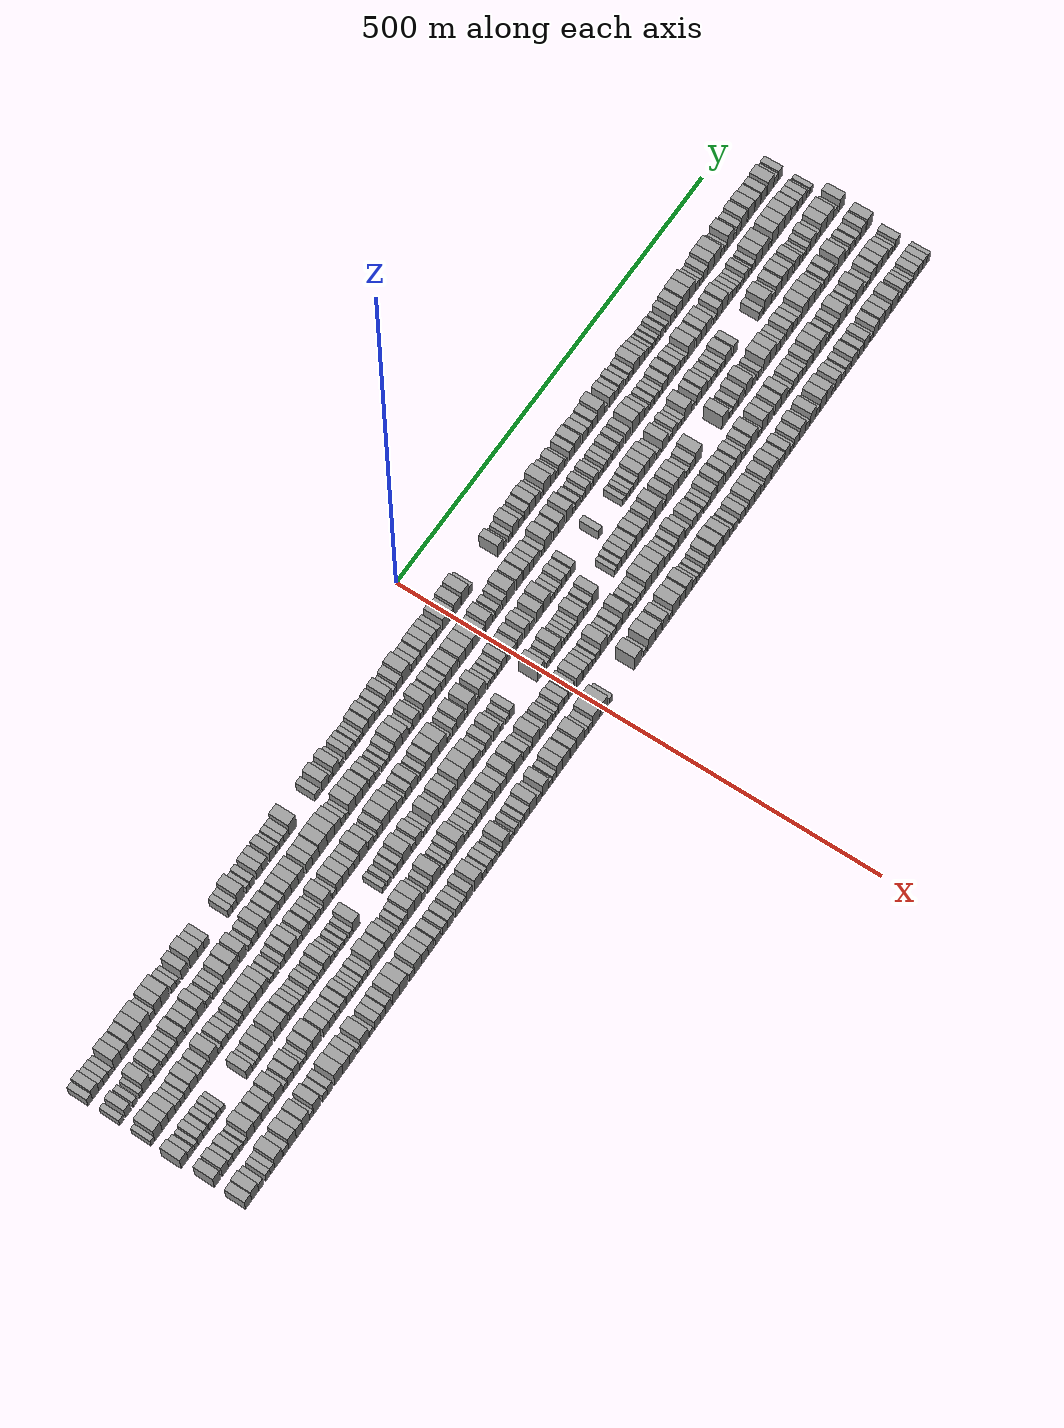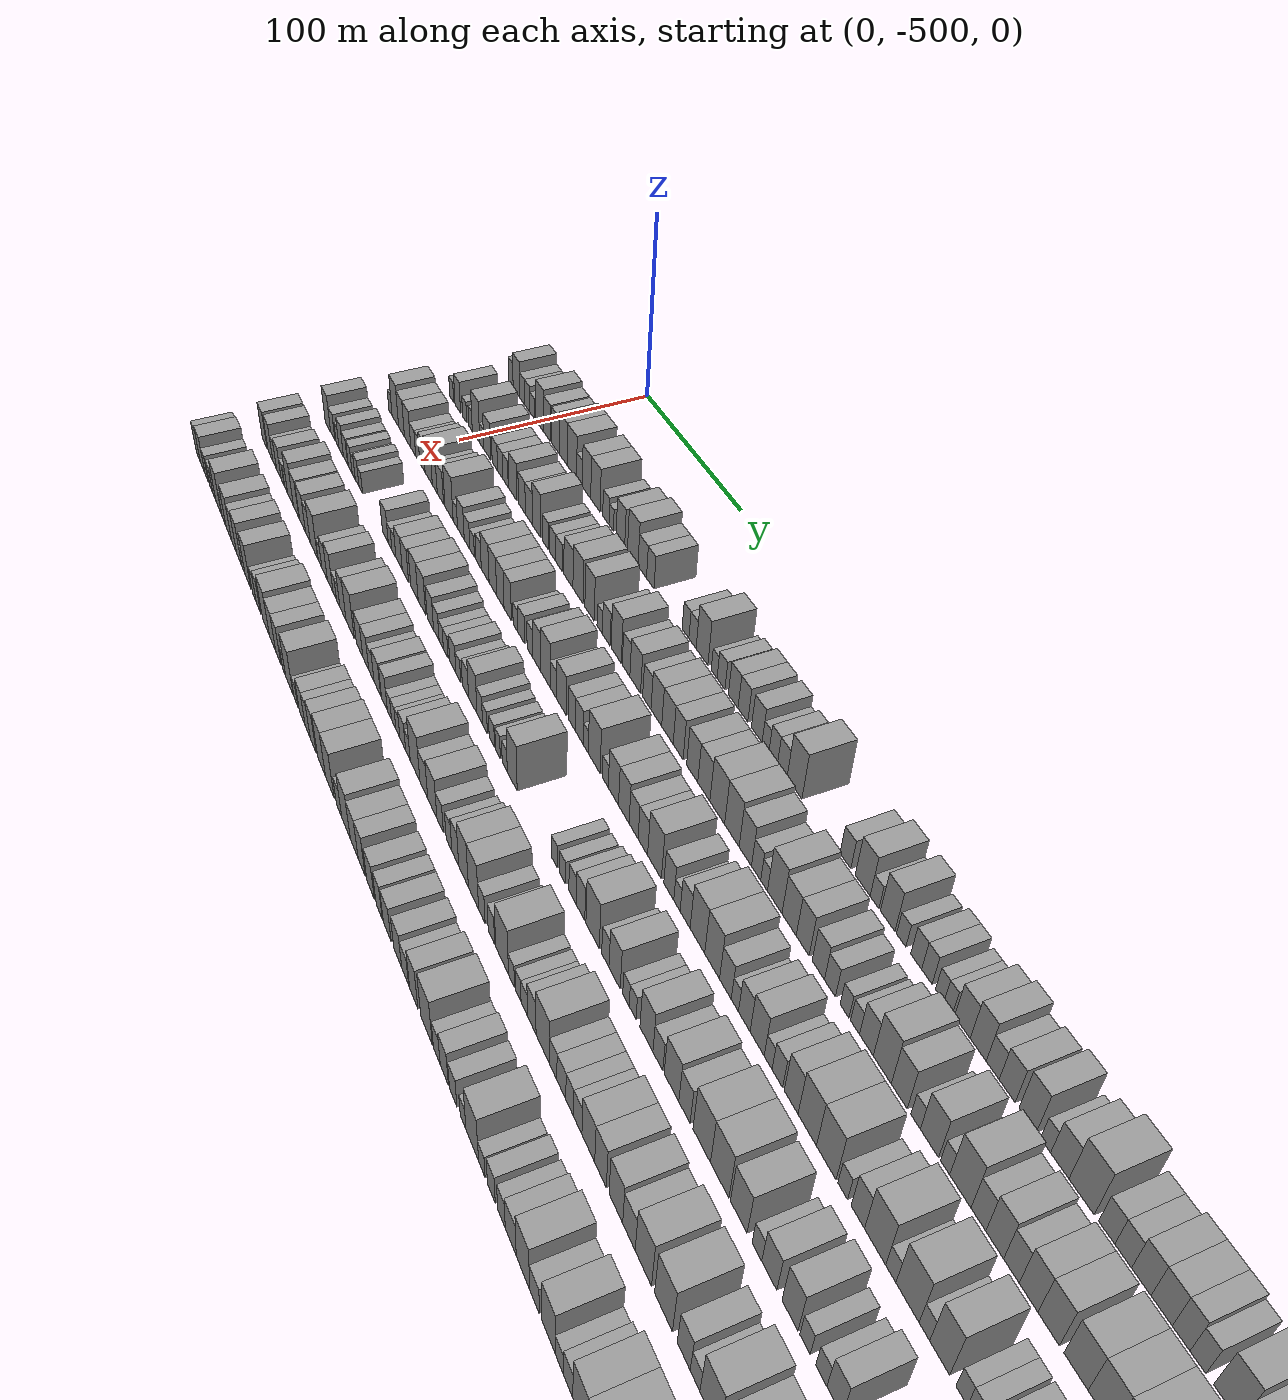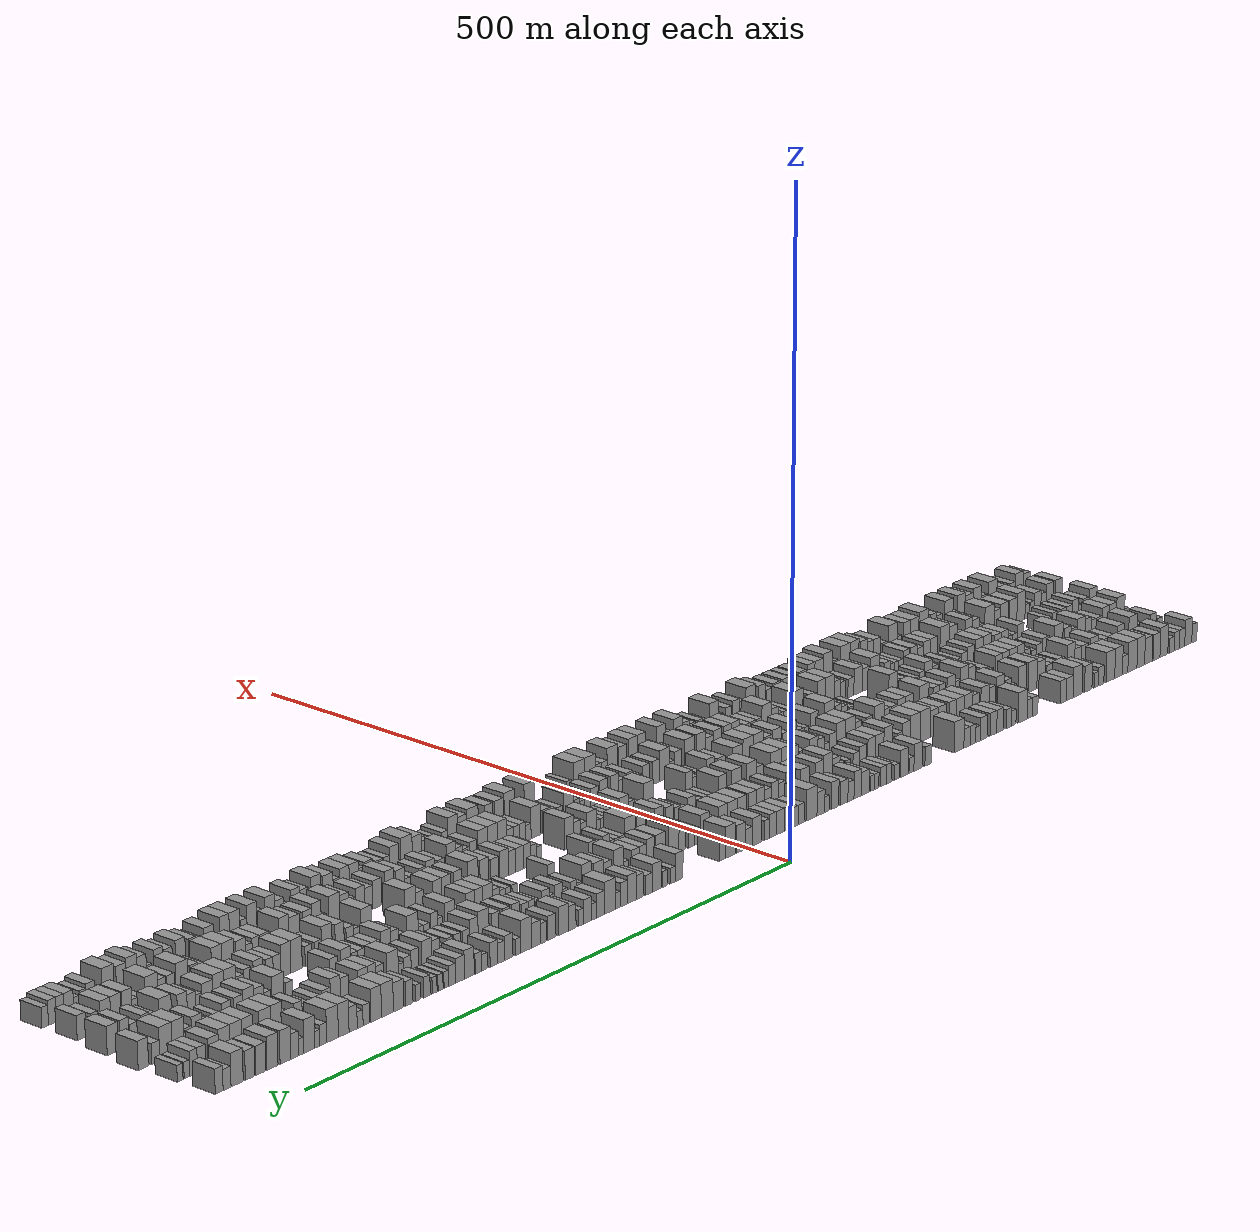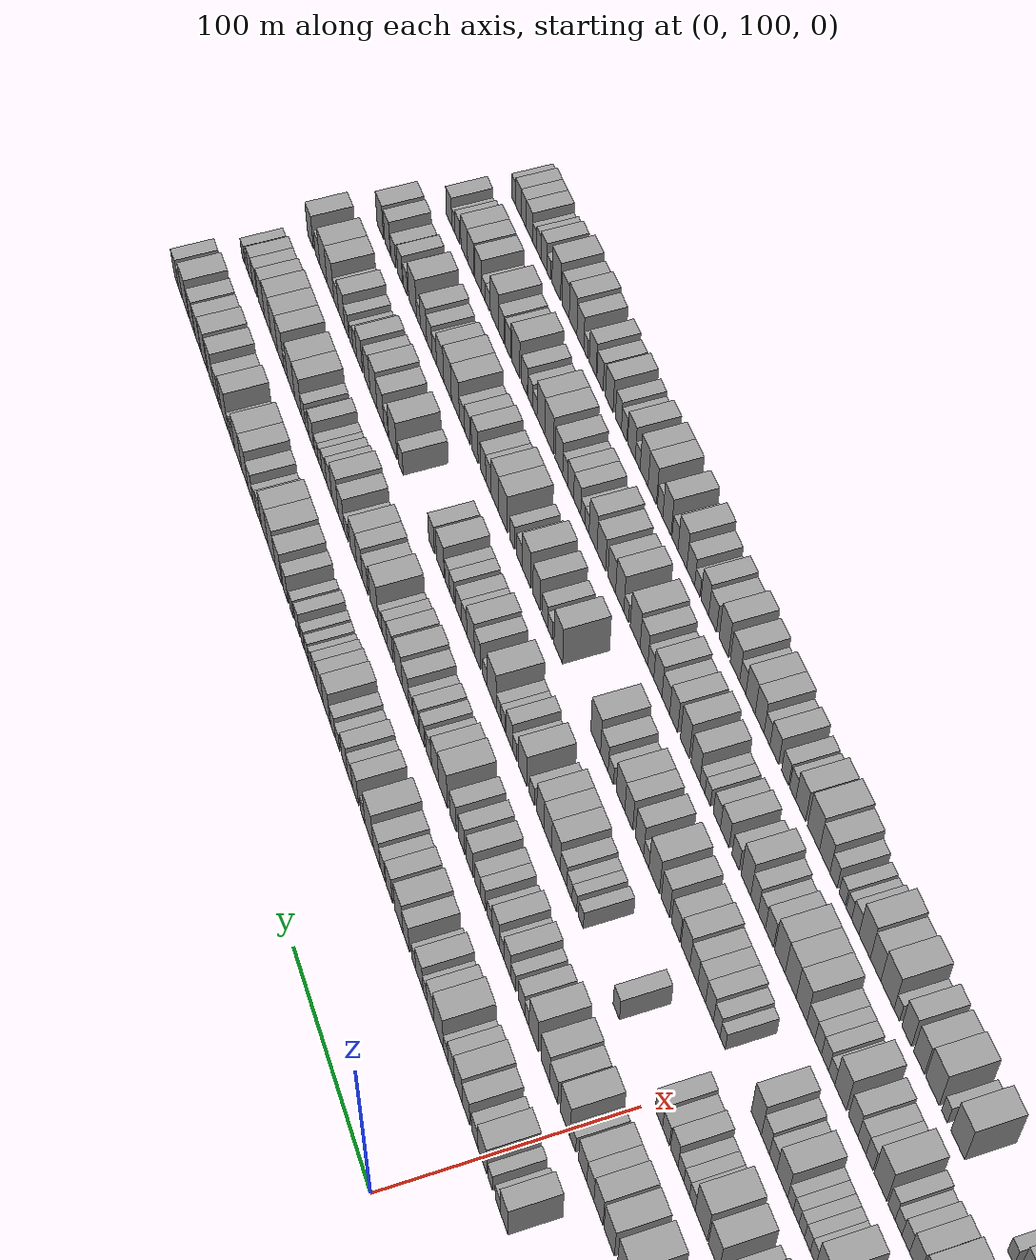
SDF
<sdf version="1.6">
 <world name="default">
  <scene>
   <sky><clouds><speed>12</speed></clouds></sky>
   <ambient>0.4 0.4 0.4 1</ambient>
   <background>0.7 0.7 0.7 1</background>
   <shadows>1</shadows>
  </scene>
  <gravity>0 0 -9.8066</gravity>
  <magnetic_field>6e-06 2.3e-05 -4.2e-05</magnetic_field>
  <physics default="0" name="default_physics" type="ode">
   <ode>
    <solver>
     <type>quick</type>
     <iters>10</iters>
     <sor>1.0</sor>
     <use_dynamic_moi_rescaling>0</use_dynamic_moi_rescaling>
    </solver>
    <constraints>
     <cfm>0</cfm>
     <erp>0.2</erp>
     <contact_max_correcting_vel>100</contact_max_correcting_vel>
     <contact_surface_layer>0.001</contact_surface_layer>
    </constraints>
   </ode>
   <max_step_size>0.004</max_step_size>
   <real_time_factor>1</real_time_factor>
   <real_time_update_rate>250</real_time_update_rate>
  </physics>
  <light name="sun" type="directional">
   <pose>0 0 10 0 0 0</pose>
   <diffuse>0.8 0.8 0.8 1</diffuse>
   <specular>0.2 0.2 0.2 1</specular>
   <attenuation>
    <range>1000</range>
    <constant>0.9</constant>
    <linear>0.01</linear>
    <quadratic>0.001</quadratic>
   </attenuation>
   <direction>-0.5 0.1 -0.9</direction>
  </light>
  <model name="building_1">
   <static>1</static>
   <pose>50.0000 -535.7820 0 0.000000 0.000000 0.000000</pose>
   <link name="link">
    <pose>0 0 7.50 0 0 0</pose>
    <collision name="collision"><geometry><box><size>20.0000 6.4360 15.0000</size></box></geometry></collision>
    <visual name="visual">
     <cast_shadows>0</cast_shadows>
     <geometry><box><size>20.0000 6.4360 15.0000</size></box></geometry>
     <material>
      <script>
       <uri>model://grey_wall/materials/scripts</uri>
       <uri>model://grey_wall/materials/textures</uri>
       <name>vrc/grey_wall</name>
      </script>
     </material>
    </visual>
   </link>
  </model>
  <model name="building_2">
   <static>1</static>
   <pose>50.0000 -528.0198 0 0.000000 0.000000 0.000000</pose>
   <link name="link">
    <pose>0 0 10.50 0 0 0</pose>
    <collision name="collision"><geometry><box><size>20.0000 9.0884 21.0000</size></box></geometry></collision>
    <visual name="visual">
     <cast_shadows>0</cast_shadows>
     <geometry><box><size>20.0000 9.0884 21.0000</size></box></geometry>
     <material>
      <script>
       <uri>model://grey_wall/materials/scripts</uri>
       <uri>model://grey_wall/materials/textures</uri>
       <name>vrc/grey_wall</name>
      </script>
     </material>
    </visual>
   </link>
  </model>
  <model name="building_3">
   <static>1</static>
   <pose>50.0000 -520.0924 0 0.000000 0.000000 0.000000</pose>
   <link name="link">
    <pose>0 0 7.50 0 0 0</pose>
    <collision name="collision"><geometry><box><size>20.0000 6.7663 15.0000</size></box></geometry></collision>
    <visual name="visual">
     <cast_shadows>0</cast_shadows>
     <geometry><box><size>20.0000 6.7663 15.0000</size></box></geometry>
     <material>
      <script>
       <uri>model://grey_wall/materials/scripts</uri>
       <uri>model://grey_wall/materials/textures</uri>
       <name>vrc/grey_wall</name>
      </script>
     </material>
    </visual>
   </link>
  </model>
  <model name="building_4">
   <static>1</static>
   <pose>50.0000 -513.1745 0 0.000000 0.000000 0.000000</pose>
   <link name="link">
    <pose>0 0 7.50 0 0 0</pose>
    <collision name="collision"><geometry><box><size>20.0000 7.0696 15.0000</size></box></geometry></collision>
    <visual name="visual">
     <cast_shadows>0</cast_shadows>
     <geometry><box><size>20.0000 7.0696 15.0000</size></box></geometry>
     <material>
      <script>
       <uri>model://grey_wall/materials/scripts</uri>
       <uri>model://grey_wall/materials/textures</uri>
       <name>vrc/grey_wall</name>
      </script>
     </material>
    </visual>
   </link>
  </model>
  <model name="building_5">
   <static>1</static>
   <pose>50.0000 -506.6680 0 0.000000 0.000000 0.000000</pose>
   <link name="link">
    <pose>0 0 6.00 0 0 0</pose>
    <collision name="collision"><geometry><box><size>20.0000 5.9433 12.0000</size></box></geometry></collision>
    <visual name="visual">
     <cast_shadows>0</cast_shadows>
     <geometry><box><size>20.0000 5.9433 12.0000</size></box></geometry>
     <material>
      <script>
       <uri>model://grey_wall/materials/scripts</uri>
       <uri>model://grey_wall/materials/textures</uri>
       <name>vrc/grey_wall</name>
      </script>
     </material>
    </visual>
   </link>
  </model>
  <model name="building_6">
   <static>1</static>
   <pose>50.0000 -496.6486 0 0.000000 0.000000 0.000000</pose>
   <link name="link">
    <pose>0 0 12.00 0 0 0</pose>
    <collision name="collision"><geometry><box><size>20.0000 10.0956 24.0000</size></box></geometry></collision>
    <visual name="visual">
     <cast_shadows>0</cast_shadows>
     <geometry><box><size>20.0000 10.0956 24.0000</size></box></geometry>
     <material>
      <script>
       <uri>model://grey_wall/materials/scripts</uri>
       <uri>model://grey_wall/materials/textures</uri>
       <name>vrc/grey_wall</name>
      </script>
     </material>
    </visual>
   </link>
  </model>
  <model name="building_7">
   <static>1</static>
   <pose>50.0000 -487.1388 0 0.000000 0.000000 0.000000</pose>
   <link name="link">
    <pose>0 0 10.50 0 0 0</pose>
    <collision name="collision"><geometry><box><size>20.0000 8.9242 21.0000</size></box></geometry></collision>
    <visual name="visual">
     <cast_shadows>0</cast_shadows>
     <geometry><box><size>20.0000 8.9242 21.0000</size></box></geometry>
     <material>
      <script>
       <uri>model://grey_wall/materials/scripts</uri>
       <uri>model://grey_wall/materials/textures</uri>
       <name>vrc/grey_wall</name>
      </script>
     </material>
    </visual>
   </link>
  </model>
  <model name="building_8">
   <static>1</static>
   <pose>50.0000 -476.8847 0 0.000000 0.000000 0.000000</pose>
   <link name="link">
    <pose>0 0 10.50 0 0 0</pose>
    <collision name="collision"><geometry><box><size>20.0000 9.5838 21.0000</size></box></geometry></collision>
    <visual name="visual">
     <cast_shadows>0</cast_shadows>
     <geometry><box><size>20.0000 9.5838 21.0000</size></box></geometry>
     <material>
      <script>
       <uri>model://grey_wall/materials/scripts</uri>
       <uri>model://grey_wall/materials/textures</uri>
       <name>vrc/grey_wall</name>
      </script>
     </material>
    </visual>
   </link>
  </model>
  <model name="building_9">
   <static>1</static>
   <pose>50.0000 -467.1812 0 0.000000 0.000000 0.000000</pose>
   <link name="link">
    <pose>0 0 12.00 0 0 0</pose>
    <collision name="collision"><geometry><box><size>20.0000 9.8232 24.0000</size></box></geometry></collision>
    <visual name="visual">
     <cast_shadows>0</cast_shadows>
     <geometry><box><size>20.0000 9.8232 24.0000</size></box></geometry>
     <material>
      <script>
       <uri>model://grey_wall/materials/scripts</uri>
       <uri>model://grey_wall/materials/textures</uri>
       <name>vrc/grey_wall</name>
      </script>
     </material>
    </visual>
   </link>
  </model>
  <model name="building_10">
   <static>1</static>
   <pose>50.0000 -456.5268 0 0.000000 0.000000 0.000000</pose>
   <link name="link">
    <pose>0 0 12.00 0 0 0</pose>
    <collision name="collision"><geometry><box><size>20.0000 11.4857 24.0000</size></box></geometry></collision>
    <visual name="visual">
     <cast_shadows>0</cast_shadows>
     <geometry><box><size>20.0000 11.4857 24.0000</size></box></geometry>
     <material>
      <script>
       <uri>model://grey_wall/materials/scripts</uri>
       <uri>model://grey_wall/materials/textures</uri>
       <name>vrc/grey_wall</name>
      </script>
     </material>
    </visual>
   </link>
  </model>
  <model name="building_11">
   <static>1</static>
   <pose>50.0000 -447.3915 0 0.000000 0.000000 0.000000</pose>
   <link name="link">
    <pose>0 0 7.50 0 0 0</pose>
    <collision name="collision"><geometry><box><size>20.0000 6.7850 15.0000</size></box></geometry></collision>
    <visual name="visual">
     <cast_shadows>0</cast_shadows>
     <geometry><box><size>20.0000 6.7850 15.0000</size></box></geometry>
     <material>
      <script>
       <uri>model://grey_wall/materials/scripts</uri>
       <uri>model://grey_wall/materials/textures</uri>
       <name>vrc/grey_wall</name>
      </script>
     </material>
    </visual>
   </link>
  </model>
  <model name="building_12">
   <static>1</static>
   <pose>50.0000 -439.1225 0 0.000000 0.000000 0.000000</pose>
   <link name="link">
    <pose>0 0 12.00 0 0 0</pose>
    <collision name="collision"><geometry><box><size>20.0000 9.7531 24.0000</size></box></geometry></collision>
    <visual name="visual">
     <cast_shadows>0</cast_shadows>
     <geometry><box><size>20.0000 9.7531 24.0000</size></box></geometry>
     <material>
      <script>
       <uri>model://grey_wall/materials/scripts</uri>
       <uri>model://grey_wall/materials/textures</uri>
       <name>vrc/grey_wall</name>
      </script>
     </material>
    </visual>
   </link>
  </model>
  <model name="building_13">
   <static>1</static>
   <pose>50.0000 -428.8946 0 0.000000 0.000000 0.000000</pose>
   <link name="link">
    <pose>0 0 12.00 0 0 0</pose>
    <collision name="collision"><geometry><box><size>20.0000 10.7026 24.0000</size></box></geometry></collision>
    <visual name="visual">
     <cast_shadows>0</cast_shadows>
     <geometry><box><size>20.0000 10.7026 24.0000</size></box></geometry>
     <material>
      <script>
       <uri>model://grey_wall/materials/scripts</uri>
       <uri>model://grey_wall/materials/textures</uri>
       <name>vrc/grey_wall</name>
      </script>
     </material>
    </visual>
   </link>
  </model>
  <model name="building_14">
   <static>1</static>
   <pose>50.0000 -417.0300 0 0.000000 0.000000 0.000000</pose>
   <link name="link">
    <pose>0 0 7.50 0 0 0</pose>
    <collision name="collision"><geometry><box><size>20.0000 7.0265 15.0000</size></box></geometry></collision>
    <visual name="visual">
     <cast_shadows>0</cast_shadows>
     <geometry><box><size>20.0000 7.0265 15.0000</size></box></geometry>
     <material>
      <script>
       <uri>model://grey_wall/materials/scripts</uri>
       <uri>model://grey_wall/materials/textures</uri>
       <name>vrc/grey_wall</name>
      </script>
     </material>
    </visual>
   </link>
  </model>
  <model name="building_15">
   <static>1</static>
   <pose>50.0000 -411.0758 0 0.000000 0.000000 0.000000</pose>
   <link name="link">
    <pose>0 0 6.00 0 0 0</pose>
    <collision name="collision"><geometry><box><size>20.0000 4.8819 12.0000</size></box></geometry></collision>
    <visual name="visual">
     <cast_shadows>0</cast_shadows>
     <geometry><box><size>20.0000 4.8819 12.0000</size></box></geometry>
     <material>
      <script>
       <uri>model://grey_wall/materials/scripts</uri>
       <uri>model://grey_wall/materials/textures</uri>
       <name>vrc/grey_wall</name>
      </script>
     </material>
    </visual>
   </link>
  </model>
  <model name="building_16">
   <static>1</static>
   <pose>50.0000 -401.0472 0 0.000000 0.000000 0.000000</pose>
   <link name="link">
    <pose>0 0 10.50 0 0 0</pose>
    <collision name="collision"><geometry><box><size>20.0000 9.1753 21.0000</size></box></geometry></collision>
    <visual name="visual">
     <cast_shadows>0</cast_shadows>
     <geometry><box><size>20.0000 9.1753 21.0000</size></box></geometry>
     <material>
      <script>
       <uri>model://grey_wall/materials/scripts</uri>
       <uri>model://grey_wall/materials/textures</uri>
       <name>vrc/grey_wall</name>
      </script>
     </material>
    </visual>
   </link>
  </model>
  <model name="building_17">
   <static>1</static>
   <pose>50.0000 -387.9378 0 0.000000 0.000000 0.000000</pose>
   <link name="link">
    <pose>0 0 12.00 0 0 0</pose>
    <collision name="collision"><geometry><box><size>20.0000 11.0435 24.0000</size></box></geometry></collision>
    <visual name="visual">
     <cast_shadows>0</cast_shadows>
     <geometry><box><size>20.0000 11.0435 24.0000</size></box></geometry>
     <material>
      <script>
       <uri>model://grey_wall/materials/scripts</uri>
       <uri>model://grey_wall/materials/textures</uri>
       <name>vrc/grey_wall</name>
      </script>
     </material>
    </visual>
   </link>
  </model>
  <model name="building_18">
   <static>1</static>
   <pose>50.0000 -378.0178 0 0.000000 0.000000 0.000000</pose>
   <link name="link">
    <pose>0 0 9.00 0 0 0</pose>
    <collision name="collision"><geometry><box><size>20.0000 8.7965 18.0000</size></box></geometry></collision>
    <visual name="visual">
     <cast_shadows>0</cast_shadows>
     <geometry><box><size>20.0000 8.7965 18.0000</size></box></geometry>
     <material>
      <script>
       <uri>model://grey_wall/materials/scripts</uri>
       <uri>model://grey_wall/materials/textures</uri>
       <name>vrc/grey_wall</name>
      </script>
     </material>
    </visual>
   </link>
  </model>
  <model name="building_19">
   <static>1</static>
   <pose>50.0000 -369.8452 0 0.000000 0.000000 0.000000</pose>
   <link name="link">
    <pose>0 0 9.00 0 0 0</pose>
    <collision name="collision"><geometry><box><size>20.0000 7.5487 18.0000</size></box></geometry></collision>
    <visual name="visual">
     <cast_shadows>0</cast_shadows>
     <geometry><box><size>20.0000 7.5487 18.0000</size></box></geometry>
     <material>
      <script>
       <uri>model://grey_wall/materials/scripts</uri>
       <uri>model://grey_wall/materials/textures</uri>
       <name>vrc/grey_wall</name>
      </script>
     </material>
    </visual>
   </link>
  </model>
  <model name="building_20">
   <static>1</static>
   <pose>50.0000 -335.5107 0 0.000000 0.000000 0.000000</pose>
   <link name="link">
    <pose>0 0 7.50 0 0 0</pose>
    <collision name="collision"><geometry><box><size>20.0000 6.3734 15.0000</size></box></geometry></collision>
    <visual name="visual">
     <cast_shadows>0</cast_shadows>
     <geometry><box><size>20.0000 6.3734 15.0000</size></box></geometry>
     <material>
      <script>
       <uri>model://grey_wall/materials/scripts</uri>
       <uri>model://grey_wall/materials/textures</uri>
       <name>vrc/grey_wall</name>
      </script>
     </material>
    </visual>
   </link>
  </model>
  <model name="building_21">
   <static>1</static>
   <pose>50.0000 -328.9839 0 0.000000 0.000000 0.000000</pose>
   <link name="link">
    <pose>0 0 7.50 0 0 0</pose>
    <collision name="collision"><geometry><box><size>20.0000 6.6802 15.0000</size></box></geometry></collision>
    <visual name="visual">
     <cast_shadows>0</cast_shadows>
     <geometry><box><size>20.0000 6.6802 15.0000</size></box></geometry>
     <material>
      <script>
       <uri>model://grey_wall/materials/scripts</uri>
       <uri>model://grey_wall/materials/textures</uri>
       <name>vrc/grey_wall</name>
      </script>
     </material>
    </visual>
   </link>
  </model>
  <model name="building_22">
   <static>1</static>
   <pose>50.0000 -320.3339 0 0.000000 0.000000 0.000000</pose>
   <link name="link">
    <pose>0 0 12.00 0 0 0</pose>
    <collision name="collision"><geometry><box><size>20.0000 10.6198 24.0000</size></box></geometry></collision>
    <visual name="visual">
     <cast_shadows>0</cast_shadows>
     <geometry><box><size>20.0000 10.6198 24.0000</size></box></geometry>
     <material>
      <script>
       <uri>model://grey_wall/materials/scripts</uri>
       <uri>model://grey_wall/materials/textures</uri>
       <name>vrc/grey_wall</name>
      </script>
     </material>
    </visual>
   </link>
  </model>
  <model name="building_23">
   <static>1</static>
   <pose>50.0000 -309.4199 0 0.000000 0.000000 0.000000</pose>
   <link name="link">
    <pose>0 0 6.00 0 0 0</pose>
    <collision name="collision"><geometry><box><size>20.0000 5.2083 12.0000</size></box></geometry></collision>
    <visual name="visual">
     <cast_shadows>0</cast_shadows>
     <geometry><box><size>20.0000 5.2083 12.0000</size></box></geometry>
     <material>
      <script>
       <uri>model://grey_wall/materials/scripts</uri>
       <uri>model://grey_wall/materials/textures</uri>
       <name>vrc/grey_wall</name>
      </script>
     </material>
    </visual>
   </link>
  </model>
  <model name="building_24">
   <static>1</static>
   <pose>50.0000 -303.4045 0 0.000000 0.000000 0.000000</pose>
   <link name="link">
    <pose>0 0 7.50 0 0 0</pose>
    <collision name="collision"><geometry><box><size>20.0000 6.8224 15.0000</size></box></geometry></collision>
    <visual name="visual">
     <cast_shadows>0</cast_shadows>
     <geometry><box><size>20.0000 6.8224 15.0000</size></box></geometry>
     <material>
      <script>
       <uri>model://grey_wall/materials/scripts</uri>
       <uri>model://grey_wall/materials/textures</uri>
       <name>vrc/grey_wall</name>
      </script>
     </material>
    </visual>
   </link>
  </model>
  <model name="building_25">
   <static>1</static>
   <pose>50.0000 -292.8908 0 0.000000 0.000000 0.000000</pose>
   <link name="link">
    <pose>0 0 9.00 0 0 0</pose>
    <collision name="collision"><geometry><box><size>20.0000 8.2052 18.0000</size></box></geometry></collision>
    <visual name="visual">
     <cast_shadows>0</cast_shadows>
     <geometry><box><size>20.0000 8.2052 18.0000</size></box></geometry>
     <material>
      <script>
       <uri>model://grey_wall/materials/scripts</uri>
       <uri>model://grey_wall/materials/textures</uri>
       <name>vrc/grey_wall</name>
      </script>
     </material>
    </visual>
   </link>
  </model>
  <model name="building_26">
   <static>1</static>
   <pose>50.0000 -284.7162 0 0.000000 0.000000 0.000000</pose>
   <link name="link">
    <pose>0 0 9.00 0 0 0</pose>
    <collision name="collision"><geometry><box><size>20.0000 8.1438 18.0000</size></box></geometry></collision>
    <visual name="visual">
     <cast_shadows>0</cast_shadows>
     <geometry><box><size>20.0000 8.1438 18.0000</size></box></geometry>
     <material>
      <script>
       <uri>model://grey_wall/materials/scripts</uri>
       <uri>model://grey_wall/materials/textures</uri>
       <name>vrc/grey_wall</name>
      </script>
     </material>
    </visual>
   </link>
  </model>
  <model name="building_27">
   <static>1</static>
   <pose>50.0000 -273.2896 0 0.000000 0.000000 0.000000</pose>
   <link name="link">
    <pose>0 0 9.00 0 0 0</pose>
    <collision name="collision"><geometry><box><size>20.0000 8.7095 18.0000</size></box></geometry></collision>
    <visual name="visual">
     <cast_shadows>0</cast_shadows>
     <geometry><box><size>20.0000 8.7095 18.0000</size></box></geometry>
     <material>
      <script>
       <uri>model://grey_wall/materials/scripts</uri>
       <uri>model://grey_wall/materials/textures</uri>
       <name>vrc/grey_wall</name>
      </script>
     </material>
    </visual>
   </link>
  </model>
  <model name="building_28">
   <static>1</static>
   <pose>50.0000 -266.2153 0 0.000000 0.000000 0.000000</pose>
   <link name="link">
    <pose>0 0 6.00 0 0 0</pose>
    <collision name="collision"><geometry><box><size>20.0000 5.4390 12.0000</size></box></geometry></collision>
    <visual name="visual">
     <cast_shadows>0</cast_shadows>
     <geometry><box><size>20.0000 5.4390 12.0000</size></box></geometry>
     <material>
      <script>
       <uri>model://grey_wall/materials/scripts</uri>
       <uri>model://grey_wall/materials/textures</uri>
       <name>vrc/grey_wall</name>
      </script>
     </material>
    </visual>
   </link>
  </model>
  <model name="building_29">
   <static>1</static>
   <pose>50.0000 -260.1378 0 0.000000 0.000000 0.000000</pose>
   <link name="link">
    <pose>0 0 7.50 0 0 0</pose>
    <collision name="collision"><geometry><box><size>20.0000 6.7161 15.0000</size></box></geometry></collision>
    <visual name="visual">
     <cast_shadows>0</cast_shadows>
     <geometry><box><size>20.0000 6.7161 15.0000</size></box></geometry>
     <material>
      <script>
       <uri>model://grey_wall/materials/scripts</uri>
       <uri>model://grey_wall/materials/textures</uri>
       <name>vrc/grey_wall</name>
      </script>
     </material>
    </visual>
   </link>
  </model>
  <model name="building_30">
   <static>1</static>
   <pose>50.0000 -253.0541 0 0.000000 0.000000 0.000000</pose>
   <link name="link">
    <pose>0 0 7.50 0 0 0</pose>
    <collision name="collision"><geometry><box><size>20.0000 7.4514 15.0000</size></box></geometry></collision>
    <visual name="visual">
     <cast_shadows>0</cast_shadows>
     <geometry><box><size>20.0000 7.4514 15.0000</size></box></geometry>
     <material>
      <script>
       <uri>model://grey_wall/materials/scripts</uri>
       <uri>model://grey_wall/materials/textures</uri>
       <name>vrc/grey_wall</name>
      </script>
     </material>
    </visual>
   </link>
  </model>
  <model name="building_31">
   <static>1</static>
   <pose>50.0000 -243.6839 0 0.000000 0.000000 0.000000</pose>
   <link name="link">
    <pose>0 0 12.00 0 0 0</pose>
    <collision name="collision"><geometry><box><size>20.0000 11.2891 24.0000</size></box></geometry></collision>
    <visual name="visual">
     <cast_shadows>0</cast_shadows>
     <geometry><box><size>20.0000 11.2891 24.0000</size></box></geometry>
     <material>
      <script>
       <uri>model://grey_wall/materials/scripts</uri>
       <uri>model://grey_wall/materials/textures</uri>
       <name>vrc/grey_wall</name>
      </script>
     </material>
    </visual>
   </link>
  </model>
  <model name="building_32">
   <static>1</static>
   <pose>50.0000 -206.8632 0 0.000000 0.000000 0.000000</pose>
   <link name="link">
    <pose>0 0 7.50 0 0 0</pose>
    <collision name="collision"><geometry><box><size>20.0000 7.4507 15.0000</size></box></geometry></collision>
    <visual name="visual">
     <cast_shadows>0</cast_shadows>
     <geometry><box><size>20.0000 7.4507 15.0000</size></box></geometry>
     <material>
      <script>
       <uri>model://grey_wall/materials/scripts</uri>
       <uri>model://grey_wall/materials/textures</uri>
       <name>vrc/grey_wall</name>
      </script>
     </material>
    </visual>
   </link>
  </model>
  <model name="building_33">
   <static>1</static>
   <pose>50.0000 -195.1526 0 0.000000 0.000000 0.000000</pose>
   <link name="link">
    <pose>0 0 10.50 0 0 0</pose>
    <collision name="collision"><geometry><box><size>20.0000 9.9706 21.0000</size></box></geometry></collision>
    <visual name="visual">
     <cast_shadows>0</cast_shadows>
     <geometry><box><size>20.0000 9.9706 21.0000</size></box></geometry>
     <material>
      <script>
       <uri>model://grey_wall/materials/scripts</uri>
       <uri>model://grey_wall/materials/textures</uri>
       <name>vrc/grey_wall</name>
      </script>
     </material>
    </visual>
   </link>
  </model>
  <model name="building_34">
   <static>1</static>
   <pose>50.0000 -187.2822 0 0.000000 0.000000 0.000000</pose>
   <link name="link">
    <pose>0 0 6.00 0 0 0</pose>
    <collision name="collision"><geometry><box><size>20.0000 5.7702 12.0000</size></box></geometry></collision>
    <visual name="visual">
     <cast_shadows>0</cast_shadows>
     <geometry><box><size>20.0000 5.7702 12.0000</size></box></geometry>
     <material>
      <script>
       <uri>model://grey_wall/materials/scripts</uri>
       <uri>model://grey_wall/materials/textures</uri>
       <name>vrc/grey_wall</name>
      </script>
     </material>
    </visual>
   </link>
  </model>
  <model name="building_35">
   <static>1</static>
   <pose>50.0000 -178.7519 0 0.000000 0.000000 0.000000</pose>
   <link name="link">
    <pose>0 0 10.50 0 0 0</pose>
    <collision name="collision"><geometry><box><size>20.0000 9.2904 21.0000</size></box></geometry></collision>
    <visual name="visual">
     <cast_shadows>0</cast_shadows>
     <geometry><box><size>20.0000 9.2904 21.0000</size></box></geometry>
     <material>
      <script>
       <uri>model://grey_wall/materials/scripts</uri>
       <uri>model://grey_wall/materials/textures</uri>
       <name>vrc/grey_wall</name>
      </script>
     </material>
    </visual>
   </link>
  </model>
  <model name="building_36">
   <static>1</static>
   <pose>50.0000 -170.1924 0 0.000000 0.000000 0.000000</pose>
   <link name="link">
    <pose>0 0 6.00 0 0 0</pose>
    <collision name="collision"><geometry><box><size>20.0000 5.8287 12.0000</size></box></geometry></collision>
    <visual name="visual">
     <cast_shadows>0</cast_shadows>
     <geometry><box><size>20.0000 5.8287 12.0000</size></box></geometry>
     <material>
      <script>
       <uri>model://grey_wall/materials/scripts</uri>
       <uri>model://grey_wall/materials/textures</uri>
       <name>vrc/grey_wall</name>
      </script>
     </material>
    </visual>
   </link>
  </model>
  <model name="building_37">
   <static>1</static>
   <pose>50.0000 -160.9449 0 0.000000 0.000000 0.000000</pose>
   <link name="link">
    <pose>0 0 7.50 0 0 0</pose>
    <collision name="collision"><geometry><box><size>20.0000 6.6662 15.0000</size></box></geometry></collision>
    <visual name="visual">
     <cast_shadows>0</cast_shadows>
     <geometry><box><size>20.0000 6.6662 15.0000</size></box></geometry>
     <material>
      <script>
       <uri>model://grey_wall/materials/scripts</uri>
       <uri>model://grey_wall/materials/textures</uri>
       <name>vrc/grey_wall</name>
      </script>
     </material>
    </visual>
   </link>
  </model>
  <model name="building_38">
   <static>1</static>
   <pose>50.0000 -154.4565 0 0.000000 0.000000 0.000000</pose>
   <link name="link">
    <pose>0 0 7.50 0 0 0</pose>
    <collision name="collision"><geometry><box><size>20.0000 6.3107 15.0000</size></box></geometry></collision>
    <visual name="visual">
     <cast_shadows>0</cast_shadows>
     <geometry><box><size>20.0000 6.3107 15.0000</size></box></geometry>
     <material>
      <script>
       <uri>model://grey_wall/materials/scripts</uri>
       <uri>model://grey_wall/materials/textures</uri>
       <name>vrc/grey_wall</name>
      </script>
     </material>
    </visual>
   </link>
  </model>
  <model name="building_39">
   <static>1</static>
   <pose>50.0000 -146.7622 0 0.000000 0.000000 0.000000</pose>
   <link name="link">
    <pose>0 0 6.00 0 0 0</pose>
    <collision name="collision"><geometry><box><size>20.0000 5.0779 12.0000</size></box></geometry></collision>
    <visual name="visual">
     <cast_shadows>0</cast_shadows>
     <geometry><box><size>20.0000 5.0779 12.0000</size></box></geometry>
     <material>
      <script>
       <uri>model://grey_wall/materials/scripts</uri>
       <uri>model://grey_wall/materials/textures</uri>
       <name>vrc/grey_wall</name>
      </script>
     </material>
    </visual>
   </link>
  </model>
  <model name="building_40">
   <static>1</static>
   <pose>50.0000 -141.7546 0 0.000000 0.000000 0.000000</pose>
   <link name="link">
    <pose>0 0 6.00 0 0 0</pose>
    <collision name="collision"><geometry><box><size>20.0000 4.9372 12.0000</size></box></geometry></collision>
    <visual name="visual">
     <cast_shadows>0</cast_shadows>
     <geometry><box><size>20.0000 4.9372 12.0000</size></box></geometry>
     <material>
      <script>
       <uri>model://grey_wall/materials/scripts</uri>
       <uri>model://grey_wall/materials/textures</uri>
       <name>vrc/grey_wall</name>
      </script>
     </material>
    </visual>
   </link>
  </model>
  <model name="building_41">
   <static>1</static>
   <pose>50.0000 -133.8388 0 0.000000 0.000000 0.000000</pose>
   <link name="link">
    <pose>0 0 9.00 0 0 0</pose>
    <collision name="collision"><geometry><box><size>20.0000 8.8944 18.0000</size></box></geometry></collision>
    <visual name="visual">
     <cast_shadows>0</cast_shadows>
     <geometry><box><size>20.0000 8.8944 18.0000</size></box></geometry>
     <material>
      <script>
       <uri>model://grey_wall/materials/scripts</uri>
       <uri>model://grey_wall/materials/textures</uri>
       <name>vrc/grey_wall</name>
      </script>
     </material>
    </visual>
   </link>
  </model>
  <model name="building_42">
   <static>1</static>
   <pose>50.0000 -124.9746 0 0.000000 0.000000 0.000000</pose>
   <link name="link">
    <pose>0 0 10.50 0 0 0</pose>
    <collision name="collision"><geometry><box><size>20.0000 8.8341 21.0000</size></box></geometry></collision>
    <visual name="visual">
     <cast_shadows>0</cast_shadows>
     <geometry><box><size>20.0000 8.8341 21.0000</size></box></geometry>
     <material>
      <script>
       <uri>model://grey_wall/materials/scripts</uri>
       <uri>model://grey_wall/materials/textures</uri>
       <name>vrc/grey_wall</name>
      </script>
     </material>
    </visual>
   </link>
  </model>
  <model name="building_43">
   <static>1</static>
   <pose>50.0000 -117.0735 0 0.000000 0.000000 0.000000</pose>
   <link name="link">
    <pose>0 0 7.50 0 0 0</pose>
    <collision name="collision"><geometry><box><size>20.0000 6.9681 15.0000</size></box></geometry></collision>
    <visual name="visual">
     <cast_shadows>0</cast_shadows>
     <geometry><box><size>20.0000 6.9681 15.0000</size></box></geometry>
     <material>
      <script>
       <uri>model://grey_wall/materials/scripts</uri>
       <uri>model://grey_wall/materials/textures</uri>
       <name>vrc/grey_wall</name>
      </script>
     </material>
    </visual>
   </link>
  </model>
  <model name="building_44">
   <static>1</static>
   <pose>50.0000 -109.3695 0 0.000000 0.000000 0.000000</pose>
   <link name="link">
    <pose>0 0 9.00 0 0 0</pose>
    <collision name="collision"><geometry><box><size>20.0000 8.4399 18.0000</size></box></geometry></collision>
    <visual name="visual">
     <cast_shadows>0</cast_shadows>
     <geometry><box><size>20.0000 8.4399 18.0000</size></box></geometry>
     <material>
      <script>
       <uri>model://grey_wall/materials/scripts</uri>
       <uri>model://grey_wall/materials/textures</uri>
       <name>vrc/grey_wall</name>
      </script>
     </material>
    </visual>
   </link>
  </model>
  <model name="building_45">
   <static>1</static>
   <pose>50.0000 -98.7290 0 0.000000 0.000000 0.000000</pose>
   <link name="link">
    <pose>0 0 10.50 0 0 0</pose>
    <collision name="collision"><geometry><box><size>20.0000 8.8412 21.0000</size></box></geometry></collision>
    <visual name="visual">
     <cast_shadows>0</cast_shadows>
     <geometry><box><size>20.0000 8.8412 21.0000</size></box></geometry>
     <material>
      <script>
       <uri>model://grey_wall/materials/scripts</uri>
       <uri>model://grey_wall/materials/textures</uri>
       <name>vrc/grey_wall</name>
      </script>
     </material>
    </visual>
   </link>
  </model>
  <model name="building_46">
   <static>1</static>
   <pose>50.0000 -89.7574 0 0.000000 0.000000 0.000000</pose>
   <link name="link">
    <pose>0 0 6.00 0 0 0</pose>
    <collision name="collision"><geometry><box><size>20.0000 5.1020 12.0000</size></box></geometry></collision>
    <visual name="visual">
     <cast_shadows>0</cast_shadows>
     <geometry><box><size>20.0000 5.1020 12.0000</size></box></geometry>
     <material>
      <script>
       <uri>model://grey_wall/materials/scripts</uri>
       <uri>model://grey_wall/materials/textures</uri>
       <name>vrc/grey_wall</name>
      </script>
     </material>
    </visual>
   </link>
  </model>
  <model name="building_47">
   <static>1</static>
   <pose>50.0000 -82.7471 0 0.000000 0.000000 0.000000</pose>
   <link name="link">
    <pose>0 0 9.00 0 0 0</pose>
    <collision name="collision"><geometry><box><size>20.0000 8.9184 18.0000</size></box></geometry></collision>
    <visual name="visual">
     <cast_shadows>0</cast_shadows>
     <geometry><box><size>20.0000 8.9184 18.0000</size></box></geometry>
     <material>
      <script>
       <uri>model://grey_wall/materials/scripts</uri>
       <uri>model://grey_wall/materials/textures</uri>
       <name>vrc/grey_wall</name>
      </script>
     </material>
    </visual>
   </link>
  </model>
  <model name="building_48">
   <static>1</static>
   <pose>50.0000 -72.3378 0 0.000000 0.000000 0.000000</pose>
   <link name="link">
    <pose>0 0 12.00 0 0 0</pose>
    <collision name="collision"><geometry><box><size>20.0000 11.9002 24.0000</size></box></geometry></collision>
    <visual name="visual">
     <cast_shadows>0</cast_shadows>
     <geometry><box><size>20.0000 11.9002 24.0000</size></box></geometry>
     <material>
      <script>
       <uri>model://grey_wall/materials/scripts</uri>
       <uri>model://grey_wall/materials/textures</uri>
       <name>vrc/grey_wall</name>
      </script>
     </material>
    </visual>
   </link>
  </model>
  <model name="building_49">
   <static>1</static>
   <pose>50.0000 -60.7088 0 0.000000 0.000000 0.000000</pose>
   <link name="link">
    <pose>0 0 7.50 0 0 0</pose>
    <collision name="collision"><geometry><box><size>20.0000 7.3577 15.0000</size></box></geometry></collision>
    <visual name="visual">
     <cast_shadows>0</cast_shadows>
     <geometry><box><size>20.0000 7.3577 15.0000</size></box></geometry>
     <material>
      <script>
       <uri>model://grey_wall/materials/scripts</uri>
       <uri>model://grey_wall/materials/textures</uri>
       <name>vrc/grey_wall</name>
      </script>
     </material>
    </visual>
   </link>
  </model>
  <model name="building_50">
   <static>1</static>
   <pose>50.0000 -53.3242 0 0.000000 0.000000 0.000000</pose>
   <link name="link">
    <pose>0 0 7.50 0 0 0</pose>
    <collision name="collision"><geometry><box><size>20.0000 7.4116 15.0000</size></box></geometry></collision>
    <visual name="visual">
     <cast_shadows>0</cast_shadows>
     <geometry><box><size>20.0000 7.4116 15.0000</size></box></geometry>
     <material>
      <script>
       <uri>model://grey_wall/materials/scripts</uri>
       <uri>model://grey_wall/materials/textures</uri>
       <name>vrc/grey_wall</name>
      </script>
     </material>
    </visual>
   </link>
  </model>
  <model name="building_51">
   <static>1</static>
   <pose>50.0000 -45.4219 0 0.000000 0.000000 0.000000</pose>
   <link name="link">
    <pose>0 0 9.00 0 0 0</pose>
    <collision name="collision"><geometry><box><size>20.0000 8.3930 18.0000</size></box></geometry></collision>
    <visual name="visual">
     <cast_shadows>0</cast_shadows>
     <geometry><box><size>20.0000 8.3930 18.0000</size></box></geometry>
     <material>
      <script>
       <uri>model://grey_wall/materials/scripts</uri>
       <uri>model://grey_wall/materials/textures</uri>
       <name>vrc/grey_wall</name>
      </script>
     </material>
    </visual>
   </link>
  </model>
  <model name="building_52">
   <static>1</static>
   <pose>50.0000 -36.7697 0 0.000000 0.000000 0.000000</pose>
   <link name="link">
    <pose>0 0 9.00 0 0 0</pose>
    <collision name="collision"><geometry><box><size>20.0000 8.9113 18.0000</size></box></geometry></collision>
    <visual name="visual">
     <cast_shadows>0</cast_shadows>
     <geometry><box><size>20.0000 8.9113 18.0000</size></box></geometry>
     <material>
      <script>
       <uri>model://grey_wall/materials/scripts</uri>
       <uri>model://grey_wall/materials/textures</uri>
       <name>vrc/grey_wall</name>
      </script>
     </material>
    </visual>
   </link>
  </model>
  <model name="building_53">
   <static>1</static>
   <pose>50.0000 -28.6934 0 0.000000 0.000000 0.000000</pose>
   <link name="link">
    <pose>0 0 9.00 0 0 0</pose>
    <collision name="collision"><geometry><box><size>20.0000 7.2413 18.0000</size></box></geometry></collision>
    <visual name="visual">
     <cast_shadows>0</cast_shadows>
     <geometry><box><size>20.0000 7.2413 18.0000</size></box></geometry>
     <material>
      <script>
       <uri>model://grey_wall/materials/scripts</uri>
       <uri>model://grey_wall/materials/textures</uri>
       <name>vrc/grey_wall</name>
      </script>
     </material>
    </visual>
   </link>
  </model>
  <model name="building_54">
   <static>1</static>
   <pose>50.0000 -21.9085 0 0.000000 0.000000 0.000000</pose>
   <link name="link">
    <pose>0 0 7.50 0 0 0</pose>
    <collision name="collision"><geometry><box><size>20.0000 6.3284 15.0000</size></box></geometry></collision>
    <visual name="visual">
     <cast_shadows>0</cast_shadows>
     <geometry><box><size>20.0000 6.3284 15.0000</size></box></geometry>
     <material>
      <script>
       <uri>model://grey_wall/materials/scripts</uri>
       <uri>model://grey_wall/materials/textures</uri>
       <name>vrc/grey_wall</name>
      </script>
     </material>
    </visual>
   </link>
  </model>
  <model name="building_55">
   <static>1</static>
   <pose>50.0000 -10.7164 0 0.000000 0.000000 0.000000</pose>
   <link name="link">
    <pose>0 0 10.50 0 0 0</pose>
    <collision name="collision"><geometry><box><size>20.0000 10.0558 21.0000</size></box></geometry></collision>
    <visual name="visual">
     <cast_shadows>0</cast_shadows>
     <geometry><box><size>20.0000 10.0558 21.0000</size></box></geometry>
     <material>
      <script>
       <uri>model://grey_wall/materials/scripts</uri>
       <uri>model://grey_wall/materials/textures</uri>
       <name>vrc/grey_wall</name>
      </script>
     </material>
    </visual>
   </link>
  </model>
  <model name="building_56">
   <static>1</static>
   <pose>50.0000 -2.0494 0 0.000000 0.000000 0.000000</pose>
   <link name="link">
    <pose>0 0 7.50 0 0 0</pose>
    <collision name="collision"><geometry><box><size>20.0000 7.2783 15.0000</size></box></geometry></collision>
    <visual name="visual">
     <cast_shadows>0</cast_shadows>
     <geometry><box><size>20.0000 7.2783 15.0000</size></box></geometry>
     <material>
      <script>
       <uri>model://grey_wall/materials/scripts</uri>
       <uri>model://grey_wall/materials/textures</uri>
       <name>vrc/grey_wall</name>
      </script>
     </material>
    </visual>
   </link>
  </model>
  <model name="building_57">
   <static>1</static>
   <pose>50.0000 6.5511 0 0.000000 0.000000 0.000000</pose>
   <link name="link">
    <pose>0 0 10.50 0 0 0</pose>
    <collision name="collision"><geometry><box><size>20.0000 9.9227 21.0000</size></box></geometry></collision>
    <visual name="visual">
     <cast_shadows>0</cast_shadows>
     <geometry><box><size>20.0000 9.9227 21.0000</size></box></geometry>
     <material>
      <script>
       <uri>model://grey_wall/materials/scripts</uri>
       <uri>model://grey_wall/materials/textures</uri>
       <name>vrc/grey_wall</name>
      </script>
     </material>
    </visual>
   </link>
  </model>
  <model name="building_58">
   <static>1</static>
   <pose>50.0000 18.9550 0 0.000000 0.000000 0.000000</pose>
   <link name="link">
    <pose>0 0 12.00 0 0 0</pose>
    <collision name="collision"><geometry><box><size>20.0000 10.8851 24.0000</size></box></geometry></collision>
    <visual name="visual">
     <cast_shadows>0</cast_shadows>
     <geometry><box><size>20.0000 10.8851 24.0000</size></box></geometry>
     <material>
      <script>
       <uri>model://grey_wall/materials/scripts</uri>
       <uri>model://grey_wall/materials/textures</uri>
       <name>vrc/grey_wall</name>
      </script>
     </material>
    </visual>
   </link>
  </model>
  <model name="building_59">
   <static>1</static>
   <pose>50.0000 27.7127 0 0.000000 0.000000 0.000000</pose>
   <link name="link">
    <pose>0 0 7.50 0 0 0</pose>
    <collision name="collision"><geometry><box><size>20.0000 6.6302 15.0000</size></box></geometry></collision>
    <visual name="visual">
     <cast_shadows>0</cast_shadows>
     <geometry><box><size>20.0000 6.6302 15.0000</size></box></geometry>
     <material>
      <script>
       <uri>model://grey_wall/materials/scripts</uri>
       <uri>model://grey_wall/materials/textures</uri>
       <name>vrc/grey_wall</name>
      </script>
     </material>
    </visual>
   </link>
  </model>
  <model name="building_60">
   <static>1</static>
   <pose>50.0000 74.7638 0 0.000000 0.000000 0.000000</pose>
   <link name="link">
    <pose>0 0 10.50 0 0 0</pose>
    <collision name="collision"><geometry><box><size>20.0000 8.4907 21.0000</size></box></geometry></collision>
    <visual name="visual">
     <cast_shadows>0</cast_shadows>
     <geometry><box><size>20.0000 8.4907 21.0000</size></box></geometry>
     <material>
      <script>
       <uri>model://grey_wall/materials/scripts</uri>
       <uri>model://grey_wall/materials/textures</uri>
       <name>vrc/grey_wall</name>
      </script>
     </material>
    </visual>
   </link>
  </model>
  <model name="building_61">
   <static>1</static>
   <pose>50.0000 81.7111 0 0.000000 0.000000 0.000000</pose>
   <link name="link">
    <pose>0 0 6.00 0 0 0</pose>
    <collision name="collision"><geometry><box><size>20.0000 5.4040 12.0000</size></box></geometry></collision>
    <visual name="visual">
     <cast_shadows>0</cast_shadows>
     <geometry><box><size>20.0000 5.4040 12.0000</size></box></geometry>
     <material>
      <script>
       <uri>model://grey_wall/materials/scripts</uri>
       <uri>model://grey_wall/materials/textures</uri>
       <name>vrc/grey_wall</name>
      </script>
     </material>
    </visual>
   </link>
  </model>
  <model name="building_62">
   <static>1</static>
   <pose>50.0000 90.0123 0 0.000000 0.000000 0.000000</pose>
   <link name="link">
    <pose>0 0 6.00 0 0 0</pose>
    <collision name="collision"><geometry><box><size>20.0000 5.1983 12.0000</size></box></geometry></collision>
    <visual name="visual">
     <cast_shadows>0</cast_shadows>
     <geometry><box><size>20.0000 5.1983 12.0000</size></box></geometry>
     <material>
      <script>
       <uri>model://grey_wall/materials/scripts</uri>
       <uri>model://grey_wall/materials/textures</uri>
       <name>vrc/grey_wall</name>
      </script>
     </material>
    </visual>
   </link>
  </model>
  <model name="building_63">
   <static>1</static>
   <pose>50.0000 98.5556 0 0.000000 0.000000 0.000000</pose>
   <link name="link">
    <pose>0 0 10.50 0 0 0</pose>
    <collision name="collision"><geometry><box><size>20.0000 9.8883 21.0000</size></box></geometry></collision>
    <visual name="visual">
     <cast_shadows>0</cast_shadows>
     <geometry><box><size>20.0000 9.8883 21.0000</size></box></geometry>
     <material>
      <script>
       <uri>model://grey_wall/materials/scripts</uri>
       <uri>model://grey_wall/materials/textures</uri>
       <name>vrc/grey_wall</name>
      </script>
     </material>
    </visual>
   </link>
  </model>
  <model name="building_64">
   <static>1</static>
   <pose>50.0000 107.1065 0 0.000000 0.000000 0.000000</pose>
   <link name="link">
    <pose>0 0 7.50 0 0 0</pose>
    <collision name="collision"><geometry><box><size>20.0000 7.2136 15.0000</size></box></geometry></collision>
    <visual name="visual">
     <cast_shadows>0</cast_shadows>
     <geometry><box><size>20.0000 7.2136 15.0000</size></box></geometry>
     <material>
      <script>
       <uri>model://grey_wall/materials/scripts</uri>
       <uri>model://grey_wall/materials/textures</uri>
       <name>vrc/grey_wall</name>
      </script>
     </material>
    </visual>
   </link>
  </model>
  <model name="building_65">
   <static>1</static>
   <pose>50.0000 116.8563 0 0.000000 0.000000 0.000000</pose>
   <link name="link">
    <pose>0 0 9.00 0 0 0</pose>
    <collision name="collision"><geometry><box><size>20.0000 8.2860 18.0000</size></box></geometry></collision>
    <visual name="visual">
     <cast_shadows>0</cast_shadows>
     <geometry><box><size>20.0000 8.2860 18.0000</size></box></geometry>
     <material>
      <script>
       <uri>model://grey_wall/materials/scripts</uri>
       <uri>model://grey_wall/materials/textures</uri>
       <name>vrc/grey_wall</name>
      </script>
     </material>
    </visual>
   </link>
  </model>
  <model name="building_66">
   <static>1</static>
   <pose>50.0000 125.7519 0 0.000000 0.000000 0.000000</pose>
   <link name="link">
    <pose>0 0 10.50 0 0 0</pose>
    <collision name="collision"><geometry><box><size>20.0000 9.5054 21.0000</size></box></geometry></collision>
    <visual name="visual">
     <cast_shadows>0</cast_shadows>
     <geometry><box><size>20.0000 9.5054 21.0000</size></box></geometry>
     <material>
      <script>
       <uri>model://grey_wall/materials/scripts</uri>
       <uri>model://grey_wall/materials/textures</uri>
       <name>vrc/grey_wall</name>
      </script>
     </material>
    </visual>
   </link>
  </model>
  <model name="building_67">
   <static>1</static>
   <pose>50.0000 134.1260 0 0.000000 0.000000 0.000000</pose>
   <link name="link">
    <pose>0 0 9.00 0 0 0</pose>
    <collision name="collision"><geometry><box><size>20.0000 7.2428 18.0000</size></box></geometry></collision>
    <visual name="visual">
     <cast_shadows>0</cast_shadows>
     <geometry><box><size>20.0000 7.2428 18.0000</size></box></geometry>
     <material>
      <script>
       <uri>model://grey_wall/materials/scripts</uri>
       <uri>model://grey_wall/materials/textures</uri>
       <name>vrc/grey_wall</name>
      </script>
     </material>
    </visual>
   </link>
  </model>
  <model name="building_68">
   <static>1</static>
   <pose>50.0000 140.4162 0 0.000000 0.000000 0.000000</pose>
   <link name="link">
    <pose>0 0 6.00 0 0 0</pose>
    <collision name="collision"><geometry><box><size>20.0000 5.3376 12.0000</size></box></geometry></collision>
    <visual name="visual">
     <cast_shadows>0</cast_shadows>
     <geometry><box><size>20.0000 5.3376 12.0000</size></box></geometry>
     <material>
      <script>
       <uri>model://grey_wall/materials/scripts</uri>
       <uri>model://grey_wall/materials/textures</uri>
       <name>vrc/grey_wall</name>
      </script>
     </material>
    </visual>
   </link>
  </model>
  <model name="building_69">
   <static>1</static>
   <pose>50.0000 148.8198 0 0.000000 0.000000 0.000000</pose>
   <link name="link">
    <pose>0 0 12.00 0 0 0</pose>
    <collision name="collision"><geometry><box><size>20.0000 11.4696 24.0000</size></box></geometry></collision>
    <visual name="visual">
     <cast_shadows>0</cast_shadows>
     <geometry><box><size>20.0000 11.4696 24.0000</size></box></geometry>
     <material>
      <script>
       <uri>model://grey_wall/materials/scripts</uri>
       <uri>model://grey_wall/materials/textures</uri>
       <name>vrc/grey_wall</name>
      </script>
     </material>
    </visual>
   </link>
  </model>
  <model name="building_70">
   <static>1</static>
   <pose>50.0000 158.7197 0 0.000000 0.000000 0.000000</pose>
   <link name="link">
    <pose>0 0 9.00 0 0 0</pose>
    <collision name="collision"><geometry><box><size>20.0000 8.3300 18.0000</size></box></geometry></collision>
    <visual name="visual">
     <cast_shadows>0</cast_shadows>
     <geometry><box><size>20.0000 8.3300 18.0000</size></box></geometry>
     <material>
      <script>
       <uri>model://grey_wall/materials/scripts</uri>
       <uri>model://grey_wall/materials/textures</uri>
       <name>vrc/grey_wall</name>
      </script>
     </material>
    </visual>
   </link>
  </model>
  <model name="building_71">
   <static>1</static>
   <pose>50.0000 165.3689 0 0.000000 0.000000 0.000000</pose>
   <link name="link">
    <pose>0 0 6.00 0 0 0</pose>
    <collision name="collision"><geometry><box><size>20.0000 4.9685 12.0000</size></box></geometry></collision>
    <visual name="visual">
     <cast_shadows>0</cast_shadows>
     <geometry><box><size>20.0000 4.9685 12.0000</size></box></geometry>
     <material>
      <script>
       <uri>model://grey_wall/materials/scripts</uri>
       <uri>model://grey_wall/materials/textures</uri>
       <name>vrc/grey_wall</name>
      </script>
     </material>
    </visual>
   </link>
  </model>
  <model name="building_72">
   <static>1</static>
   <pose>50.0000 172.2181 0 0.000000 0.000000 0.000000</pose>
   <link name="link">
    <pose>0 0 9.00 0 0 0</pose>
    <collision name="collision"><geometry><box><size>20.0000 8.7299 18.0000</size></box></geometry></collision>
    <visual name="visual">
     <cast_shadows>0</cast_shadows>
     <geometry><box><size>20.0000 8.7299 18.0000</size></box></geometry>
     <material>
      <script>
       <uri>model://grey_wall/materials/scripts</uri>
       <uri>model://grey_wall/materials/textures</uri>
       <name>vrc/grey_wall</name>
      </script>
     </material>
    </visual>
   </link>
  </model>
  <model name="building_73">
   <static>1</static>
   <pose>50.0000 179.1128 0 0.000000 0.000000 0.000000</pose>
   <link name="link">
    <pose>0 0 6.00 0 0 0</pose>
    <collision name="collision"><geometry><box><size>20.0000 5.0595 12.0000</size></box></geometry></collision>
    <visual name="visual">
     <cast_shadows>0</cast_shadows>
     <geometry><box><size>20.0000 5.0595 12.0000</size></box></geometry>
     <material>
      <script>
       <uri>model://grey_wall/materials/scripts</uri>
       <uri>model://grey_wall/materials/textures</uri>
       <name>vrc/grey_wall</name>
      </script>
     </material>
    </visual>
   </link>
  </model>
  <model name="building_74">
   <static>1</static>
   <pose>50.0000 188.6427 0 0.000000 0.000000 0.000000</pose>
   <link name="link">
    <pose>0 0 9.00 0 0 0</pose>
    <collision name="collision"><geometry><box><size>20.0000 8.0004 18.0000</size></box></geometry></collision>
    <visual name="visual">
     <cast_shadows>0</cast_shadows>
     <geometry><box><size>20.0000 8.0004 18.0000</size></box></geometry>
     <material>
      <script>
       <uri>model://grey_wall/materials/scripts</uri>
       <uri>model://grey_wall/materials/textures</uri>
       <name>vrc/grey_wall</name>
      </script>
     </material>
    </visual>
   </link>
  </model>
  <model name="building_75">
   <static>1</static>
   <pose>50.0000 197.7881 0 0.000000 0.000000 0.000000</pose>
   <link name="link">
    <pose>0 0 10.50 0 0 0</pose>
    <collision name="collision"><geometry><box><size>20.0000 10.2904 21.0000</size></box></geometry></collision>
    <visual name="visual">
     <cast_shadows>0</cast_shadows>
     <geometry><box><size>20.0000 10.2904 21.0000</size></box></geometry>
     <material>
      <script>
       <uri>model://grey_wall/materials/scripts</uri>
       <uri>model://grey_wall/materials/textures</uri>
       <name>vrc/grey_wall</name>
      </script>
     </material>
    </visual>
   </link>
  </model>
  <model name="building_76">
   <static>1</static>
   <pose>50.0000 210.0885 0 0.000000 0.000000 0.000000</pose>
   <link name="link">
    <pose>0 0 9.00 0 0 0</pose>
    <collision name="collision"><geometry><box><size>20.0000 8.3103 18.0000</size></box></geometry></collision>
    <visual name="visual">
     <cast_shadows>0</cast_shadows>
     <geometry><box><size>20.0000 8.3103 18.0000</size></box></geometry>
     <material>
      <script>
       <uri>model://grey_wall/materials/scripts</uri>
       <uri>model://grey_wall/materials/textures</uri>
       <name>vrc/grey_wall</name>
      </script>
     </material>
    </visual>
   </link>
  </model>
  <model name="building_77">
   <static>1</static>
   <pose>50.0000 218.5886 0 0.000000 0.000000 0.000000</pose>
   <link name="link">
    <pose>0 0 7.50 0 0 0</pose>
    <collision name="collision"><geometry><box><size>20.0000 6.6901 15.0000</size></box></geometry></collision>
    <visual name="visual">
     <cast_shadows>0</cast_shadows>
     <geometry><box><size>20.0000 6.6901 15.0000</size></box></geometry>
     <material>
      <script>
       <uri>model://grey_wall/materials/scripts</uri>
       <uri>model://grey_wall/materials/textures</uri>
       <name>vrc/grey_wall</name>
      </script>
     </material>
    </visual>
   </link>
  </model>
  <model name="building_78">
   <static>1</static>
   <pose>50.0000 226.3653 0 0.000000 0.000000 0.000000</pose>
   <link name="link">
    <pose>0 0 9.00 0 0 0</pose>
    <collision name="collision"><geometry><box><size>20.0000 8.8633 18.0000</size></box></geometry></collision>
    <visual name="visual">
     <cast_shadows>0</cast_shadows>
     <geometry><box><size>20.0000 8.8633 18.0000</size></box></geometry>
     <material>
      <script>
       <uri>model://grey_wall/materials/scripts</uri>
       <uri>model://grey_wall/materials/textures</uri>
       <name>vrc/grey_wall</name>
      </script>
     </material>
    </visual>
   </link>
  </model>
  <model name="building_79">
   <static>1</static>
   <pose>50.0000 236.3810 0 0.000000 0.000000 0.000000</pose>
   <link name="link">
    <pose>0 0 12.00 0 0 0</pose>
    <collision name="collision"><geometry><box><size>20.0000 11.1682 24.0000</size></box></geometry></collision>
    <visual name="visual">
     <cast_shadows>0</cast_shadows>
     <geometry><box><size>20.0000 11.1682 24.0000</size></box></geometry>
     <material>
      <script>
       <uri>model://grey_wall/materials/scripts</uri>
       <uri>model://grey_wall/materials/textures</uri>
       <name>vrc/grey_wall</name>
      </script>
     </material>
    </visual>
   </link>
  </model>
  <model name="building_80">
   <static>1</static>
   <pose>50.0000 244.7860 0 0.000000 0.000000 0.000000</pose>
   <link name="link">
    <pose>0 0 6.00 0 0 0</pose>
    <collision name="collision"><geometry><box><size>20.0000 5.6417 12.0000</size></box></geometry></collision>
    <visual name="visual">
     <cast_shadows>0</cast_shadows>
     <geometry><box><size>20.0000 5.6417 12.0000</size></box></geometry>
     <material>
      <script>
       <uri>model://grey_wall/materials/scripts</uri>
       <uri>model://grey_wall/materials/textures</uri>
       <name>vrc/grey_wall</name>
      </script>
     </material>
    </visual>
   </link>
  </model>
  <model name="building_81">
   <static>1</static>
   <pose>50.0000 254.7233 0 0.000000 0.000000 0.000000</pose>
   <link name="link">
    <pose>0 0 9.00 0 0 0</pose>
    <collision name="collision"><geometry><box><size>20.0000 8.2331 18.0000</size></box></geometry></collision>
    <visual name="visual">
     <cast_shadows>0</cast_shadows>
     <geometry><box><size>20.0000 8.2331 18.0000</size></box></geometry>
     <material>
      <script>
       <uri>model://grey_wall/materials/scripts</uri>
       <uri>model://grey_wall/materials/textures</uri>
       <name>vrc/grey_wall</name>
      </script>
     </material>
    </visual>
   </link>
  </model>
  <model name="building_82">
   <static>1</static>
   <pose>50.0000 262.3057 0 0.000000 0.000000 0.000000</pose>
   <link name="link">
    <pose>0 0 7.50 0 0 0</pose>
    <collision name="collision"><geometry><box><size>20.0000 6.9316 15.0000</size></box></geometry></collision>
    <visual name="visual">
     <cast_shadows>0</cast_shadows>
     <geometry><box><size>20.0000 6.9316 15.0000</size></box></geometry>
     <material>
      <script>
       <uri>model://grey_wall/materials/scripts</uri>
       <uri>model://grey_wall/materials/textures</uri>
       <name>vrc/grey_wall</name>
      </script>
     </material>
    </visual>
   </link>
  </model>
  <model name="building_83">
   <static>1</static>
   <pose>50.0000 269.6530 0 0.000000 0.000000 0.000000</pose>
   <link name="link">
    <pose>0 0 9.00 0 0 0</pose>
    <collision name="collision"><geometry><box><size>20.0000 7.7631 18.0000</size></box></geometry></collision>
    <visual name="visual">
     <cast_shadows>0</cast_shadows>
     <geometry><box><size>20.0000 7.7631 18.0000</size></box></geometry>
     <material>
      <script>
       <uri>model://grey_wall/materials/scripts</uri>
       <uri>model://grey_wall/materials/textures</uri>
       <name>vrc/grey_wall</name>
      </script>
     </material>
    </visual>
   </link>
  </model>
  <model name="building_84">
   <static>1</static>
   <pose>50.0000 279.3646 0 0.000000 0.000000 0.000000</pose>
   <link name="link">
    <pose>0 0 6.00 0 0 0</pose>
    <collision name="collision"><geometry><box><size>20.0000 5.6602 12.0000</size></box></geometry></collision>
    <visual name="visual">
     <cast_shadows>0</cast_shadows>
     <geometry><box><size>20.0000 5.6602 12.0000</size></box></geometry>
     <material>
      <script>
       <uri>model://grey_wall/materials/scripts</uri>
       <uri>model://grey_wall/materials/textures</uri>
       <name>vrc/grey_wall</name>
      </script>
     </material>
    </visual>
   </link>
  </model>
  <model name="building_85">
   <static>1</static>
   <pose>50.0000 285.4695 0 0.000000 0.000000 0.000000</pose>
   <link name="link">
    <pose>0 0 7.50 0 0 0</pose>
    <collision name="collision"><geometry><box><size>20.0000 6.5495 15.0000</size></box></geometry></collision>
    <visual name="visual">
     <cast_shadows>0</cast_shadows>
     <geometry><box><size>20.0000 6.5495 15.0000</size></box></geometry>
     <material>
      <script>
       <uri>model://grey_wall/materials/scripts</uri>
       <uri>model://grey_wall/materials/textures</uri>
       <name>vrc/grey_wall</name>
      </script>
     </material>
    </visual>
   </link>
  </model>
  <model name="building_86">
   <static>1</static>
   <pose>50.0000 294.7625 0 0.000000 0.000000 0.000000</pose>
   <link name="link">
    <pose>0 0 10.50 0 0 0</pose>
    <collision name="collision"><geometry><box><size>20.0000 10.0365 21.0000</size></box></geometry></collision>
    <visual name="visual">
     <cast_shadows>0</cast_shadows>
     <geometry><box><size>20.0000 10.0365 21.0000</size></box></geometry>
     <material>
      <script>
       <uri>model://grey_wall/materials/scripts</uri>
       <uri>model://grey_wall/materials/textures</uri>
       <name>vrc/grey_wall</name>
      </script>
     </material>
    </visual>
   </link>
  </model>
  <model name="building_87">
   <static>1</static>
   <pose>50.0000 304.0369 0 0.000000 0.000000 0.000000</pose>
   <link name="link">
    <pose>0 0 9.00 0 0 0</pose>
    <collision name="collision"><geometry><box><size>20.0000 8.5123 18.0000</size></box></geometry></collision>
    <visual name="visual">
     <cast_shadows>0</cast_shadows>
     <geometry><box><size>20.0000 8.5123 18.0000</size></box></geometry>
     <material>
      <script>
       <uri>model://grey_wall/materials/scripts</uri>
       <uri>model://grey_wall/materials/textures</uri>
       <name>vrc/grey_wall</name>
      </script>
     </material>
    </visual>
   </link>
  </model>
  <model name="building_88">
   <static>1</static>
   <pose>50.0000 311.7357 0 0.000000 0.000000 0.000000</pose>
   <link name="link">
    <pose>0 0 7.50 0 0 0</pose>
    <collision name="collision"><geometry><box><size>20.0000 6.8854 15.0000</size></box></geometry></collision>
    <visual name="visual">
     <cast_shadows>0</cast_shadows>
     <geometry><box><size>20.0000 6.8854 15.0000</size></box></geometry>
     <material>
      <script>
       <uri>model://grey_wall/materials/scripts</uri>
       <uri>model://grey_wall/materials/textures</uri>
       <name>vrc/grey_wall</name>
      </script>
     </material>
    </visual>
   </link>
  </model>
  <model name="building_89">
   <static>1</static>
   <pose>50.0000 317.6586 0 0.000000 0.000000 0.000000</pose>
   <link name="link">
    <pose>0 0 6.00 0 0 0</pose>
    <collision name="collision"><geometry><box><size>20.0000 4.9605 12.0000</size></box></geometry></collision>
    <visual name="visual">
     <cast_shadows>0</cast_shadows>
     <geometry><box><size>20.0000 4.9605 12.0000</size></box></geometry>
     <material>
      <script>
       <uri>model://grey_wall/materials/scripts</uri>
       <uri>model://grey_wall/materials/textures</uri>
       <name>vrc/grey_wall</name>
      </script>
     </material>
    </visual>
   </link>
  </model>
  <model name="building_90">
   <static>1</static>
   <pose>50.0000 323.6501 0 0.000000 0.000000 0.000000</pose>
   <link name="link">
    <pose>0 0 6.00 0 0 0</pose>
    <collision name="collision"><geometry><box><size>20.0000 5.0225 12.0000</size></box></geometry></collision>
    <visual name="visual">
     <cast_shadows>0</cast_shadows>
     <geometry><box><size>20.0000 5.0225 12.0000</size></box></geometry>
     <material>
      <script>
       <uri>model://grey_wall/materials/scripts</uri>
       <uri>model://grey_wall/materials/textures</uri>
       <name>vrc/grey_wall</name>
      </script>
     </material>
    </visual>
   </link>
  </model>
  <model name="building_91">
   <static>1</static>
   <pose>50.0000 329.6198 0 0.000000 0.000000 0.000000</pose>
   <link name="link">
    <pose>0 0 6.00 0 0 0</pose>
    <collision name="collision"><geometry><box><size>20.0000 4.9169 12.0000</size></box></geometry></collision>
    <visual name="visual">
     <cast_shadows>0</cast_shadows>
     <geometry><box><size>20.0000 4.9169 12.0000</size></box></geometry>
     <material>
      <script>
       <uri>model://grey_wall/materials/scripts</uri>
       <uri>model://grey_wall/materials/textures</uri>
       <name>vrc/grey_wall</name>
      </script>
     </material>
    </visual>
   </link>
  </model>
  <model name="building_92">
   <static>1</static>
   <pose>50.0000 337.1911 0 0.000000 0.000000 0.000000</pose>
   <link name="link">
    <pose>0 0 7.50 0 0 0</pose>
    <collision name="collision"><geometry><box><size>20.0000 6.2257 15.0000</size></box></geometry></collision>
    <visual name="visual">
     <cast_shadows>0</cast_shadows>
     <geometry><box><size>20.0000 6.2257 15.0000</size></box></geometry>
     <material>
      <script>
       <uri>model://grey_wall/materials/scripts</uri>
       <uri>model://grey_wall/materials/textures</uri>
       <name>vrc/grey_wall</name>
      </script>
     </material>
    </visual>
   </link>
  </model>
  <model name="building_93">
   <static>1</static>
   <pose>50.0000 345.8949 0 0.000000 0.000000 0.000000</pose>
   <link name="link">
    <pose>0 0 6.00 0 0 0</pose>
    <collision name="collision"><geometry><box><size>20.0000 5.1819 12.0000</size></box></geometry></collision>
    <visual name="visual">
     <cast_shadows>0</cast_shadows>
     <geometry><box><size>20.0000 5.1819 12.0000</size></box></geometry>
     <material>
      <script>
       <uri>model://grey_wall/materials/scripts</uri>
       <uri>model://grey_wall/materials/textures</uri>
       <name>vrc/grey_wall</name>
      </script>
     </material>
    </visual>
   </link>
  </model>
  <model name="building_94">
   <static>1</static>
   <pose>50.0000 355.1025 0 0.000000 0.000000 0.000000</pose>
   <link name="link">
    <pose>0 0 9.00 0 0 0</pose>
    <collision name="collision"><geometry><box><size>20.0000 7.2333 18.0000</size></box></geometry></collision>
    <visual name="visual">
     <cast_shadows>0</cast_shadows>
     <geometry><box><size>20.0000 7.2333 18.0000</size></box></geometry>
     <material>
      <script>
       <uri>model://grey_wall/materials/scripts</uri>
       <uri>model://grey_wall/materials/textures</uri>
       <name>vrc/grey_wall</name>
      </script>
     </material>
    </visual>
   </link>
  </model>
  <model name="building_95">
   <static>1</static>
   <pose>50.0000 365.7528 0 0.000000 0.000000 0.000000</pose>
   <link name="link">
    <pose>0 0 10.50 0 0 0</pose>
    <collision name="collision"><geometry><box><size>20.0000 10.0672 21.0000</size></box></geometry></collision>
    <visual name="visual">
     <cast_shadows>0</cast_shadows>
     <geometry><box><size>20.0000 10.0672 21.0000</size></box></geometry>
     <material>
      <script>
       <uri>model://grey_wall/materials/scripts</uri>
       <uri>model://grey_wall/materials/textures</uri>
       <name>vrc/grey_wall</name>
      </script>
     </material>
    </visual>
   </link>
  </model>
  <model name="building_96">
   <static>1</static>
   <pose>50.0000 376.6771 0 0.000000 0.000000 0.000000</pose>
   <link name="link">
    <pose>0 0 12.00 0 0 0</pose>
    <collision name="collision"><geometry><box><size>20.0000 11.7815 24.0000</size></box></geometry></collision>
    <visual name="visual">
     <cast_shadows>0</cast_shadows>
     <geometry><box><size>20.0000 11.7815 24.0000</size></box></geometry>
     <material>
      <script>
       <uri>model://grey_wall/materials/scripts</uri>
       <uri>model://grey_wall/materials/textures</uri>
       <name>vrc/grey_wall</name>
      </script>
     </material>
    </visual>
   </link>
  </model>
  <model name="building_97">
   <static>1</static>
   <pose>50.0000 387.6596 0 0.000000 0.000000 0.000000</pose>
   <link name="link">
    <pose>0 0 12.00 0 0 0</pose>
    <collision name="collision"><geometry><box><size>20.0000 10.1834 24.0000</size></box></geometry></collision>
    <visual name="visual">
     <cast_shadows>0</cast_shadows>
     <geometry><box><size>20.0000 10.1834 24.0000</size></box></geometry>
     <material>
      <script>
       <uri>model://grey_wall/materials/scripts</uri>
       <uri>model://grey_wall/materials/textures</uri>
       <name>vrc/grey_wall</name>
      </script>
     </material>
    </visual>
   </link>
  </model>
  <model name="building_98">
   <static>1</static>
   <pose>50.0000 397.1289 0 0.000000 0.000000 0.000000</pose>
   <link name="link">
    <pose>0 0 7.50 0 0 0</pose>
    <collision name="collision"><geometry><box><size>20.0000 6.7551 15.0000</size></box></geometry></collision>
    <visual name="visual">
     <cast_shadows>0</cast_shadows>
     <geometry><box><size>20.0000 6.7551 15.0000</size></box></geometry>
     <material>
      <script>
       <uri>model://grey_wall/materials/scripts</uri>
       <uri>model://grey_wall/materials/textures</uri>
       <name>vrc/grey_wall</name>
      </script>
     </material>
    </visual>
   </link>
  </model>
  <model name="building_99">
   <static>1</static>
   <pose>50.0000 403.3960 0 0.000000 0.000000 0.000000</pose>
   <link name="link">
    <pose>0 0 6.00 0 0 0</pose>
    <collision name="collision"><geometry><box><size>20.0000 5.7791 12.0000</size></box></geometry></collision>
    <visual name="visual">
     <cast_shadows>0</cast_shadows>
     <geometry><box><size>20.0000 5.7791 12.0000</size></box></geometry>
     <material>
      <script>
       <uri>model://grey_wall/materials/scripts</uri>
       <uri>model://grey_wall/materials/textures</uri>
       <name>vrc/grey_wall</name>
      </script>
     </material>
    </visual>
   </link>
  </model>
  <model name="building_100">
   <static>1</static>
   <pose>50.0000 410.2564 0 0.000000 0.000000 0.000000</pose>
   <link name="link">
    <pose>0 0 9.00 0 0 0</pose>
    <collision name="collision"><geometry><box><size>20.0000 7.9417 18.0000</size></box></geometry></collision>
    <visual name="visual">
     <cast_shadows>0</cast_shadows>
     <geometry><box><size>20.0000 7.9417 18.0000</size></box></geometry>
     <material>
      <script>
       <uri>model://grey_wall/materials/scripts</uri>
       <uri>model://grey_wall/materials/textures</uri>
       <name>vrc/grey_wall</name>
      </script>
     </material>
    </visual>
   </link>
  </model>
  <model name="building_101">
   <static>1</static>
   <pose>50.0000 419.4673 0 0.000000 0.000000 0.000000</pose>
   <link name="link">
    <pose>0 0 12.00 0 0 0</pose>
    <collision name="collision"><geometry><box><size>20.0000 10.4802 24.0000</size></box></geometry></collision>
    <visual name="visual">
     <cast_shadows>0</cast_shadows>
     <geometry><box><size>20.0000 10.4802 24.0000</size></box></geometry>
     <material>
      <script>
       <uri>model://grey_wall/materials/scripts</uri>
       <uri>model://grey_wall/materials/textures</uri>
       <name>vrc/grey_wall</name>
      </script>
     </material>
    </visual>
   </link>
  </model>
  <model name="building_102">
   <static>1</static>
   <pose>50.0000 430.4455 0 0.000000 0.000000 0.000000</pose>
   <link name="link">
    <pose>0 0 12.00 0 0 0</pose>
    <collision name="collision"><geometry><box><size>20.0000 11.4763 24.0000</size></box></geometry></collision>
    <visual name="visual">
     <cast_shadows>0</cast_shadows>
     <geometry><box><size>20.0000 11.4763 24.0000</size></box></geometry>
     <material>
      <script>
       <uri>model://grey_wall/materials/scripts</uri>
       <uri>model://grey_wall/materials/textures</uri>
       <name>vrc/grey_wall</name>
      </script>
     </material>
    </visual>
   </link>
  </model>
  <model name="building_103">
   <static>1</static>
   <pose>50.0000 439.3323 0 0.000000 0.000000 0.000000</pose>
   <link name="link">
    <pose>0 0 7.50 0 0 0</pose>
    <collision name="collision"><geometry><box><size>20.0000 6.2974 15.0000</size></box></geometry></collision>
    <visual name="visual">
     <cast_shadows>0</cast_shadows>
     <geometry><box><size>20.0000 6.2974 15.0000</size></box></geometry>
     <material>
      <script>
       <uri>model://grey_wall/materials/scripts</uri>
       <uri>model://grey_wall/materials/textures</uri>
       <name>vrc/grey_wall</name>
      </script>
     </material>
    </visual>
   </link>
  </model>
  <model name="building_104">
   <static>1</static>
   <pose>50.0000 444.9965 0 0.000000 0.000000 0.000000</pose>
   <link name="link">
    <pose>0 0 6.00 0 0 0</pose>
    <collision name="collision"><geometry><box><size>20.0000 5.0309 12.0000</size></box></geometry></collision>
    <visual name="visual">
     <cast_shadows>0</cast_shadows>
     <geometry><box><size>20.0000 5.0309 12.0000</size></box></geometry>
     <material>
      <script>
       <uri>model://grey_wall/materials/scripts</uri>
       <uri>model://grey_wall/materials/textures</uri>
       <name>vrc/grey_wall</name>
      </script>
     </material>
    </visual>
   </link>
  </model>
  <model name="building_105">
   <static>1</static>
   <pose>50.0000 452.8143 0 0.000000 0.000000 0.000000</pose>
   <link name="link">
    <pose>0 0 12.00 0 0 0</pose>
    <collision name="collision"><geometry><box><size>20.0000 10.6047 24.0000</size></box></geometry></collision>
    <visual name="visual">
     <cast_shadows>0</cast_shadows>
     <geometry><box><size>20.0000 10.6047 24.0000</size></box></geometry>
     <material>
      <script>
       <uri>model://grey_wall/materials/scripts</uri>
       <uri>model://grey_wall/materials/textures</uri>
       <name>vrc/grey_wall</name>
      </script>
     </material>
    </visual>
   </link>
  </model>
  <model name="building_106">
   <static>1</static>
   <pose>50.0000 460.6272 0 0.000000 0.000000 0.000000</pose>
   <link name="link">
    <pose>0 0 6.00 0 0 0</pose>
    <collision name="collision"><geometry><box><size>20.0000 5.0212 12.0000</size></box></geometry></collision>
    <visual name="visual">
     <cast_shadows>0</cast_shadows>
     <geometry><box><size>20.0000 5.0212 12.0000</size></box></geometry>
     <material>
      <script>
       <uri>model://grey_wall/materials/scripts</uri>
       <uri>model://grey_wall/materials/textures</uri>
       <name>vrc/grey_wall</name>
      </script>
     </material>
    </visual>
   </link>
  </model>
  <model name="building_107">
   <static>1</static>
   <pose>50.0000 466.9019 0 0.000000 0.000000 0.000000</pose>
   <link name="link">
    <pose>0 0 9.00 0 0 0</pose>
    <collision name="collision"><geometry><box><size>20.0000 7.5283 18.0000</size></box></geometry></collision>
    <visual name="visual">
     <cast_shadows>0</cast_shadows>
     <geometry><box><size>20.0000 7.5283 18.0000</size></box></geometry>
     <material>
      <script>
       <uri>model://grey_wall/materials/scripts</uri>
       <uri>model://grey_wall/materials/textures</uri>
       <name>vrc/grey_wall</name>
      </script>
     </material>
    </visual>
   </link>
  </model>
  <model name="building_108">
   <static>1</static>
   <pose>50.0000 475.7332 0 0.000000 0.000000 0.000000</pose>
   <link name="link">
    <pose>0 0 12.00 0 0 0</pose>
    <collision name="collision"><geometry><box><size>20.0000 10.1344 24.0000</size></box></geometry></collision>
    <visual name="visual">
     <cast_shadows>0</cast_shadows>
     <geometry><box><size>20.0000 10.1344 24.0000</size></box></geometry>
     <material>
      <script>
       <uri>model://grey_wall/materials/scripts</uri>
       <uri>model://grey_wall/materials/textures</uri>
       <name>vrc/grey_wall</name>
      </script>
     </material>
    </visual>
   </link>
  </model>
  <model name="building_109">
   <static>1</static>
   <pose>50.0000 488.1139 0 0.000000 0.000000 0.000000</pose>
   <link name="link">
    <pose>0 0 12.00 0 0 0</pose>
    <collision name="collision"><geometry><box><size>20.0000 10.6270 24.0000</size></box></geometry></collision>
    <visual name="visual">
     <cast_shadows>0</cast_shadows>
     <geometry><box><size>20.0000 10.6270 24.0000</size></box></geometry>
     <material>
      <script>
       <uri>model://grey_wall/materials/scripts</uri>
       <uri>model://grey_wall/materials/textures</uri>
       <name>vrc/grey_wall</name>
      </script>
     </material>
    </visual>
   </link>
  </model>
  <model name="building_110">
   <static>1</static>
   <pose>50.0000 499.2135 0 0.000000 0.000000 0.000000</pose>
   <link name="link">
    <pose>0 0 10.50 0 0 0</pose>
    <collision name="collision"><geometry><box><size>20.0000 9.5722 21.0000</size></box></geometry></collision>
    <visual name="visual">
     <cast_shadows>0</cast_shadows>
     <geometry><box><size>20.0000 9.5722 21.0000</size></box></geometry>
     <material>
      <script>
       <uri>model://grey_wall/materials/scripts</uri>
       <uri>model://grey_wall/materials/textures</uri>
       <name>vrc/grey_wall</name>
      </script>
     </material>
    </visual>
   </link>
  </model>
  <model name="building_111">
   <static>1</static>
   <pose>50.0000 509.4123 0 0.000000 0.000000 0.000000</pose>
   <link name="link">
    <pose>0 0 10.50 0 0 0</pose>
    <collision name="collision"><geometry><box><size>20.0000 8.8254 21.0000</size></box></geometry></collision>
    <visual name="visual">
     <cast_shadows>0</cast_shadows>
     <geometry><box><size>20.0000 8.8254 21.0000</size></box></geometry>
     <material>
      <script>
       <uri>model://grey_wall/materials/scripts</uri>
       <uri>model://grey_wall/materials/textures</uri>
       <name>vrc/grey_wall</name>
      </script>
     </material>
    </visual>
   </link>
  </model>
  <model name="building_112">
   <static>1</static>
   <pose>50.0000 521.5541 0 0.000000 0.000000 0.000000</pose>
   <link name="link">
    <pose>0 0 12.00 0 0 0</pose>
    <collision name="collision"><geometry><box><size>20.0000 11.4580 24.0000</size></box></geometry></collision>
    <visual name="visual">
     <cast_shadows>0</cast_shadows>
     <geometry><box><size>20.0000 11.4580 24.0000</size></box></geometry>
     <material>
      <script>
       <uri>model://grey_wall/materials/scripts</uri>
       <uri>model://grey_wall/materials/textures</uri>
       <name>vrc/grey_wall</name>
      </script>
     </material>
    </visual>
   </link>
  </model>
  <model name="building_113">
   <static>1</static>
   <pose>50.0000 531.0181 0 0.000000 0.000000 0.000000</pose>
   <link name="link">
    <pose>0 0 7.50 0 0 0</pose>
    <collision name="collision"><geometry><box><size>20.0000 7.4699 15.0000</size></box></geometry></collision>
    <visual name="visual">
     <cast_shadows>0</cast_shadows>
     <geometry><box><size>20.0000 7.4699 15.0000</size></box></geometry>
     <material>
      <script>
       <uri>model://grey_wall/materials/scripts</uri>
       <uri>model://grey_wall/materials/textures</uri>
       <name>vrc/grey_wall</name>
      </script>
     </material>
    </visual>
   </link>
  </model>
  <model name="building_114">
   <static>1</static>
   <pose>50.0000 538.4522 0 0.000000 0.000000 0.000000</pose>
   <link name="link">
    <pose>0 0 9.00 0 0 0</pose>
    <collision name="collision"><geometry><box><size>20.0000 7.3984 18.0000</size></box></geometry></collision>
    <visual name="visual">
     <cast_shadows>0</cast_shadows>
     <geometry><box><size>20.0000 7.3984 18.0000</size></box></geometry>
     <material>
      <script>
       <uri>model://grey_wall/materials/scripts</uri>
       <uri>model://grey_wall/materials/textures</uri>
       <name>vrc/grey_wall</name>
      </script>
     </material>
    </visual>
   </link>
  </model>
  <model name="building_115">
   <static>1</static>
   <pose>82.0000 -535.0732 0 0.000000 0.000000 0.000000</pose>
   <link name="link">
    <pose>0 0 6.00 0 0 0</pose>
    <collision name="collision"><geometry><box><size>20.0000 5.8535 12.0000</size></box></geometry></collision>
    <visual name="visual">
     <cast_shadows>0</cast_shadows>
     <geometry><box><size>20.0000 5.8535 12.0000</size></box></geometry>
     <material>
      <script>
       <uri>model://grey_wall/materials/scripts</uri>
       <uri>model://grey_wall/materials/textures</uri>
       <name>vrc/grey_wall</name>
      </script>
     </material>
    </visual>
   </link>
  </model>
  <model name="building_116">
   <static>1</static>
   <pose>82.0000 -526.0962 0 0.000000 0.000000 0.000000</pose>
   <link name="link">
    <pose>0 0 9.00 0 0 0</pose>
    <collision name="collision"><geometry><box><size>20.0000 8.1007 18.0000</size></box></geometry></collision>
    <visual name="visual">
     <cast_shadows>0</cast_shadows>
     <geometry><box><size>20.0000 8.1007 18.0000</size></box></geometry>
     <material>
      <script>
       <uri>model://grey_wall/materials/scripts</uri>
       <uri>model://grey_wall/materials/textures</uri>
       <name>vrc/grey_wall</name>
      </script>
     </material>
    </visual>
   </link>
  </model>
  <model name="building_117">
   <static>1</static>
   <pose>82.0000 -516.0669 0 0.000000 0.000000 0.000000</pose>
   <link name="link">
    <pose>0 0 6.00 0 0 0</pose>
    <collision name="collision"><geometry><box><size>20.0000 5.9578 12.0000</size></box></geometry></collision>
    <visual name="visual">
     <cast_shadows>0</cast_shadows>
     <geometry><box><size>20.0000 5.9578 12.0000</size></box></geometry>
     <material>
      <script>
       <uri>model://grey_wall/materials/scripts</uri>
       <uri>model://grey_wall/materials/textures</uri>
       <name>vrc/grey_wall</name>
      </script>
     </material>
    </visual>
   </link>
  </model>
  <model name="building_118">
   <static>1</static>
   <pose>82.0000 -507.6281 0 0.000000 0.000000 0.000000</pose>
   <link name="link">
    <pose>0 0 6.00 0 0 0</pose>
    <collision name="collision"><geometry><box><size>20.0000 4.9197 12.0000</size></box></geometry></collision>
    <visual name="visual">
     <cast_shadows>0</cast_shadows>
     <geometry><box><size>20.0000 4.9197 12.0000</size></box></geometry>
     <material>
      <script>
       <uri>model://grey_wall/materials/scripts</uri>
       <uri>model://grey_wall/materials/textures</uri>
       <name>vrc/grey_wall</name>
      </script>
     </material>
    </visual>
   </link>
  </model>
  <model name="building_119">
   <static>1</static>
   <pose>82.0000 -499.9274 0 0.000000 0.000000 0.000000</pose>
   <link name="link">
    <pose>0 0 12.00 0 0 0</pose>
    <collision name="collision"><geometry><box><size>20.0000 10.4818 24.0000</size></box></geometry></collision>
    <visual name="visual">
     <cast_shadows>0</cast_shadows>
     <geometry><box><size>20.0000 10.4818 24.0000</size></box></geometry>
     <material>
      <script>
       <uri>model://grey_wall/materials/scripts</uri>
       <uri>model://grey_wall/materials/textures</uri>
       <name>vrc/grey_wall</name>
      </script>
     </material>
    </visual>
   </link>
  </model>
  <model name="building_120">
   <static>1</static>
   <pose>82.0000 -491.8350 0 0.000000 0.000000 0.000000</pose>
   <link name="link">
    <pose>0 0 6.00 0 0 0</pose>
    <collision name="collision"><geometry><box><size>20.0000 5.7029 12.0000</size></box></geometry></collision>
    <visual name="visual">
     <cast_shadows>0</cast_shadows>
     <geometry><box><size>20.0000 5.7029 12.0000</size></box></geometry>
     <material>
      <script>
       <uri>model://grey_wall/materials/scripts</uri>
       <uri>model://grey_wall/materials/textures</uri>
       <name>vrc/grey_wall</name>
      </script>
     </material>
    </visual>
   </link>
  </model>
  <model name="building_121">
   <static>1</static>
   <pose>82.0000 -484.3456 0 0.000000 0.000000 0.000000</pose>
   <link name="link">
    <pose>0 0 10.50 0 0 0</pose>
    <collision name="collision"><geometry><box><size>20.0000 9.2759 21.0000</size></box></geometry></collision>
    <visual name="visual">
     <cast_shadows>0</cast_shadows>
     <geometry><box><size>20.0000 9.2759 21.0000</size></box></geometry>
     <material>
      <script>
       <uri>model://grey_wall/materials/scripts</uri>
       <uri>model://grey_wall/materials/textures</uri>
       <name>vrc/grey_wall</name>
      </script>
     </material>
    </visual>
   </link>
  </model>
  <model name="building_122">
   <static>1</static>
   <pose>82.0000 -474.1458 0 0.000000 0.000000 0.000000</pose>
   <link name="link">
    <pose>0 0 7.50 0 0 0</pose>
    <collision name="collision"><geometry><box><size>20.0000 7.1238 15.0000</size></box></geometry></collision>
    <visual name="visual">
     <cast_shadows>0</cast_shadows>
     <geometry><box><size>20.0000 7.1238 15.0000</size></box></geometry>
     <material>
      <script>
       <uri>model://grey_wall/materials/scripts</uri>
       <uri>model://grey_wall/materials/textures</uri>
       <name>vrc/grey_wall</name>
      </script>
     </material>
    </visual>
   </link>
  </model>
  <model name="building_123">
   <static>1</static>
   <pose>82.0000 -467.0603 0 0.000000 0.000000 0.000000</pose>
   <link name="link">
    <pose>0 0 7.50 0 0 0</pose>
    <collision name="collision"><geometry><box><size>20.0000 7.0471 15.0000</size></box></geometry></collision>
    <visual name="visual">
     <cast_shadows>0</cast_shadows>
     <geometry><box><size>20.0000 7.0471 15.0000</size></box></geometry>
     <material>
      <script>
       <uri>model://grey_wall/materials/scripts</uri>
       <uri>model://grey_wall/materials/textures</uri>
       <name>vrc/grey_wall</name>
      </script>
     </material>
    </visual>
   </link>
  </model>
  <model name="building_124">
   <static>1</static>
   <pose>82.0000 -460.1013 0 0.000000 0.000000 0.000000</pose>
   <link name="link">
    <pose>0 0 7.50 0 0 0</pose>
    <collision name="collision"><geometry><box><size>20.0000 6.8710 15.0000</size></box></geometry></collision>
    <visual name="visual">
     <cast_shadows>0</cast_shadows>
     <geometry><box><size>20.0000 6.8710 15.0000</size></box></geometry>
     <material>
      <script>
       <uri>model://grey_wall/materials/scripts</uri>
       <uri>model://grey_wall/materials/textures</uri>
       <name>vrc/grey_wall</name>
      </script>
     </material>
    </visual>
   </link>
  </model>
  <model name="building_125">
   <static>1</static>
   <pose>82.0000 -450.6689 0 0.000000 0.000000 0.000000</pose>
   <link name="link">
    <pose>0 0 10.50 0 0 0</pose>
    <collision name="collision"><geometry><box><size>20.0000 9.9938 21.0000</size></box></geometry></collision>
    <visual name="visual">
     <cast_shadows>0</cast_shadows>
     <geometry><box><size>20.0000 9.9938 21.0000</size></box></geometry>
     <material>
      <script>
       <uri>model://grey_wall/materials/scripts</uri>
       <uri>model://grey_wall/materials/textures</uri>
       <name>vrc/grey_wall</name>
      </script>
     </material>
    </visual>
   </link>
  </model>
  <model name="building_126">
   <static>1</static>
   <pose>82.0000 -439.3926 0 0.000000 0.000000 0.000000</pose>
   <link name="link">
    <pose>0 0 9.00 0 0 0</pose>
    <collision name="collision"><geometry><box><size>20.0000 8.5587 18.0000</size></box></geometry></collision>
    <visual name="visual">
     <cast_shadows>0</cast_shadows>
     <geometry><box><size>20.0000 8.5587 18.0000</size></box></geometry>
     <material>
      <script>
       <uri>model://grey_wall/materials/scripts</uri>
       <uri>model://grey_wall/materials/textures</uri>
       <name>vrc/grey_wall</name>
      </script>
     </material>
    </visual>
   </link>
  </model>
  <model name="building_127">
   <static>1</static>
   <pose>82.0000 -430.8109 0 0.000000 0.000000 0.000000</pose>
   <link name="link">
    <pose>0 0 9.00 0 0 0</pose>
    <collision name="collision"><geometry><box><size>20.0000 8.6048 18.0000</size></box></geometry></collision>
    <visual name="visual">
     <cast_shadows>0</cast_shadows>
     <geometry><box><size>20.0000 8.6048 18.0000</size></box></geometry>
     <material>
      <script>
       <uri>model://grey_wall/materials/scripts</uri>
       <uri>model://grey_wall/materials/textures</uri>
       <name>vrc/grey_wall</name>
      </script>
     </material>
    </visual>
   </link>
  </model>
  <model name="building_128">
   <static>1</static>
   <pose>82.0000 -421.6455 0 0.000000 0.000000 0.000000</pose>
   <link name="link">
    <pose>0 0 12.00 0 0 0</pose>
    <collision name="collision"><geometry><box><size>20.0000 9.7260 24.0000</size></box></geometry></collision>
    <visual name="visual">
     <cast_shadows>0</cast_shadows>
     <geometry><box><size>20.0000 9.7260 24.0000</size></box></geometry>
     <material>
      <script>
       <uri>model://grey_wall/materials/scripts</uri>
       <uri>model://grey_wall/materials/textures</uri>
       <name>vrc/grey_wall</name>
      </script>
     </material>
    </visual>
   </link>
  </model>
  <model name="building_129">
   <static>1</static>
   <pose>82.0000 -411.2193 0 0.000000 0.000000 0.000000</pose>
   <link name="link">
    <pose>0 0 7.50 0 0 0</pose>
    <collision name="collision"><geometry><box><size>20.0000 7.1265 15.0000</size></box></geometry></collision>
    <visual name="visual">
     <cast_shadows>0</cast_shadows>
     <geometry><box><size>20.0000 7.1265 15.0000</size></box></geometry>
     <material>
      <script>
       <uri>model://grey_wall/materials/scripts</uri>
       <uri>model://grey_wall/materials/textures</uri>
       <name>vrc/grey_wall</name>
      </script>
     </material>
    </visual>
   </link>
  </model>
  <model name="building_130">
   <static>1</static>
   <pose>82.0000 -402.3580 0 0.000000 0.000000 0.000000</pose>
   <link name="link">
    <pose>0 0 7.50 0 0 0</pose>
    <collision name="collision"><geometry><box><size>20.0000 6.5960 15.0000</size></box></geometry></collision>
    <visual name="visual">
     <cast_shadows>0</cast_shadows>
     <geometry><box><size>20.0000 6.5960 15.0000</size></box></geometry>
     <material>
      <script>
       <uri>model://grey_wall/materials/scripts</uri>
       <uri>model://grey_wall/materials/textures</uri>
       <name>vrc/grey_wall</name>
      </script>
     </material>
    </visual>
   </link>
  </model>
  <model name="building_131">
   <static>1</static>
   <pose>82.0000 -395.4198 0 0.000000 0.000000 0.000000</pose>
   <link name="link">
    <pose>0 0 7.50 0 0 0</pose>
    <collision name="collision"><geometry><box><size>20.0000 7.2805 15.0000</size></box></geometry></collision>
    <visual name="visual">
     <cast_shadows>0</cast_shadows>
     <geometry><box><size>20.0000 7.2805 15.0000</size></box></geometry>
     <material>
      <script>
       <uri>model://grey_wall/materials/scripts</uri>
       <uri>model://grey_wall/materials/textures</uri>
       <name>vrc/grey_wall</name>
      </script>
     </material>
    </visual>
   </link>
  </model>
  <model name="building_132">
   <static>1</static>
   <pose>82.0000 -384.7146 0 0.000000 0.000000 0.000000</pose>
   <link name="link">
    <pose>0 0 10.50 0 0 0</pose>
    <collision name="collision"><geometry><box><size>20.0000 10.1299 21.0000</size></box></geometry></collision>
    <visual name="visual">
     <cast_shadows>0</cast_shadows>
     <geometry><box><size>20.0000 10.1299 21.0000</size></box></geometry>
     <material>
      <script>
       <uri>model://grey_wall/materials/scripts</uri>
       <uri>model://grey_wall/materials/textures</uri>
       <name>vrc/grey_wall</name>
      </script>
     </material>
    </visual>
   </link>
  </model>
  <model name="building_133">
   <static>1</static>
   <pose>82.0000 -374.1738 0 0.000000 0.000000 0.000000</pose>
   <link name="link">
    <pose>0 0 12.00 0 0 0</pose>
    <collision name="collision"><geometry><box><size>20.0000 10.9518 24.0000</size></box></geometry></collision>
    <visual name="visual">
     <cast_shadows>0</cast_shadows>
     <geometry><box><size>20.0000 10.9518 24.0000</size></box></geometry>
     <material>
      <script>
       <uri>model://grey_wall/materials/scripts</uri>
       <uri>model://grey_wall/materials/textures</uri>
       <name>vrc/grey_wall</name>
      </script>
     </material>
    </visual>
   </link>
  </model>
  <model name="building_134">
   <static>1</static>
   <pose>82.0000 -361.8038 0 0.000000 0.000000 0.000000</pose>
   <link name="link">
    <pose>0 0 12.00 0 0 0</pose>
    <collision name="collision"><geometry><box><size>20.0000 9.7881 24.0000</size></box></geometry></collision>
    <visual name="visual">
     <cast_shadows>0</cast_shadows>
     <geometry><box><size>20.0000 9.7881 24.0000</size></box></geometry>
     <material>
      <script>
       <uri>model://grey_wall/materials/scripts</uri>
       <uri>model://grey_wall/materials/textures</uri>
       <name>vrc/grey_wall</name>
      </script>
     </material>
    </visual>
   </link>
  </model>
  <model name="building_135">
   <static>1</static>
   <pose>82.0000 -351.1927 0 0.000000 0.000000 0.000000</pose>
   <link name="link">
    <pose>0 0 6.00 0 0 0</pose>
    <collision name="collision"><geometry><box><size>20.0000 5.4339 12.0000</size></box></geometry></collision>
    <visual name="visual">
     <cast_shadows>0</cast_shadows>
     <geometry><box><size>20.0000 5.4339 12.0000</size></box></geometry>
     <material>
      <script>
       <uri>model://grey_wall/materials/scripts</uri>
       <uri>model://grey_wall/materials/textures</uri>
       <name>vrc/grey_wall</name>
      </script>
     </material>
    </visual>
   </link>
  </model>
  <model name="building_136">
   <static>1</static>
   <pose>82.0000 -344.5110 0 0.000000 0.000000 0.000000</pose>
   <link name="link">
    <pose>0 0 9.00 0 0 0</pose>
    <collision name="collision"><geometry><box><size>20.0000 7.9296 18.0000</size></box></geometry></collision>
    <visual name="visual">
     <cast_shadows>0</cast_shadows>
     <geometry><box><size>20.0000 7.9296 18.0000</size></box></geometry>
     <material>
      <script>
       <uri>model://grey_wall/materials/scripts</uri>
       <uri>model://grey_wall/materials/textures</uri>
       <name>vrc/grey_wall</name>
      </script>
     </material>
    </visual>
   </link>
  </model>
  <model name="building_137">
   <static>1</static>
   <pose>82.0000 -334.4686 0 0.000000 0.000000 0.000000</pose>
   <link name="link">
    <pose>0 0 12.00 0 0 0</pose>
    <collision name="collision"><geometry><box><size>20.0000 10.1551 24.0000</size></box></geometry></collision>
    <visual name="visual">
     <cast_shadows>0</cast_shadows>
     <geometry><box><size>20.0000 10.1551 24.0000</size></box></geometry>
     <material>
      <script>
       <uri>model://grey_wall/materials/scripts</uri>
       <uri>model://grey_wall/materials/textures</uri>
       <name>vrc/grey_wall</name>
      </script>
     </material>
    </visual>
   </link>
  </model>
  <model name="building_138">
   <static>1</static>
   <pose>82.0000 -324.6892 0 0.000000 0.000000 0.000000</pose>
   <link name="link">
    <pose>0 0 9.00 0 0 0</pose>
    <collision name="collision"><geometry><box><size>20.0000 7.4037 18.0000</size></box></geometry></collision>
    <visual name="visual">
     <cast_shadows>0</cast_shadows>
     <geometry><box><size>20.0000 7.4037 18.0000</size></box></geometry>
     <material>
      <script>
       <uri>model://grey_wall/materials/scripts</uri>
       <uri>model://grey_wall/materials/textures</uri>
       <name>vrc/grey_wall</name>
      </script>
     </material>
    </visual>
   </link>
  </model>
  <model name="building_139">
   <static>1</static>
   <pose>82.0000 -315.9033 0 0.000000 0.000000 0.000000</pose>
   <link name="link">
    <pose>0 0 10.50 0 0 0</pose>
    <collision name="collision"><geometry><box><size>20.0000 10.1682 21.0000</size></box></geometry></collision>
    <visual name="visual">
     <cast_shadows>0</cast_shadows>
     <geometry><box><size>20.0000 10.1682 21.0000</size></box></geometry>
     <material>
      <script>
       <uri>model://grey_wall/materials/scripts</uri>
       <uri>model://grey_wall/materials/textures</uri>
       <name>vrc/grey_wall</name>
      </script>
     </material>
    </visual>
   </link>
  </model>
  <model name="building_140">
   <static>1</static>
   <pose>82.0000 -304.9420 0 0.000000 0.000000 0.000000</pose>
   <link name="link">
    <pose>0 0 9.00 0 0 0</pose>
    <collision name="collision"><geometry><box><size>20.0000 7.7544 18.0000</size></box></geometry></collision>
    <visual name="visual">
     <cast_shadows>0</cast_shadows>
     <geometry><box><size>20.0000 7.7544 18.0000</size></box></geometry>
     <material>
      <script>
       <uri>model://grey_wall/materials/scripts</uri>
       <uri>model://grey_wall/materials/textures</uri>
       <name>vrc/grey_wall</name>
      </script>
     </material>
    </visual>
   </link>
  </model>
  <model name="building_141">
   <static>1</static>
   <pose>82.0000 -296.1862 0 0.000000 0.000000 0.000000</pose>
   <link name="link">
    <pose>0 0 10.50 0 0 0</pose>
    <collision name="collision"><geometry><box><size>20.0000 9.7571 21.0000</size></box></geometry></collision>
    <visual name="visual">
     <cast_shadows>0</cast_shadows>
     <geometry><box><size>20.0000 9.7571 21.0000</size></box></geometry>
     <material>
      <script>
       <uri>model://grey_wall/materials/scripts</uri>
       <uri>model://grey_wall/materials/textures</uri>
       <name>vrc/grey_wall</name>
      </script>
     </material>
    </visual>
   </link>
  </model>
  <model name="building_142">
   <static>1</static>
   <pose>82.0000 -286.1966 0 0.000000 0.000000 0.000000</pose>
   <link name="link">
    <pose>0 0 10.50 0 0 0</pose>
    <collision name="collision"><geometry><box><size>20.0000 10.2221 21.0000</size></box></geometry></collision>
    <visual name="visual">
     <cast_shadows>0</cast_shadows>
     <geometry><box><size>20.0000 10.2221 21.0000</size></box></geometry>
     <material>
      <script>
       <uri>model://grey_wall/materials/scripts</uri>
       <uri>model://grey_wall/materials/textures</uri>
       <name>vrc/grey_wall</name>
      </script>
     </material>
    </visual>
   </link>
  </model>
  <model name="building_143">
   <static>1</static>
   <pose>82.0000 -276.7585 0 0.000000 0.000000 0.000000</pose>
   <link name="link">
    <pose>0 0 10.50 0 0 0</pose>
    <collision name="collision"><geometry><box><size>20.0000 8.6542 21.0000</size></box></geometry></collision>
    <visual name="visual">
     <cast_shadows>0</cast_shadows>
     <geometry><box><size>20.0000 8.6542 21.0000</size></box></geometry>
     <material>
      <script>
       <uri>model://grey_wall/materials/scripts</uri>
       <uri>model://grey_wall/materials/textures</uri>
       <name>vrc/grey_wall</name>
      </script>
     </material>
    </visual>
   </link>
  </model>
  <model name="building_144">
   <static>1</static>
   <pose>82.0000 -264.7144 0 0.000000 0.000000 0.000000</pose>
   <link name="link">
    <pose>0 0 10.50 0 0 0</pose>
    <collision name="collision"><geometry><box><size>20.0000 9.4339 21.0000</size></box></geometry></collision>
    <visual name="visual">
     <cast_shadows>0</cast_shadows>
     <geometry><box><size>20.0000 9.4339 21.0000</size></box></geometry>
     <material>
      <script>
       <uri>model://grey_wall/materials/scripts</uri>
       <uri>model://grey_wall/materials/textures</uri>
       <name>vrc/grey_wall</name>
      </script>
     </material>
    </visual>
   </link>
  </model>
  <model name="building_145">
   <static>1</static>
   <pose>82.0000 -255.0088 0 0.000000 0.000000 0.000000</pose>
   <link name="link">
    <pose>0 0 10.50 0 0 0</pose>
    <collision name="collision"><geometry><box><size>20.0000 9.9774 21.0000</size></box></geometry></collision>
    <visual name="visual">
     <cast_shadows>0</cast_shadows>
     <geometry><box><size>20.0000 9.9774 21.0000</size></box></geometry>
     <material>
      <script>
       <uri>model://grey_wall/materials/scripts</uri>
       <uri>model://grey_wall/materials/textures</uri>
       <name>vrc/grey_wall</name>
      </script>
     </material>
    </visual>
   </link>
  </model>
  <model name="building_146">
   <static>1</static>
   <pose>82.0000 -244.0991 0 0.000000 0.000000 0.000000</pose>
   <link name="link">
    <pose>0 0 12.00 0 0 0</pose>
    <collision name="collision"><geometry><box><size>20.0000 11.8420 24.0000</size></box></geometry></collision>
    <visual name="visual">
     <cast_shadows>0</cast_shadows>
     <geometry><box><size>20.0000 11.8420 24.0000</size></box></geometry>
     <material>
      <script>
       <uri>model://grey_wall/materials/scripts</uri>
       <uri>model://grey_wall/materials/textures</uri>
       <name>vrc/grey_wall</name>
      </script>
     </material>
    </visual>
   </link>
  </model>
  <model name="building_147">
   <static>1</static>
   <pose>82.0000 -232.5114 0 0.000000 0.000000 0.000000</pose>
   <link name="link">
    <pose>0 0 12.00 0 0 0</pose>
    <collision name="collision"><geometry><box><size>20.0000 11.3333 24.0000</size></box></geometry></collision>
    <visual name="visual">
     <cast_shadows>0</cast_shadows>
     <geometry><box><size>20.0000 11.3333 24.0000</size></box></geometry>
     <material>
      <script>
       <uri>model://grey_wall/materials/scripts</uri>
       <uri>model://grey_wall/materials/textures</uri>
       <name>vrc/grey_wall</name>
      </script>
     </material>
    </visual>
   </link>
  </model>
  <model name="building_148">
   <static>1</static>
   <pose>82.0000 -222.1345 0 0.000000 0.000000 0.000000</pose>
   <link name="link">
    <pose>0 0 10.50 0 0 0</pose>
    <collision name="collision"><geometry><box><size>20.0000 9.4205 21.0000</size></box></geometry></collision>
    <visual name="visual">
     <cast_shadows>0</cast_shadows>
     <geometry><box><size>20.0000 9.4205 21.0000</size></box></geometry>
     <material>
      <script>
       <uri>model://grey_wall/materials/scripts</uri>
       <uri>model://grey_wall/materials/textures</uri>
       <name>vrc/grey_wall</name>
      </script>
     </material>
    </visual>
   </link>
  </model>
  <model name="building_149">
   <static>1</static>
   <pose>82.0000 -214.0069 0 0.000000 0.000000 0.000000</pose>
   <link name="link">
    <pose>0 0 7.50 0 0 0</pose>
    <collision name="collision"><geometry><box><size>20.0000 6.8347 15.0000</size></box></geometry></collision>
    <visual name="visual">
     <cast_shadows>0</cast_shadows>
     <geometry><box><size>20.0000 6.8347 15.0000</size></box></geometry>
     <material>
      <script>
       <uri>model://grey_wall/materials/scripts</uri>
       <uri>model://grey_wall/materials/textures</uri>
       <name>vrc/grey_wall</name>
      </script>
     </material>
    </visual>
   </link>
  </model>
  <model name="building_150">
   <static>1</static>
   <pose>82.0000 -208.1359 0 0.000000 0.000000 0.000000</pose>
   <link name="link">
    <pose>0 0 6.00 0 0 0</pose>
    <collision name="collision"><geometry><box><size>20.0000 4.9075 12.0000</size></box></geometry></collision>
    <visual name="visual">
     <cast_shadows>0</cast_shadows>
     <geometry><box><size>20.0000 4.9075 12.0000</size></box></geometry>
     <material>
      <script>
       <uri>model://grey_wall/materials/scripts</uri>
       <uri>model://grey_wall/materials/textures</uri>
       <name>vrc/grey_wall</name>
      </script>
     </material>
    </visual>
   </link>
  </model>
  <model name="building_151">
   <static>1</static>
   <pose>82.0000 -200.4576 0 0.000000 0.000000 0.000000</pose>
   <link name="link">
    <pose>0 0 12.00 0 0 0</pose>
    <collision name="collision"><geometry><box><size>20.0000 10.4490 24.0000</size></box></geometry></collision>
    <visual name="visual">
     <cast_shadows>0</cast_shadows>
     <geometry><box><size>20.0000 10.4490 24.0000</size></box></geometry>
     <material>
      <script>
       <uri>model://grey_wall/materials/scripts</uri>
       <uri>model://grey_wall/materials/textures</uri>
       <name>vrc/grey_wall</name>
      </script>
     </material>
    </visual>
   </link>
  </model>
  <model name="building_152">
   <static>1</static>
   <pose>82.0000 -190.2742 0 0.000000 0.000000 0.000000</pose>
   <link name="link">
    <pose>0 0 10.50 0 0 0</pose>
    <collision name="collision"><geometry><box><size>20.0000 9.9178 21.0000</size></box></geometry></collision>
    <visual name="visual">
     <cast_shadows>0</cast_shadows>
     <geometry><box><size>20.0000 9.9178 21.0000</size></box></geometry>
     <material>
      <script>
       <uri>model://grey_wall/materials/scripts</uri>
       <uri>model://grey_wall/materials/textures</uri>
       <name>vrc/grey_wall</name>
      </script>
     </material>
    </visual>
   </link>
  </model>
  <model name="building_153">
   <static>1</static>
   <pose>82.0000 -180.9089 0 0.000000 0.000000 0.000000</pose>
   <link name="link">
    <pose>0 0 10.50 0 0 0</pose>
    <collision name="collision"><geometry><box><size>20.0000 8.8128 21.0000</size></box></geometry></collision>
    <visual name="visual">
     <cast_shadows>0</cast_shadows>
     <geometry><box><size>20.0000 8.8128 21.0000</size></box></geometry>
     <material>
      <script>
       <uri>model://grey_wall/materials/scripts</uri>
       <uri>model://grey_wall/materials/textures</uri>
       <name>vrc/grey_wall</name>
      </script>
     </material>
    </visual>
   </link>
  </model>
  <model name="building_154">
   <static>1</static>
   <pose>82.0000 -170.4029 0 0.000000 0.000000 0.000000</pose>
   <link name="link">
    <pose>0 0 9.00 0 0 0</pose>
    <collision name="collision"><geometry><box><size>20.0000 8.1992 18.0000</size></box></geometry></collision>
    <visual name="visual">
     <cast_shadows>0</cast_shadows>
     <geometry><box><size>20.0000 8.1992 18.0000</size></box></geometry>
     <material>
      <script>
       <uri>model://grey_wall/materials/scripts</uri>
       <uri>model://grey_wall/materials/textures</uri>
       <name>vrc/grey_wall</name>
      </script>
     </material>
    </visual>
   </link>
  </model>
  <model name="building_155">
   <static>1</static>
   <pose>82.0000 -162.7639 0 0.000000 0.000000 0.000000</pose>
   <link name="link">
    <pose>0 0 7.50 0 0 0</pose>
    <collision name="collision"><geometry><box><size>20.0000 7.0787 15.0000</size></box></geometry></collision>
    <visual name="visual">
     <cast_shadows>0</cast_shadows>
     <geometry><box><size>20.0000 7.0787 15.0000</size></box></geometry>
     <material>
      <script>
       <uri>model://grey_wall/materials/scripts</uri>
       <uri>model://grey_wall/materials/textures</uri>
       <name>vrc/grey_wall</name>
      </script>
     </material>
    </visual>
   </link>
  </model>
  <model name="building_156">
   <static>1</static>
   <pose>82.0000 -153.4299 0 0.000000 0.000000 0.000000</pose>
   <link name="link">
    <pose>0 0 6.00 0 0 0</pose>
    <collision name="collision"><geometry><box><size>20.0000 5.5893 12.0000</size></box></geometry></collision>
    <visual name="visual">
     <cast_shadows>0</cast_shadows>
     <geometry><box><size>20.0000 5.5893 12.0000</size></box></geometry>
     <material>
      <script>
       <uri>model://grey_wall/materials/scripts</uri>
       <uri>model://grey_wall/materials/textures</uri>
       <name>vrc/grey_wall</name>
      </script>
     </material>
    </visual>
   </link>
  </model>
  <model name="building_157">
   <static>1</static>
   <pose>82.0000 -146.8723 0 0.000000 0.000000 0.000000</pose>
   <link name="link">
    <pose>0 0 6.00 0 0 0</pose>
    <collision name="collision"><geometry><box><size>20.0000 5.5259 12.0000</size></box></geometry></collision>
    <visual name="visual">
     <cast_shadows>0</cast_shadows>
     <geometry><box><size>20.0000 5.5259 12.0000</size></box></geometry>
     <material>
      <script>
       <uri>model://grey_wall/materials/scripts</uri>
       <uri>model://grey_wall/materials/textures</uri>
       <name>vrc/grey_wall</name>
      </script>
     </material>
    </visual>
   </link>
  </model>
  <model name="building_158">
   <static>1</static>
   <pose>82.0000 -139.9272 0 0.000000 0.000000 0.000000</pose>
   <link name="link">
    <pose>0 0 9.00 0 0 0</pose>
    <collision name="collision"><geometry><box><size>20.0000 8.3643 18.0000</size></box></geometry></collision>
    <visual name="visual">
     <cast_shadows>0</cast_shadows>
     <geometry><box><size>20.0000 8.3643 18.0000</size></box></geometry>
     <material>
      <script>
       <uri>model://grey_wall/materials/scripts</uri>
       <uri>model://grey_wall/materials/textures</uri>
       <name>vrc/grey_wall</name>
      </script>
     </material>
    </visual>
   </link>
  </model>
  <model name="building_159">
   <static>1</static>
   <pose>82.0000 -130.4219 0 0.000000 0.000000 0.000000</pose>
   <link name="link">
    <pose>0 0 12.00 0 0 0</pose>
    <collision name="collision"><geometry><box><size>20.0000 10.6463 24.0000</size></box></geometry></collision>
    <visual name="visual">
     <cast_shadows>0</cast_shadows>
     <geometry><box><size>20.0000 10.6463 24.0000</size></box></geometry>
     <material>
      <script>
       <uri>model://grey_wall/materials/scripts</uri>
       <uri>model://grey_wall/materials/textures</uri>
       <name>vrc/grey_wall</name>
      </script>
     </material>
    </visual>
   </link>
  </model>
  <model name="building_160">
   <static>1</static>
   <pose>82.0000 -120.5287 0 0.000000 0.000000 0.000000</pose>
   <link name="link">
    <pose>0 0 10.50 0 0 0</pose>
    <collision name="collision"><geometry><box><size>20.0000 9.1401 21.0000</size></box></geometry></collision>
    <visual name="visual">
     <cast_shadows>0</cast_shadows>
     <geometry><box><size>20.0000 9.1401 21.0000</size></box></geometry>
     <material>
      <script>
       <uri>model://grey_wall/materials/scripts</uri>
       <uri>model://grey_wall/materials/textures</uri>
       <name>vrc/grey_wall</name>
      </script>
     </material>
    </visual>
   </link>
  </model>
  <model name="building_161">
   <static>1</static>
   <pose>82.0000 -111.3055 0 0.000000 0.000000 0.000000</pose>
   <link name="link">
    <pose>0 0 6.00 0 0 0</pose>
    <collision name="collision"><geometry><box><size>20.0000 5.3063 12.0000</size></box></geometry></collision>
    <visual name="visual">
     <cast_shadows>0</cast_shadows>
     <geometry><box><size>20.0000 5.3063 12.0000</size></box></geometry>
     <material>
      <script>
       <uri>model://grey_wall/materials/scripts</uri>
       <uri>model://grey_wall/materials/textures</uri>
       <name>vrc/grey_wall</name>
      </script>
     </material>
    </visual>
   </link>
  </model>
  <model name="building_162">
   <static>1</static>
   <pose>82.0000 -103.6718 0 0.000000 0.000000 0.000000</pose>
   <link name="link">
    <pose>0 0 10.50 0 0 0</pose>
    <collision name="collision"><geometry><box><size>20.0000 9.9612 21.0000</size></box></geometry></collision>
    <visual name="visual">
     <cast_shadows>0</cast_shadows>
     <geometry><box><size>20.0000 9.9612 21.0000</size></box></geometry>
     <material>
      <script>
       <uri>model://grey_wall/materials/scripts</uri>
       <uri>model://grey_wall/materials/textures</uri>
       <name>vrc/grey_wall</name>
      </script>
     </material>
    </visual>
   </link>
  </model>
  <model name="building_163">
   <static>1</static>
   <pose>82.0000 -95.2531 0 0.000000 0.000000 0.000000</pose>
   <link name="link">
    <pose>0 0 6.00 0 0 0</pose>
    <collision name="collision"><geometry><box><size>20.0000 4.8762 12.0000</size></box></geometry></collision>
    <visual name="visual">
     <cast_shadows>0</cast_shadows>
     <geometry><box><size>20.0000 4.8762 12.0000</size></box></geometry>
     <material>
      <script>
       <uri>model://grey_wall/materials/scripts</uri>
       <uri>model://grey_wall/materials/textures</uri>
       <name>vrc/grey_wall</name>
      </script>
     </material>
    </visual>
   </link>
  </model>
  <model name="building_164">
   <static>1</static>
   <pose>82.0000 -87.2726 0 0.000000 0.000000 0.000000</pose>
   <link name="link">
    <pose>0 0 12.00 0 0 0</pose>
    <collision name="collision"><geometry><box><size>20.0000 11.0847 24.0000</size></box></geometry></collision>
    <visual name="visual">
     <cast_shadows>0</cast_shadows>
     <geometry><box><size>20.0000 11.0847 24.0000</size></box></geometry>
     <material>
      <script>
       <uri>model://grey_wall/materials/scripts</uri>
       <uri>model://grey_wall/materials/textures</uri>
       <name>vrc/grey_wall</name>
      </script>
     </material>
    </visual>
   </link>
  </model>
  <model name="building_165">
   <static>1</static>
   <pose>82.0000 -78.0090 0 0.000000 0.000000 0.000000</pose>
   <link name="link">
    <pose>0 0 9.00 0 0 0</pose>
    <collision name="collision"><geometry><box><size>20.0000 7.4425 18.0000</size></box></geometry></collision>
    <visual name="visual">
     <cast_shadows>0</cast_shadows>
     <geometry><box><size>20.0000 7.4425 18.0000</size></box></geometry>
     <material>
      <script>
       <uri>model://grey_wall/materials/scripts</uri>
       <uri>model://grey_wall/materials/textures</uri>
       <name>vrc/grey_wall</name>
      </script>
     </material>
    </visual>
   </link>
  </model>
  <model name="building_166">
   <static>1</static>
   <pose>82.0000 -69.9225 0 0.000000 0.000000 0.000000</pose>
   <link name="link">
    <pose>0 0 10.50 0 0 0</pose>
    <collision name="collision"><geometry><box><size>20.0000 8.7305 21.0000</size></box></geometry></collision>
    <visual name="visual">
     <cast_shadows>0</cast_shadows>
     <geometry><box><size>20.0000 8.7305 21.0000</size></box></geometry>
     <material>
      <script>
       <uri>model://grey_wall/materials/scripts</uri>
       <uri>model://grey_wall/materials/textures</uri>
       <name>vrc/grey_wall</name>
      </script>
     </material>
    </visual>
   </link>
  </model>
  <model name="building_167">
   <static>1</static>
   <pose>82.0000 -61.8490 0 0.000000 0.000000 0.000000</pose>
   <link name="link">
    <pose>0 0 9.00 0 0 0</pose>
    <collision name="collision"><geometry><box><size>20.0000 7.4165 18.0000</size></box></geometry></collision>
    <visual name="visual">
     <cast_shadows>0</cast_shadows>
     <geometry><box><size>20.0000 7.4165 18.0000</size></box></geometry>
     <material>
      <script>
       <uri>model://grey_wall/materials/scripts</uri>
       <uri>model://grey_wall/materials/textures</uri>
       <name>vrc/grey_wall</name>
      </script>
     </material>
    </visual>
   </link>
  </model>
  <model name="building_168">
   <static>1</static>
   <pose>82.0000 -53.7683 0 0.000000 0.000000 0.000000</pose>
   <link name="link">
    <pose>0 0 10.50 0 0 0</pose>
    <collision name="collision"><geometry><box><size>20.0000 8.7450 21.0000</size></box></geometry></collision>
    <visual name="visual">
     <cast_shadows>0</cast_shadows>
     <geometry><box><size>20.0000 8.7450 21.0000</size></box></geometry>
     <material>
      <script>
       <uri>model://grey_wall/materials/scripts</uri>
       <uri>model://grey_wall/materials/textures</uri>
       <name>vrc/grey_wall</name>
      </script>
     </material>
    </visual>
   </link>
  </model>
  <model name="building_169">
   <static>1</static>
   <pose>82.0000 -44.5559 0 0.000000 0.000000 0.000000</pose>
   <link name="link">
    <pose>0 0 10.50 0 0 0</pose>
    <collision name="collision"><geometry><box><size>20.0000 9.6798 21.0000</size></box></geometry></collision>
    <visual name="visual">
     <cast_shadows>0</cast_shadows>
     <geometry><box><size>20.0000 9.6798 21.0000</size></box></geometry>
     <material>
      <script>
       <uri>model://grey_wall/materials/scripts</uri>
       <uri>model://grey_wall/materials/textures</uri>
       <name>vrc/grey_wall</name>
      </script>
     </material>
    </visual>
   </link>
  </model>
  <model name="building_170">
   <static>1</static>
   <pose>82.0000 -32.4820 0 0.000000 0.000000 0.000000</pose>
   <link name="link">
    <pose>0 0 10.50 0 0 0</pose>
    <collision name="collision"><geometry><box><size>20.0000 10.4681 21.0000</size></box></geometry></collision>
    <visual name="visual">
     <cast_shadows>0</cast_shadows>
     <geometry><box><size>20.0000 10.4681 21.0000</size></box></geometry>
     <material>
      <script>
       <uri>model://grey_wall/materials/scripts</uri>
       <uri>model://grey_wall/materials/textures</uri>
       <name>vrc/grey_wall</name>
      </script>
     </material>
    </visual>
   </link>
  </model>
  <model name="building_171">
   <static>1</static>
   <pose>82.0000 -22.1354 0 0.000000 0.000000 0.000000</pose>
   <link name="link">
    <pose>0 0 10.50 0 0 0</pose>
    <collision name="collision"><geometry><box><size>20.0000 10.2252 21.0000</size></box></geometry></collision>
    <visual name="visual">
     <cast_shadows>0</cast_shadows>
     <geometry><box><size>20.0000 10.2252 21.0000</size></box></geometry>
     <material>
      <script>
       <uri>model://grey_wall/materials/scripts</uri>
       <uri>model://grey_wall/materials/textures</uri>
       <name>vrc/grey_wall</name>
      </script>
     </material>
    </visual>
   </link>
  </model>
  <model name="building_172">
   <static>1</static>
   <pose>82.0000 -11.7953 0 0.000000 0.000000 0.000000</pose>
   <link name="link">
    <pose>0 0 10.50 0 0 0</pose>
    <collision name="collision"><geometry><box><size>20.0000 10.4549 21.0000</size></box></geometry></collision>
    <visual name="visual">
     <cast_shadows>0</cast_shadows>
     <geometry><box><size>20.0000 10.4549 21.0000</size></box></geometry>
     <material>
      <script>
       <uri>model://grey_wall/materials/scripts</uri>
       <uri>model://grey_wall/materials/textures</uri>
       <name>vrc/grey_wall</name>
      </script>
     </material>
    </visual>
   </link>
  </model>
  <model name="building_173">
   <static>1</static>
   <pose>82.0000 -0.5348 0 0.000000 0.000000 0.000000</pose>
   <link name="link">
    <pose>0 0 7.50 0 0 0</pose>
    <collision name="collision"><geometry><box><size>20.0000 6.0662 15.0000</size></box></geometry></collision>
    <visual name="visual">
     <cast_shadows>0</cast_shadows>
     <geometry><box><size>20.0000 6.0662 15.0000</size></box></geometry>
     <material>
      <script>
       <uri>model://grey_wall/materials/scripts</uri>
       <uri>model://grey_wall/materials/textures</uri>
       <name>vrc/grey_wall</name>
      </script>
     </material>
    </visual>
   </link>
  </model>
  <model name="building_174">
   <static>1</static>
   <pose>82.0000 8.6319 0 0.000000 0.000000 0.000000</pose>
   <link name="link">
    <pose>0 0 10.50 0 0 0</pose>
    <collision name="collision"><geometry><box><size>20.0000 10.2672 21.0000</size></box></geometry></collision>
    <visual name="visual">
     <cast_shadows>0</cast_shadows>
     <geometry><box><size>20.0000 10.2672 21.0000</size></box></geometry>
     <material>
      <script>
       <uri>model://grey_wall/materials/scripts</uri>
       <uri>model://grey_wall/materials/textures</uri>
       <name>vrc/grey_wall</name>
      </script>
     </material>
    </visual>
   </link>
  </model>
  <model name="building_175">
   <static>1</static>
   <pose>82.0000 16.5179 0 0.000000 0.000000 0.000000</pose>
   <link name="link">
    <pose>0 0 6.00 0 0 0</pose>
    <collision name="collision"><geometry><box><size>20.0000 5.5050 12.0000</size></box></geometry></collision>
    <visual name="visual">
     <cast_shadows>0</cast_shadows>
     <geometry><box><size>20.0000 5.5050 12.0000</size></box></geometry>
     <material>
      <script>
       <uri>model://grey_wall/materials/scripts</uri>
       <uri>model://grey_wall/materials/textures</uri>
       <name>vrc/grey_wall</name>
      </script>
     </material>
    </visual>
   </link>
  </model>
  <model name="building_176">
   <static>1</static>
   <pose>82.0000 22.8139 0 0.000000 0.000000 0.000000</pose>
   <link name="link">
    <pose>0 0 7.50 0 0 0</pose>
    <collision name="collision"><geometry><box><size>20.0000 7.0869 15.0000</size></box></geometry></collision>
    <visual name="visual">
     <cast_shadows>0</cast_shadows>
     <geometry><box><size>20.0000 7.0869 15.0000</size></box></geometry>
     <material>
      <script>
       <uri>model://grey_wall/materials/scripts</uri>
       <uri>model://grey_wall/materials/textures</uri>
       <name>vrc/grey_wall</name>
      </script>
     </material>
    </visual>
   </link>
  </model>
  <model name="building_177">
   <static>1</static>
   <pose>82.0000 33.0993 0 0.000000 0.000000 0.000000</pose>
   <link name="link">
    <pose>0 0 9.00 0 0 0</pose>
    <collision name="collision"><geometry><box><size>20.0000 7.4840 18.0000</size></box></geometry></collision>
    <visual name="visual">
     <cast_shadows>0</cast_shadows>
     <geometry><box><size>20.0000 7.4840 18.0000</size></box></geometry>
     <material>
      <script>
       <uri>model://grey_wall/materials/scripts</uri>
       <uri>model://grey_wall/materials/textures</uri>
       <name>vrc/grey_wall</name>
      </script>
     </material>
    </visual>
   </link>
  </model>
  <model name="building_178">
   <static>1</static>
   <pose>82.0000 42.8319 0 0.000000 0.000000 0.000000</pose>
   <link name="link">
    <pose>0 0 12.00 0 0 0</pose>
    <collision name="collision"><geometry><box><size>20.0000 11.9812 24.0000</size></box></geometry></collision>
    <visual name="visual">
     <cast_shadows>0</cast_shadows>
     <geometry><box><size>20.0000 11.9812 24.0000</size></box></geometry>
     <material>
      <script>
       <uri>model://grey_wall/materials/scripts</uri>
       <uri>model://grey_wall/materials/textures</uri>
       <name>vrc/grey_wall</name>
      </script>
     </material>
    </visual>
   </link>
  </model>
  <model name="building_179">
   <static>1</static>
   <pose>82.0000 57.0280 0 0.000000 0.000000 0.000000</pose>
   <link name="link">
    <pose>0 0 10.50 0 0 0</pose>
    <collision name="collision"><geometry><box><size>20.0000 10.4110 21.0000</size></box></geometry></collision>
    <visual name="visual">
     <cast_shadows>0</cast_shadows>
     <geometry><box><size>20.0000 10.4110 21.0000</size></box></geometry>
     <material>
      <script>
       <uri>model://grey_wall/materials/scripts</uri>
       <uri>model://grey_wall/materials/textures</uri>
       <name>vrc/grey_wall</name>
      </script>
     </material>
    </visual>
   </link>
  </model>
  <model name="building_180">
   <static>1</static>
   <pose>82.0000 67.7939 0 0.000000 0.000000 0.000000</pose>
   <link name="link">
    <pose>0 0 10.50 0 0 0</pose>
    <collision name="collision"><geometry><box><size>20.0000 9.1208 21.0000</size></box></geometry></collision>
    <visual name="visual">
     <cast_shadows>0</cast_shadows>
     <geometry><box><size>20.0000 9.1208 21.0000</size></box></geometry>
     <material>
      <script>
       <uri>model://grey_wall/materials/scripts</uri>
       <uri>model://grey_wall/materials/textures</uri>
       <name>vrc/grey_wall</name>
      </script>
     </material>
    </visual>
   </link>
  </model>
  <model name="building_181">
   <static>1</static>
   <pose>82.0000 76.0153 0 0.000000 0.000000 0.000000</pose>
   <link name="link">
    <pose>0 0 9.00 0 0 0</pose>
    <collision name="collision"><geometry><box><size>20.0000 7.3220 18.0000</size></box></geometry></collision>
    <visual name="visual">
     <cast_shadows>0</cast_shadows>
     <geometry><box><size>20.0000 7.3220 18.0000</size></box></geometry>
     <material>
      <script>
       <uri>model://grey_wall/materials/scripts</uri>
       <uri>model://grey_wall/materials/textures</uri>
       <name>vrc/grey_wall</name>
      </script>
     </material>
    </visual>
   </link>
  </model>
  <model name="building_182">
   <static>1</static>
   <pose>82.0000 84.0067 0 0.000000 0.000000 0.000000</pose>
   <link name="link">
    <pose>0 0 9.00 0 0 0</pose>
    <collision name="collision"><geometry><box><size>20.0000 8.6608 18.0000</size></box></geometry></collision>
    <visual name="visual">
     <cast_shadows>0</cast_shadows>
     <geometry><box><size>20.0000 8.6608 18.0000</size></box></geometry>
     <material>
      <script>
       <uri>model://grey_wall/materials/scripts</uri>
       <uri>model://grey_wall/materials/textures</uri>
       <name>vrc/grey_wall</name>
      </script>
     </material>
    </visual>
   </link>
  </model>
  <model name="building_183">
   <static>1</static>
   <pose>82.0000 94.2302 0 0.000000 0.000000 0.000000</pose>
   <link name="link">
    <pose>0 0 6.00 0 0 0</pose>
    <collision name="collision"><geometry><box><size>20.0000 5.7862 12.0000</size></box></geometry></collision>
    <visual name="visual">
     <cast_shadows>0</cast_shadows>
     <geometry><box><size>20.0000 5.7862 12.0000</size></box></geometry>
     <material>
      <script>
       <uri>model://grey_wall/materials/scripts</uri>
       <uri>model://grey_wall/materials/textures</uri>
       <name>vrc/grey_wall</name>
      </script>
     </material>
    </visual>
   </link>
  </model>
  <model name="building_184">
   <static>1</static>
   <pose>82.0000 102.2460 0 0.000000 0.000000 0.000000</pose>
   <link name="link">
    <pose>0 0 12.00 0 0 0</pose>
    <collision name="collision"><geometry><box><size>20.0000 10.2453 24.0000</size></box></geometry></collision>
    <visual name="visual">
     <cast_shadows>0</cast_shadows>
     <geometry><box><size>20.0000 10.2453 24.0000</size></box></geometry>
     <material>
      <script>
       <uri>model://grey_wall/materials/scripts</uri>
       <uri>model://grey_wall/materials/textures</uri>
       <name>vrc/grey_wall</name>
      </script>
     </material>
    </visual>
   </link>
  </model>
  <model name="building_185">
   <static>1</static>
   <pose>82.0000 114.6310 0 0.000000 0.000000 0.000000</pose>
   <link name="link">
    <pose>0 0 9.00 0 0 0</pose>
    <collision name="collision"><geometry><box><size>20.0000 8.5246 18.0000</size></box></geometry></collision>
    <visual name="visual">
     <cast_shadows>0</cast_shadows>
     <geometry><box><size>20.0000 8.5246 18.0000</size></box></geometry>
     <material>
      <script>
       <uri>model://grey_wall/materials/scripts</uri>
       <uri>model://grey_wall/materials/textures</uri>
       <name>vrc/grey_wall</name>
      </script>
     </material>
    </visual>
   </link>
  </model>
  <model name="building_186">
   <static>1</static>
   <pose>82.0000 123.7968 0 0.000000 0.000000 0.000000</pose>
   <link name="link">
    <pose>0 0 10.50 0 0 0</pose>
    <collision name="collision"><geometry><box><size>20.0000 9.8070 21.0000</size></box></geometry></collision>
    <visual name="visual">
     <cast_shadows>0</cast_shadows>
     <geometry><box><size>20.0000 9.8070 21.0000</size></box></geometry>
     <material>
      <script>
       <uri>model://grey_wall/materials/scripts</uri>
       <uri>model://grey_wall/materials/textures</uri>
       <name>vrc/grey_wall</name>
      </script>
     </material>
    </visual>
   </link>
  </model>
  <model name="building_187">
   <static>1</static>
   <pose>82.0000 136.6549 0 0.000000 0.000000 0.000000</pose>
   <link name="link">
    <pose>0 0 12.00 0 0 0</pose>
    <collision name="collision"><geometry><box><size>20.0000 9.9093 24.0000</size></box></geometry></collision>
    <visual name="visual">
     <cast_shadows>0</cast_shadows>
     <geometry><box><size>20.0000 9.9093 24.0000</size></box></geometry>
     <material>
      <script>
       <uri>model://grey_wall/materials/scripts</uri>
       <uri>model://grey_wall/materials/textures</uri>
       <name>vrc/grey_wall</name>
      </script>
     </material>
    </visual>
   </link>
  </model>
  <model name="building_188">
   <static>1</static>
   <pose>82.0000 144.1538 0 0.000000 0.000000 0.000000</pose>
   <link name="link">
    <pose>0 0 6.00 0 0 0</pose>
    <collision name="collision"><geometry><box><size>20.0000 5.0884 12.0000</size></box></geometry></collision>
    <visual name="visual">
     <cast_shadows>0</cast_shadows>
     <geometry><box><size>20.0000 5.0884 12.0000</size></box></geometry>
     <material>
      <script>
       <uri>model://grey_wall/materials/scripts</uri>
       <uri>model://grey_wall/materials/textures</uri>
       <name>vrc/grey_wall</name>
      </script>
     </material>
    </visual>
   </link>
  </model>
  <model name="building_189">
   <static>1</static>
   <pose>82.0000 150.2607 0 0.000000 0.000000 0.000000</pose>
   <link name="link">
    <pose>0 0 7.50 0 0 0</pose>
    <collision name="collision"><geometry><box><size>20.0000 7.1255 15.0000</size></box></geometry></collision>
    <visual name="visual">
     <cast_shadows>0</cast_shadows>
     <geometry><box><size>20.0000 7.1255 15.0000</size></box></geometry>
     <material>
      <script>
       <uri>model://grey_wall/materials/scripts</uri>
       <uri>model://grey_wall/materials/textures</uri>
       <name>vrc/grey_wall</name>
      </script>
     </material>
    </visual>
   </link>
  </model>
  <model name="building_190">
   <static>1</static>
   <pose>82.0000 159.5762 0 0.000000 0.000000 0.000000</pose>
   <link name="link">
    <pose>0 0 6.00 0 0 0</pose>
    <collision name="collision"><geometry><box><size>20.0000 5.5056 12.0000</size></box></geometry></collision>
    <visual name="visual">
     <cast_shadows>0</cast_shadows>
     <geometry><box><size>20.0000 5.5056 12.0000</size></box></geometry>
     <material>
      <script>
       <uri>model://grey_wall/materials/scripts</uri>
       <uri>model://grey_wall/materials/textures</uri>
       <name>vrc/grey_wall</name>
      </script>
     </material>
    </visual>
   </link>
  </model>
  <model name="building_191">
   <static>1</static>
   <pose>82.0000 166.3280 0 0.000000 0.000000 0.000000</pose>
   <link name="link">
    <pose>0 0 9.00 0 0 0</pose>
    <collision name="collision"><geometry><box><size>20.0000 7.9979 18.0000</size></box></geometry></collision>
    <visual name="visual">
     <cast_shadows>0</cast_shadows>
     <geometry><box><size>20.0000 7.9979 18.0000</size></box></geometry>
     <material>
      <script>
       <uri>model://grey_wall/materials/scripts</uri>
       <uri>model://grey_wall/materials/textures</uri>
       <name>vrc/grey_wall</name>
      </script>
     </material>
    </visual>
   </link>
  </model>
  <model name="building_192">
   <static>1</static>
   <pose>82.0000 172.9100 0 0.000000 0.000000 0.000000</pose>
   <link name="link">
    <pose>0 0 6.00 0 0 0</pose>
    <collision name="collision"><geometry><box><size>20.0000 5.1660 12.0000</size></box></geometry></collision>
    <visual name="visual">
     <cast_shadows>0</cast_shadows>
     <geometry><box><size>20.0000 5.1660 12.0000</size></box></geometry>
     <material>
      <script>
       <uri>model://grey_wall/materials/scripts</uri>
       <uri>model://grey_wall/materials/textures</uri>
       <name>vrc/grey_wall</name>
      </script>
     </material>
    </visual>
   </link>
  </model>
  <model name="building_193">
   <static>1</static>
   <pose>82.0000 179.7073 0 0.000000 0.000000 0.000000</pose>
   <link name="link">
    <pose>0 0 9.00 0 0 0</pose>
    <collision name="collision"><geometry><box><size>20.0000 8.4288 18.0000</size></box></geometry></collision>
    <visual name="visual">
     <cast_shadows>0</cast_shadows>
     <geometry><box><size>20.0000 8.4288 18.0000</size></box></geometry>
     <material>
      <script>
       <uri>model://grey_wall/materials/scripts</uri>
       <uri>model://grey_wall/materials/textures</uri>
       <name>vrc/grey_wall</name>
      </script>
     </material>
    </visual>
   </link>
  </model>
  <model name="building_194">
   <static>1</static>
   <pose>82.0000 186.8511 0 0.000000 0.000000 0.000000</pose>
   <link name="link">
    <pose>0 0 6.00 0 0 0</pose>
    <collision name="collision"><geometry><box><size>20.0000 5.8588 12.0000</size></box></geometry></collision>
    <visual name="visual">
     <cast_shadows>0</cast_shadows>
     <geometry><box><size>20.0000 5.8588 12.0000</size></box></geometry>
     <material>
      <script>
       <uri>model://grey_wall/materials/scripts</uri>
       <uri>model://grey_wall/materials/textures</uri>
       <name>vrc/grey_wall</name>
      </script>
     </material>
    </visual>
   </link>
  </model>
  <model name="building_195">
   <static>1</static>
   <pose>82.0000 194.8453 0 0.000000 0.000000 0.000000</pose>
   <link name="link">
    <pose>0 0 7.50 0 0 0</pose>
    <collision name="collision"><geometry><box><size>20.0000 6.1296 15.0000</size></box></geometry></collision>
    <visual name="visual">
     <cast_shadows>0</cast_shadows>
     <geometry><box><size>20.0000 6.1296 15.0000</size></box></geometry>
     <material>
      <script>
       <uri>model://grey_wall/materials/scripts</uri>
       <uri>model://grey_wall/materials/textures</uri>
       <name>vrc/grey_wall</name>
      </script>
     </material>
    </visual>
   </link>
  </model>
  <model name="building_196">
   <static>1</static>
   <pose>82.0000 201.3573 0 0.000000 0.000000 0.000000</pose>
   <link name="link">
    <pose>0 0 7.50 0 0 0</pose>
    <collision name="collision"><geometry><box><size>20.0000 6.8944 15.0000</size></box></geometry></collision>
    <visual name="visual">
     <cast_shadows>0</cast_shadows>
     <geometry><box><size>20.0000 6.8944 15.0000</size></box></geometry>
     <material>
      <script>
       <uri>model://grey_wall/materials/scripts</uri>
       <uri>model://grey_wall/materials/textures</uri>
       <name>vrc/grey_wall</name>
      </script>
     </material>
    </visual>
   </link>
  </model>
  <model name="building_197">
   <static>1</static>
   <pose>82.0000 210.9634 0 0.000000 0.000000 0.000000</pose>
   <link name="link">
    <pose>0 0 9.00 0 0 0</pose>
    <collision name="collision"><geometry><box><size>20.0000 8.3178 18.0000</size></box></geometry></collision>
    <visual name="visual">
     <cast_shadows>0</cast_shadows>
     <geometry><box><size>20.0000 8.3178 18.0000</size></box></geometry>
     <material>
      <script>
       <uri>model://grey_wall/materials/scripts</uri>
       <uri>model://grey_wall/materials/textures</uri>
       <name>vrc/grey_wall</name>
      </script>
     </material>
    </visual>
   </link>
  </model>
  <model name="building_198">
   <static>1</static>
   <pose>82.0000 220.8516 0 0.000000 0.000000 0.000000</pose>
   <link name="link">
    <pose>0 0 9.00 0 0 0</pose>
    <collision name="collision"><geometry><box><size>20.0000 7.4585 18.0000</size></box></geometry></collision>
    <visual name="visual">
     <cast_shadows>0</cast_shadows>
     <geometry><box><size>20.0000 7.4585 18.0000</size></box></geometry>
     <material>
      <script>
       <uri>model://grey_wall/materials/scripts</uri>
       <uri>model://grey_wall/materials/textures</uri>
       <name>vrc/grey_wall</name>
      </script>
     </material>
    </visual>
   </link>
  </model>
  <model name="building_199">
   <static>1</static>
   <pose>82.0000 231.5160 0 0.000000 0.000000 0.000000</pose>
   <link name="link">
    <pose>0 0 9.00 0 0 0</pose>
    <collision name="collision"><geometry><box><size>20.0000 7.8703 18.0000</size></box></geometry></collision>
    <visual name="visual">
     <cast_shadows>0</cast_shadows>
     <geometry><box><size>20.0000 7.8703 18.0000</size></box></geometry>
     <material>
      <script>
       <uri>model://grey_wall/materials/scripts</uri>
       <uri>model://grey_wall/materials/textures</uri>
       <name>vrc/grey_wall</name>
      </script>
     </material>
    </visual>
   </link>
  </model>
  <model name="building_200">
   <static>1</static>
   <pose>82.0000 244.0868 0 0.000000 0.000000 0.000000</pose>
   <link name="link">
    <pose>0 0 12.00 0 0 0</pose>
    <collision name="collision"><geometry><box><size>20.0000 11.2714 24.0000</size></box></geometry></collision>
    <visual name="visual">
     <cast_shadows>0</cast_shadows>
     <geometry><box><size>20.0000 11.2714 24.0000</size></box></geometry>
     <material>
      <script>
       <uri>model://grey_wall/materials/scripts</uri>
       <uri>model://grey_wall/materials/textures</uri>
       <name>vrc/grey_wall</name>
      </script>
     </material>
    </visual>
   </link>
  </model>
  <model name="building_201">
   <static>1</static>
   <pose>82.0000 254.2552 0 0.000000 0.000000 0.000000</pose>
   <link name="link">
    <pose>0 0 10.50 0 0 0</pose>
    <collision name="collision"><geometry><box><size>20.0000 9.0653 21.0000</size></box></geometry></collision>
    <visual name="visual">
     <cast_shadows>0</cast_shadows>
     <geometry><box><size>20.0000 9.0653 21.0000</size></box></geometry>
     <material>
      <script>
       <uri>model://grey_wall/materials/scripts</uri>
       <uri>model://grey_wall/materials/textures</uri>
       <name>vrc/grey_wall</name>
      </script>
     </material>
    </visual>
   </link>
  </model>
  <model name="building_202">
   <static>1</static>
   <pose>82.0000 262.2653 0 0.000000 0.000000 0.000000</pose>
   <link name="link">
    <pose>0 0 7.50 0 0 0</pose>
    <collision name="collision"><geometry><box><size>20.0000 6.9549 15.0000</size></box></geometry></collision>
    <visual name="visual">
     <cast_shadows>0</cast_shadows>
     <geometry><box><size>20.0000 6.9549 15.0000</size></box></geometry>
     <material>
      <script>
       <uri>model://grey_wall/materials/scripts</uri>
       <uri>model://grey_wall/materials/textures</uri>
       <name>vrc/grey_wall</name>
      </script>
     </material>
    </visual>
   </link>
  </model>
  <model name="building_203">
   <static>1</static>
   <pose>82.0000 271.0009 0 0.000000 0.000000 0.000000</pose>
   <link name="link">
    <pose>0 0 7.50 0 0 0</pose>
    <collision name="collision"><geometry><box><size>20.0000 6.5163 15.0000</size></box></geometry></collision>
    <visual name="visual">
     <cast_shadows>0</cast_shadows>
     <geometry><box><size>20.0000 6.5163 15.0000</size></box></geometry>
     <material>
      <script>
       <uri>model://grey_wall/materials/scripts</uri>
       <uri>model://grey_wall/materials/textures</uri>
       <name>vrc/grey_wall</name>
      </script>
     </material>
    </visual>
   </link>
  </model>
  <model name="building_204">
   <static>1</static>
   <pose>82.0000 278.8013 0 0.000000 0.000000 0.000000</pose>
   <link name="link">
    <pose>0 0 7.50 0 0 0</pose>
    <collision name="collision"><geometry><box><size>20.0000 7.0845 15.0000</size></box></geometry></collision>
    <visual name="visual">
     <cast_shadows>0</cast_shadows>
     <geometry><box><size>20.0000 7.0845 15.0000</size></box></geometry>
     <material>
      <script>
       <uri>model://grey_wall/materials/scripts</uri>
       <uri>model://grey_wall/materials/textures</uri>
       <name>vrc/grey_wall</name>
      </script>
     </material>
    </visual>
   </link>
  </model>
  <model name="building_205">
   <static>1</static>
   <pose>82.0000 285.9960 0 0.000000 0.000000 0.000000</pose>
   <link name="link">
    <pose>0 0 6.00 0 0 0</pose>
    <collision name="collision"><geometry><box><size>20.0000 5.3049 12.0000</size></box></geometry></collision>
    <visual name="visual">
     <cast_shadows>0</cast_shadows>
     <geometry><box><size>20.0000 5.3049 12.0000</size></box></geometry>
     <material>
      <script>
       <uri>model://grey_wall/materials/scripts</uri>
       <uri>model://grey_wall/materials/textures</uri>
       <name>vrc/grey_wall</name>
      </script>
     </material>
    </visual>
   </link>
  </model>
  <model name="building_206">
   <static>1</static>
   <pose>82.0000 292.9372 0 0.000000 0.000000 0.000000</pose>
   <link name="link">
    <pose>0 0 9.00 0 0 0</pose>
    <collision name="collision"><geometry><box><size>20.0000 8.5776 18.0000</size></box></geometry></collision>
    <visual name="visual">
     <cast_shadows>0</cast_shadows>
     <geometry><box><size>20.0000 8.5776 18.0000</size></box></geometry>
     <material>
      <script>
       <uri>model://grey_wall/materials/scripts</uri>
       <uri>model://grey_wall/materials/textures</uri>
       <name>vrc/grey_wall</name>
      </script>
     </material>
    </visual>
   </link>
  </model>
  <model name="building_207">
   <static>1</static>
   <pose>82.0000 302.1312 0 0.000000 0.000000 0.000000</pose>
   <link name="link">
    <pose>0 0 10.50 0 0 0</pose>
    <collision name="collision"><geometry><box><size>20.0000 9.8104 21.0000</size></box></geometry></collision>
    <visual name="visual">
     <cast_shadows>0</cast_shadows>
     <geometry><box><size>20.0000 9.8104 21.0000</size></box></geometry>
     <material>
      <script>
       <uri>model://grey_wall/materials/scripts</uri>
       <uri>model://grey_wall/materials/textures</uri>
       <name>vrc/grey_wall</name>
      </script>
     </material>
    </visual>
   </link>
  </model>
  <model name="building_208">
   <static>1</static>
   <pose>82.0000 313.8914 0 0.000000 0.000000 0.000000</pose>
   <link name="link">
    <pose>0 0 9.00 0 0 0</pose>
    <collision name="collision"><geometry><box><size>20.0000 7.7100 18.0000</size></box></geometry></collision>
    <visual name="visual">
     <cast_shadows>0</cast_shadows>
     <geometry><box><size>20.0000 7.7100 18.0000</size></box></geometry>
     <material>
      <script>
       <uri>model://grey_wall/materials/scripts</uri>
       <uri>model://grey_wall/materials/textures</uri>
       <name>vrc/grey_wall</name>
      </script>
     </material>
    </visual>
   </link>
  </model>
  <model name="building_209">
   <static>1</static>
   <pose>82.0000 321.4472 0 0.000000 0.000000 0.000000</pose>
   <link name="link">
    <pose>0 0 7.50 0 0 0</pose>
    <collision name="collision"><geometry><box><size>20.0000 7.4018 15.0000</size></box></geometry></collision>
    <visual name="visual">
     <cast_shadows>0</cast_shadows>
     <geometry><box><size>20.0000 7.4018 15.0000</size></box></geometry>
     <material>
      <script>
       <uri>model://grey_wall/materials/scripts</uri>
       <uri>model://grey_wall/materials/textures</uri>
       <name>vrc/grey_wall</name>
      </script>
     </material>
    </visual>
   </link>
  </model>
  <model name="building_210">
   <static>1</static>
   <pose>82.0000 327.8864 0 0.000000 0.000000 0.000000</pose>
   <link name="link">
    <pose>0 0 6.00 0 0 0</pose>
    <collision name="collision"><geometry><box><size>20.0000 5.4766 12.0000</size></box></geometry></collision>
    <visual name="visual">
     <cast_shadows>0</cast_shadows>
     <geometry><box><size>20.0000 5.4766 12.0000</size></box></geometry>
     <material>
      <script>
       <uri>model://grey_wall/materials/scripts</uri>
       <uri>model://grey_wall/materials/textures</uri>
       <name>vrc/grey_wall</name>
      </script>
     </material>
    </visual>
   </link>
  </model>
  <model name="building_211">
   <static>1</static>
   <pose>82.0000 336.2199 0 0.000000 0.000000 0.000000</pose>
   <link name="link">
    <pose>0 0 12.00 0 0 0</pose>
    <collision name="collision"><geometry><box><size>20.0000 11.1903 24.0000</size></box></geometry></collision>
    <visual name="visual">
     <cast_shadows>0</cast_shadows>
     <geometry><box><size>20.0000 11.1903 24.0000</size></box></geometry>
     <material>
      <script>
       <uri>model://grey_wall/materials/scripts</uri>
       <uri>model://grey_wall/materials/textures</uri>
       <name>vrc/grey_wall</name>
      </script>
     </material>
    </visual>
   </link>
  </model>
  <model name="building_212">
   <static>1</static>
   <pose>82.0000 348.8213 0 0.000000 0.000000 0.000000</pose>
   <link name="link">
    <pose>0 0 9.00 0 0 0</pose>
    <collision name="collision"><geometry><box><size>20.0000 8.0123 18.0000</size></box></geometry></collision>
    <visual name="visual">
     <cast_shadows>0</cast_shadows>
     <geometry><box><size>20.0000 8.0123 18.0000</size></box></geometry>
     <material>
      <script>
       <uri>model://grey_wall/materials/scripts</uri>
       <uri>model://grey_wall/materials/textures</uri>
       <name>vrc/grey_wall</name>
      </script>
     </material>
    </visual>
   </link>
  </model>
  <model name="building_213">
   <static>1</static>
   <pose>82.0000 357.0579 0 0.000000 0.000000 0.000000</pose>
   <link name="link">
    <pose>0 0 10.50 0 0 0</pose>
    <collision name="collision"><geometry><box><size>20.0000 8.4610 21.0000</size></box></geometry></collision>
    <visual name="visual">
     <cast_shadows>0</cast_shadows>
     <geometry><box><size>20.0000 8.4610 21.0000</size></box></geometry>
     <material>
      <script>
       <uri>model://grey_wall/materials/scripts</uri>
       <uri>model://grey_wall/materials/textures</uri>
       <name>vrc/grey_wall</name>
      </script>
     </material>
    </visual>
   </link>
  </model>
  <model name="building_214">
   <static>1</static>
   <pose>82.0000 365.9438 0 0.000000 0.000000 0.000000</pose>
   <link name="link">
    <pose>0 0 10.50 0 0 0</pose>
    <collision name="collision"><geometry><box><size>20.0000 9.3107 21.0000</size></box></geometry></collision>
    <visual name="visual">
     <cast_shadows>0</cast_shadows>
     <geometry><box><size>20.0000 9.3107 21.0000</size></box></geometry>
     <material>
      <script>
       <uri>model://grey_wall/materials/scripts</uri>
       <uri>model://grey_wall/materials/textures</uri>
       <name>vrc/grey_wall</name>
      </script>
     </material>
    </visual>
   </link>
  </model>
  <model name="building_215">
   <static>1</static>
   <pose>82.0000 376.5196 0 0.000000 0.000000 0.000000</pose>
   <link name="link">
    <pose>0 0 6.00 0 0 0</pose>
    <collision name="collision"><geometry><box><size>20.0000 5.8410 12.0000</size></box></geometry></collision>
    <visual name="visual">
     <cast_shadows>0</cast_shadows>
     <geometry><box><size>20.0000 5.8410 12.0000</size></box></geometry>
     <material>
      <script>
       <uri>model://grey_wall/materials/scripts</uri>
       <uri>model://grey_wall/materials/textures</uri>
       <name>vrc/grey_wall</name>
      </script>
     </material>
    </visual>
   </link>
  </model>
  <model name="building_216">
   <static>1</static>
   <pose>82.0000 383.7190 0 0.000000 0.000000 0.000000</pose>
   <link name="link">
    <pose>0 0 10.50 0 0 0</pose>
    <collision name="collision"><geometry><box><size>20.0000 8.5578 21.0000</size></box></geometry></collision>
    <visual name="visual">
     <cast_shadows>0</cast_shadows>
     <geometry><box><size>20.0000 8.5578 21.0000</size></box></geometry>
     <material>
      <script>
       <uri>model://grey_wall/materials/scripts</uri>
       <uri>model://grey_wall/materials/textures</uri>
       <name>vrc/grey_wall</name>
      </script>
     </material>
    </visual>
   </link>
  </model>
  <model name="building_217">
   <static>1</static>
   <pose>82.0000 392.8994 0 0.000000 0.000000 0.000000</pose>
   <link name="link">
    <pose>0 0 12.00 0 0 0</pose>
    <collision name="collision"><geometry><box><size>20.0000 9.8030 24.0000</size></box></geometry></collision>
    <visual name="visual">
     <cast_shadows>0</cast_shadows>
     <geometry><box><size>20.0000 9.8030 24.0000</size></box></geometry>
     <material>
      <script>
       <uri>model://grey_wall/materials/scripts</uri>
       <uri>model://grey_wall/materials/textures</uri>
       <name>vrc/grey_wall</name>
      </script>
     </material>
    </visual>
   </link>
  </model>
  <model name="building_218">
   <static>1</static>
   <pose>82.0000 401.8268 0 0.000000 0.000000 0.000000</pose>
   <link name="link">
    <pose>0 0 9.00 0 0 0</pose>
    <collision name="collision"><geometry><box><size>20.0000 8.0518 18.0000</size></box></geometry></collision>
    <visual name="visual">
     <cast_shadows>0</cast_shadows>
     <geometry><box><size>20.0000 8.0518 18.0000</size></box></geometry>
     <material>
      <script>
       <uri>model://grey_wall/materials/scripts</uri>
       <uri>model://grey_wall/materials/textures</uri>
       <name>vrc/grey_wall</name>
      </script>
     </material>
    </visual>
   </link>
  </model>
  <model name="building_219">
   <static>1</static>
   <pose>82.0000 409.4884 0 0.000000 0.000000 0.000000</pose>
   <link name="link">
    <pose>0 0 7.50 0 0 0</pose>
    <collision name="collision"><geometry><box><size>20.0000 7.2715 15.0000</size></box></geometry></collision>
    <visual name="visual">
     <cast_shadows>0</cast_shadows>
     <geometry><box><size>20.0000 7.2715 15.0000</size></box></geometry>
     <material>
      <script>
       <uri>model://grey_wall/materials/scripts</uri>
       <uri>model://grey_wall/materials/textures</uri>
       <name>vrc/grey_wall</name>
      </script>
     </material>
    </visual>
   </link>
  </model>
  <model name="building_220">
   <static>1</static>
   <pose>82.0000 415.9773 0 0.000000 0.000000 0.000000</pose>
   <link name="link">
    <pose>0 0 6.00 0 0 0</pose>
    <collision name="collision"><geometry><box><size>20.0000 5.7064 12.0000</size></box></geometry></collision>
    <visual name="visual">
     <cast_shadows>0</cast_shadows>
     <geometry><box><size>20.0000 5.7064 12.0000</size></box></geometry>
     <material>
      <script>
       <uri>model://grey_wall/materials/scripts</uri>
       <uri>model://grey_wall/materials/textures</uri>
       <name>vrc/grey_wall</name>
      </script>
     </material>
    </visual>
   </link>
  </model>
  <model name="building_221">
   <static>1</static>
   <pose>82.0000 421.5415 0 0.000000 0.000000 0.000000</pose>
   <link name="link">
    <pose>0 0 6.00 0 0 0</pose>
    <collision name="collision"><geometry><box><size>20.0000 5.4222 12.0000</size></box></geometry></collision>
    <visual name="visual">
     <cast_shadows>0</cast_shadows>
     <geometry><box><size>20.0000 5.4222 12.0000</size></box></geometry>
     <material>
      <script>
       <uri>model://grey_wall/materials/scripts</uri>
       <uri>model://grey_wall/materials/textures</uri>
       <name>vrc/grey_wall</name>
      </script>
     </material>
    </visual>
   </link>
  </model>
  <model name="building_222">
   <static>1</static>
   <pose>82.0000 429.2566 0 0.000000 0.000000 0.000000</pose>
   <link name="link">
    <pose>0 0 9.00 0 0 0</pose>
    <collision name="collision"><geometry><box><size>20.0000 8.0080 18.0000</size></box></geometry></collision>
    <visual name="visual">
     <cast_shadows>0</cast_shadows>
     <geometry><box><size>20.0000 8.0080 18.0000</size></box></geometry>
     <material>
      <script>
       <uri>model://grey_wall/materials/scripts</uri>
       <uri>model://grey_wall/materials/textures</uri>
       <name>vrc/grey_wall</name>
      </script>
     </material>
    </visual>
   </link>
  </model>
  <model name="building_223">
   <static>1</static>
   <pose>82.0000 435.9839 0 0.000000 0.000000 0.000000</pose>
   <link name="link">
    <pose>0 0 6.00 0 0 0</pose>
    <collision name="collision"><geometry><box><size>20.0000 5.4465 12.0000</size></box></geometry></collision>
    <visual name="visual">
     <cast_shadows>0</cast_shadows>
     <geometry><box><size>20.0000 5.4465 12.0000</size></box></geometry>
     <material>
      <script>
       <uri>model://grey_wall/materials/scripts</uri>
       <uri>model://grey_wall/materials/textures</uri>
       <name>vrc/grey_wall</name>
      </script>
     </material>
    </visual>
   </link>
  </model>
  <model name="building_224">
   <static>1</static>
   <pose>82.0000 441.7404 0 0.000000 0.000000 0.000000</pose>
   <link name="link">
    <pose>0 0 7.50 0 0 0</pose>
    <collision name="collision"><geometry><box><size>20.0000 6.0666 15.0000</size></box></geometry></collision>
    <visual name="visual">
     <cast_shadows>0</cast_shadows>
     <geometry><box><size>20.0000 6.0666 15.0000</size></box></geometry>
     <material>
      <script>
       <uri>model://grey_wall/materials/scripts</uri>
       <uri>model://grey_wall/materials/textures</uri>
       <name>vrc/grey_wall</name>
      </script>
     </material>
    </visual>
   </link>
  </model>
  <model name="building_225">
   <static>1</static>
   <pose>82.0000 450.2878 0 0.000000 0.000000 0.000000</pose>
   <link name="link">
    <pose>0 0 12.00 0 0 0</pose>
    <collision name="collision"><geometry><box><size>20.0000 11.0281 24.0000</size></box></geometry></collision>
    <visual name="visual">
     <cast_shadows>0</cast_shadows>
     <geometry><box><size>20.0000 11.0281 24.0000</size></box></geometry>
     <material>
      <script>
       <uri>model://grey_wall/materials/scripts</uri>
       <uri>model://grey_wall/materials/textures</uri>
       <name>vrc/grey_wall</name>
      </script>
     </material>
    </visual>
   </link>
  </model>
  <model name="building_226">
   <static>1</static>
   <pose>82.0000 461.5555 0 0.000000 0.000000 0.000000</pose>
   <link name="link">
    <pose>0 0 12.00 0 0 0</pose>
    <collision name="collision"><geometry><box><size>20.0000 11.5074 24.0000</size></box></geometry></collision>
    <visual name="visual">
     <cast_shadows>0</cast_shadows>
     <geometry><box><size>20.0000 11.5074 24.0000</size></box></geometry>
     <material>
      <script>
       <uri>model://grey_wall/materials/scripts</uri>
       <uri>model://grey_wall/materials/textures</uri>
       <name>vrc/grey_wall</name>
      </script>
     </material>
    </visual>
   </link>
  </model>
  <model name="building_227">
   <static>1</static>
   <pose>82.0000 470.1527 0 0.000000 0.000000 0.000000</pose>
   <link name="link">
    <pose>0 0 6.00 0 0 0</pose>
    <collision name="collision"><geometry><box><size>20.0000 5.6869 12.0000</size></box></geometry></collision>
    <visual name="visual">
     <cast_shadows>0</cast_shadows>
     <geometry><box><size>20.0000 5.6869 12.0000</size></box></geometry>
     <material>
      <script>
       <uri>model://grey_wall/materials/scripts</uri>
       <uri>model://grey_wall/materials/textures</uri>
       <name>vrc/grey_wall</name>
      </script>
     </material>
    </visual>
   </link>
  </model>
  <model name="building_228">
   <static>1</static>
   <pose>82.0000 478.2468 0 0.000000 0.000000 0.000000</pose>
   <link name="link">
    <pose>0 0 12.00 0 0 0</pose>
    <collision name="collision"><geometry><box><size>20.0000 10.5013 24.0000</size></box></geometry></collision>
    <visual name="visual">
     <cast_shadows>0</cast_shadows>
     <geometry><box><size>20.0000 10.5013 24.0000</size></box></geometry>
     <material>
      <script>
       <uri>model://grey_wall/materials/scripts</uri>
       <uri>model://grey_wall/materials/textures</uri>
       <name>vrc/grey_wall</name>
      </script>
     </material>
    </visual>
   </link>
  </model>
  <model name="building_229">
   <static>1</static>
   <pose>82.0000 489.0395 0 0.000000 0.000000 0.000000</pose>
   <link name="link">
    <pose>0 0 12.00 0 0 0</pose>
    <collision name="collision"><geometry><box><size>20.0000 11.0842 24.0000</size></box></geometry></collision>
    <visual name="visual">
     <cast_shadows>0</cast_shadows>
     <geometry><box><size>20.0000 11.0842 24.0000</size></box></geometry>
     <material>
      <script>
       <uri>model://grey_wall/materials/scripts</uri>
       <uri>model://grey_wall/materials/textures</uri>
       <name>vrc/grey_wall</name>
      </script>
     </material>
    </visual>
   </link>
  </model>
  <model name="building_230">
   <static>1</static>
   <pose>82.0000 500.0204 0 0.000000 0.000000 0.000000</pose>
   <link name="link">
    <pose>0 0 12.00 0 0 0</pose>
    <collision name="collision"><geometry><box><size>20.0000 10.8776 24.0000</size></box></geometry></collision>
    <visual name="visual">
     <cast_shadows>0</cast_shadows>
     <geometry><box><size>20.0000 10.8776 24.0000</size></box></geometry>
     <material>
      <script>
       <uri>model://grey_wall/materials/scripts</uri>
       <uri>model://grey_wall/materials/textures</uri>
       <name>vrc/grey_wall</name>
      </script>
     </material>
    </visual>
   </link>
  </model>
  <model name="building_231">
   <static>1</static>
   <pose>82.0000 510.6318 0 0.000000 0.000000 0.000000</pose>
   <link name="link">
    <pose>0 0 10.50 0 0 0</pose>
    <collision name="collision"><geometry><box><size>20.0000 10.3451 21.0000</size></box></geometry></collision>
    <visual name="visual">
     <cast_shadows>0</cast_shadows>
     <geometry><box><size>20.0000 10.3451 21.0000</size></box></geometry>
     <material>
      <script>
       <uri>model://grey_wall/materials/scripts</uri>
       <uri>model://grey_wall/materials/textures</uri>
       <name>vrc/grey_wall</name>
      </script>
     </material>
    </visual>
   </link>
  </model>
  <model name="building_232">
   <static>1</static>
   <pose>82.0000 521.6520 0 0.000000 0.000000 0.000000</pose>
   <link name="link">
    <pose>0 0 9.00 0 0 0</pose>
    <collision name="collision"><geometry><box><size>20.0000 7.6953 18.0000</size></box></geometry></collision>
    <visual name="visual">
     <cast_shadows>0</cast_shadows>
     <geometry><box><size>20.0000 7.6953 18.0000</size></box></geometry>
     <material>
      <script>
       <uri>model://grey_wall/materials/scripts</uri>
       <uri>model://grey_wall/materials/textures</uri>
       <name>vrc/grey_wall</name>
      </script>
     </material>
    </visual>
   </link>
  </model>
  <model name="building_233">
   <static>1</static>
   <pose>82.0000 529.1618 0 0.000000 0.000000 0.000000</pose>
   <link name="link">
    <pose>0 0 9.00 0 0 0</pose>
    <collision name="collision"><geometry><box><size>20.0000 7.3242 18.0000</size></box></geometry></collision>
    <visual name="visual">
     <cast_shadows>0</cast_shadows>
     <geometry><box><size>20.0000 7.3242 18.0000</size></box></geometry>
     <material>
      <script>
       <uri>model://grey_wall/materials/scripts</uri>
       <uri>model://grey_wall/materials/textures</uri>
       <name>vrc/grey_wall</name>
      </script>
     </material>
    </visual>
   </link>
  </model>
  <model name="building_234">
   <static>1</static>
   <pose>82.0000 535.4018 0 0.000000 0.000000 0.000000</pose>
   <link name="link">
    <pose>0 0 6.00 0 0 0</pose>
    <collision name="collision"><geometry><box><size>20.0000 5.1557 12.0000</size></box></geometry></collision>
    <visual name="visual">
     <cast_shadows>0</cast_shadows>
     <geometry><box><size>20.0000 5.1557 12.0000</size></box></geometry>
     <material>
      <script>
       <uri>model://grey_wall/materials/scripts</uri>
       <uri>model://grey_wall/materials/textures</uri>
       <name>vrc/grey_wall</name>
      </script>
     </material>
    </visual>
   </link>
  </model>
  <model name="building_235">
   <static>1</static>
   <pose>82.0000 541.7049 0 0.000000 0.000000 0.000000</pose>
   <link name="link">
    <pose>0 0 6.00 0 0 0</pose>
    <collision name="collision"><geometry><box><size>20.0000 5.4505 12.0000</size></box></geometry></collision>
    <visual name="visual">
     <cast_shadows>0</cast_shadows>
     <geometry><box><size>20.0000 5.4505 12.0000</size></box></geometry>
     <material>
      <script>
       <uri>model://grey_wall/materials/scripts</uri>
       <uri>model://grey_wall/materials/textures</uri>
       <name>vrc/grey_wall</name>
      </script>
     </material>
    </visual>
   </link>
  </model>
  <model name="building_236">
   <static>1</static>
   <pose>114.0000 -535.3949 0 0.000000 0.000000 0.000000</pose>
   <link name="link">
    <pose>0 0 6.00 0 0 0</pose>
    <collision name="collision"><geometry><box><size>20.0000 5.2102 12.0000</size></box></geometry></collision>
    <visual name="visual">
     <cast_shadows>0</cast_shadows>
     <geometry><box><size>20.0000 5.2102 12.0000</size></box></geometry>
     <material>
      <script>
       <uri>model://grey_wall/materials/scripts</uri>
       <uri>model://grey_wall/materials/textures</uri>
       <name>vrc/grey_wall</name>
      </script>
     </material>
    </visual>
   </link>
  </model>
  <model name="building_237">
   <static>1</static>
   <pose>114.0000 -527.5927 0 0.000000 0.000000 0.000000</pose>
   <link name="link">
    <pose>0 0 12.00 0 0 0</pose>
    <collision name="collision"><geometry><box><size>20.0000 10.3943 24.0000</size></box></geometry></collision>
    <visual name="visual">
     <cast_shadows>0</cast_shadows>
     <geometry><box><size>20.0000 10.3943 24.0000</size></box></geometry>
     <material>
      <script>
       <uri>model://grey_wall/materials/scripts</uri>
       <uri>model://grey_wall/materials/textures</uri>
       <name>vrc/grey_wall</name>
      </script>
     </material>
    </visual>
   </link>
  </model>
  <model name="building_238">
   <static>1</static>
   <pose>114.0000 -517.7886 0 0.000000 0.000000 0.000000</pose>
   <link name="link">
    <pose>0 0 10.50 0 0 0</pose>
    <collision name="collision"><geometry><box><size>20.0000 9.2138 21.0000</size></box></geometry></collision>
    <visual name="visual">
     <cast_shadows>0</cast_shadows>
     <geometry><box><size>20.0000 9.2138 21.0000</size></box></geometry>
     <material>
      <script>
       <uri>model://grey_wall/materials/scripts</uri>
       <uri>model://grey_wall/materials/textures</uri>
       <name>vrc/grey_wall</name>
      </script>
     </material>
    </visual>
   </link>
  </model>
  <model name="building_239">
   <static>1</static>
   <pose>114.0000 -508.3571 0 0.000000 0.000000 0.000000</pose>
   <link name="link">
    <pose>0 0 10.50 0 0 0</pose>
    <collision name="collision"><geometry><box><size>20.0000 9.6493 21.0000</size></box></geometry></collision>
    <visual name="visual">
     <cast_shadows>0</cast_shadows>
     <geometry><box><size>20.0000 9.6493 21.0000</size></box></geometry>
     <material>
      <script>
       <uri>model://grey_wall/materials/scripts</uri>
       <uri>model://grey_wall/materials/textures</uri>
       <name>vrc/grey_wall</name>
      </script>
     </material>
    </visual>
   </link>
  </model>
  <model name="building_240">
   <static>1</static>
   <pose>114.0000 -499.8160 0 0.000000 0.000000 0.000000</pose>
   <link name="link">
    <pose>0 0 7.50 0 0 0</pose>
    <collision name="collision"><geometry><box><size>20.0000 7.4329 15.0000</size></box></geometry></collision>
    <visual name="visual">
     <cast_shadows>0</cast_shadows>
     <geometry><box><size>20.0000 7.4329 15.0000</size></box></geometry>
     <material>
      <script>
       <uri>model://grey_wall/materials/scripts</uri>
       <uri>model://grey_wall/materials/textures</uri>
       <name>vrc/grey_wall</name>
      </script>
     </material>
    </visual>
   </link>
  </model>
  <model name="building_241">
   <static>1</static>
   <pose>114.0000 -493.0335 0 0.000000 0.000000 0.000000</pose>
   <link name="link">
    <pose>0 0 7.50 0 0 0</pose>
    <collision name="collision"><geometry><box><size>20.0000 6.1319 15.0000</size></box></geometry></collision>
    <visual name="visual">
     <cast_shadows>0</cast_shadows>
     <geometry><box><size>20.0000 6.1319 15.0000</size></box></geometry>
     <material>
      <script>
       <uri>model://grey_wall/materials/scripts</uri>
       <uri>model://grey_wall/materials/textures</uri>
       <name>vrc/grey_wall</name>
      </script>
     </material>
    </visual>
   </link>
  </model>
  <model name="building_242">
   <static>1</static>
   <pose>114.0000 -486.1178 0 0.000000 0.000000 0.000000</pose>
   <link name="link">
    <pose>0 0 9.00 0 0 0</pose>
    <collision name="collision"><geometry><box><size>20.0000 7.6995 18.0000</size></box></geometry></collision>
    <visual name="visual">
     <cast_shadows>0</cast_shadows>
     <geometry><box><size>20.0000 7.6995 18.0000</size></box></geometry>
     <material>
      <script>
       <uri>model://grey_wall/materials/scripts</uri>
       <uri>model://grey_wall/materials/textures</uri>
       <name>vrc/grey_wall</name>
      </script>
     </material>
    </visual>
   </link>
  </model>
  <model name="building_243">
   <static>1</static>
   <pose>114.0000 -477.0387 0 0.000000 0.000000 0.000000</pose>
   <link name="link">
    <pose>0 0 10.50 0 0 0</pose>
    <collision name="collision"><geometry><box><size>20.0000 10.4588 21.0000</size></box></geometry></collision>
    <visual name="visual">
     <cast_shadows>0</cast_shadows>
     <geometry><box><size>20.0000 10.4588 21.0000</size></box></geometry>
     <material>
      <script>
       <uri>model://grey_wall/materials/scripts</uri>
       <uri>model://grey_wall/materials/textures</uri>
       <name>vrc/grey_wall</name>
      </script>
     </material>
    </visual>
   </link>
  </model>
  <model name="building_244">
   <static>1</static>
   <pose>114.0000 -468.3015 0 0.000000 0.000000 0.000000</pose>
   <link name="link">
    <pose>0 0 7.50 0 0 0</pose>
    <collision name="collision"><geometry><box><size>20.0000 7.0157 15.0000</size></box></geometry></collision>
    <visual name="visual">
     <cast_shadows>0</cast_shadows>
     <geometry><box><size>20.0000 7.0157 15.0000</size></box></geometry>
     <material>
      <script>
       <uri>model://grey_wall/materials/scripts</uri>
       <uri>model://grey_wall/materials/textures</uri>
       <name>vrc/grey_wall</name>
      </script>
     </material>
    </visual>
   </link>
  </model>
  <model name="building_245">
   <static>1</static>
   <pose>114.0000 -460.4083 0 0.000000 0.000000 0.000000</pose>
   <link name="link">
    <pose>0 0 9.00 0 0 0</pose>
    <collision name="collision"><geometry><box><size>20.0000 8.7708 18.0000</size></box></geometry></collision>
    <visual name="visual">
     <cast_shadows>0</cast_shadows>
     <geometry><box><size>20.0000 8.7708 18.0000</size></box></geometry>
     <material>
      <script>
       <uri>model://grey_wall/materials/scripts</uri>
       <uri>model://grey_wall/materials/textures</uri>
       <name>vrc/grey_wall</name>
      </script>
     </material>
    </visual>
   </link>
  </model>
  <model name="building_246">
   <static>1</static>
   <pose>114.0000 -448.4534 0 0.000000 0.000000 0.000000</pose>
   <link name="link">
    <pose>0 0 12.00 0 0 0</pose>
    <collision name="collision"><geometry><box><size>20.0000 11.1389 24.0000</size></box></geometry></collision>
    <visual name="visual">
     <cast_shadows>0</cast_shadows>
     <geometry><box><size>20.0000 11.1389 24.0000</size></box></geometry>
     <material>
      <script>
       <uri>model://grey_wall/materials/scripts</uri>
       <uri>model://grey_wall/materials/textures</uri>
       <name>vrc/grey_wall</name>
      </script>
     </material>
    </visual>
   </link>
  </model>
  <model name="building_247">
   <static>1</static>
   <pose>114.0000 -439.9446 0 0.000000 0.000000 0.000000</pose>
   <link name="link">
    <pose>0 0 6.00 0 0 0</pose>
    <collision name="collision"><geometry><box><size>20.0000 5.8789 12.0000</size></box></geometry></collision>
    <visual name="visual">
     <cast_shadows>0</cast_shadows>
     <geometry><box><size>20.0000 5.8789 12.0000</size></box></geometry>
     <material>
      <script>
       <uri>model://grey_wall/materials/scripts</uri>
       <uri>model://grey_wall/materials/textures</uri>
       <name>vrc/grey_wall</name>
      </script>
     </material>
    </visual>
   </link>
  </model>
  <model name="building_248">
   <static>1</static>
   <pose>114.0000 -432.5738 0 0.000000 0.000000 0.000000</pose>
   <link name="link">
    <pose>0 0 9.00 0 0 0</pose>
    <collision name="collision"><geometry><box><size>20.0000 8.8628 18.0000</size></box></geometry></collision>
    <visual name="visual">
     <cast_shadows>0</cast_shadows>
     <geometry><box><size>20.0000 8.8628 18.0000</size></box></geometry>
     <material>
      <script>
       <uri>model://grey_wall/materials/scripts</uri>
       <uri>model://grey_wall/materials/textures</uri>
       <name>vrc/grey_wall</name>
      </script>
     </material>
    </visual>
   </link>
  </model>
  <model name="building_249">
   <static>1</static>
   <pose>114.0000 -424.4300 0 0.000000 0.000000 0.000000</pose>
   <link name="link">
    <pose>0 0 7.50 0 0 0</pose>
    <collision name="collision"><geometry><box><size>20.0000 7.4248 15.0000</size></box></geometry></collision>
    <visual name="visual">
     <cast_shadows>0</cast_shadows>
     <geometry><box><size>20.0000 7.4248 15.0000</size></box></geometry>
     <material>
      <script>
       <uri>model://grey_wall/materials/scripts</uri>
       <uri>model://grey_wall/materials/textures</uri>
       <name>vrc/grey_wall</name>
      </script>
     </material>
    </visual>
   </link>
  </model>
  <model name="building_250">
   <static>1</static>
   <pose>114.0000 -417.8449 0 0.000000 0.000000 0.000000</pose>
   <link name="link">
    <pose>0 0 6.00 0 0 0</pose>
    <collision name="collision"><geometry><box><size>20.0000 5.7454 12.0000</size></box></geometry></collision>
    <visual name="visual">
     <cast_shadows>0</cast_shadows>
     <geometry><box><size>20.0000 5.7454 12.0000</size></box></geometry>
     <material>
      <script>
       <uri>model://grey_wall/materials/scripts</uri>
       <uri>model://grey_wall/materials/textures</uri>
       <name>vrc/grey_wall</name>
      </script>
     </material>
    </visual>
   </link>
  </model>
  <model name="building_251">
   <static>1</static>
   <pose>114.0000 -409.6480 0 0.000000 0.000000 0.000000</pose>
   <link name="link">
    <pose>0 0 7.50 0 0 0</pose>
    <collision name="collision"><geometry><box><size>20.0000 6.6483 15.0000</size></box></geometry></collision>
    <visual name="visual">
     <cast_shadows>0</cast_shadows>
     <geometry><box><size>20.0000 6.6483 15.0000</size></box></geometry>
     <material>
      <script>
       <uri>model://grey_wall/materials/scripts</uri>
       <uri>model://grey_wall/materials/textures</uri>
       <name>vrc/grey_wall</name>
      </script>
     </material>
    </visual>
   </link>
  </model>
  <model name="building_252">
   <static>1</static>
   <pose>114.0000 -401.4826 0 0.000000 0.000000 0.000000</pose>
   <link name="link">
    <pose>0 0 10.50 0 0 0</pose>
    <collision name="collision"><geometry><box><size>20.0000 9.6824 21.0000</size></box></geometry></collision>
    <visual name="visual">
     <cast_shadows>0</cast_shadows>
     <geometry><box><size>20.0000 9.6824 21.0000</size></box></geometry>
     <material>
      <script>
       <uri>model://grey_wall/materials/scripts</uri>
       <uri>model://grey_wall/materials/textures</uri>
       <name>vrc/grey_wall</name>
      </script>
     </material>
    </visual>
   </link>
  </model>
  <model name="building_253">
   <static>1</static>
   <pose>114.0000 -392.0811 0 0.000000 0.000000 0.000000</pose>
   <link name="link">
    <pose>0 0 10.50 0 0 0</pose>
    <collision name="collision"><geometry><box><size>20.0000 9.1207 21.0000</size></box></geometry></collision>
    <visual name="visual">
     <cast_shadows>0</cast_shadows>
     <geometry><box><size>20.0000 9.1207 21.0000</size></box></geometry>
     <material>
      <script>
       <uri>model://grey_wall/materials/scripts</uri>
       <uri>model://grey_wall/materials/textures</uri>
       <name>vrc/grey_wall</name>
      </script>
     </material>
    </visual>
   </link>
  </model>
  <model name="building_254">
   <static>1</static>
   <pose>114.0000 -383.1080 0 0.000000 0.000000 0.000000</pose>
   <link name="link">
    <pose>0 0 10.50 0 0 0</pose>
    <collision name="collision"><geometry><box><size>20.0000 8.8255 21.0000</size></box></geometry></collision>
    <visual name="visual">
     <cast_shadows>0</cast_shadows>
     <geometry><box><size>20.0000 8.8255 21.0000</size></box></geometry>
     <material>
      <script>
       <uri>model://grey_wall/materials/scripts</uri>
       <uri>model://grey_wall/materials/textures</uri>
       <name>vrc/grey_wall</name>
      </script>
     </material>
    </visual>
   </link>
  </model>
  <model name="building_255">
   <static>1</static>
   <pose>114.0000 -374.4081 0 0.000000 0.000000 0.000000</pose>
   <link name="link">
    <pose>0 0 10.50 0 0 0</pose>
    <collision name="collision"><geometry><box><size>20.0000 8.5742 21.0000</size></box></geometry></collision>
    <visual name="visual">
     <cast_shadows>0</cast_shadows>
     <geometry><box><size>20.0000 8.5742 21.0000</size></box></geometry>
     <material>
      <script>
       <uri>model://grey_wall/materials/scripts</uri>
       <uri>model://grey_wall/materials/textures</uri>
       <name>vrc/grey_wall</name>
      </script>
     </material>
    </visual>
   </link>
  </model>
  <model name="building_256">
   <static>1</static>
   <pose>114.0000 -365.3776 0 0.000000 0.000000 0.000000</pose>
   <link name="link">
    <pose>0 0 6.00 0 0 0</pose>
    <collision name="collision"><geometry><box><size>20.0000 5.4868 12.0000</size></box></geometry></collision>
    <visual name="visual">
     <cast_shadows>0</cast_shadows>
     <geometry><box><size>20.0000 5.4868 12.0000</size></box></geometry>
     <material>
      <script>
       <uri>model://grey_wall/materials/scripts</uri>
       <uri>model://grey_wall/materials/textures</uri>
       <name>vrc/grey_wall</name>
      </script>
     </material>
    </visual>
   </link>
  </model>
  <model name="building_257">
   <static>1</static>
   <pose>114.0000 -358.9749 0 0.000000 0.000000 0.000000</pose>
   <link name="link">
    <pose>0 0 7.50 0 0 0</pose>
    <collision name="collision"><geometry><box><size>20.0000 7.3188 15.0000</size></box></geometry></collision>
    <visual name="visual">
     <cast_shadows>0</cast_shadows>
     <geometry><box><size>20.0000 7.3188 15.0000</size></box></geometry>
     <material>
      <script>
       <uri>model://grey_wall/materials/scripts</uri>
       <uri>model://grey_wall/materials/textures</uri>
       <name>vrc/grey_wall</name>
      </script>
     </material>
    </visual>
   </link>
  </model>
  <model name="building_258">
   <static>1</static>
   <pose>114.0000 -349.0852 0 0.000000 0.000000 0.000000</pose>
   <link name="link">
    <pose>0 0 7.50 0 0 0</pose>
    <collision name="collision"><geometry><box><size>20.0000 6.4606 15.0000</size></box></geometry></collision>
    <visual name="visual">
     <cast_shadows>0</cast_shadows>
     <geometry><box><size>20.0000 6.4606 15.0000</size></box></geometry>
     <material>
      <script>
       <uri>model://grey_wall/materials/scripts</uri>
       <uri>model://grey_wall/materials/textures</uri>
       <name>vrc/grey_wall</name>
      </script>
     </material>
    </visual>
   </link>
  </model>
  <model name="building_259">
   <static>1</static>
   <pose>114.0000 -341.6334 0 0.000000 0.000000 0.000000</pose>
   <link name="link">
    <pose>0 0 10.50 0 0 0</pose>
    <collision name="collision"><geometry><box><size>20.0000 8.4430 21.0000</size></box></geometry></collision>
    <visual name="visual">
     <cast_shadows>0</cast_shadows>
     <geometry><box><size>20.0000 8.4430 21.0000</size></box></geometry>
     <material>
      <script>
       <uri>model://grey_wall/materials/scripts</uri>
       <uri>model://grey_wall/materials/textures</uri>
       <name>vrc/grey_wall</name>
      </script>
     </material>
    </visual>
   </link>
  </model>
  <model name="building_260">
   <static>1</static>
   <pose>114.0000 -332.4550 0 0.000000 0.000000 0.000000</pose>
   <link name="link">
    <pose>0 0 12.00 0 0 0</pose>
    <collision name="collision"><geometry><box><size>20.0000 9.9138 24.0000</size></box></geometry></collision>
    <visual name="visual">
     <cast_shadows>0</cast_shadows>
     <geometry><box><size>20.0000 9.9138 24.0000</size></box></geometry>
     <material>
      <script>
       <uri>model://grey_wall/materials/scripts</uri>
       <uri>model://grey_wall/materials/textures</uri>
       <name>vrc/grey_wall</name>
      </script>
     </material>
    </visual>
   </link>
  </model>
  <model name="building_261">
   <static>1</static>
   <pose>114.0000 -324.1151 0 0.000000 0.000000 0.000000</pose>
   <link name="link">
    <pose>0 0 7.50 0 0 0</pose>
    <collision name="collision"><geometry><box><size>20.0000 6.7660 15.0000</size></box></geometry></collision>
    <visual name="visual">
     <cast_shadows>0</cast_shadows>
     <geometry><box><size>20.0000 6.7660 15.0000</size></box></geometry>
     <material>
      <script>
       <uri>model://grey_wall/materials/scripts</uri>
       <uri>model://grey_wall/materials/textures</uri>
       <name>vrc/grey_wall</name>
      </script>
     </material>
    </visual>
   </link>
  </model>
  <model name="building_262">
   <static>1</static>
   <pose>114.0000 -315.8286 0 0.000000 0.000000 0.000000</pose>
   <link name="link">
    <pose>0 0 10.50 0 0 0</pose>
    <collision name="collision"><geometry><box><size>20.0000 9.8069 21.0000</size></box></geometry></collision>
    <visual name="visual">
     <cast_shadows>0</cast_shadows>
     <geometry><box><size>20.0000 9.8069 21.0000</size></box></geometry>
     <material>
      <script>
       <uri>model://grey_wall/materials/scripts</uri>
       <uri>model://grey_wall/materials/textures</uri>
       <name>vrc/grey_wall</name>
      </script>
     </material>
    </visual>
   </link>
  </model>
  <model name="building_263">
   <static>1</static>
   <pose>114.0000 -305.2936 0 0.000000 0.000000 0.000000</pose>
   <link name="link">
    <pose>0 0 9.00 0 0 0</pose>
    <collision name="collision"><geometry><box><size>20.0000 7.2631 18.0000</size></box></geometry></collision>
    <visual name="visual">
     <cast_shadows>0</cast_shadows>
     <geometry><box><size>20.0000 7.2631 18.0000</size></box></geometry>
     <material>
      <script>
       <uri>model://grey_wall/materials/scripts</uri>
       <uri>model://grey_wall/materials/textures</uri>
       <name>vrc/grey_wall</name>
      </script>
     </material>
    </visual>
   </link>
  </model>
  <model name="building_264">
   <static>1</static>
   <pose>114.0000 -297.8615 0 0.000000 0.000000 0.000000</pose>
   <link name="link">
    <pose>0 0 9.00 0 0 0</pose>
    <collision name="collision"><geometry><box><size>20.0000 7.6011 18.0000</size></box></geometry></collision>
    <visual name="visual">
     <cast_shadows>0</cast_shadows>
     <geometry><box><size>20.0000 7.6011 18.0000</size></box></geometry>
     <material>
      <script>
       <uri>model://grey_wall/materials/scripts</uri>
       <uri>model://grey_wall/materials/textures</uri>
       <name>vrc/grey_wall</name>
      </script>
     </material>
    </visual>
   </link>
  </model>
  <model name="building_265">
   <static>1</static>
   <pose>114.0000 -291.5977 0 0.000000 0.000000 0.000000</pose>
   <link name="link">
    <pose>0 0 6.00 0 0 0</pose>
    <collision name="collision"><geometry><box><size>20.0000 4.9265 12.0000</size></box></geometry></collision>
    <visual name="visual">
     <cast_shadows>0</cast_shadows>
     <geometry><box><size>20.0000 4.9265 12.0000</size></box></geometry>
     <material>
      <script>
       <uri>model://grey_wall/materials/scripts</uri>
       <uri>model://grey_wall/materials/textures</uri>
       <name>vrc/grey_wall</name>
      </script>
     </material>
    </visual>
   </link>
  </model>
  <model name="building_266">
   <static>1</static>
   <pose>114.0000 -283.5433 0 0.000000 0.000000 0.000000</pose>
   <link name="link">
    <pose>0 0 12.00 0 0 0</pose>
    <collision name="collision"><geometry><box><size>20.0000 11.1822 24.0000</size></box></geometry></collision>
    <visual name="visual">
     <cast_shadows>0</cast_shadows>
     <geometry><box><size>20.0000 11.1822 24.0000</size></box></geometry>
     <material>
      <script>
       <uri>model://grey_wall/materials/scripts</uri>
       <uri>model://grey_wall/materials/textures</uri>
       <name>vrc/grey_wall</name>
      </script>
     </material>
    </visual>
   </link>
  </model>
  <model name="building_267">
   <static>1</static>
   <pose>114.0000 -273.1621 0 0.000000 0.000000 0.000000</pose>
   <link name="link">
    <pose>0 0 6.00 0 0 0</pose>
    <collision name="collision"><geometry><box><size>20.0000 5.5802 12.0000</size></box></geometry></collision>
    <visual name="visual">
     <cast_shadows>0</cast_shadows>
     <geometry><box><size>20.0000 5.5802 12.0000</size></box></geometry>
     <material>
      <script>
       <uri>model://grey_wall/materials/scripts</uri>
       <uri>model://grey_wall/materials/textures</uri>
       <name>vrc/grey_wall</name>
      </script>
     </material>
    </visual>
   </link>
  </model>
  <model name="building_268">
   <static>1</static>
   <pose>114.0000 -265.7507 0 0.000000 0.000000 0.000000</pose>
   <link name="link">
    <pose>0 0 10.50 0 0 0</pose>
    <collision name="collision"><geometry><box><size>20.0000 9.2427 21.0000</size></box></geometry></collision>
    <visual name="visual">
     <cast_shadows>0</cast_shadows>
     <geometry><box><size>20.0000 9.2427 21.0000</size></box></geometry>
     <material>
      <script>
       <uri>model://grey_wall/materials/scripts</uri>
       <uri>model://grey_wall/materials/textures</uri>
       <name>vrc/grey_wall</name>
      </script>
     </material>
    </visual>
   </link>
  </model>
  <model name="building_269">
   <static>1</static>
   <pose>114.0000 -256.4386 0 0.000000 0.000000 0.000000</pose>
   <link name="link">
    <pose>0 0 10.50 0 0 0</pose>
    <collision name="collision"><geometry><box><size>20.0000 9.3814 21.0000</size></box></geometry></collision>
    <visual name="visual">
     <cast_shadows>0</cast_shadows>
     <geometry><box><size>20.0000 9.3814 21.0000</size></box></geometry>
     <material>
      <script>
       <uri>model://grey_wall/materials/scripts</uri>
       <uri>model://grey_wall/materials/textures</uri>
       <name>vrc/grey_wall</name>
      </script>
     </material>
    </visual>
   </link>
  </model>
  <model name="building_270">
   <static>1</static>
   <pose>114.0000 -247.8309 0 0.000000 0.000000 0.000000</pose>
   <link name="link">
    <pose>0 0 9.00 0 0 0</pose>
    <collision name="collision"><geometry><box><size>20.0000 7.8340 18.0000</size></box></geometry></collision>
    <visual name="visual">
     <cast_shadows>0</cast_shadows>
     <geometry><box><size>20.0000 7.8340 18.0000</size></box></geometry>
     <material>
      <script>
       <uri>model://grey_wall/materials/scripts</uri>
       <uri>model://grey_wall/materials/textures</uri>
       <name>vrc/grey_wall</name>
      </script>
     </material>
    </visual>
   </link>
  </model>
  <model name="building_271">
   <static>1</static>
   <pose>114.0000 -239.8978 0 0.000000 0.000000 0.000000</pose>
   <link name="link">
    <pose>0 0 9.00 0 0 0</pose>
    <collision name="collision"><geometry><box><size>20.0000 8.0323 18.0000</size></box></geometry></collision>
    <visual name="visual">
     <cast_shadows>0</cast_shadows>
     <geometry><box><size>20.0000 8.0323 18.0000</size></box></geometry>
     <material>
      <script>
       <uri>model://grey_wall/materials/scripts</uri>
       <uri>model://grey_wall/materials/textures</uri>
       <name>vrc/grey_wall</name>
      </script>
     </material>
    </visual>
   </link>
  </model>
  <model name="building_272">
   <static>1</static>
   <pose>114.0000 -230.1592 0 0.000000 0.000000 0.000000</pose>
   <link name="link">
    <pose>0 0 12.00 0 0 0</pose>
    <collision name="collision"><geometry><box><size>20.0000 11.4448 24.0000</size></box></geometry></collision>
    <visual name="visual">
     <cast_shadows>0</cast_shadows>
     <geometry><box><size>20.0000 11.4448 24.0000</size></box></geometry>
     <material>
      <script>
       <uri>model://grey_wall/materials/scripts</uri>
       <uri>model://grey_wall/materials/textures</uri>
       <name>vrc/grey_wall</name>
      </script>
     </material>
    </visual>
   </link>
  </model>
  <model name="building_273">
   <static>1</static>
   <pose>114.0000 -218.4483 0 0.000000 0.000000 0.000000</pose>
   <link name="link">
    <pose>0 0 9.00 0 0 0</pose>
    <collision name="collision"><geometry><box><size>20.0000 7.9770 18.0000</size></box></geometry></collision>
    <visual name="visual">
     <cast_shadows>0</cast_shadows>
     <geometry><box><size>20.0000 7.9770 18.0000</size></box></geometry>
     <material>
      <script>
       <uri>model://grey_wall/materials/scripts</uri>
       <uri>model://grey_wall/materials/textures</uri>
       <name>vrc/grey_wall</name>
      </script>
     </material>
    </visual>
   </link>
  </model>
  <model name="building_274">
   <static>1</static>
   <pose>114.0000 -211.9448 0 0.000000 0.000000 0.000000</pose>
   <link name="link">
    <pose>0 0 6.00 0 0 0</pose>
    <collision name="collision"><geometry><box><size>20.0000 5.0300 12.0000</size></box></geometry></collision>
    <visual name="visual">
     <cast_shadows>0</cast_shadows>
     <geometry><box><size>20.0000 5.0300 12.0000</size></box></geometry>
     <material>
      <script>
       <uri>model://grey_wall/materials/scripts</uri>
       <uri>model://grey_wall/materials/textures</uri>
       <name>vrc/grey_wall</name>
      </script>
     </material>
    </visual>
   </link>
  </model>
  <model name="building_275">
   <static>1</static>
   <pose>114.0000 -205.5532 0 0.000000 0.000000 0.000000</pose>
   <link name="link">
    <pose>0 0 9.00 0 0 0</pose>
    <collision name="collision"><geometry><box><size>20.0000 7.7530 18.0000</size></box></geometry></collision>
    <visual name="visual">
     <cast_shadows>0</cast_shadows>
     <geometry><box><size>20.0000 7.7530 18.0000</size></box></geometry>
     <material>
      <script>
       <uri>model://grey_wall/materials/scripts</uri>
       <uri>model://grey_wall/materials/textures</uri>
       <name>vrc/grey_wall</name>
      </script>
     </material>
    </visual>
   </link>
  </model>
  <model name="building_276">
   <static>1</static>
   <pose>114.0000 -196.1657 0 0.000000 0.000000 0.000000</pose>
   <link name="link">
    <pose>0 0 12.00 0 0 0</pose>
    <collision name="collision"><geometry><box><size>20.0000 11.0221 24.0000</size></box></geometry></collision>
    <visual name="visual">
     <cast_shadows>0</cast_shadows>
     <geometry><box><size>20.0000 11.0221 24.0000</size></box></geometry>
     <material>
      <script>
       <uri>model://grey_wall/materials/scripts</uri>
       <uri>model://grey_wall/materials/textures</uri>
       <name>vrc/grey_wall</name>
      </script>
     </material>
    </visual>
   </link>
  </model>
  <model name="building_277">
   <static>1</static>
   <pose>114.0000 -185.2093 0 0.000000 0.000000 0.000000</pose>
   <link name="link">
    <pose>0 0 12.00 0 0 0</pose>
    <collision name="collision"><geometry><box><size>20.0000 10.8906 24.0000</size></box></geometry></collision>
    <visual name="visual">
     <cast_shadows>0</cast_shadows>
     <geometry><box><size>20.0000 10.8906 24.0000</size></box></geometry>
     <material>
      <script>
       <uri>model://grey_wall/materials/scripts</uri>
       <uri>model://grey_wall/materials/textures</uri>
       <name>vrc/grey_wall</name>
      </script>
     </material>
    </visual>
   </link>
  </model>
  <model name="building_278">
   <static>1</static>
   <pose>114.0000 -175.5961 0 0.000000 0.000000 0.000000</pose>
   <link name="link">
    <pose>0 0 9.00 0 0 0</pose>
    <collision name="collision"><geometry><box><size>20.0000 8.3359 18.0000</size></box></geometry></collision>
    <visual name="visual">
     <cast_shadows>0</cast_shadows>
     <geometry><box><size>20.0000 8.3359 18.0000</size></box></geometry>
     <material>
      <script>
       <uri>model://grey_wall/materials/scripts</uri>
       <uri>model://grey_wall/materials/textures</uri>
       <name>vrc/grey_wall</name>
      </script>
     </material>
    </visual>
   </link>
  </model>
  <model name="building_279">
   <static>1</static>
   <pose>114.0000 -168.8799 0 0.000000 0.000000 0.000000</pose>
   <link name="link">
    <pose>0 0 6.00 0 0 0</pose>
    <collision name="collision"><geometry><box><size>20.0000 5.0964 12.0000</size></box></geometry></collision>
    <visual name="visual">
     <cast_shadows>0</cast_shadows>
     <geometry><box><size>20.0000 5.0964 12.0000</size></box></geometry>
     <material>
      <script>
       <uri>model://grey_wall/materials/scripts</uri>
       <uri>model://grey_wall/materials/textures</uri>
       <name>vrc/grey_wall</name>
      </script>
     </material>
    </visual>
   </link>
  </model>
  <model name="building_280">
   <static>1</static>
   <pose>114.0000 -162.3129 0 0.000000 0.000000 0.000000</pose>
   <link name="link">
    <pose>0 0 9.00 0 0 0</pose>
    <collision name="collision"><geometry><box><size>20.0000 8.0375 18.0000</size></box></geometry></collision>
    <visual name="visual">
     <cast_shadows>0</cast_shadows>
     <geometry><box><size>20.0000 8.0375 18.0000</size></box></geometry>
     <material>
      <script>
       <uri>model://grey_wall/materials/scripts</uri>
       <uri>model://grey_wall/materials/textures</uri>
       <name>vrc/grey_wall</name>
      </script>
     </material>
    </visual>
   </link>
  </model>
  <model name="building_281">
   <static>1</static>
   <pose>114.0000 -153.5759 0 0.000000 0.000000 0.000000</pose>
   <link name="link">
    <pose>0 0 10.50 0 0 0</pose>
    <collision name="collision"><geometry><box><size>20.0000 9.4365 21.0000</size></box></geometry></collision>
    <visual name="visual">
     <cast_shadows>0</cast_shadows>
     <geometry><box><size>20.0000 9.4365 21.0000</size></box></geometry>
     <material>
      <script>
       <uri>model://grey_wall/materials/scripts</uri>
       <uri>model://grey_wall/materials/textures</uri>
       <name>vrc/grey_wall</name>
      </script>
     </material>
    </visual>
   </link>
  </model>
  <model name="building_282">
   <static>1</static>
   <pose>114.0000 -146.2749 0 0.000000 0.000000 0.000000</pose>
   <link name="link">
    <pose>0 0 6.00 0 0 0</pose>
    <collision name="collision"><geometry><box><size>20.0000 5.1656 12.0000</size></box></geometry></collision>
    <visual name="visual">
     <cast_shadows>0</cast_shadows>
     <geometry><box><size>20.0000 5.1656 12.0000</size></box></geometry>
     <material>
      <script>
       <uri>model://grey_wall/materials/scripts</uri>
       <uri>model://grey_wall/materials/textures</uri>
       <name>vrc/grey_wall</name>
      </script>
     </material>
    </visual>
   </link>
  </model>
  <model name="building_283">
   <static>1</static>
   <pose>114.0000 -140.2646 0 0.000000 0.000000 0.000000</pose>
   <link name="link">
    <pose>0 0 7.50 0 0 0</pose>
    <collision name="collision"><geometry><box><size>20.0000 6.8550 15.0000</size></box></geometry></collision>
    <visual name="visual">
     <cast_shadows>0</cast_shadows>
     <geometry><box><size>20.0000 6.8550 15.0000</size></box></geometry>
     <material>
      <script>
       <uri>model://grey_wall/materials/scripts</uri>
       <uri>model://grey_wall/materials/textures</uri>
       <name>vrc/grey_wall</name>
      </script>
     </material>
    </visual>
   </link>
  </model>
  <model name="building_284">
   <static>1</static>
   <pose>114.0000 -131.4898 0 0.000000 0.000000 0.000000</pose>
   <link name="link">
    <pose>0 0 10.50 0 0 0</pose>
    <collision name="collision"><geometry><box><size>20.0000 8.6945 21.0000</size></box></geometry></collision>
    <visual name="visual">
     <cast_shadows>0</cast_shadows>
     <geometry><box><size>20.0000 8.6945 21.0000</size></box></geometry>
     <material>
      <script>
       <uri>model://grey_wall/materials/scripts</uri>
       <uri>model://grey_wall/materials/textures</uri>
       <name>vrc/grey_wall</name>
      </script>
     </material>
    </visual>
   </link>
  </model>
  <model name="building_285">
   <static>1</static>
   <pose>114.0000 -121.4947 0 0.000000 0.000000 0.000000</pose>
   <link name="link">
    <pose>0 0 12.00 0 0 0</pose>
    <collision name="collision"><geometry><box><size>20.0000 11.2957 24.0000</size></box></geometry></collision>
    <visual name="visual">
     <cast_shadows>0</cast_shadows>
     <geometry><box><size>20.0000 11.2957 24.0000</size></box></geometry>
     <material>
      <script>
       <uri>model://grey_wall/materials/scripts</uri>
       <uri>model://grey_wall/materials/textures</uri>
       <name>vrc/grey_wall</name>
      </script>
     </material>
    </visual>
   </link>
  </model>
  <model name="building_286">
   <static>1</static>
   <pose>114.0000 -110.0456 0 0.000000 0.000000 0.000000</pose>
   <link name="link">
    <pose>0 0 12.00 0 0 0</pose>
    <collision name="collision"><geometry><box><size>20.0000 11.6026 24.0000</size></box></geometry></collision>
    <visual name="visual">
     <cast_shadows>0</cast_shadows>
     <geometry><box><size>20.0000 11.6026 24.0000</size></box></geometry>
     <material>
      <script>
       <uri>model://grey_wall/materials/scripts</uri>
       <uri>model://grey_wall/materials/textures</uri>
       <name>vrc/grey_wall</name>
      </script>
     </material>
    </visual>
   </link>
  </model>
  <model name="building_287">
   <static>1</static>
   <pose>114.0000 -100.4470 0 0.000000 0.000000 0.000000</pose>
   <link name="link">
    <pose>0 0 6.00 0 0 0</pose>
    <collision name="collision"><geometry><box><size>20.0000 5.5946 12.0000</size></box></geometry></collision>
    <visual name="visual">
     <cast_shadows>0</cast_shadows>
     <geometry><box><size>20.0000 5.5946 12.0000</size></box></geometry>
     <material>
      <script>
       <uri>model://grey_wall/materials/scripts</uri>
       <uri>model://grey_wall/materials/textures</uri>
       <name>vrc/grey_wall</name>
      </script>
     </material>
    </visual>
   </link>
  </model>
  <model name="building_288">
   <static>1</static>
   <pose>114.0000 -91.9320 0 0.000000 0.000000 0.000000</pose>
   <link name="link">
    <pose>0 0 9.00 0 0 0</pose>
    <collision name="collision"><geometry><box><size>20.0000 7.4354 18.0000</size></box></geometry></collision>
    <visual name="visual">
     <cast_shadows>0</cast_shadows>
     <geometry><box><size>20.0000 7.4354 18.0000</size></box></geometry>
     <material>
      <script>
       <uri>model://grey_wall/materials/scripts</uri>
       <uri>model://grey_wall/materials/textures</uri>
       <name>vrc/grey_wall</name>
      </script>
     </material>
    </visual>
   </link>
  </model>
  <model name="building_289">
   <static>1</static>
   <pose>114.0000 -82.4831 0 0.000000 0.000000 0.000000</pose>
   <link name="link">
    <pose>0 0 12.00 0 0 0</pose>
    <collision name="collision"><geometry><box><size>20.0000 11.4625 24.0000</size></box></geometry></collision>
    <visual name="visual">
     <cast_shadows>0</cast_shadows>
     <geometry><box><size>20.0000 11.4625 24.0000</size></box></geometry>
     <material>
      <script>
       <uri>model://grey_wall/materials/scripts</uri>
       <uri>model://grey_wall/materials/textures</uri>
       <name>vrc/grey_wall</name>
      </script>
     </material>
    </visual>
   </link>
  </model>
  <model name="building_290">
   <static>1</static>
   <pose>114.0000 -74.0629 0 0.000000 0.000000 0.000000</pose>
   <link name="link">
    <pose>0 0 6.00 0 0 0</pose>
    <collision name="collision"><geometry><box><size>20.0000 5.3780 12.0000</size></box></geometry></collision>
    <visual name="visual">
     <cast_shadows>0</cast_shadows>
     <geometry><box><size>20.0000 5.3780 12.0000</size></box></geometry>
     <material>
      <script>
       <uri>model://grey_wall/materials/scripts</uri>
       <uri>model://grey_wall/materials/textures</uri>
       <name>vrc/grey_wall</name>
      </script>
     </material>
    </visual>
   </link>
  </model>
  <model name="building_291">
   <static>1</static>
   <pose>114.0000 -65.4379 0 0.000000 0.000000 0.000000</pose>
   <link name="link">
    <pose>0 0 12.00 0 0 0</pose>
    <collision name="collision"><geometry><box><size>20.0000 11.8720 24.0000</size></box></geometry></collision>
    <visual name="visual">
     <cast_shadows>0</cast_shadows>
     <geometry><box><size>20.0000 11.8720 24.0000</size></box></geometry>
     <material>
      <script>
       <uri>model://grey_wall/materials/scripts</uri>
       <uri>model://grey_wall/materials/textures</uri>
       <name>vrc/grey_wall</name>
      </script>
     </material>
    </visual>
   </link>
  </model>
  <model name="building_292">
   <static>1</static>
   <pose>114.0000 -56.8639 0 0.000000 0.000000 0.000000</pose>
   <link name="link">
    <pose>0 0 6.00 0 0 0</pose>
    <collision name="collision"><geometry><box><size>20.0000 5.2761 12.0000</size></box></geometry></collision>
    <visual name="visual">
     <cast_shadows>0</cast_shadows>
     <geometry><box><size>20.0000 5.2761 12.0000</size></box></geometry>
     <material>
      <script>
       <uri>model://grey_wall/materials/scripts</uri>
       <uri>model://grey_wall/materials/textures</uri>
       <name>vrc/grey_wall</name>
      </script>
     </material>
    </visual>
   </link>
  </model>
  <model name="building_293">
   <static>1</static>
   <pose>114.0000 -49.3953 0 0.000000 0.000000 0.000000</pose>
   <link name="link">
    <pose>0 0 12.00 0 0 0</pose>
    <collision name="collision"><geometry><box><size>20.0000 9.6611 24.0000</size></box></geometry></collision>
    <visual name="visual">
     <cast_shadows>0</cast_shadows>
     <geometry><box><size>20.0000 9.6611 24.0000</size></box></geometry>
     <material>
      <script>
       <uri>model://grey_wall/materials/scripts</uri>
       <uri>model://grey_wall/materials/textures</uri>
       <name>vrc/grey_wall</name>
      </script>
     </material>
    </visual>
   </link>
  </model>
  <model name="building_294">
   <static>1</static>
   <pose>114.0000 -38.9186 0 0.000000 0.000000 0.000000</pose>
   <link name="link">
    <pose>0 0 6.00 0 0 0</pose>
    <collision name="collision"><geometry><box><size>20.0000 5.2922 12.0000</size></box></geometry></collision>
    <visual name="visual">
     <cast_shadows>0</cast_shadows>
     <geometry><box><size>20.0000 5.2922 12.0000</size></box></geometry>
     <material>
      <script>
       <uri>model://grey_wall/materials/scripts</uri>
       <uri>model://grey_wall/materials/textures</uri>
       <name>vrc/grey_wall</name>
      </script>
     </material>
    </visual>
   </link>
  </model>
  <model name="building_295">
   <static>1</static>
   <pose>114.0000 -33.5045 0 0.000000 0.000000 0.000000</pose>
   <link name="link">
    <pose>0 0 6.00 0 0 0</pose>
    <collision name="collision"><geometry><box><size>20.0000 5.5362 12.0000</size></box></geometry></collision>
    <visual name="visual">
     <cast_shadows>0</cast_shadows>
     <geometry><box><size>20.0000 5.5362 12.0000</size></box></geometry>
     <material>
      <script>
       <uri>model://grey_wall/materials/scripts</uri>
       <uri>model://grey_wall/materials/textures</uri>
       <name>vrc/grey_wall</name>
      </script>
     </material>
    </visual>
   </link>
  </model>
  <model name="building_296">
   <static>1</static>
   <pose>114.0000 -27.2540 0 0.000000 0.000000 0.000000</pose>
   <link name="link">
    <pose>0 0 6.00 0 0 0</pose>
    <collision name="collision"><geometry><box><size>20.0000 4.9648 12.0000</size></box></geometry></collision>
    <visual name="visual">
     <cast_shadows>0</cast_shadows>
     <geometry><box><size>20.0000 4.9648 12.0000</size></box></geometry>
     <material>
      <script>
       <uri>model://grey_wall/materials/scripts</uri>
       <uri>model://grey_wall/materials/textures</uri>
       <name>vrc/grey_wall</name>
      </script>
     </material>
    </visual>
   </link>
  </model>
  <model name="building_297">
   <static>1</static>
   <pose>114.0000 -22.0189 0 0.000000 0.000000 0.000000</pose>
   <link name="link">
    <pose>0 0 6.00 0 0 0</pose>
    <collision name="collision"><geometry><box><size>20.0000 5.5054 12.0000</size></box></geometry></collision>
    <visual name="visual">
     <cast_shadows>0</cast_shadows>
     <geometry><box><size>20.0000 5.5054 12.0000</size></box></geometry>
     <material>
      <script>
       <uri>model://grey_wall/materials/scripts</uri>
       <uri>model://grey_wall/materials/textures</uri>
       <name>vrc/grey_wall</name>
      </script>
     </material>
    </visual>
   </link>
  </model>
  <model name="building_298">
   <static>1</static>
   <pose>114.0000 -15.0422 0 0.000000 0.000000 0.000000</pose>
   <link name="link">
    <pose>0 0 9.00 0 0 0</pose>
    <collision name="collision"><geometry><box><size>20.0000 8.4481 18.0000</size></box></geometry></collision>
    <visual name="visual">
     <cast_shadows>0</cast_shadows>
     <geometry><box><size>20.0000 8.4481 18.0000</size></box></geometry>
     <material>
      <script>
       <uri>model://grey_wall/materials/scripts</uri>
       <uri>model://grey_wall/materials/textures</uri>
       <name>vrc/grey_wall</name>
      </script>
     </material>
    </visual>
   </link>
  </model>
  <model name="building_299">
   <static>1</static>
   <pose>114.0000 -8.0324 0 0.000000 0.000000 0.000000</pose>
   <link name="link">
    <pose>0 0 6.00 0 0 0</pose>
    <collision name="collision"><geometry><box><size>20.0000 5.5715 12.0000</size></box></geometry></collision>
    <visual name="visual">
     <cast_shadows>0</cast_shadows>
     <geometry><box><size>20.0000 5.5715 12.0000</size></box></geometry>
     <material>
      <script>
       <uri>model://grey_wall/materials/scripts</uri>
       <uri>model://grey_wall/materials/textures</uri>
       <name>vrc/grey_wall</name>
      </script>
     </material>
    </visual>
   </link>
  </model>
  <model name="building_300">
   <static>1</static>
   <pose>114.0000 0.4179 0 0.000000 0.000000 0.000000</pose>
   <link name="link">
    <pose>0 0 7.50 0 0 0</pose>
    <collision name="collision"><geometry><box><size>20.0000 7.3293 15.0000</size></box></geometry></collision>
    <visual name="visual">
     <cast_shadows>0</cast_shadows>
     <geometry><box><size>20.0000 7.3293 15.0000</size></box></geometry>
     <material>
      <script>
       <uri>model://grey_wall/materials/scripts</uri>
       <uri>model://grey_wall/materials/textures</uri>
       <name>vrc/grey_wall</name>
      </script>
     </material>
    </visual>
   </link>
  </model>
  <model name="building_301">
   <static>1</static>
   <pose>114.0000 9.2279 0 0.000000 0.000000 0.000000</pose>
   <link name="link">
    <pose>0 0 9.00 0 0 0</pose>
    <collision name="collision"><geometry><box><size>20.0000 8.2907 18.0000</size></box></geometry></collision>
    <visual name="visual">
     <cast_shadows>0</cast_shadows>
     <geometry><box><size>20.0000 8.2907 18.0000</size></box></geometry>
     <material>
      <script>
       <uri>model://grey_wall/materials/scripts</uri>
       <uri>model://grey_wall/materials/textures</uri>
       <name>vrc/grey_wall</name>
      </script>
     </material>
    </visual>
   </link>
  </model>
  <model name="building_302">
   <static>1</static>
   <pose>114.0000 20.9055 0 0.000000 0.000000 0.000000</pose>
   <link name="link">
    <pose>0 0 10.50 0 0 0</pose>
    <collision name="collision"><geometry><box><size>20.0000 9.0646 21.0000</size></box></geometry></collision>
    <visual name="visual">
     <cast_shadows>0</cast_shadows>
     <geometry><box><size>20.0000 9.0646 21.0000</size></box></geometry>
     <material>
      <script>
       <uri>model://grey_wall/materials/scripts</uri>
       <uri>model://grey_wall/materials/textures</uri>
       <name>vrc/grey_wall</name>
      </script>
     </material>
    </visual>
   </link>
  </model>
  <model name="building_303">
   <static>1</static>
   <pose>114.0000 28.9575 0 0.000000 0.000000 0.000000</pose>
   <link name="link">
    <pose>0 0 7.50 0 0 0</pose>
    <collision name="collision"><geometry><box><size>20.0000 7.0394 15.0000</size></box></geometry></collision>
    <visual name="visual">
     <cast_shadows>0</cast_shadows>
     <geometry><box><size>20.0000 7.0394 15.0000</size></box></geometry>
     <material>
      <script>
       <uri>model://grey_wall/materials/scripts</uri>
       <uri>model://grey_wall/materials/textures</uri>
       <name>vrc/grey_wall</name>
      </script>
     </material>
    </visual>
   </link>
  </model>
  <model name="building_304">
   <static>1</static>
   <pose>114.0000 40.5156 0 0.000000 0.000000 0.000000</pose>
   <link name="link">
    <pose>0 0 10.50 0 0 0</pose>
    <collision name="collision"><geometry><box><size>20.0000 10.0767 21.0000</size></box></geometry></collision>
    <visual name="visual">
     <cast_shadows>0</cast_shadows>
     <geometry><box><size>20.0000 10.0767 21.0000</size></box></geometry>
     <material>
      <script>
       <uri>model://grey_wall/materials/scripts</uri>
       <uri>model://grey_wall/materials/textures</uri>
       <name>vrc/grey_wall</name>
      </script>
     </material>
    </visual>
   </link>
  </model>
  <model name="building_305">
   <static>1</static>
   <pose>114.0000 52.3135 0 0.000000 0.000000 0.000000</pose>
   <link name="link">
    <pose>0 0 12.00 0 0 0</pose>
    <collision name="collision"><geometry><box><size>20.0000 11.5190 24.0000</size></box></geometry></collision>
    <visual name="visual">
     <cast_shadows>0</cast_shadows>
     <geometry><box><size>20.0000 11.5190 24.0000</size></box></geometry>
     <material>
      <script>
       <uri>model://grey_wall/materials/scripts</uri>
       <uri>model://grey_wall/materials/textures</uri>
       <name>vrc/grey_wall</name>
      </script>
     </material>
    </visual>
   </link>
  </model>
  <model name="building_306">
   <static>1</static>
   <pose>114.0000 60.8101 0 0.000000 0.000000 0.000000</pose>
   <link name="link">
    <pose>0 0 6.00 0 0 0</pose>
    <collision name="collision"><geometry><box><size>20.0000 5.4741 12.0000</size></box></geometry></collision>
    <visual name="visual">
     <cast_shadows>0</cast_shadows>
     <geometry><box><size>20.0000 5.4741 12.0000</size></box></geometry>
     <material>
      <script>
       <uri>model://grey_wall/materials/scripts</uri>
       <uri>model://grey_wall/materials/textures</uri>
       <name>vrc/grey_wall</name>
      </script>
     </material>
    </visual>
   </link>
  </model>
  <model name="building_307">
   <static>1</static>
   <pose>114.0000 66.2690 0 0.000000 0.000000 0.000000</pose>
   <link name="link">
    <pose>0 0 6.00 0 0 0</pose>
    <collision name="collision"><geometry><box><size>20.0000 5.4438 12.0000</size></box></geometry></collision>
    <visual name="visual">
     <cast_shadows>0</cast_shadows>
     <geometry><box><size>20.0000 5.4438 12.0000</size></box></geometry>
     <material>
      <script>
       <uri>model://grey_wall/materials/scripts</uri>
       <uri>model://grey_wall/materials/textures</uri>
       <name>vrc/grey_wall</name>
      </script>
     </material>
    </visual>
   </link>
  </model>
  <model name="building_308">
   <static>1</static>
   <pose>114.0000 71.8307 0 0.000000 0.000000 0.000000</pose>
   <link name="link">
    <pose>0 0 6.00 0 0 0</pose>
    <collision name="collision"><geometry><box><size>20.0000 5.6796 12.0000</size></box></geometry></collision>
    <visual name="visual">
     <cast_shadows>0</cast_shadows>
     <geometry><box><size>20.0000 5.6796 12.0000</size></box></geometry>
     <material>
      <script>
       <uri>model://grey_wall/materials/scripts</uri>
       <uri>model://grey_wall/materials/textures</uri>
       <name>vrc/grey_wall</name>
      </script>
     </material>
    </visual>
   </link>
  </model>
  <model name="building_309">
   <static>1</static>
   <pose>114.0000 78.3942 0 0.000000 0.000000 0.000000</pose>
   <link name="link">
    <pose>0 0 9.00 0 0 0</pose>
    <collision name="collision"><geometry><box><size>20.0000 7.4474 18.0000</size></box></geometry></collision>
    <visual name="visual">
     <cast_shadows>0</cast_shadows>
     <geometry><box><size>20.0000 7.4474 18.0000</size></box></geometry>
     <material>
      <script>
       <uri>model://grey_wall/materials/scripts</uri>
       <uri>model://grey_wall/materials/textures</uri>
       <name>vrc/grey_wall</name>
      </script>
     </material>
    </visual>
   </link>
  </model>
  <model name="building_310">
   <static>1</static>
   <pose>114.0000 86.5548 0 0.000000 0.000000 0.000000</pose>
   <link name="link">
    <pose>0 0 7.50 0 0 0</pose>
    <collision name="collision"><geometry><box><size>20.0000 6.8738 15.0000</size></box></geometry></collision>
    <visual name="visual">
     <cast_shadows>0</cast_shadows>
     <geometry><box><size>20.0000 6.8738 15.0000</size></box></geometry>
     <material>
      <script>
       <uri>model://grey_wall/materials/scripts</uri>
       <uri>model://grey_wall/materials/textures</uri>
       <name>vrc/grey_wall</name>
      </script>
     </material>
    </visual>
   </link>
  </model>
  <model name="building_311">
   <static>1</static>
   <pose>114.0000 93.6658 0 0.000000 0.000000 0.000000</pose>
   <link name="link">
    <pose>0 0 9.00 0 0 0</pose>
    <collision name="collision"><geometry><box><size>20.0000 7.3481 18.0000</size></box></geometry></collision>
    <visual name="visual">
     <cast_shadows>0</cast_shadows>
     <geometry><box><size>20.0000 7.3481 18.0000</size></box></geometry>
     <material>
      <script>
       <uri>model://grey_wall/materials/scripts</uri>
       <uri>model://grey_wall/materials/textures</uri>
       <name>vrc/grey_wall</name>
      </script>
     </material>
    </visual>
   </link>
  </model>
  <model name="building_312">
   <static>1</static>
   <pose>114.0000 137.4032 0 0.000000 0.000000 0.000000</pose>
   <link name="link">
    <pose>0 0 7.50 0 0 0</pose>
    <collision name="collision"><geometry><box><size>20.0000 6.7089 15.0000</size></box></geometry></collision>
    <visual name="visual">
     <cast_shadows>0</cast_shadows>
     <geometry><box><size>20.0000 6.7089 15.0000</size></box></geometry>
     <material>
      <script>
       <uri>model://grey_wall/materials/scripts</uri>
       <uri>model://grey_wall/materials/textures</uri>
       <name>vrc/grey_wall</name>
      </script>
     </material>
    </visual>
   </link>
  </model>
  <model name="building_313">
   <static>1</static>
   <pose>114.0000 175.7740 0 0.000000 0.000000 0.000000</pose>
   <link name="link">
    <pose>0 0 6.00 0 0 0</pose>
    <collision name="collision"><geometry><box><size>20.0000 5.3442 12.0000</size></box></geometry></collision>
    <visual name="visual">
     <cast_shadows>0</cast_shadows>
     <geometry><box><size>20.0000 5.3442 12.0000</size></box></geometry>
     <material>
      <script>
       <uri>model://grey_wall/materials/scripts</uri>
       <uri>model://grey_wall/materials/textures</uri>
       <name>vrc/grey_wall</name>
      </script>
     </material>
    </visual>
   </link>
  </model>
  <model name="building_314">
   <static>1</static>
   <pose>114.0000 183.0753 0 0.000000 0.000000 0.000000</pose>
   <link name="link">
    <pose>0 0 6.00 0 0 0</pose>
    <collision name="collision"><geometry><box><size>20.0000 5.2583 12.0000</size></box></geometry></collision>
    <visual name="visual">
     <cast_shadows>0</cast_shadows>
     <geometry><box><size>20.0000 5.2583 12.0000</size></box></geometry>
     <material>
      <script>
       <uri>model://grey_wall/materials/scripts</uri>
       <uri>model://grey_wall/materials/textures</uri>
       <name>vrc/grey_wall</name>
      </script>
     </material>
    </visual>
   </link>
  </model>
  <model name="building_315">
   <static>1</static>
   <pose>114.0000 188.5568 0 0.000000 0.000000 0.000000</pose>
   <link name="link">
    <pose>0 0 6.00 0 0 0</pose>
    <collision name="collision"><geometry><box><size>20.0000 5.7047 12.0000</size></box></geometry></collision>
    <visual name="visual">
     <cast_shadows>0</cast_shadows>
     <geometry><box><size>20.0000 5.7047 12.0000</size></box></geometry>
     <material>
      <script>
       <uri>model://grey_wall/materials/scripts</uri>
       <uri>model://grey_wall/materials/textures</uri>
       <name>vrc/grey_wall</name>
      </script>
     </material>
    </visual>
   </link>
  </model>
  <model name="building_316">
   <static>1</static>
   <pose>114.0000 195.1018 0 0.000000 0.000000 0.000000</pose>
   <link name="link">
    <pose>0 0 7.50 0 0 0</pose>
    <collision name="collision"><geometry><box><size>20.0000 7.3852 15.0000</size></box></geometry></collision>
    <visual name="visual">
     <cast_shadows>0</cast_shadows>
     <geometry><box><size>20.0000 7.3852 15.0000</size></box></geometry>
     <material>
      <script>
       <uri>model://grey_wall/materials/scripts</uri>
       <uri>model://grey_wall/materials/textures</uri>
       <name>vrc/grey_wall</name>
      </script>
     </material>
    </visual>
   </link>
  </model>
  <model name="building_317">
   <static>1</static>
   <pose>114.0000 203.8084 0 0.000000 0.000000 0.000000</pose>
   <link name="link">
    <pose>0 0 10.50 0 0 0</pose>
    <collision name="collision"><geometry><box><size>20.0000 10.0279 21.0000</size></box></geometry></collision>
    <visual name="visual">
     <cast_shadows>0</cast_shadows>
     <geometry><box><size>20.0000 10.0279 21.0000</size></box></geometry>
     <material>
      <script>
       <uri>model://grey_wall/materials/scripts</uri>
       <uri>model://grey_wall/materials/textures</uri>
       <name>vrc/grey_wall</name>
      </script>
     </material>
    </visual>
   </link>
  </model>
  <model name="building_318">
   <static>1</static>
   <pose>114.0000 213.2002 0 0.000000 0.000000 0.000000</pose>
   <link name="link">
    <pose>0 0 10.50 0 0 0</pose>
    <collision name="collision"><geometry><box><size>20.0000 8.7557 21.0000</size></box></geometry></collision>
    <visual name="visual">
     <cast_shadows>0</cast_shadows>
     <geometry><box><size>20.0000 8.7557 21.0000</size></box></geometry>
     <material>
      <script>
       <uri>model://grey_wall/materials/scripts</uri>
       <uri>model://grey_wall/materials/textures</uri>
       <name>vrc/grey_wall</name>
      </script>
     </material>
    </visual>
   </link>
  </model>
  <model name="building_319">
   <static>1</static>
   <pose>114.0000 221.8684 0 0.000000 0.000000 0.000000</pose>
   <link name="link">
    <pose>0 0 10.50 0 0 0</pose>
    <collision name="collision"><geometry><box><size>20.0000 8.5808 21.0000</size></box></geometry></collision>
    <visual name="visual">
     <cast_shadows>0</cast_shadows>
     <geometry><box><size>20.0000 8.5808 21.0000</size></box></geometry>
     <material>
      <script>
       <uri>model://grey_wall/materials/scripts</uri>
       <uri>model://grey_wall/materials/textures</uri>
       <name>vrc/grey_wall</name>
      </script>
     </material>
    </visual>
   </link>
  </model>
  <model name="building_320">
   <static>1</static>
   <pose>114.0000 232.1195 0 0.000000 0.000000 0.000000</pose>
   <link name="link">
    <pose>0 0 6.00 0 0 0</pose>
    <collision name="collision"><geometry><box><size>20.0000 5.9213 12.0000</size></box></geometry></collision>
    <visual name="visual">
     <cast_shadows>0</cast_shadows>
     <geometry><box><size>20.0000 5.9213 12.0000</size></box></geometry>
     <material>
      <script>
       <uri>model://grey_wall/materials/scripts</uri>
       <uri>model://grey_wall/materials/textures</uri>
       <name>vrc/grey_wall</name>
      </script>
     </material>
    </visual>
   </link>
  </model>
  <model name="building_321">
   <static>1</static>
   <pose>114.0000 243.0829 0 0.000000 0.000000 0.000000</pose>
   <link name="link">
    <pose>0 0 10.50 0 0 0</pose>
    <collision name="collision"><geometry><box><size>20.0000 10.0055 21.0000</size></box></geometry></collision>
    <visual name="visual">
     <cast_shadows>0</cast_shadows>
     <geometry><box><size>20.0000 10.0055 21.0000</size></box></geometry>
     <material>
      <script>
       <uri>model://grey_wall/materials/scripts</uri>
       <uri>model://grey_wall/materials/textures</uri>
       <name>vrc/grey_wall</name>
      </script>
     </material>
    </visual>
   </link>
  </model>
  <model name="building_322">
   <static>1</static>
   <pose>114.0000 252.8158 0 0.000000 0.000000 0.000000</pose>
   <link name="link">
    <pose>0 0 6.00 0 0 0</pose>
    <collision name="collision"><geometry><box><size>20.0000 5.4605 12.0000</size></box></geometry></collision>
    <visual name="visual">
     <cast_shadows>0</cast_shadows>
     <geometry><box><size>20.0000 5.4605 12.0000</size></box></geometry>
     <material>
      <script>
       <uri>model://grey_wall/materials/scripts</uri>
       <uri>model://grey_wall/materials/textures</uri>
       <name>vrc/grey_wall</name>
      </script>
     </material>
    </visual>
   </link>
  </model>
  <model name="building_323">
   <static>1</static>
   <pose>114.0000 259.2366 0 0.000000 0.000000 0.000000</pose>
   <link name="link">
    <pose>0 0 9.00 0 0 0</pose>
    <collision name="collision"><geometry><box><size>20.0000 7.3811 18.0000</size></box></geometry></collision>
    <visual name="visual">
     <cast_shadows>0</cast_shadows>
     <geometry><box><size>20.0000 7.3811 18.0000</size></box></geometry>
     <material>
      <script>
       <uri>model://grey_wall/materials/scripts</uri>
       <uri>model://grey_wall/materials/textures</uri>
       <name>vrc/grey_wall</name>
      </script>
     </material>
    </visual>
   </link>
  </model>
  <model name="building_324">
   <static>1</static>
   <pose>114.0000 266.7960 0 0.000000 0.000000 0.000000</pose>
   <link name="link">
    <pose>0 0 6.00 0 0 0</pose>
    <collision name="collision"><geometry><box><size>20.0000 5.7378 12.0000</size></box></geometry></collision>
    <visual name="visual">
     <cast_shadows>0</cast_shadows>
     <geometry><box><size>20.0000 5.7378 12.0000</size></box></geometry>
     <material>
      <script>
       <uri>model://grey_wall/materials/scripts</uri>
       <uri>model://grey_wall/materials/textures</uri>
       <name>vrc/grey_wall</name>
      </script>
     </material>
    </visual>
   </link>
  </model>
  <model name="building_325">
   <static>1</static>
   <pose>114.0000 272.4523 0 0.000000 0.000000 0.000000</pose>
   <link name="link">
    <pose>0 0 6.00 0 0 0</pose>
    <collision name="collision"><geometry><box><size>20.0000 5.5748 12.0000</size></box></geometry></collision>
    <visual name="visual">
     <cast_shadows>0</cast_shadows>
     <geometry><box><size>20.0000 5.5748 12.0000</size></box></geometry>
     <material>
      <script>
       <uri>model://grey_wall/materials/scripts</uri>
       <uri>model://grey_wall/materials/textures</uri>
       <name>vrc/grey_wall</name>
      </script>
     </material>
    </visual>
   </link>
  </model>
  <model name="building_326">
   <static>1</static>
   <pose>114.0000 280.9605 0 0.000000 0.000000 0.000000</pose>
   <link name="link">
    <pose>0 0 12.00 0 0 0</pose>
    <collision name="collision"><geometry><box><size>20.0000 11.4417 24.0000</size></box></geometry></collision>
    <visual name="visual">
     <cast_shadows>0</cast_shadows>
     <geometry><box><size>20.0000 11.4417 24.0000</size></box></geometry>
     <material>
      <script>
       <uri>model://grey_wall/materials/scripts</uri>
       <uri>model://grey_wall/materials/textures</uri>
       <name>vrc/grey_wall</name>
      </script>
     </material>
    </visual>
   </link>
  </model>
  <model name="building_327">
   <static>1</static>
   <pose>114.0000 289.5778 0 0.000000 0.000000 0.000000</pose>
   <link name="link">
    <pose>0 0 6.00 0 0 0</pose>
    <collision name="collision"><geometry><box><size>20.0000 5.7929 12.0000</size></box></geometry></collision>
    <visual name="visual">
     <cast_shadows>0</cast_shadows>
     <geometry><box><size>20.0000 5.7929 12.0000</size></box></geometry>
     <material>
      <script>
       <uri>model://grey_wall/materials/scripts</uri>
       <uri>model://grey_wall/materials/textures</uri>
       <name>vrc/grey_wall</name>
      </script>
     </material>
    </visual>
   </link>
  </model>
  <model name="building_328">
   <static>1</static>
   <pose>114.0000 299.2676 0 0.000000 0.000000 0.000000</pose>
   <link name="link">
    <pose>0 0 9.00 0 0 0</pose>
    <collision name="collision"><geometry><box><size>20.0000 7.5868 18.0000</size></box></geometry></collision>
    <visual name="visual">
     <cast_shadows>0</cast_shadows>
     <geometry><box><size>20.0000 7.5868 18.0000</size></box></geometry>
     <material>
      <script>
       <uri>model://grey_wall/materials/scripts</uri>
       <uri>model://grey_wall/materials/textures</uri>
       <name>vrc/grey_wall</name>
      </script>
     </material>
    </visual>
   </link>
  </model>
  <model name="building_329">
   <static>1</static>
   <pose>114.0000 307.9103 0 0.000000 0.000000 0.000000</pose>
   <link name="link">
    <pose>0 0 10.50 0 0 0</pose>
    <collision name="collision"><geometry><box><size>20.0000 9.6985 21.0000</size></box></geometry></collision>
    <visual name="visual">
     <cast_shadows>0</cast_shadows>
     <geometry><box><size>20.0000 9.6985 21.0000</size></box></geometry>
     <material>
      <script>
       <uri>model://grey_wall/materials/scripts</uri>
       <uri>model://grey_wall/materials/textures</uri>
       <name>vrc/grey_wall</name>
      </script>
     </material>
    </visual>
   </link>
  </model>
  <model name="building_330">
   <static>1</static>
   <pose>114.0000 316.3688 0 0.000000 0.000000 0.000000</pose>
   <link name="link">
    <pose>0 0 7.50 0 0 0</pose>
    <collision name="collision"><geometry><box><size>20.0000 7.2186 15.0000</size></box></geometry></collision>
    <visual name="visual">
     <cast_shadows>0</cast_shadows>
     <geometry><box><size>20.0000 7.2186 15.0000</size></box></geometry>
     <material>
      <script>
       <uri>model://grey_wall/materials/scripts</uri>
       <uri>model://grey_wall/materials/textures</uri>
       <name>vrc/grey_wall</name>
      </script>
     </material>
    </visual>
   </link>
  </model>
  <model name="building_331">
   <static>1</static>
   <pose>114.0000 323.6629 0 0.000000 0.000000 0.000000</pose>
   <link name="link">
    <pose>0 0 7.50 0 0 0</pose>
    <collision name="collision"><geometry><box><size>20.0000 7.3696 15.0000</size></box></geometry></collision>
    <visual name="visual">
     <cast_shadows>0</cast_shadows>
     <geometry><box><size>20.0000 7.3696 15.0000</size></box></geometry>
     <material>
      <script>
       <uri>model://grey_wall/materials/scripts</uri>
       <uri>model://grey_wall/materials/textures</uri>
       <name>vrc/grey_wall</name>
      </script>
     </material>
    </visual>
   </link>
  </model>
  <model name="building_332">
   <static>1</static>
   <pose>114.0000 332.5439 0 0.000000 0.000000 0.000000</pose>
   <link name="link">
    <pose>0 0 7.50 0 0 0</pose>
    <collision name="collision"><geometry><box><size>20.0000 6.3924 15.0000</size></box></geometry></collision>
    <visual name="visual">
     <cast_shadows>0</cast_shadows>
     <geometry><box><size>20.0000 6.3924 15.0000</size></box></geometry>
     <material>
      <script>
       <uri>model://grey_wall/materials/scripts</uri>
       <uri>model://grey_wall/materials/textures</uri>
       <name>vrc/grey_wall</name>
      </script>
     </material>
    </visual>
   </link>
  </model>
  <model name="building_333">
   <static>1</static>
   <pose>114.0000 338.7719 0 0.000000 0.000000 0.000000</pose>
   <link name="link">
    <pose>0 0 7.50 0 0 0</pose>
    <collision name="collision"><geometry><box><size>20.0000 6.0636 15.0000</size></box></geometry></collision>
    <visual name="visual">
     <cast_shadows>0</cast_shadows>
     <geometry><box><size>20.0000 6.0636 15.0000</size></box></geometry>
     <material>
      <script>
       <uri>model://grey_wall/materials/scripts</uri>
       <uri>model://grey_wall/materials/textures</uri>
       <name>vrc/grey_wall</name>
      </script>
     </material>
    </visual>
   </link>
  </model>
  <model name="building_334">
   <static>1</static>
   <pose>114.0000 348.0428 0 0.000000 0.000000 0.000000</pose>
   <link name="link">
    <pose>0 0 10.50 0 0 0</pose>
    <collision name="collision"><geometry><box><size>20.0000 10.4782 21.0000</size></box></geometry></collision>
    <visual name="visual">
     <cast_shadows>0</cast_shadows>
     <geometry><box><size>20.0000 10.4782 21.0000</size></box></geometry>
     <material>
      <script>
       <uri>model://grey_wall/materials/scripts</uri>
       <uri>model://grey_wall/materials/textures</uri>
       <name>vrc/grey_wall</name>
      </script>
     </material>
    </visual>
   </link>
  </model>
  <model name="building_335">
   <static>1</static>
   <pose>114.0000 360.2075 0 0.000000 0.000000 0.000000</pose>
   <link name="link">
    <pose>0 0 9.00 0 0 0</pose>
    <collision name="collision"><geometry><box><size>20.0000 7.8513 18.0000</size></box></geometry></collision>
    <visual name="visual">
     <cast_shadows>0</cast_shadows>
     <geometry><box><size>20.0000 7.8513 18.0000</size></box></geometry>
     <material>
      <script>
       <uri>model://grey_wall/materials/scripts</uri>
       <uri>model://grey_wall/materials/textures</uri>
       <name>vrc/grey_wall</name>
      </script>
     </material>
    </visual>
   </link>
  </model>
  <model name="building_336">
   <static>1</static>
   <pose>114.0000 403.4622 0 0.000000 0.000000 0.000000</pose>
   <link name="link">
    <pose>0 0 7.50 0 0 0</pose>
    <collision name="collision"><geometry><box><size>20.0000 6.8860 15.0000</size></box></geometry></collision>
    <visual name="visual">
     <cast_shadows>0</cast_shadows>
     <geometry><box><size>20.0000 6.8860 15.0000</size></box></geometry>
     <material>
      <script>
       <uri>model://grey_wall/materials/scripts</uri>
       <uri>model://grey_wall/materials/textures</uri>
       <name>vrc/grey_wall</name>
      </script>
     </material>
    </visual>
   </link>
  </model>
  <model name="building_337">
   <static>1</static>
   <pose>114.0000 414.8015 0 0.000000 0.000000 0.000000</pose>
   <link name="link">
    <pose>0 0 12.00 0 0 0</pose>
    <collision name="collision"><geometry><box><size>20.0000 11.7925 24.0000</size></box></geometry></collision>
    <visual name="visual">
     <cast_shadows>0</cast_shadows>
     <geometry><box><size>20.0000 11.7925 24.0000</size></box></geometry>
     <material>
      <script>
       <uri>model://grey_wall/materials/scripts</uri>
       <uri>model://grey_wall/materials/textures</uri>
       <name>vrc/grey_wall</name>
      </script>
     </material>
    </visual>
   </link>
  </model>
  <model name="building_338">
   <static>1</static>
   <pose>114.0000 424.9403 0 0.000000 0.000000 0.000000</pose>
   <link name="link">
    <pose>0 0 7.50 0 0 0</pose>
    <collision name="collision"><geometry><box><size>20.0000 6.4851 15.0000</size></box></geometry></collision>
    <visual name="visual">
     <cast_shadows>0</cast_shadows>
     <geometry><box><size>20.0000 6.4851 15.0000</size></box></geometry>
     <material>
      <script>
       <uri>model://grey_wall/materials/scripts</uri>
       <uri>model://grey_wall/materials/textures</uri>
       <name>vrc/grey_wall</name>
      </script>
     </material>
    </visual>
   </link>
  </model>
  <model name="building_339">
   <static>1</static>
   <pose>114.0000 433.2203 0 0.000000 0.000000 0.000000</pose>
   <link name="link">
    <pose>0 0 10.50 0 0 0</pose>
    <collision name="collision"><geometry><box><size>20.0000 10.0749 21.0000</size></box></geometry></collision>
    <visual name="visual">
     <cast_shadows>0</cast_shadows>
     <geometry><box><size>20.0000 10.0749 21.0000</size></box></geometry>
     <material>
      <script>
       <uri>model://grey_wall/materials/scripts</uri>
       <uri>model://grey_wall/materials/textures</uri>
       <name>vrc/grey_wall</name>
      </script>
     </material>
    </visual>
   </link>
  </model>
  <model name="building_340">
   <static>1</static>
   <pose>114.0000 443.5470 0 0.000000 0.000000 0.000000</pose>
   <link name="link">
    <pose>0 0 12.00 0 0 0</pose>
    <collision name="collision"><geometry><box><size>20.0000 10.5785 24.0000</size></box></geometry></collision>
    <visual name="visual">
     <cast_shadows>0</cast_shadows>
     <geometry><box><size>20.0000 10.5785 24.0000</size></box></geometry>
     <material>
      <script>
       <uri>model://grey_wall/materials/scripts</uri>
       <uri>model://grey_wall/materials/textures</uri>
       <name>vrc/grey_wall</name>
      </script>
     </material>
    </visual>
   </link>
  </model>
  <model name="building_341">
   <static>1</static>
   <pose>114.0000 453.1126 0 0.000000 0.000000 0.000000</pose>
   <link name="link">
    <pose>0 0 10.50 0 0 0</pose>
    <collision name="collision"><geometry><box><size>20.0000 8.5527 21.0000</size></box></geometry></collision>
    <visual name="visual">
     <cast_shadows>0</cast_shadows>
     <geometry><box><size>20.0000 8.5527 21.0000</size></box></geometry>
     <material>
      <script>
       <uri>model://grey_wall/materials/scripts</uri>
       <uri>model://grey_wall/materials/textures</uri>
       <name>vrc/grey_wall</name>
      </script>
     </material>
    </visual>
   </link>
  </model>
  <model name="building_342">
   <static>1</static>
   <pose>114.0000 464.7864 0 0.000000 0.000000 0.000000</pose>
   <link name="link">
    <pose>0 0 10.50 0 0 0</pose>
    <collision name="collision"><geometry><box><size>20.0000 8.7950 21.0000</size></box></geometry></collision>
    <visual name="visual">
     <cast_shadows>0</cast_shadows>
     <geometry><box><size>20.0000 8.7950 21.0000</size></box></geometry>
     <material>
      <script>
       <uri>model://grey_wall/materials/scripts</uri>
       <uri>model://grey_wall/materials/textures</uri>
       <name>vrc/grey_wall</name>
      </script>
     </material>
    </visual>
   </link>
  </model>
  <model name="building_343">
   <static>1</static>
   <pose>114.0000 472.1928 0 0.000000 0.000000 0.000000</pose>
   <link name="link">
    <pose>0 0 7.50 0 0 0</pose>
    <collision name="collision"><geometry><box><size>20.0000 6.0178 15.0000</size></box></geometry></collision>
    <visual name="visual">
     <cast_shadows>0</cast_shadows>
     <geometry><box><size>20.0000 6.0178 15.0000</size></box></geometry>
     <material>
      <script>
       <uri>model://grey_wall/materials/scripts</uri>
       <uri>model://grey_wall/materials/textures</uri>
       <name>vrc/grey_wall</name>
      </script>
     </material>
    </visual>
   </link>
  </model>
  <model name="building_344">
   <static>1</static>
   <pose>114.0000 477.8475 0 0.000000 0.000000 0.000000</pose>
   <link name="link">
    <pose>0 0 6.00 0 0 0</pose>
    <collision name="collision"><geometry><box><size>20.0000 5.2915 12.0000</size></box></geometry></collision>
    <visual name="visual">
     <cast_shadows>0</cast_shadows>
     <geometry><box><size>20.0000 5.2915 12.0000</size></box></geometry>
     <material>
      <script>
       <uri>model://grey_wall/materials/scripts</uri>
       <uri>model://grey_wall/materials/textures</uri>
       <name>vrc/grey_wall</name>
      </script>
     </material>
    </visual>
   </link>
  </model>
  <model name="building_345">
   <static>1</static>
   <pose>114.0000 484.7353 0 0.000000 0.000000 0.000000</pose>
   <link name="link">
    <pose>0 0 7.50 0 0 0</pose>
    <collision name="collision"><geometry><box><size>20.0000 6.4841 15.0000</size></box></geometry></collision>
    <visual name="visual">
     <cast_shadows>0</cast_shadows>
     <geometry><box><size>20.0000 6.4841 15.0000</size></box></geometry>
     <material>
      <script>
       <uri>model://grey_wall/materials/scripts</uri>
       <uri>model://grey_wall/materials/textures</uri>
       <name>vrc/grey_wall</name>
      </script>
     </material>
    </visual>
   </link>
  </model>
  <model name="building_346">
   <static>1</static>
   <pose>114.0000 492.8597 0 0.000000 0.000000 0.000000</pose>
   <link name="link">
    <pose>0 0 10.50 0 0 0</pose>
    <collision name="collision"><geometry><box><size>20.0000 9.7646 21.0000</size></box></geometry></collision>
    <visual name="visual">
     <cast_shadows>0</cast_shadows>
     <geometry><box><size>20.0000 9.7646 21.0000</size></box></geometry>
     <material>
      <script>
       <uri>model://grey_wall/materials/scripts</uri>
       <uri>model://grey_wall/materials/textures</uri>
       <name>vrc/grey_wall</name>
      </script>
     </material>
    </visual>
   </link>
  </model>
  <model name="building_347">
   <static>1</static>
   <pose>114.0000 501.3580 0 0.000000 0.000000 0.000000</pose>
   <link name="link">
    <pose>0 0 7.50 0 0 0</pose>
    <collision name="collision"><geometry><box><size>20.0000 7.2322 15.0000</size></box></geometry></collision>
    <visual name="visual">
     <cast_shadows>0</cast_shadows>
     <geometry><box><size>20.0000 7.2322 15.0000</size></box></geometry>
     <material>
      <script>
       <uri>model://grey_wall/materials/scripts</uri>
       <uri>model://grey_wall/materials/textures</uri>
       <name>vrc/grey_wall</name>
      </script>
     </material>
    </visual>
   </link>
  </model>
  <model name="building_348">
   <static>1</static>
   <pose>114.0000 510.6494 0 0.000000 0.000000 0.000000</pose>
   <link name="link">
    <pose>0 0 12.00 0 0 0</pose>
    <collision name="collision"><geometry><box><size>20.0000 11.3506 24.0000</size></box></geometry></collision>
    <visual name="visual">
     <cast_shadows>0</cast_shadows>
     <geometry><box><size>20.0000 11.3506 24.0000</size></box></geometry>
     <material>
      <script>
       <uri>model://grey_wall/materials/scripts</uri>
       <uri>model://grey_wall/materials/textures</uri>
       <name>vrc/grey_wall</name>
      </script>
     </material>
    </visual>
   </link>
  </model>
  <model name="building_349">
   <static>1</static>
   <pose>114.0000 522.1672 0 0.000000 0.000000 0.000000</pose>
   <link name="link">
    <pose>0 0 12.00 0 0 0</pose>
    <collision name="collision"><geometry><box><size>20.0000 11.6849 24.0000</size></box></geometry></collision>
    <visual name="visual">
     <cast_shadows>0</cast_shadows>
     <geometry><box><size>20.0000 11.6849 24.0000</size></box></geometry>
     <material>
      <script>
       <uri>model://grey_wall/materials/scripts</uri>
       <uri>model://grey_wall/materials/textures</uri>
       <name>vrc/grey_wall</name>
      </script>
     </material>
    </visual>
   </link>
  </model>
  <model name="building_350">
   <static>1</static>
   <pose>114.0000 531.7428 0 0.000000 0.000000 0.000000</pose>
   <link name="link">
    <pose>0 0 7.50 0 0 0</pose>
    <collision name="collision"><geometry><box><size>20.0000 7.4663 15.0000</size></box></geometry></collision>
    <visual name="visual">
     <cast_shadows>0</cast_shadows>
     <geometry><box><size>20.0000 7.4663 15.0000</size></box></geometry>
     <material>
      <script>
       <uri>model://grey_wall/materials/scripts</uri>
       <uri>model://grey_wall/materials/textures</uri>
       <name>vrc/grey_wall</name>
      </script>
     </material>
    </visual>
   </link>
  </model>
  <model name="building_351">
   <static>1</static>
   <pose>114.0000 543.2558 0 0.000000 0.000000 0.000000</pose>
   <link name="link">
    <pose>0 0 10.50 0 0 0</pose>
    <collision name="collision"><geometry><box><size>20.0000 9.5597 21.0000</size></box></geometry></collision>
    <visual name="visual">
     <cast_shadows>0</cast_shadows>
     <geometry><box><size>20.0000 9.5597 21.0000</size></box></geometry>
     <material>
      <script>
       <uri>model://grey_wall/materials/scripts</uri>
       <uri>model://grey_wall/materials/textures</uri>
       <name>vrc/grey_wall</name>
      </script>
     </material>
    </visual>
   </link>
  </model>
  <model name="building_352">
   <static>1</static>
   <pose>146.0000 -535.2931 0 0.000000 0.000000 0.000000</pose>
   <link name="link">
    <pose>0 0 10.50 0 0 0</pose>
    <collision name="collision"><geometry><box><size>20.0000 9.4139 21.0000</size></box></geometry></collision>
    <visual name="visual">
     <cast_shadows>0</cast_shadows>
     <geometry><box><size>20.0000 9.4139 21.0000</size></box></geometry>
     <material>
      <script>
       <uri>model://grey_wall/materials/scripts</uri>
       <uri>model://grey_wall/materials/textures</uri>
       <name>vrc/grey_wall</name>
      </script>
     </material>
    </visual>
   </link>
  </model>
  <model name="building_353">
   <static>1</static>
   <pose>146.0000 -526.8417 0 0.000000 0.000000 0.000000</pose>
   <link name="link">
    <pose>0 0 7.50 0 0 0</pose>
    <collision name="collision"><geometry><box><size>20.0000 7.4889 15.0000</size></box></geometry></collision>
    <visual name="visual">
     <cast_shadows>0</cast_shadows>
     <geometry><box><size>20.0000 7.4889 15.0000</size></box></geometry>
     <material>
      <script>
       <uri>model://grey_wall/materials/scripts</uri>
       <uri>model://grey_wall/materials/textures</uri>
       <name>vrc/grey_wall</name>
      </script>
     </material>
    </visual>
   </link>
  </model>
  <model name="building_354">
   <static>1</static>
   <pose>146.0000 -518.5686 0 0.000000 0.000000 0.000000</pose>
   <link name="link">
    <pose>0 0 6.00 0 0 0</pose>
    <collision name="collision"><geometry><box><size>20.0000 5.0574 12.0000</size></box></geometry></collision>
    <visual name="visual">
     <cast_shadows>0</cast_shadows>
     <geometry><box><size>20.0000 5.0574 12.0000</size></box></geometry>
     <material>
      <script>
       <uri>model://grey_wall/materials/scripts</uri>
       <uri>model://grey_wall/materials/textures</uri>
       <name>vrc/grey_wall</name>
      </script>
     </material>
    </visual>
   </link>
  </model>
  <model name="building_355">
   <static>1</static>
   <pose>146.0000 -512.3427 0 0.000000 0.000000 0.000000</pose>
   <link name="link">
    <pose>0 0 9.00 0 0 0</pose>
    <collision name="collision"><geometry><box><size>20.0000 7.3942 18.0000</size></box></geometry></collision>
    <visual name="visual">
     <cast_shadows>0</cast_shadows>
     <geometry><box><size>20.0000 7.3942 18.0000</size></box></geometry>
     <material>
      <script>
       <uri>model://grey_wall/materials/scripts</uri>
       <uri>model://grey_wall/materials/textures</uri>
       <name>vrc/grey_wall</name>
      </script>
     </material>
    </visual>
   </link>
  </model>
  <model name="building_356">
   <static>1</static>
   <pose>146.0000 -505.1036 0 0.000000 0.000000 0.000000</pose>
   <link name="link">
    <pose>0 0 7.50 0 0 0</pose>
    <collision name="collision"><geometry><box><size>20.0000 7.0841 15.0000</size></box></geometry></collision>
    <visual name="visual">
     <cast_shadows>0</cast_shadows>
     <geometry><box><size>20.0000 7.0841 15.0000</size></box></geometry>
     <material>
      <script>
       <uri>model://grey_wall/materials/scripts</uri>
       <uri>model://grey_wall/materials/textures</uri>
       <name>vrc/grey_wall</name>
      </script>
     </material>
    </visual>
   </link>
  </model>
  <model name="building_357">
   <static>1</static>
   <pose>146.0000 -497.4288 0 0.000000 0.000000 0.000000</pose>
   <link name="link">
    <pose>0 0 7.50 0 0 0</pose>
    <collision name="collision"><geometry><box><size>20.0000 6.2654 15.0000</size></box></geometry></collision>
    <visual name="visual">
     <cast_shadows>0</cast_shadows>
     <geometry><box><size>20.0000 6.2654 15.0000</size></box></geometry>
     <material>
      <script>
       <uri>model://grey_wall/materials/scripts</uri>
       <uri>model://grey_wall/materials/textures</uri>
       <name>vrc/grey_wall</name>
      </script>
     </material>
    </visual>
   </link>
  </model>
  <model name="building_358">
   <static>1</static>
   <pose>146.0000 -491.8044 0 0.000000 0.000000 0.000000</pose>
   <link name="link">
    <pose>0 0 6.00 0 0 0</pose>
    <collision name="collision"><geometry><box><size>20.0000 4.9833 12.0000</size></box></geometry></collision>
    <visual name="visual">
     <cast_shadows>0</cast_shadows>
     <geometry><box><size>20.0000 4.9833 12.0000</size></box></geometry>
     <material>
      <script>
       <uri>model://grey_wall/materials/scripts</uri>
       <uri>model://grey_wall/materials/textures</uri>
       <name>vrc/grey_wall</name>
      </script>
     </material>
    </visual>
   </link>
  </model>
  <model name="building_359">
   <static>1</static>
   <pose>146.0000 -486.2767 0 0.000000 0.000000 0.000000</pose>
   <link name="link">
    <pose>0 0 7.50 0 0 0</pose>
    <collision name="collision"><geometry><box><size>20.0000 6.0720 15.0000</size></box></geometry></collision>
    <visual name="visual">
     <cast_shadows>0</cast_shadows>
     <geometry><box><size>20.0000 6.0720 15.0000</size></box></geometry>
     <material>
      <script>
       <uri>model://grey_wall/materials/scripts</uri>
       <uri>model://grey_wall/materials/textures</uri>
       <name>vrc/grey_wall</name>
      </script>
     </material>
    </visual>
   </link>
  </model>
  <model name="building_360">
   <static>1</static>
   <pose>146.0000 -480.4393 0 0.000000 0.000000 0.000000</pose>
   <link name="link">
    <pose>0 0 6.00 0 0 0</pose>
    <collision name="collision"><geometry><box><size>20.0000 5.6028 12.0000</size></box></geometry></collision>
    <visual name="visual">
     <cast_shadows>0</cast_shadows>
     <geometry><box><size>20.0000 5.6028 12.0000</size></box></geometry>
     <material>
      <script>
       <uri>model://grey_wall/materials/scripts</uri>
       <uri>model://grey_wall/materials/textures</uri>
       <name>vrc/grey_wall</name>
      </script>
     </material>
    </visual>
   </link>
  </model>
  <model name="building_361">
   <static>1</static>
   <pose>146.0000 -442.9354 0 0.000000 0.000000 0.000000</pose>
   <link name="link">
    <pose>0 0 9.00 0 0 0</pose>
    <collision name="collision"><geometry><box><size>20.0000 8.4683 18.0000</size></box></geometry></collision>
    <visual name="visual">
     <cast_shadows>0</cast_shadows>
     <geometry><box><size>20.0000 8.4683 18.0000</size></box></geometry>
     <material>
      <script>
       <uri>model://grey_wall/materials/scripts</uri>
       <uri>model://grey_wall/materials/textures</uri>
       <name>vrc/grey_wall</name>
      </script>
     </material>
    </visual>
   </link>
  </model>
  <model name="building_362">
   <static>1</static>
   <pose>146.0000 -436.0674 0 0.000000 0.000000 0.000000</pose>
   <link name="link">
    <pose>0 0 6.00 0 0 0</pose>
    <collision name="collision"><geometry><box><size>20.0000 5.2676 12.0000</size></box></geometry></collision>
    <visual name="visual">
     <cast_shadows>0</cast_shadows>
     <geometry><box><size>20.0000 5.2676 12.0000</size></box></geometry>
     <material>
      <script>
       <uri>model://grey_wall/materials/scripts</uri>
       <uri>model://grey_wall/materials/textures</uri>
       <name>vrc/grey_wall</name>
      </script>
     </material>
    </visual>
   </link>
  </model>
  <model name="building_363">
   <static>1</static>
   <pose>146.0000 -430.5383 0 0.000000 0.000000 0.000000</pose>
   <link name="link">
    <pose>0 0 6.00 0 0 0</pose>
    <collision name="collision"><geometry><box><size>20.0000 5.7907 12.0000</size></box></geometry></collision>
    <visual name="visual">
     <cast_shadows>0</cast_shadows>
     <geometry><box><size>20.0000 5.7907 12.0000</size></box></geometry>
     <material>
      <script>
       <uri>model://grey_wall/materials/scripts</uri>
       <uri>model://grey_wall/materials/textures</uri>
       <name>vrc/grey_wall</name>
      </script>
     </material>
    </visual>
   </link>
  </model>
  <model name="building_364">
   <static>1</static>
   <pose>146.0000 -423.2183 0 0.000000 0.000000 0.000000</pose>
   <link name="link">
    <pose>0 0 9.00 0 0 0</pose>
    <collision name="collision"><geometry><box><size>20.0000 8.8492 18.0000</size></box></geometry></collision>
    <visual name="visual">
     <cast_shadows>0</cast_shadows>
     <geometry><box><size>20.0000 8.8492 18.0000</size></box></geometry>
     <material>
      <script>
       <uri>model://grey_wall/materials/scripts</uri>
       <uri>model://grey_wall/materials/textures</uri>
       <name>vrc/grey_wall</name>
      </script>
     </material>
    </visual>
   </link>
  </model>
  <model name="building_365">
   <static>1</static>
   <pose>146.0000 -414.3992 0 0.000000 0.000000 0.000000</pose>
   <link name="link">
    <pose>0 0 9.00 0 0 0</pose>
    <collision name="collision"><geometry><box><size>20.0000 8.7889 18.0000</size></box></geometry></collision>
    <visual name="visual">
     <cast_shadows>0</cast_shadows>
     <geometry><box><size>20.0000 8.7889 18.0000</size></box></geometry>
     <material>
      <script>
       <uri>model://grey_wall/materials/scripts</uri>
       <uri>model://grey_wall/materials/textures</uri>
       <name>vrc/grey_wall</name>
      </script>
     </material>
    </visual>
   </link>
  </model>
  <model name="building_366">
   <static>1</static>
   <pose>146.0000 -402.0413 0 0.000000 0.000000 0.000000</pose>
   <link name="link">
    <pose>0 0 10.50 0 0 0</pose>
    <collision name="collision"><geometry><box><size>20.0000 9.9270 21.0000</size></box></geometry></collision>
    <visual name="visual">
     <cast_shadows>0</cast_shadows>
     <geometry><box><size>20.0000 9.9270 21.0000</size></box></geometry>
     <material>
      <script>
       <uri>model://grey_wall/materials/scripts</uri>
       <uri>model://grey_wall/materials/textures</uri>
       <name>vrc/grey_wall</name>
      </script>
     </material>
    </visual>
   </link>
  </model>
  <model name="building_367">
   <static>1</static>
   <pose>146.0000 -392.1249 0 0.000000 0.000000 0.000000</pose>
   <link name="link">
    <pose>0 0 10.50 0 0 0</pose>
    <collision name="collision"><geometry><box><size>20.0000 9.9057 21.0000</size></box></geometry></collision>
    <visual name="visual">
     <cast_shadows>0</cast_shadows>
     <geometry><box><size>20.0000 9.9057 21.0000</size></box></geometry>
     <material>
      <script>
       <uri>model://grey_wall/materials/scripts</uri>
       <uri>model://grey_wall/materials/textures</uri>
       <name>vrc/grey_wall</name>
      </script>
     </material>
    </visual>
   </link>
  </model>
  <model name="building_368">
   <static>1</static>
   <pose>146.0000 -381.0893 0 0.000000 0.000000 0.000000</pose>
   <link name="link">
    <pose>0 0 9.00 0 0 0</pose>
    <collision name="collision"><geometry><box><size>20.0000 8.1655 18.0000</size></box></geometry></collision>
    <visual name="visual">
     <cast_shadows>0</cast_shadows>
     <geometry><box><size>20.0000 8.1655 18.0000</size></box></geometry>
     <material>
      <script>
       <uri>model://grey_wall/materials/scripts</uri>
       <uri>model://grey_wall/materials/textures</uri>
       <name>vrc/grey_wall</name>
      </script>
     </material>
    </visual>
   </link>
  </model>
  <model name="building_369">
   <static>1</static>
   <pose>146.0000 -373.5006 0 0.000000 0.000000 0.000000</pose>
   <link name="link">
    <pose>0 0 7.50 0 0 0</pose>
    <collision name="collision"><geometry><box><size>20.0000 7.0121 15.0000</size></box></geometry></collision>
    <visual name="visual">
     <cast_shadows>0</cast_shadows>
     <geometry><box><size>20.0000 7.0121 15.0000</size></box></geometry>
     <material>
      <script>
       <uri>model://grey_wall/materials/scripts</uri>
       <uri>model://grey_wall/materials/textures</uri>
       <name>vrc/grey_wall</name>
      </script>
     </material>
    </visual>
   </link>
  </model>
  <model name="building_370">
   <static>1</static>
   <pose>146.0000 -367.3667 0 0.000000 0.000000 0.000000</pose>
   <link name="link">
    <pose>0 0 6.00 0 0 0</pose>
    <collision name="collision"><geometry><box><size>20.0000 5.2557 12.0000</size></box></geometry></collision>
    <visual name="visual">
     <cast_shadows>0</cast_shadows>
     <geometry><box><size>20.0000 5.2557 12.0000</size></box></geometry>
     <material>
      <script>
       <uri>model://grey_wall/materials/scripts</uri>
       <uri>model://grey_wall/materials/textures</uri>
       <name>vrc/grey_wall</name>
      </script>
     </material>
    </visual>
   </link>
  </model>
  <model name="building_371">
   <static>1</static>
   <pose>146.0000 -361.8163 0 0.000000 0.000000 0.000000</pose>
   <link name="link">
    <pose>0 0 6.00 0 0 0</pose>
    <collision name="collision"><geometry><box><size>20.0000 5.8450 12.0000</size></box></geometry></collision>
    <visual name="visual">
     <cast_shadows>0</cast_shadows>
     <geometry><box><size>20.0000 5.8450 12.0000</size></box></geometry>
     <material>
      <script>
       <uri>model://grey_wall/materials/scripts</uri>
       <uri>model://grey_wall/materials/textures</uri>
       <name>vrc/grey_wall</name>
      </script>
     </material>
    </visual>
   </link>
  </model>
  <model name="building_372">
   <static>1</static>
   <pose>146.0000 -353.1613 0 0.000000 0.000000 0.000000</pose>
   <link name="link">
    <pose>0 0 7.50 0 0 0</pose>
    <collision name="collision"><geometry><box><size>20.0000 7.4650 15.0000</size></box></geometry></collision>
    <visual name="visual">
     <cast_shadows>0</cast_shadows>
     <geometry><box><size>20.0000 7.4650 15.0000</size></box></geometry>
     <material>
      <script>
       <uri>model://grey_wall/materials/scripts</uri>
       <uri>model://grey_wall/materials/textures</uri>
       <name>vrc/grey_wall</name>
      </script>
     </material>
    </visual>
   </link>
  </model>
  <model name="building_373">
   <static>1</static>
   <pose>146.0000 -346.5597 0 0.000000 0.000000 0.000000</pose>
   <link name="link">
    <pose>0 0 6.00 0 0 0</pose>
    <collision name="collision"><geometry><box><size>20.0000 5.7382 12.0000</size></box></geometry></collision>
    <visual name="visual">
     <cast_shadows>0</cast_shadows>
     <geometry><box><size>20.0000 5.7382 12.0000</size></box></geometry>
     <material>
      <script>
       <uri>model://grey_wall/materials/scripts</uri>
       <uri>model://grey_wall/materials/textures</uri>
       <name>vrc/grey_wall</name>
      </script>
     </material>
    </visual>
   </link>
  </model>
  <model name="building_374">
   <static>1</static>
   <pose>146.0000 -338.0703 0 0.000000 0.000000 0.000000</pose>
   <link name="link">
    <pose>0 0 7.50 0 0 0</pose>
    <collision name="collision"><geometry><box><size>20.0000 7.2404 15.0000</size></box></geometry></collision>
    <visual name="visual">
     <cast_shadows>0</cast_shadows>
     <geometry><box><size>20.0000 7.2404 15.0000</size></box></geometry>
     <material>
      <script>
       <uri>model://grey_wall/materials/scripts</uri>
       <uri>model://grey_wall/materials/textures</uri>
       <name>vrc/grey_wall</name>
      </script>
     </material>
    </visual>
   </link>
  </model>
  <model name="building_375">
   <static>1</static>
   <pose>146.0000 -329.6710 0 0.000000 0.000000 0.000000</pose>
   <link name="link">
    <pose>0 0 10.50 0 0 0</pose>
    <collision name="collision"><geometry><box><size>20.0000 9.5583 21.0000</size></box></geometry></collision>
    <visual name="visual">
     <cast_shadows>0</cast_shadows>
     <geometry><box><size>20.0000 9.5583 21.0000</size></box></geometry>
     <material>
      <script>
       <uri>model://grey_wall/materials/scripts</uri>
       <uri>model://grey_wall/materials/textures</uri>
       <name>vrc/grey_wall</name>
      </script>
     </material>
    </visual>
   </link>
  </model>
  <model name="building_376">
   <static>1</static>
   <pose>146.0000 -321.7645 0 0.000000 0.000000 0.000000</pose>
   <link name="link">
    <pose>0 0 7.50 0 0 0</pose>
    <collision name="collision"><geometry><box><size>20.0000 6.2545 15.0000</size></box></geometry></collision>
    <visual name="visual">
     <cast_shadows>0</cast_shadows>
     <geometry><box><size>20.0000 6.2545 15.0000</size></box></geometry>
     <material>
      <script>
       <uri>model://grey_wall/materials/scripts</uri>
       <uri>model://grey_wall/materials/textures</uri>
       <name>vrc/grey_wall</name>
      </script>
     </material>
    </visual>
   </link>
  </model>
  <model name="building_377">
   <static>1</static>
   <pose>146.0000 -315.9708 0 0.000000 0.000000 0.000000</pose>
   <link name="link">
    <pose>0 0 6.00 0 0 0</pose>
    <collision name="collision"><geometry><box><size>20.0000 5.3329 12.0000</size></box></geometry></collision>
    <visual name="visual">
     <cast_shadows>0</cast_shadows>
     <geometry><box><size>20.0000 5.3329 12.0000</size></box></geometry>
     <material>
      <script>
       <uri>model://grey_wall/materials/scripts</uri>
       <uri>model://grey_wall/materials/textures</uri>
       <name>vrc/grey_wall</name>
      </script>
     </material>
    </visual>
   </link>
  </model>
  <model name="building_378">
   <static>1</static>
   <pose>146.0000 -308.3837 0 0.000000 0.000000 0.000000</pose>
   <link name="link">
    <pose>0 0 6.00 0 0 0</pose>
    <collision name="collision"><geometry><box><size>20.0000 5.8414 12.0000</size></box></geometry></collision>
    <visual name="visual">
     <cast_shadows>0</cast_shadows>
     <geometry><box><size>20.0000 5.8414 12.0000</size></box></geometry>
     <material>
      <script>
       <uri>model://grey_wall/materials/scripts</uri>
       <uri>model://grey_wall/materials/textures</uri>
       <name>vrc/grey_wall</name>
      </script>
     </material>
    </visual>
   </link>
  </model>
  <model name="building_379">
   <static>1</static>
   <pose>146.0000 -301.8788 0 0.000000 0.000000 0.000000</pose>
   <link name="link">
    <pose>0 0 6.00 0 0 0</pose>
    <collision name="collision"><geometry><box><size>20.0000 5.1683 12.0000</size></box></geometry></collision>
    <visual name="visual">
     <cast_shadows>0</cast_shadows>
     <geometry><box><size>20.0000 5.1683 12.0000</size></box></geometry>
     <material>
      <script>
       <uri>model://grey_wall/materials/scripts</uri>
       <uri>model://grey_wall/materials/textures</uri>
       <name>vrc/grey_wall</name>
      </script>
     </material>
    </visual>
   </link>
  </model>
  <model name="building_380">
   <static>1</static>
   <pose>146.0000 -294.6162 0 0.000000 0.000000 0.000000</pose>
   <link name="link">
    <pose>0 0 6.00 0 0 0</pose>
    <collision name="collision"><geometry><box><size>20.0000 5.3569 12.0000</size></box></geometry></collision>
    <visual name="visual">
     <cast_shadows>0</cast_shadows>
     <geometry><box><size>20.0000 5.3569 12.0000</size></box></geometry>
     <material>
      <script>
       <uri>model://grey_wall/materials/scripts</uri>
       <uri>model://grey_wall/materials/textures</uri>
       <name>vrc/grey_wall</name>
      </script>
     </material>
    </visual>
   </link>
  </model>
  <model name="building_381">
   <static>1</static>
   <pose>146.0000 -286.8459 0 0.000000 0.000000 0.000000</pose>
   <link name="link">
    <pose>0 0 12.00 0 0 0</pose>
    <collision name="collision"><geometry><box><size>20.0000 10.1837 24.0000</size></box></geometry></collision>
    <visual name="visual">
     <cast_shadows>0</cast_shadows>
     <geometry><box><size>20.0000 10.1837 24.0000</size></box></geometry>
     <material>
      <script>
       <uri>model://grey_wall/materials/scripts</uri>
       <uri>model://grey_wall/materials/textures</uri>
       <name>vrc/grey_wall</name>
      </script>
     </material>
    </visual>
   </link>
  </model>
  <model name="building_382">
   <static>1</static>
   <pose>146.0000 -245.6179 0 0.000000 0.000000 0.000000</pose>
   <link name="link">
    <pose>0 0 6.00 0 0 0</pose>
    <collision name="collision"><geometry><box><size>20.0000 5.4241 12.0000</size></box></geometry></collision>
    <visual name="visual">
     <cast_shadows>0</cast_shadows>
     <geometry><box><size>20.0000 5.4241 12.0000</size></box></geometry>
     <material>
      <script>
       <uri>model://grey_wall/materials/scripts</uri>
       <uri>model://grey_wall/materials/textures</uri>
       <name>vrc/grey_wall</name>
      </script>
     </material>
    </visual>
   </link>
  </model>
  <model name="building_383">
   <static>1</static>
   <pose>146.0000 -238.0729 0 0.000000 0.000000 0.000000</pose>
   <link name="link">
    <pose>0 0 6.00 0 0 0</pose>
    <collision name="collision"><geometry><box><size>20.0000 5.6659 12.0000</size></box></geometry></collision>
    <visual name="visual">
     <cast_shadows>0</cast_shadows>
     <geometry><box><size>20.0000 5.6659 12.0000</size></box></geometry>
     <material>
      <script>
       <uri>model://grey_wall/materials/scripts</uri>
       <uri>model://grey_wall/materials/textures</uri>
       <name>vrc/grey_wall</name>
      </script>
     </material>
    </visual>
   </link>
  </model>
  <model name="building_384">
   <static>1</static>
   <pose>146.0000 -228.9917 0 0.000000 0.000000 0.000000</pose>
   <link name="link">
    <pose>0 0 7.50 0 0 0</pose>
    <collision name="collision"><geometry><box><size>20.0000 6.4965 15.0000</size></box></geometry></collision>
    <visual name="visual">
     <cast_shadows>0</cast_shadows>
     <geometry><box><size>20.0000 6.4965 15.0000</size></box></geometry>
     <material>
      <script>
       <uri>model://grey_wall/materials/scripts</uri>
       <uri>model://grey_wall/materials/textures</uri>
       <name>vrc/grey_wall</name>
      </script>
     </material>
    </visual>
   </link>
  </model>
  <model name="building_385">
   <static>1</static>
   <pose>146.0000 -221.9746 0 0.000000 0.000000 0.000000</pose>
   <link name="link">
    <pose>0 0 9.00 0 0 0</pose>
    <collision name="collision"><geometry><box><size>20.0000 7.5379 18.0000</size></box></geometry></collision>
    <visual name="visual">
     <cast_shadows>0</cast_shadows>
     <geometry><box><size>20.0000 7.5379 18.0000</size></box></geometry>
     <material>
      <script>
       <uri>model://grey_wall/materials/scripts</uri>
       <uri>model://grey_wall/materials/textures</uri>
       <name>vrc/grey_wall</name>
      </script>
     </material>
    </visual>
   </link>
  </model>
  <model name="building_386">
   <static>1</static>
   <pose>146.0000 -211.5317 0 0.000000 0.000000 0.000000</pose>
   <link name="link">
    <pose>0 0 12.00 0 0 0</pose>
    <collision name="collision"><geometry><box><size>20.0000 11.3479 24.0000</size></box></geometry></collision>
    <visual name="visual">
     <cast_shadows>0</cast_shadows>
     <geometry><box><size>20.0000 11.3479 24.0000</size></box></geometry>
     <material>
      <script>
       <uri>model://grey_wall/materials/scripts</uri>
       <uri>model://grey_wall/materials/textures</uri>
       <name>vrc/grey_wall</name>
      </script>
     </material>
    </visual>
   </link>
  </model>
  <model name="building_387">
   <static>1</static>
   <pose>146.0000 -200.8470 0 0.000000 0.000000 0.000000</pose>
   <link name="link">
    <pose>0 0 7.50 0 0 0</pose>
    <collision name="collision"><geometry><box><size>20.0000 6.0215 15.0000</size></box></geometry></collision>
    <visual name="visual">
     <cast_shadows>0</cast_shadows>
     <geometry><box><size>20.0000 6.0215 15.0000</size></box></geometry>
     <material>
      <script>
       <uri>model://grey_wall/materials/scripts</uri>
       <uri>model://grey_wall/materials/textures</uri>
       <name>vrc/grey_wall</name>
      </script>
     </material>
    </visual>
   </link>
  </model>
  <model name="building_388">
   <static>1</static>
   <pose>146.0000 -193.2814 0 0.000000 0.000000 0.000000</pose>
   <link name="link">
    <pose>0 0 10.50 0 0 0</pose>
    <collision name="collision"><geometry><box><size>20.0000 9.1096 21.0000</size></box></geometry></collision>
    <visual name="visual">
     <cast_shadows>0</cast_shadows>
     <geometry><box><size>20.0000 9.1096 21.0000</size></box></geometry>
     <material>
      <script>
       <uri>model://grey_wall/materials/scripts</uri>
       <uri>model://grey_wall/materials/textures</uri>
       <name>vrc/grey_wall</name>
      </script>
     </material>
    </visual>
   </link>
  </model>
  <model name="building_389">
   <static>1</static>
   <pose>146.0000 -184.2181 0 0.000000 0.000000 0.000000</pose>
   <link name="link">
    <pose>0 0 6.00 0 0 0</pose>
    <collision name="collision"><geometry><box><size>20.0000 5.0170 12.0000</size></box></geometry></collision>
    <visual name="visual">
     <cast_shadows>0</cast_shadows>
     <geometry><box><size>20.0000 5.0170 12.0000</size></box></geometry>
     <material>
      <script>
       <uri>model://grey_wall/materials/scripts</uri>
       <uri>model://grey_wall/materials/textures</uri>
       <name>vrc/grey_wall</name>
      </script>
     </material>
    </visual>
   </link>
  </model>
  <model name="building_390">
   <static>1</static>
   <pose>146.0000 -179.0176 0 0.000000 0.000000 0.000000</pose>
   <link name="link">
    <pose>0 0 6.00 0 0 0</pose>
    <collision name="collision"><geometry><box><size>20.0000 5.3839 12.0000</size></box></geometry></collision>
    <visual name="visual">
     <cast_shadows>0</cast_shadows>
     <geometry><box><size>20.0000 5.3839 12.0000</size></box></geometry>
     <material>
      <script>
       <uri>model://grey_wall/materials/scripts</uri>
       <uri>model://grey_wall/materials/textures</uri>
       <name>vrc/grey_wall</name>
      </script>
     </material>
    </visual>
   </link>
  </model>
  <model name="building_391">
   <static>1</static>
   <pose>146.0000 -168.4162 0 0.000000 0.000000 0.000000</pose>
   <link name="link">
    <pose>0 0 10.50 0 0 0</pose>
    <collision name="collision"><geometry><box><size>20.0000 9.8189 21.0000</size></box></geometry></collision>
    <visual name="visual">
     <cast_shadows>0</cast_shadows>
     <geometry><box><size>20.0000 9.8189 21.0000</size></box></geometry>
     <material>
      <script>
       <uri>model://grey_wall/materials/scripts</uri>
       <uri>model://grey_wall/materials/textures</uri>
       <name>vrc/grey_wall</name>
      </script>
     </material>
    </visual>
   </link>
  </model>
  <model name="building_392">
   <static>1</static>
   <pose>146.0000 -159.8961 0 0.000000 0.000000 0.000000</pose>
   <link name="link">
    <pose>0 0 7.50 0 0 0</pose>
    <collision name="collision"><geometry><box><size>20.0000 7.2212 15.0000</size></box></geometry></collision>
    <visual name="visual">
     <cast_shadows>0</cast_shadows>
     <geometry><box><size>20.0000 7.2212 15.0000</size></box></geometry>
     <material>
      <script>
       <uri>model://grey_wall/materials/scripts</uri>
       <uri>model://grey_wall/materials/textures</uri>
       <name>vrc/grey_wall</name>
      </script>
     </material>
    </visual>
   </link>
  </model>
  <model name="building_393">
   <static>1</static>
   <pose>146.0000 -150.0481 0 0.000000 0.000000 0.000000</pose>
   <link name="link">
    <pose>0 0 10.50 0 0 0</pose>
    <collision name="collision"><geometry><box><size>20.0000 10.4748 21.0000</size></box></geometry></collision>
    <visual name="visual">
     <cast_shadows>0</cast_shadows>
     <geometry><box><size>20.0000 10.4748 21.0000</size></box></geometry>
     <material>
      <script>
       <uri>model://grey_wall/materials/scripts</uri>
       <uri>model://grey_wall/materials/textures</uri>
       <name>vrc/grey_wall</name>
      </script>
     </material>
    </visual>
   </link>
  </model>
  <model name="building_394">
   <static>1</static>
   <pose>146.0000 -140.8949 0 0.000000 0.000000 0.000000</pose>
   <link name="link">
    <pose>0 0 9.00 0 0 0</pose>
    <collision name="collision"><geometry><box><size>20.0000 7.8314 18.0000</size></box></geometry></collision>
    <visual name="visual">
     <cast_shadows>0</cast_shadows>
     <geometry><box><size>20.0000 7.8314 18.0000</size></box></geometry>
     <material>
      <script>
       <uri>model://grey_wall/materials/scripts</uri>
       <uri>model://grey_wall/materials/textures</uri>
       <name>vrc/grey_wall</name>
      </script>
     </material>
    </visual>
   </link>
  </model>
  <model name="building_395">
   <static>1</static>
   <pose>146.0000 -129.0957 0 0.000000 0.000000 0.000000</pose>
   <link name="link">
    <pose>0 0 12.00 0 0 0</pose>
    <collision name="collision"><geometry><box><size>20.0000 11.7671 24.0000</size></box></geometry></collision>
    <visual name="visual">
     <cast_shadows>0</cast_shadows>
     <geometry><box><size>20.0000 11.7671 24.0000</size></box></geometry>
     <material>
      <script>
       <uri>model://grey_wall/materials/scripts</uri>
       <uri>model://grey_wall/materials/textures</uri>
       <name>vrc/grey_wall</name>
      </script>
     </material>
    </visual>
   </link>
  </model>
  <model name="building_396">
   <static>1</static>
   <pose>146.0000 -117.2614 0 0.000000 0.000000 0.000000</pose>
   <link name="link">
    <pose>0 0 12.00 0 0 0</pose>
    <collision name="collision"><geometry><box><size>20.0000 11.9014 24.0000</size></box></geometry></collision>
    <visual name="visual">
     <cast_shadows>0</cast_shadows>
     <geometry><box><size>20.0000 11.9014 24.0000</size></box></geometry>
     <material>
      <script>
       <uri>model://grey_wall/materials/scripts</uri>
       <uri>model://grey_wall/materials/textures</uri>
       <name>vrc/grey_wall</name>
      </script>
     </material>
    </visual>
   </link>
  </model>
  <model name="building_397">
   <static>1</static>
   <pose>146.0000 -105.1001 0 0.000000 0.000000 0.000000</pose>
   <link name="link">
    <pose>0 0 10.50 0 0 0</pose>
    <collision name="collision"><geometry><box><size>20.0000 10.4213 21.0000</size></box></geometry></collision>
    <visual name="visual">
     <cast_shadows>0</cast_shadows>
     <geometry><box><size>20.0000 10.4213 21.0000</size></box></geometry>
     <material>
      <script>
       <uri>model://grey_wall/materials/scripts</uri>
       <uri>model://grey_wall/materials/textures</uri>
       <name>vrc/grey_wall</name>
      </script>
     </material>
    </visual>
   </link>
  </model>
  <model name="building_398">
   <static>1</static>
   <pose>146.0000 -93.9883 0 0.000000 0.000000 0.000000</pose>
   <link name="link">
    <pose>0 0 6.00 0 0 0</pose>
    <collision name="collision"><geometry><box><size>20.0000 5.8024 12.0000</size></box></geometry></collision>
    <visual name="visual">
     <cast_shadows>0</cast_shadows>
     <geometry><box><size>20.0000 5.8024 12.0000</size></box></geometry>
     <material>
      <script>
       <uri>model://grey_wall/materials/scripts</uri>
       <uri>model://grey_wall/materials/textures</uri>
       <name>vrc/grey_wall</name>
      </script>
     </material>
    </visual>
   </link>
  </model>
  <model name="building_399">
   <static>1</static>
   <pose>146.0000 -86.6648 0 0.000000 0.000000 0.000000</pose>
   <link name="link">
    <pose>0 0 9.00 0 0 0</pose>
    <collision name="collision"><geometry><box><size>20.0000 8.8445 18.0000</size></box></geometry></collision>
    <visual name="visual">
     <cast_shadows>0</cast_shadows>
     <geometry><box><size>20.0000 8.8445 18.0000</size></box></geometry>
     <material>
      <script>
       <uri>model://grey_wall/materials/scripts</uri>
       <uri>model://grey_wall/materials/textures</uri>
       <name>vrc/grey_wall</name>
      </script>
     </material>
    </visual>
   </link>
  </model>
  <model name="building_400">
   <static>1</static>
   <pose>146.0000 -74.7266 0 0.000000 0.000000 0.000000</pose>
   <link name="link">
    <pose>0 0 10.50 0 0 0</pose>
    <collision name="collision"><geometry><box><size>20.0000 9.0319 21.0000</size></box></geometry></collision>
    <visual name="visual">
     <cast_shadows>0</cast_shadows>
     <geometry><box><size>20.0000 9.0319 21.0000</size></box></geometry>
     <material>
      <script>
       <uri>model://grey_wall/materials/scripts</uri>
       <uri>model://grey_wall/materials/textures</uri>
       <name>vrc/grey_wall</name>
      </script>
     </material>
    </visual>
   </link>
  </model>
  <model name="building_401">
   <static>1</static>
   <pose>146.0000 -66.3639 0 0.000000 0.000000 0.000000</pose>
   <link name="link">
    <pose>0 0 6.00 0 0 0</pose>
    <collision name="collision"><geometry><box><size>20.0000 5.6936 12.0000</size></box></geometry></collision>
    <visual name="visual">
     <cast_shadows>0</cast_shadows>
     <geometry><box><size>20.0000 5.6936 12.0000</size></box></geometry>
     <material>
      <script>
       <uri>model://grey_wall/materials/scripts</uri>
       <uri>model://grey_wall/materials/textures</uri>
       <name>vrc/grey_wall</name>
      </script>
     </material>
    </visual>
   </link>
  </model>
  <model name="building_402">
   <static>1</static>
   <pose>146.0000 -57.5407 0 0.000000 0.000000 0.000000</pose>
   <link name="link">
    <pose>0 0 6.00 0 0 0</pose>
    <collision name="collision"><geometry><box><size>20.0000 5.9528 12.0000</size></box></geometry></collision>
    <visual name="visual">
     <cast_shadows>0</cast_shadows>
     <geometry><box><size>20.0000 5.9528 12.0000</size></box></geometry>
     <material>
      <script>
       <uri>model://grey_wall/materials/scripts</uri>
       <uri>model://grey_wall/materials/textures</uri>
       <name>vrc/grey_wall</name>
      </script>
     </material>
    </visual>
   </link>
  </model>
  <model name="building_403">
   <static>1</static>
   <pose>146.0000 -50.6400 0 0.000000 0.000000 0.000000</pose>
   <link name="link">
    <pose>0 0 9.00 0 0 0</pose>
    <collision name="collision"><geometry><box><size>20.0000 7.8486 18.0000</size></box></geometry></collision>
    <visual name="visual">
     <cast_shadows>0</cast_shadows>
     <geometry><box><size>20.0000 7.8486 18.0000</size></box></geometry>
     <material>
      <script>
       <uri>model://grey_wall/materials/scripts</uri>
       <uri>model://grey_wall/materials/textures</uri>
       <name>vrc/grey_wall</name>
      </script>
     </material>
    </visual>
   </link>
  </model>
  <model name="building_404">
   <static>1</static>
   <pose>146.0000 -5.5070 0 0.000000 0.000000 0.000000</pose>
   <link name="link">
    <pose>0 0 12.00 0 0 0</pose>
    <collision name="collision"><geometry><box><size>20.0000 11.4725 24.0000</size></box></geometry></collision>
    <visual name="visual">
     <cast_shadows>0</cast_shadows>
     <geometry><box><size>20.0000 11.4725 24.0000</size></box></geometry>
     <material>
      <script>
       <uri>model://grey_wall/materials/scripts</uri>
       <uri>model://grey_wall/materials/textures</uri>
       <name>vrc/grey_wall</name>
      </script>
     </material>
    </visual>
   </link>
  </model>
  <model name="building_405">
   <static>1</static>
   <pose>146.0000 6.0010 0 0.000000 0.000000 0.000000</pose>
   <link name="link">
    <pose>0 0 6.00 0 0 0</pose>
    <collision name="collision"><geometry><box><size>20.0000 5.5435 12.0000</size></box></geometry></collision>
    <visual name="visual">
     <cast_shadows>0</cast_shadows>
     <geometry><box><size>20.0000 5.5435 12.0000</size></box></geometry>
     <material>
      <script>
       <uri>model://grey_wall/materials/scripts</uri>
       <uri>model://grey_wall/materials/textures</uri>
       <name>vrc/grey_wall</name>
      </script>
     </material>
    </visual>
   </link>
  </model>
  <model name="building_406">
   <static>1</static>
   <pose>146.0000 13.0689 0 0.000000 0.000000 0.000000</pose>
   <link name="link">
    <pose>0 0 7.50 0 0 0</pose>
    <collision name="collision"><geometry><box><size>20.0000 6.5924 15.0000</size></box></geometry></collision>
    <visual name="visual">
     <cast_shadows>0</cast_shadows>
     <geometry><box><size>20.0000 6.5924 15.0000</size></box></geometry>
     <material>
      <script>
       <uri>model://grey_wall/materials/scripts</uri>
       <uri>model://grey_wall/materials/textures</uri>
       <name>vrc/grey_wall</name>
      </script>
     </material>
    </visual>
   </link>
  </model>
  <model name="building_407">
   <static>1</static>
   <pose>146.0000 21.6121 0 0.000000 0.000000 0.000000</pose>
   <link name="link">
    <pose>0 0 10.50 0 0 0</pose>
    <collision name="collision"><geometry><box><size>20.0000 10.4939 21.0000</size></box></geometry></collision>
    <visual name="visual">
     <cast_shadows>0</cast_shadows>
     <geometry><box><size>20.0000 10.4939 21.0000</size></box></geometry>
     <material>
      <script>
       <uri>model://grey_wall/materials/scripts</uri>
       <uri>model://grey_wall/materials/textures</uri>
       <name>vrc/grey_wall</name>
      </script>
     </material>
    </visual>
   </link>
  </model>
  <model name="building_408">
   <static>1</static>
   <pose>146.0000 29.3572 0 0.000000 0.000000 0.000000</pose>
   <link name="link">
    <pose>0 0 6.00 0 0 0</pose>
    <collision name="collision"><geometry><box><size>20.0000 4.9962 12.0000</size></box></geometry></collision>
    <visual name="visual">
     <cast_shadows>0</cast_shadows>
     <geometry><box><size>20.0000 4.9962 12.0000</size></box></geometry>
     <material>
      <script>
       <uri>model://grey_wall/materials/scripts</uri>
       <uri>model://grey_wall/materials/textures</uri>
       <name>vrc/grey_wall</name>
      </script>
     </material>
    </visual>
   </link>
  </model>
  <model name="building_409">
   <static>1</static>
   <pose>146.0000 34.4509 0 0.000000 0.000000 0.000000</pose>
   <link name="link">
    <pose>0 0 6.00 0 0 0</pose>
    <collision name="collision"><geometry><box><size>20.0000 5.1911 12.0000</size></box></geometry></collision>
    <visual name="visual">
     <cast_shadows>0</cast_shadows>
     <geometry><box><size>20.0000 5.1911 12.0000</size></box></geometry>
     <material>
      <script>
       <uri>model://grey_wall/materials/scripts</uri>
       <uri>model://grey_wall/materials/textures</uri>
       <name>vrc/grey_wall</name>
      </script>
     </material>
    </visual>
   </link>
  </model>
  <model name="building_410">
   <static>1</static>
   <pose>146.0000 39.5081 0 0.000000 0.000000 0.000000</pose>
   <link name="link">
    <pose>0 0 6.00 0 0 0</pose>
    <collision name="collision"><geometry><box><size>20.0000 4.9233 12.0000</size></box></geometry></collision>
    <visual name="visual">
     <cast_shadows>0</cast_shadows>
     <geometry><box><size>20.0000 4.9233 12.0000</size></box></geometry>
     <material>
      <script>
       <uri>model://grey_wall/materials/scripts</uri>
       <uri>model://grey_wall/materials/textures</uri>
       <name>vrc/grey_wall</name>
      </script>
     </material>
    </visual>
   </link>
  </model>
  <model name="building_411">
   <static>1</static>
   <pose>146.0000 44.5325 0 0.000000 0.000000 0.000000</pose>
   <link name="link">
    <pose>0 0 6.00 0 0 0</pose>
    <collision name="collision"><geometry><box><size>20.0000 5.1254 12.0000</size></box></geometry></collision>
    <visual name="visual">
     <cast_shadows>0</cast_shadows>
     <geometry><box><size>20.0000 5.1254 12.0000</size></box></geometry>
     <material>
      <script>
       <uri>model://grey_wall/materials/scripts</uri>
       <uri>model://grey_wall/materials/textures</uri>
       <name>vrc/grey_wall</name>
      </script>
     </material>
    </visual>
   </link>
  </model>
  <model name="building_412">
   <static>1</static>
   <pose>146.0000 49.5551 0 0.000000 0.000000 0.000000</pose>
   <link name="link">
    <pose>0 0 6.00 0 0 0</pose>
    <collision name="collision"><geometry><box><size>20.0000 4.9199 12.0000</size></box></geometry></collision>
    <visual name="visual">
     <cast_shadows>0</cast_shadows>
     <geometry><box><size>20.0000 4.9199 12.0000</size></box></geometry>
     <material>
      <script>
       <uri>model://grey_wall/materials/scripts</uri>
       <uri>model://grey_wall/materials/textures</uri>
       <name>vrc/grey_wall</name>
      </script>
     </material>
    </visual>
   </link>
  </model>
  <model name="building_413">
   <static>1</static>
   <pose>146.0000 57.0965 0 0.000000 0.000000 0.000000</pose>
   <link name="link">
    <pose>0 0 10.50 0 0 0</pose>
    <collision name="collision"><geometry><box><size>20.0000 10.1629 21.0000</size></box></geometry></collision>
    <visual name="visual">
     <cast_shadows>0</cast_shadows>
     <geometry><box><size>20.0000 10.1629 21.0000</size></box></geometry>
     <material>
      <script>
       <uri>model://grey_wall/materials/scripts</uri>
       <uri>model://grey_wall/materials/textures</uri>
       <name>vrc/grey_wall</name>
      </script>
     </material>
    </visual>
   </link>
  </model>
  <model name="building_414">
   <static>1</static>
   <pose>146.0000 65.4911 0 0.000000 0.000000 0.000000</pose>
   <link name="link">
    <pose>0 0 7.50 0 0 0</pose>
    <collision name="collision"><geometry><box><size>20.0000 6.6264 15.0000</size></box></geometry></collision>
    <visual name="visual">
     <cast_shadows>0</cast_shadows>
     <geometry><box><size>20.0000 6.6264 15.0000</size></box></geometry>
     <material>
      <script>
       <uri>model://grey_wall/materials/scripts</uri>
       <uri>model://grey_wall/materials/textures</uri>
       <name>vrc/grey_wall</name>
      </script>
     </material>
    </visual>
   </link>
  </model>
  <model name="building_415">
   <static>1</static>
   <pose>146.0000 72.5198 0 0.000000 0.000000 0.000000</pose>
   <link name="link">
    <pose>0 0 9.00 0 0 0</pose>
    <collision name="collision"><geometry><box><size>20.0000 7.4310 18.0000</size></box></geometry></collision>
    <visual name="visual">
     <cast_shadows>0</cast_shadows>
     <geometry><box><size>20.0000 7.4310 18.0000</size></box></geometry>
     <material>
      <script>
       <uri>model://grey_wall/materials/scripts</uri>
       <uri>model://grey_wall/materials/textures</uri>
       <name>vrc/grey_wall</name>
      </script>
     </material>
    </visual>
   </link>
  </model>
  <model name="building_416">
   <static>1</static>
   <pose>146.0000 81.0404 0 0.000000 0.000000 0.000000</pose>
   <link name="link">
    <pose>0 0 12.00 0 0 0</pose>
    <collision name="collision"><geometry><box><size>20.0000 9.6101 24.0000</size></box></geometry></collision>
    <visual name="visual">
     <cast_shadows>0</cast_shadows>
     <geometry><box><size>20.0000 9.6101 24.0000</size></box></geometry>
     <material>
      <script>
       <uri>model://grey_wall/materials/scripts</uri>
       <uri>model://grey_wall/materials/textures</uri>
       <name>vrc/grey_wall</name>
      </script>
     </material>
    </visual>
   </link>
  </model>
  <model name="building_417">
   <static>1</static>
   <pose>146.0000 113.3284 0 0.000000 0.000000 0.000000</pose>
   <link name="link">
    <pose>0 0 6.00 0 0 0</pose>
    <collision name="collision"><geometry><box><size>20.0000 4.9886 12.0000</size></box></geometry></collision>
    <visual name="visual">
     <cast_shadows>0</cast_shadows>
     <geometry><box><size>20.0000 4.9886 12.0000</size></box></geometry>
     <material>
      <script>
       <uri>model://grey_wall/materials/scripts</uri>
       <uri>model://grey_wall/materials/textures</uri>
       <name>vrc/grey_wall</name>
      </script>
     </material>
    </visual>
   </link>
  </model>
  <model name="building_418">
   <static>1</static>
   <pose>146.0000 119.1225 0 0.000000 0.000000 0.000000</pose>
   <link name="link">
    <pose>0 0 7.50 0 0 0</pose>
    <collision name="collision"><geometry><box><size>20.0000 6.5997 15.0000</size></box></geometry></collision>
    <visual name="visual">
     <cast_shadows>0</cast_shadows>
     <geometry><box><size>20.0000 6.5997 15.0000</size></box></geometry>
     <material>
      <script>
       <uri>model://grey_wall/materials/scripts</uri>
       <uri>model://grey_wall/materials/textures</uri>
       <name>vrc/grey_wall</name>
      </script>
     </material>
    </visual>
   </link>
  </model>
  <model name="building_419">
   <static>1</static>
   <pose>146.0000 126.3485 0 0.000000 0.000000 0.000000</pose>
   <link name="link">
    <pose>0 0 9.00 0 0 0</pose>
    <collision name="collision"><geometry><box><size>20.0000 7.8522 18.0000</size></box></geometry></collision>
    <visual name="visual">
     <cast_shadows>0</cast_shadows>
     <geometry><box><size>20.0000 7.8522 18.0000</size></box></geometry>
     <material>
      <script>
       <uri>model://grey_wall/materials/scripts</uri>
       <uri>model://grey_wall/materials/textures</uri>
       <name>vrc/grey_wall</name>
      </script>
     </material>
    </visual>
   </link>
  </model>
  <model name="building_420">
   <static>1</static>
   <pose>146.0000 134.1893 0 0.000000 0.000000 0.000000</pose>
   <link name="link">
    <pose>0 0 9.00 0 0 0</pose>
    <collision name="collision"><geometry><box><size>20.0000 7.8293 18.0000</size></box></geometry></collision>
    <visual name="visual">
     <cast_shadows>0</cast_shadows>
     <geometry><box><size>20.0000 7.8293 18.0000</size></box></geometry>
     <material>
      <script>
       <uri>model://grey_wall/materials/scripts</uri>
       <uri>model://grey_wall/materials/textures</uri>
       <name>vrc/grey_wall</name>
      </script>
     </material>
    </visual>
   </link>
  </model>
  <model name="building_421">
   <static>1</static>
   <pose>146.0000 142.0941 0 0.000000 0.000000 0.000000</pose>
   <link name="link">
    <pose>0 0 9.00 0 0 0</pose>
    <collision name="collision"><geometry><box><size>20.0000 7.9803 18.0000</size></box></geometry></collision>
    <visual name="visual">
     <cast_shadows>0</cast_shadows>
     <geometry><box><size>20.0000 7.9803 18.0000</size></box></geometry>
     <material>
      <script>
       <uri>model://grey_wall/materials/scripts</uri>
       <uri>model://grey_wall/materials/textures</uri>
       <name>vrc/grey_wall</name>
      </script>
     </material>
    </visual>
   </link>
  </model>
  <model name="building_422">
   <static>1</static>
   <pose>146.0000 150.7031 0 0.000000 0.000000 0.000000</pose>
   <link name="link">
    <pose>0 0 10.50 0 0 0</pose>
    <collision name="collision"><geometry><box><size>20.0000 9.2378 21.0000</size></box></geometry></collision>
    <visual name="visual">
     <cast_shadows>0</cast_shadows>
     <geometry><box><size>20.0000 9.2378 21.0000</size></box></geometry>
     <material>
      <script>
       <uri>model://grey_wall/materials/scripts</uri>
       <uri>model://grey_wall/materials/textures</uri>
       <name>vrc/grey_wall</name>
      </script>
     </material>
    </visual>
   </link>
  </model>
  <model name="building_423">
   <static>1</static>
   <pose>146.0000 160.7408 0 0.000000 0.000000 0.000000</pose>
   <link name="link">
    <pose>0 0 9.00 0 0 0</pose>
    <collision name="collision"><geometry><box><size>20.0000 8.8376 18.0000</size></box></geometry></collision>
    <visual name="visual">
     <cast_shadows>0</cast_shadows>
     <geometry><box><size>20.0000 8.8376 18.0000</size></box></geometry>
     <material>
      <script>
       <uri>model://grey_wall/materials/scripts</uri>
       <uri>model://grey_wall/materials/textures</uri>
       <name>vrc/grey_wall</name>
      </script>
     </material>
    </visual>
   </link>
  </model>
  <model name="building_424">
   <static>1</static>
   <pose>146.0000 171.4833 0 0.000000 0.000000 0.000000</pose>
   <link name="link">
    <pose>0 0 10.50 0 0 0</pose>
    <collision name="collision"><geometry><box><size>20.0000 8.6473 21.0000</size></box></geometry></collision>
    <visual name="visual">
     <cast_shadows>0</cast_shadows>
     <geometry><box><size>20.0000 8.6473 21.0000</size></box></geometry>
     <material>
      <script>
       <uri>model://grey_wall/materials/scripts</uri>
       <uri>model://grey_wall/materials/textures</uri>
       <name>vrc/grey_wall</name>
      </script>
     </material>
    </visual>
   </link>
  </model>
  <model name="building_425">
   <static>1</static>
   <pose>146.0000 183.4043 0 0.000000 0.000000 0.000000</pose>
   <link name="link">
    <pose>0 0 12.00 0 0 0</pose>
    <collision name="collision"><geometry><box><size>20.0000 11.1948 24.0000</size></box></geometry></collision>
    <visual name="visual">
     <cast_shadows>0</cast_shadows>
     <geometry><box><size>20.0000 11.1948 24.0000</size></box></geometry>
     <material>
      <script>
       <uri>model://grey_wall/materials/scripts</uri>
       <uri>model://grey_wall/materials/textures</uri>
       <name>vrc/grey_wall</name>
      </script>
     </material>
    </visual>
   </link>
  </model>
  <model name="building_426">
   <static>1</static>
   <pose>146.0000 191.8885 0 0.000000 0.000000 0.000000</pose>
   <link name="link">
    <pose>0 0 6.00 0 0 0</pose>
    <collision name="collision"><geometry><box><size>20.0000 5.7737 12.0000</size></box></geometry></collision>
    <visual name="visual">
     <cast_shadows>0</cast_shadows>
     <geometry><box><size>20.0000 5.7737 12.0000</size></box></geometry>
     <material>
      <script>
       <uri>model://grey_wall/materials/scripts</uri>
       <uri>model://grey_wall/materials/textures</uri>
       <name>vrc/grey_wall</name>
      </script>
     </material>
    </visual>
   </link>
  </model>
  <model name="building_427">
   <static>1</static>
   <pose>146.0000 199.2631 0 0.000000 0.000000 0.000000</pose>
   <link name="link">
    <pose>0 0 10.50 0 0 0</pose>
    <collision name="collision"><geometry><box><size>20.0000 8.9755 21.0000</size></box></geometry></collision>
    <visual name="visual">
     <cast_shadows>0</cast_shadows>
     <geometry><box><size>20.0000 8.9755 21.0000</size></box></geometry>
     <material>
      <script>
       <uri>model://grey_wall/materials/scripts</uri>
       <uri>model://grey_wall/materials/textures</uri>
       <name>vrc/grey_wall</name>
      </script>
     </material>
    </visual>
   </link>
  </model>
  <model name="building_428">
   <static>1</static>
   <pose>146.0000 211.0952 0 0.000000 0.000000 0.000000</pose>
   <link name="link">
    <pose>0 0 10.50 0 0 0</pose>
    <collision name="collision"><geometry><box><size>20.0000 8.6887 21.0000</size></box></geometry></collision>
    <visual name="visual">
     <cast_shadows>0</cast_shadows>
     <geometry><box><size>20.0000 8.6887 21.0000</size></box></geometry>
     <material>
      <script>
       <uri>model://grey_wall/materials/scripts</uri>
       <uri>model://grey_wall/materials/textures</uri>
       <name>vrc/grey_wall</name>
      </script>
     </material>
    </visual>
   </link>
  </model>
  <model name="building_429">
   <static>1</static>
   <pose>146.0000 220.2726 0 0.000000 0.000000 0.000000</pose>
   <link name="link">
    <pose>0 0 10.50 0 0 0</pose>
    <collision name="collision"><geometry><box><size>20.0000 9.6662 21.0000</size></box></geometry></collision>
    <visual name="visual">
     <cast_shadows>0</cast_shadows>
     <geometry><box><size>20.0000 9.6662 21.0000</size></box></geometry>
     <material>
      <script>
       <uri>model://grey_wall/materials/scripts</uri>
       <uri>model://grey_wall/materials/textures</uri>
       <name>vrc/grey_wall</name>
      </script>
     </material>
    </visual>
   </link>
  </model>
  <model name="building_430">
   <static>1</static>
   <pose>146.0000 231.0947 0 0.000000 0.000000 0.000000</pose>
   <link name="link">
    <pose>0 0 6.00 0 0 0</pose>
    <collision name="collision"><geometry><box><size>20.0000 5.9779 12.0000</size></box></geometry></collision>
    <visual name="visual">
     <cast_shadows>0</cast_shadows>
     <geometry><box><size>20.0000 5.9779 12.0000</size></box></geometry>
     <material>
      <script>
       <uri>model://grey_wall/materials/scripts</uri>
       <uri>model://grey_wall/materials/textures</uri>
       <name>vrc/grey_wall</name>
      </script>
     </material>
    </visual>
   </link>
  </model>
  <model name="building_431">
   <static>1</static>
   <pose>146.0000 238.4606 0 0.000000 0.000000 0.000000</pose>
   <link name="link">
    <pose>0 0 9.00 0 0 0</pose>
    <collision name="collision"><geometry><box><size>20.0000 8.7540 18.0000</size></box></geometry></collision>
    <visual name="visual">
     <cast_shadows>0</cast_shadows>
     <geometry><box><size>20.0000 8.7540 18.0000</size></box></geometry>
     <material>
      <script>
       <uri>model://grey_wall/materials/scripts</uri>
       <uri>model://grey_wall/materials/textures</uri>
       <name>vrc/grey_wall</name>
      </script>
     </material>
    </visual>
   </link>
  </model>
  <model name="building_432">
   <static>1</static>
   <pose>146.0000 248.4396 0 0.000000 0.000000 0.000000</pose>
   <link name="link">
    <pose>0 0 12.00 0 0 0</pose>
    <collision name="collision"><geometry><box><size>20.0000 11.2040 24.0000</size></box></geometry></collision>
    <visual name="visual">
     <cast_shadows>0</cast_shadows>
     <geometry><box><size>20.0000 11.2040 24.0000</size></box></geometry>
     <material>
      <script>
       <uri>model://grey_wall/materials/scripts</uri>
       <uri>model://grey_wall/materials/textures</uri>
       <name>vrc/grey_wall</name>
      </script>
     </material>
    </visual>
   </link>
  </model>
  <model name="building_433">
   <static>1</static>
   <pose>146.0000 292.6852 0 0.000000 0.000000 0.000000</pose>
   <link name="link">
    <pose>0 0 12.00 0 0 0</pose>
    <collision name="collision"><geometry><box><size>20.0000 10.4290 24.0000</size></box></geometry></collision>
    <visual name="visual">
     <cast_shadows>0</cast_shadows>
     <geometry><box><size>20.0000 10.4290 24.0000</size></box></geometry>
     <material>
      <script>
       <uri>model://grey_wall/materials/scripts</uri>
       <uri>model://grey_wall/materials/textures</uri>
       <name>vrc/grey_wall</name>
      </script>
     </material>
    </visual>
   </link>
  </model>
  <model name="building_434">
   <static>1</static>
   <pose>146.0000 302.7395 0 0.000000 0.000000 0.000000</pose>
   <link name="link">
    <pose>0 0 6.00 0 0 0</pose>
    <collision name="collision"><geometry><box><size>20.0000 5.6796 12.0000</size></box></geometry></collision>
    <visual name="visual">
     <cast_shadows>0</cast_shadows>
     <geometry><box><size>20.0000 5.6796 12.0000</size></box></geometry>
     <material>
      <script>
       <uri>model://grey_wall/materials/scripts</uri>
       <uri>model://grey_wall/materials/textures</uri>
       <name>vrc/grey_wall</name>
      </script>
     </material>
    </visual>
   </link>
  </model>
  <model name="building_435">
   <static>1</static>
   <pose>146.0000 309.3132 0 0.000000 0.000000 0.000000</pose>
   <link name="link">
    <pose>0 0 7.50 0 0 0</pose>
    <collision name="collision"><geometry><box><size>20.0000 7.4678 15.0000</size></box></geometry></collision>
    <visual name="visual">
     <cast_shadows>0</cast_shadows>
     <geometry><box><size>20.0000 7.4678 15.0000</size></box></geometry>
     <material>
      <script>
       <uri>model://grey_wall/materials/scripts</uri>
       <uri>model://grey_wall/materials/textures</uri>
       <name>vrc/grey_wall</name>
      </script>
     </material>
    </visual>
   </link>
  </model>
  <model name="building_436">
   <static>1</static>
   <pose>146.0000 319.5268 0 0.000000 0.000000 0.000000</pose>
   <link name="link">
    <pose>0 0 10.50 0 0 0</pose>
    <collision name="collision"><geometry><box><size>20.0000 8.9594 21.0000</size></box></geometry></collision>
    <visual name="visual">
     <cast_shadows>0</cast_shadows>
     <geometry><box><size>20.0000 8.9594 21.0000</size></box></geometry>
     <material>
      <script>
       <uri>model://grey_wall/materials/scripts</uri>
       <uri>model://grey_wall/materials/textures</uri>
       <name>vrc/grey_wall</name>
      </script>
     </material>
    </visual>
   </link>
  </model>
  <model name="building_437">
   <static>1</static>
   <pose>146.0000 332.3808 0 0.000000 0.000000 0.000000</pose>
   <link name="link">
    <pose>0 0 12.00 0 0 0</pose>
    <collision name="collision"><geometry><box><size>20.0000 10.7488 24.0000</size></box></geometry></collision>
    <visual name="visual">
     <cast_shadows>0</cast_shadows>
     <geometry><box><size>20.0000 10.7488 24.0000</size></box></geometry>
     <material>
      <script>
       <uri>model://grey_wall/materials/scripts</uri>
       <uri>model://grey_wall/materials/textures</uri>
       <name>vrc/grey_wall</name>
      </script>
     </material>
    </visual>
   </link>
  </model>
  <model name="building_438">
   <static>1</static>
   <pose>146.0000 341.2756 0 0.000000 0.000000 0.000000</pose>
   <link name="link">
    <pose>0 0 7.50 0 0 0</pose>
    <collision name="collision"><geometry><box><size>20.0000 7.0407 15.0000</size></box></geometry></collision>
    <visual name="visual">
     <cast_shadows>0</cast_shadows>
     <geometry><box><size>20.0000 7.0407 15.0000</size></box></geometry>
     <material>
      <script>
       <uri>model://grey_wall/materials/scripts</uri>
       <uri>model://grey_wall/materials/textures</uri>
       <name>vrc/grey_wall</name>
      </script>
     </material>
    </visual>
   </link>
  </model>
  <model name="building_439">
   <static>1</static>
   <pose>146.0000 350.8760 0 0.000000 0.000000 0.000000</pose>
   <link name="link">
    <pose>0 0 7.50 0 0 0</pose>
    <collision name="collision"><geometry><box><size>20.0000 6.1600 15.0000</size></box></geometry></collision>
    <visual name="visual">
     <cast_shadows>0</cast_shadows>
     <geometry><box><size>20.0000 6.1600 15.0000</size></box></geometry>
     <material>
      <script>
       <uri>model://grey_wall/materials/scripts</uri>
       <uri>model://grey_wall/materials/textures</uri>
       <name>vrc/grey_wall</name>
      </script>
     </material>
    </visual>
   </link>
  </model>
  <model name="building_440">
   <static>1</static>
   <pose>146.0000 362.5293 0 0.000000 0.000000 0.000000</pose>
   <link name="link">
    <pose>0 0 12.00 0 0 0</pose>
    <collision name="collision"><geometry><box><size>20.0000 11.1467 24.0000</size></box></geometry></collision>
    <visual name="visual">
     <cast_shadows>0</cast_shadows>
     <geometry><box><size>20.0000 11.1467 24.0000</size></box></geometry>
     <material>
      <script>
       <uri>model://grey_wall/materials/scripts</uri>
       <uri>model://grey_wall/materials/textures</uri>
       <name>vrc/grey_wall</name>
      </script>
     </material>
    </visual>
   </link>
  </model>
  <model name="building_441">
   <static>1</static>
   <pose>146.0000 373.1391 0 0.000000 0.000000 0.000000</pose>
   <link name="link">
    <pose>0 0 12.00 0 0 0</pose>
    <collision name="collision"><geometry><box><size>20.0000 10.0728 24.0000</size></box></geometry></collision>
    <visual name="visual">
     <cast_shadows>0</cast_shadows>
     <geometry><box><size>20.0000 10.0728 24.0000</size></box></geometry>
     <material>
      <script>
       <uri>model://grey_wall/materials/scripts</uri>
       <uri>model://grey_wall/materials/textures</uri>
       <name>vrc/grey_wall</name>
      </script>
     </material>
    </visual>
   </link>
  </model>
  <model name="building_442">
   <static>1</static>
   <pose>146.0000 381.7833 0 0.000000 0.000000 0.000000</pose>
   <link name="link">
    <pose>0 0 9.00 0 0 0</pose>
    <collision name="collision"><geometry><box><size>20.0000 7.2156 18.0000</size></box></geometry></collision>
    <visual name="visual">
     <cast_shadows>0</cast_shadows>
     <geometry><box><size>20.0000 7.2156 18.0000</size></box></geometry>
     <material>
      <script>
       <uri>model://grey_wall/materials/scripts</uri>
       <uri>model://grey_wall/materials/textures</uri>
       <name>vrc/grey_wall</name>
      </script>
     </material>
    </visual>
   </link>
  </model>
  <model name="building_443">
   <static>1</static>
   <pose>146.0000 389.1158 0 0.000000 0.000000 0.000000</pose>
   <link name="link">
    <pose>0 0 9.00 0 0 0</pose>
    <collision name="collision"><geometry><box><size>20.0000 7.4495 18.0000</size></box></geometry></collision>
    <visual name="visual">
     <cast_shadows>0</cast_shadows>
     <geometry><box><size>20.0000 7.4495 18.0000</size></box></geometry>
     <material>
      <script>
       <uri>model://grey_wall/materials/scripts</uri>
       <uri>model://grey_wall/materials/textures</uri>
       <name>vrc/grey_wall</name>
      </script>
     </material>
    </visual>
   </link>
  </model>
  <model name="building_444">
   <static>1</static>
   <pose>146.0000 400.3117 0 0.000000 0.000000 0.000000</pose>
   <link name="link">
    <pose>0 0 10.50 0 0 0</pose>
    <collision name="collision"><geometry><box><size>20.0000 8.9422 21.0000</size></box></geometry></collision>
    <visual name="visual">
     <cast_shadows>0</cast_shadows>
     <geometry><box><size>20.0000 8.9422 21.0000</size></box></geometry>
     <material>
      <script>
       <uri>model://grey_wall/materials/scripts</uri>
       <uri>model://grey_wall/materials/textures</uri>
       <name>vrc/grey_wall</name>
      </script>
     </material>
    </visual>
   </link>
  </model>
  <model name="building_445">
   <static>1</static>
   <pose>146.0000 410.5336 0 0.000000 0.000000 0.000000</pose>
   <link name="link">
    <pose>0 0 9.00 0 0 0</pose>
    <collision name="collision"><geometry><box><size>20.0000 7.5016 18.0000</size></box></geometry></collision>
    <visual name="visual">
     <cast_shadows>0</cast_shadows>
     <geometry><box><size>20.0000 7.5016 18.0000</size></box></geometry>
     <material>
      <script>
       <uri>model://grey_wall/materials/scripts</uri>
       <uri>model://grey_wall/materials/textures</uri>
       <name>vrc/grey_wall</name>
      </script>
     </material>
    </visual>
   </link>
  </model>
  <model name="building_446">
   <static>1</static>
   <pose>146.0000 418.0282 0 0.000000 0.000000 0.000000</pose>
   <link name="link">
    <pose>0 0 7.50 0 0 0</pose>
    <collision name="collision"><geometry><box><size>20.0000 7.4878 15.0000</size></box></geometry></collision>
    <visual name="visual">
     <cast_shadows>0</cast_shadows>
     <geometry><box><size>20.0000 7.4878 15.0000</size></box></geometry>
     <material>
      <script>
       <uri>model://grey_wall/materials/scripts</uri>
       <uri>model://grey_wall/materials/textures</uri>
       <name>vrc/grey_wall</name>
      </script>
     </material>
    </visual>
   </link>
  </model>
  <model name="building_447">
   <static>1</static>
   <pose>146.0000 427.3502 0 0.000000 0.000000 0.000000</pose>
   <link name="link">
    <pose>0 0 12.00 0 0 0</pose>
    <collision name="collision"><geometry><box><size>20.0000 11.1561 24.0000</size></box></geometry></collision>
    <visual name="visual">
     <cast_shadows>0</cast_shadows>
     <geometry><box><size>20.0000 11.1561 24.0000</size></box></geometry>
     <material>
      <script>
       <uri>model://grey_wall/materials/scripts</uri>
       <uri>model://grey_wall/materials/textures</uri>
       <name>vrc/grey_wall</name>
      </script>
     </material>
    </visual>
   </link>
  </model>
  <model name="building_448">
   <static>1</static>
   <pose>146.0000 438.4106 0 0.000000 0.000000 0.000000</pose>
   <link name="link">
    <pose>0 0 12.00 0 0 0</pose>
    <collision name="collision"><geometry><box><size>20.0000 10.9647 24.0000</size></box></geometry></collision>
    <visual name="visual">
     <cast_shadows>0</cast_shadows>
     <geometry><box><size>20.0000 10.9647 24.0000</size></box></geometry>
     <material>
      <script>
       <uri>model://grey_wall/materials/scripts</uri>
       <uri>model://grey_wall/materials/textures</uri>
       <name>vrc/grey_wall</name>
      </script>
     </material>
    </visual>
   </link>
  </model>
  <model name="building_449">
   <static>1</static>
   <pose>146.0000 449.0660 0 0.000000 0.000000 0.000000</pose>
   <link name="link">
    <pose>0 0 10.50 0 0 0</pose>
    <collision name="collision"><geometry><box><size>20.0000 10.3460 21.0000</size></box></geometry></collision>
    <visual name="visual">
     <cast_shadows>0</cast_shadows>
     <geometry><box><size>20.0000 10.3460 21.0000</size></box></geometry>
     <material>
      <script>
       <uri>model://grey_wall/materials/scripts</uri>
       <uri>model://grey_wall/materials/textures</uri>
       <name>vrc/grey_wall</name>
      </script>
     </material>
    </visual>
   </link>
  </model>
  <model name="building_450">
   <static>1</static>
   <pose>146.0000 457.4619 0 0.000000 0.000000 0.000000</pose>
   <link name="link">
    <pose>0 0 7.50 0 0 0</pose>
    <collision name="collision"><geometry><box><size>20.0000 6.4459 15.0000</size></box></geometry></collision>
    <visual name="visual">
     <cast_shadows>0</cast_shadows>
     <geometry><box><size>20.0000 6.4459 15.0000</size></box></geometry>
     <material>
      <script>
       <uri>model://grey_wall/materials/scripts</uri>
       <uri>model://grey_wall/materials/textures</uri>
       <name>vrc/grey_wall</name>
      </script>
     </material>
    </visual>
   </link>
  </model>
  <model name="building_451">
   <static>1</static>
   <pose>146.0000 464.6374 0 0.000000 0.000000 0.000000</pose>
   <link name="link">
    <pose>0 0 9.00 0 0 0</pose>
    <collision name="collision"><geometry><box><size>20.0000 7.9051 18.0000</size></box></geometry></collision>
    <visual name="visual">
     <cast_shadows>0</cast_shadows>
     <geometry><box><size>20.0000 7.9051 18.0000</size></box></geometry>
     <material>
      <script>
       <uri>model://grey_wall/materials/scripts</uri>
       <uri>model://grey_wall/materials/textures</uri>
       <name>vrc/grey_wall</name>
      </script>
     </material>
    </visual>
   </link>
  </model>
  <model name="building_452">
   <static>1</static>
   <pose>146.0000 473.2822 0 0.000000 0.000000 0.000000</pose>
   <link name="link">
    <pose>0 0 10.50 0 0 0</pose>
    <collision name="collision"><geometry><box><size>20.0000 9.3845 21.0000</size></box></geometry></collision>
    <visual name="visual">
     <cast_shadows>0</cast_shadows>
     <geometry><box><size>20.0000 9.3845 21.0000</size></box></geometry>
     <material>
      <script>
       <uri>model://grey_wall/materials/scripts</uri>
       <uri>model://grey_wall/materials/textures</uri>
       <name>vrc/grey_wall</name>
      </script>
     </material>
    </visual>
   </link>
  </model>
  <model name="building_453">
   <static>1</static>
   <pose>146.0000 480.7875 0 0.000000 0.000000 0.000000</pose>
   <link name="link">
    <pose>0 0 6.00 0 0 0</pose>
    <collision name="collision"><geometry><box><size>20.0000 5.6261 12.0000</size></box></geometry></collision>
    <visual name="visual">
     <cast_shadows>0</cast_shadows>
     <geometry><box><size>20.0000 5.6261 12.0000</size></box></geometry>
     <material>
      <script>
       <uri>model://grey_wall/materials/scripts</uri>
       <uri>model://grey_wall/materials/textures</uri>
       <name>vrc/grey_wall</name>
      </script>
     </material>
    </visual>
   </link>
  </model>
  <model name="building_454">
   <static>1</static>
   <pose>146.0000 489.4441 0 0.000000 0.000000 0.000000</pose>
   <link name="link">
    <pose>0 0 12.00 0 0 0</pose>
    <collision name="collision"><geometry><box><size>20.0000 11.6869 24.0000</size></box></geometry></collision>
    <visual name="visual">
     <cast_shadows>0</cast_shadows>
     <geometry><box><size>20.0000 11.6869 24.0000</size></box></geometry>
     <material>
      <script>
       <uri>model://grey_wall/materials/scripts</uri>
       <uri>model://grey_wall/materials/textures</uri>
       <name>vrc/grey_wall</name>
      </script>
     </material>
    </visual>
   </link>
  </model>
  <model name="building_455">
   <static>1</static>
   <pose>146.0000 500.5053 0 0.000000 0.000000 0.000000</pose>
   <link name="link">
    <pose>0 0 7.50 0 0 0</pose>
    <collision name="collision"><geometry><box><size>20.0000 6.4356 15.0000</size></box></geometry></collision>
    <visual name="visual">
     <cast_shadows>0</cast_shadows>
     <geometry><box><size>20.0000 6.4356 15.0000</size></box></geometry>
     <material>
      <script>
       <uri>model://grey_wall/materials/scripts</uri>
       <uri>model://grey_wall/materials/textures</uri>
       <name>vrc/grey_wall</name>
      </script>
     </material>
    </visual>
   </link>
  </model>
  <model name="building_456">
   <static>1</static>
   <pose>146.0000 508.4625 0 0.000000 0.000000 0.000000</pose>
   <link name="link">
    <pose>0 0 9.00 0 0 0</pose>
    <collision name="collision"><geometry><box><size>20.0000 7.4787 18.0000</size></box></geometry></collision>
    <visual name="visual">
     <cast_shadows>0</cast_shadows>
     <geometry><box><size>20.0000 7.4787 18.0000</size></box></geometry>
     <material>
      <script>
       <uri>model://grey_wall/materials/scripts</uri>
       <uri>model://grey_wall/materials/textures</uri>
       <name>vrc/grey_wall</name>
      </script>
     </material>
    </visual>
   </link>
  </model>
  <model name="building_457">
   <static>1</static>
   <pose>146.0000 518.9450 0 0.000000 0.000000 0.000000</pose>
   <link name="link">
    <pose>0 0 7.50 0 0 0</pose>
    <collision name="collision"><geometry><box><size>20.0000 7.4863 15.0000</size></box></geometry></collision>
    <visual name="visual">
     <cast_shadows>0</cast_shadows>
     <geometry><box><size>20.0000 7.4863 15.0000</size></box></geometry>
     <material>
      <script>
       <uri>model://grey_wall/materials/scripts</uri>
       <uri>model://grey_wall/materials/textures</uri>
       <name>vrc/grey_wall</name>
      </script>
     </material>
    </visual>
   </link>
  </model>
  <model name="building_458">
   <static>1</static>
   <pose>146.0000 527.9827 0 0.000000 0.000000 0.000000</pose>
   <link name="link">
    <pose>0 0 10.50 0 0 0</pose>
    <collision name="collision"><geometry><box><size>20.0000 8.5893 21.0000</size></box></geometry></collision>
    <visual name="visual">
     <cast_shadows>0</cast_shadows>
     <geometry><box><size>20.0000 8.5893 21.0000</size></box></geometry>
     <material>
      <script>
       <uri>model://grey_wall/materials/scripts</uri>
       <uri>model://grey_wall/materials/textures</uri>
       <name>vrc/grey_wall</name>
      </script>
     </material>
    </visual>
   </link>
  </model>
  <model name="building_459">
   <static>1</static>
   <pose>146.0000 539.3162 0 0.000000 0.000000 0.000000</pose>
   <link name="link">
    <pose>0 0 10.50 0 0 0</pose>
    <collision name="collision"><geometry><box><size>20.0000 10.0777 21.0000</size></box></geometry></collision>
    <visual name="visual">
     <cast_shadows>0</cast_shadows>
     <geometry><box><size>20.0000 10.0777 21.0000</size></box></geometry>
     <material>
      <script>
       <uri>model://grey_wall/materials/scripts</uri>
       <uri>model://grey_wall/materials/textures</uri>
       <name>vrc/grey_wall</name>
      </script>
     </material>
    </visual>
   </link>
  </model>
  <model name="building_460">
   <static>1</static>
   <pose>178.0000 -533.4293 0 0.000000 0.000000 0.000000</pose>
   <link name="link">
    <pose>0 0 10.50 0 0 0</pose>
    <collision name="collision"><geometry><box><size>20.0000 9.1415 21.0000</size></box></geometry></collision>
    <visual name="visual">
     <cast_shadows>0</cast_shadows>
     <geometry><box><size>20.0000 9.1415 21.0000</size></box></geometry>
     <material>
      <script>
       <uri>model://grey_wall/materials/scripts</uri>
       <uri>model://grey_wall/materials/textures</uri>
       <name>vrc/grey_wall</name>
      </script>
     </material>
    </visual>
   </link>
  </model>
  <model name="building_461">
   <static>1</static>
   <pose>178.0000 -522.3233 0 0.000000 0.000000 0.000000</pose>
   <link name="link">
    <pose>0 0 10.50 0 0 0</pose>
    <collision name="collision"><geometry><box><size>20.0000 9.0705 21.0000</size></box></geometry></collision>
    <visual name="visual">
     <cast_shadows>0</cast_shadows>
     <geometry><box><size>20.0000 9.0705 21.0000</size></box></geometry>
     <material>
      <script>
       <uri>model://grey_wall/materials/scripts</uri>
       <uri>model://grey_wall/materials/textures</uri>
       <name>vrc/grey_wall</name>
      </script>
     </material>
    </visual>
   </link>
  </model>
  <model name="building_462">
   <static>1</static>
   <pose>178.0000 -514.3670 0 0.000000 0.000000 0.000000</pose>
   <link name="link">
    <pose>0 0 7.50 0 0 0</pose>
    <collision name="collision"><geometry><box><size>20.0000 6.8421 15.0000</size></box></geometry></collision>
    <visual name="visual">
     <cast_shadows>0</cast_shadows>
     <geometry><box><size>20.0000 6.8421 15.0000</size></box></geometry>
     <material>
      <script>
       <uri>model://grey_wall/materials/scripts</uri>
       <uri>model://grey_wall/materials/textures</uri>
       <name>vrc/grey_wall</name>
      </script>
     </material>
    </visual>
   </link>
  </model>
  <model name="building_463">
   <static>1</static>
   <pose>178.0000 -506.6354 0 0.000000 0.000000 0.000000</pose>
   <link name="link">
    <pose>0 0 9.00 0 0 0</pose>
    <collision name="collision"><geometry><box><size>20.0000 8.6212 18.0000</size></box></geometry></collision>
    <visual name="visual">
     <cast_shadows>0</cast_shadows>
     <geometry><box><size>20.0000 8.6212 18.0000</size></box></geometry>
     <material>
      <script>
       <uri>model://grey_wall/materials/scripts</uri>
       <uri>model://grey_wall/materials/textures</uri>
       <name>vrc/grey_wall</name>
      </script>
     </material>
    </visual>
   </link>
  </model>
  <model name="building_464">
   <static>1</static>
   <pose>178.0000 -499.6477 0 0.000000 0.000000 0.000000</pose>
   <link name="link">
    <pose>0 0 6.00 0 0 0</pose>
    <collision name="collision"><geometry><box><size>20.0000 5.3541 12.0000</size></box></geometry></collision>
    <visual name="visual">
     <cast_shadows>0</cast_shadows>
     <geometry><box><size>20.0000 5.3541 12.0000</size></box></geometry>
     <material>
      <script>
       <uri>model://grey_wall/materials/scripts</uri>
       <uri>model://grey_wall/materials/textures</uri>
       <name>vrc/grey_wall</name>
      </script>
     </material>
    </visual>
   </link>
  </model>
  <model name="building_465">
   <static>1</static>
   <pose>178.0000 -493.3802 0 0.000000 0.000000 0.000000</pose>
   <link name="link">
    <pose>0 0 6.00 0 0 0</pose>
    <collision name="collision"><geometry><box><size>20.0000 5.1809 12.0000</size></box></geometry></collision>
    <visual name="visual">
     <cast_shadows>0</cast_shadows>
     <geometry><box><size>20.0000 5.1809 12.0000</size></box></geometry>
     <material>
      <script>
       <uri>model://grey_wall/materials/scripts</uri>
       <uri>model://grey_wall/materials/textures</uri>
       <name>vrc/grey_wall</name>
      </script>
     </material>
    </visual>
   </link>
  </model>
  <model name="building_466">
   <static>1</static>
   <pose>178.0000 -485.6471 0 0.000000 0.000000 0.000000</pose>
   <link name="link">
    <pose>0 0 12.00 0 0 0</pose>
    <collision name="collision"><geometry><box><size>20.0000 10.2852 24.0000</size></box></geometry></collision>
    <visual name="visual">
     <cast_shadows>0</cast_shadows>
     <geometry><box><size>20.0000 10.2852 24.0000</size></box></geometry>
     <material>
      <script>
       <uri>model://grey_wall/materials/scripts</uri>
       <uri>model://grey_wall/materials/textures</uri>
       <name>vrc/grey_wall</name>
      </script>
     </material>
    </visual>
   </link>
  </model>
  <model name="building_467">
   <static>1</static>
   <pose>178.0000 -475.7231 0 0.000000 0.000000 0.000000</pose>
   <link name="link">
    <pose>0 0 10.50 0 0 0</pose>
    <collision name="collision"><geometry><box><size>20.0000 9.5628 21.0000</size></box></geometry></collision>
    <visual name="visual">
     <cast_shadows>0</cast_shadows>
     <geometry><box><size>20.0000 9.5628 21.0000</size></box></geometry>
     <material>
      <script>
       <uri>model://grey_wall/materials/scripts</uri>
       <uri>model://grey_wall/materials/textures</uri>
       <name>vrc/grey_wall</name>
      </script>
     </material>
    </visual>
   </link>
  </model>
  <model name="building_468">
   <static>1</static>
   <pose>178.0000 -464.7885 0 0.000000 0.000000 0.000000</pose>
   <link name="link">
    <pose>0 0 10.50 0 0 0</pose>
    <collision name="collision"><geometry><box><size>20.0000 10.3062 21.0000</size></box></geometry></collision>
    <visual name="visual">
     <cast_shadows>0</cast_shadows>
     <geometry><box><size>20.0000 10.3062 21.0000</size></box></geometry>
     <material>
      <script>
       <uri>model://grey_wall/materials/scripts</uri>
       <uri>model://grey_wall/materials/textures</uri>
       <name>vrc/grey_wall</name>
      </script>
     </material>
    </visual>
   </link>
  </model>
  <model name="building_469">
   <static>1</static>
   <pose>178.0000 -455.7315 0 0.000000 0.000000 0.000000</pose>
   <link name="link">
    <pose>0 0 9.00 0 0 0</pose>
    <collision name="collision"><geometry><box><size>20.0000 7.8077 18.0000</size></box></geometry></collision>
    <visual name="visual">
     <cast_shadows>0</cast_shadows>
     <geometry><box><size>20.0000 7.8077 18.0000</size></box></geometry>
     <material>
      <script>
       <uri>model://grey_wall/materials/scripts</uri>
       <uri>model://grey_wall/materials/textures</uri>
       <name>vrc/grey_wall</name>
      </script>
     </material>
    </visual>
   </link>
  </model>
  <model name="building_470">
   <static>1</static>
   <pose>178.0000 -445.9116 0 0.000000 0.000000 0.000000</pose>
   <link name="link">
    <pose>0 0 12.00 0 0 0</pose>
    <collision name="collision"><geometry><box><size>20.0000 11.8320 24.0000</size></box></geometry></collision>
    <visual name="visual">
     <cast_shadows>0</cast_shadows>
     <geometry><box><size>20.0000 11.8320 24.0000</size></box></geometry>
     <material>
      <script>
       <uri>model://grey_wall/materials/scripts</uri>
       <uri>model://grey_wall/materials/textures</uri>
       <name>vrc/grey_wall</name>
      </script>
     </material>
    </visual>
   </link>
  </model>
  <model name="building_471">
   <static>1</static>
   <pose>178.0000 -436.1383 0 0.000000 0.000000 0.000000</pose>
   <link name="link">
    <pose>0 0 6.00 0 0 0</pose>
    <collision name="collision"><geometry><box><size>20.0000 5.7147 12.0000</size></box></geometry></collision>
    <visual name="visual">
     <cast_shadows>0</cast_shadows>
     <geometry><box><size>20.0000 5.7147 12.0000</size></box></geometry>
     <material>
      <script>
       <uri>model://grey_wall/materials/scripts</uri>
       <uri>model://grey_wall/materials/textures</uri>
       <name>vrc/grey_wall</name>
      </script>
     </material>
    </visual>
   </link>
  </model>
  <model name="building_472">
   <static>1</static>
   <pose>178.0000 -428.9489 0 0.000000 0.000000 0.000000</pose>
   <link name="link">
    <pose>0 0 9.00 0 0 0</pose>
    <collision name="collision"><geometry><box><size>20.0000 8.6640 18.0000</size></box></geometry></collision>
    <visual name="visual">
     <cast_shadows>0</cast_shadows>
     <geometry><box><size>20.0000 8.6640 18.0000</size></box></geometry>
     <material>
      <script>
       <uri>model://grey_wall/materials/scripts</uri>
       <uri>model://grey_wall/materials/textures</uri>
       <name>vrc/grey_wall</name>
      </script>
     </material>
    </visual>
   </link>
  </model>
  <model name="building_473">
   <static>1</static>
   <pose>178.0000 -420.2496 0 0.000000 0.000000 0.000000</pose>
   <link name="link">
    <pose>0 0 10.50 0 0 0</pose>
    <collision name="collision"><geometry><box><size>20.0000 8.7348 21.0000</size></box></geometry></collision>
    <visual name="visual">
     <cast_shadows>0</cast_shadows>
     <geometry><box><size>20.0000 8.7348 21.0000</size></box></geometry>
     <material>
      <script>
       <uri>model://grey_wall/materials/scripts</uri>
       <uri>model://grey_wall/materials/textures</uri>
       <name>vrc/grey_wall</name>
      </script>
     </material>
    </visual>
   </link>
  </model>
  <model name="building_474">
   <static>1</static>
   <pose>178.0000 -413.3111 0 0.000000 0.000000 0.000000</pose>
   <link name="link">
    <pose>0 0 6.00 0 0 0</pose>
    <collision name="collision"><geometry><box><size>20.0000 5.1422 12.0000</size></box></geometry></collision>
    <visual name="visual">
     <cast_shadows>0</cast_shadows>
     <geometry><box><size>20.0000 5.1422 12.0000</size></box></geometry>
     <material>
      <script>
       <uri>model://grey_wall/materials/scripts</uri>
       <uri>model://grey_wall/materials/textures</uri>
       <name>vrc/grey_wall</name>
      </script>
     </material>
    </visual>
   </link>
  </model>
  <model name="building_475">
   <static>1</static>
   <pose>178.0000 -408.1643 0 0.000000 0.000000 0.000000</pose>
   <link name="link">
    <pose>0 0 6.00 0 0 0</pose>
    <collision name="collision"><geometry><box><size>20.0000 5.1514 12.0000</size></box></geometry></collision>
    <visual name="visual">
     <cast_shadows>0</cast_shadows>
     <geometry><box><size>20.0000 5.1514 12.0000</size></box></geometry>
     <material>
      <script>
       <uri>model://grey_wall/materials/scripts</uri>
       <uri>model://grey_wall/materials/textures</uri>
       <name>vrc/grey_wall</name>
      </script>
     </material>
    </visual>
   </link>
  </model>
  <model name="building_476">
   <static>1</static>
   <pose>178.0000 -400.9416 0 0.000000 0.000000 0.000000</pose>
   <link name="link">
    <pose>0 0 10.50 0 0 0</pose>
    <collision name="collision"><geometry><box><size>20.0000 9.2940 21.0000</size></box></geometry></collision>
    <visual name="visual">
     <cast_shadows>0</cast_shadows>
     <geometry><box><size>20.0000 9.2940 21.0000</size></box></geometry>
     <material>
      <script>
       <uri>model://grey_wall/materials/scripts</uri>
       <uri>model://grey_wall/materials/textures</uri>
       <name>vrc/grey_wall</name>
      </script>
     </material>
    </visual>
   </link>
  </model>
  <model name="building_477">
   <static>1</static>
   <pose>178.0000 -390.3869 0 0.000000 0.000000 0.000000</pose>
   <link name="link">
    <pose>0 0 12.00 0 0 0</pose>
    <collision name="collision"><geometry><box><size>20.0000 11.8154 24.0000</size></box></geometry></collision>
    <visual name="visual">
     <cast_shadows>0</cast_shadows>
     <geometry><box><size>20.0000 11.8154 24.0000</size></box></geometry>
     <material>
      <script>
       <uri>model://grey_wall/materials/scripts</uri>
       <uri>model://grey_wall/materials/textures</uri>
       <name>vrc/grey_wall</name>
      </script>
     </material>
    </visual>
   </link>
  </model>
  <model name="building_478">
   <static>1</static>
   <pose>178.0000 -376.9908 0 0.000000 0.000000 0.000000</pose>
   <link name="link">
    <pose>0 0 9.00 0 0 0</pose>
    <collision name="collision"><geometry><box><size>20.0000 8.9768 18.0000</size></box></geometry></collision>
    <visual name="visual">
     <cast_shadows>0</cast_shadows>
     <geometry><box><size>20.0000 8.9768 18.0000</size></box></geometry>
     <material>
      <script>
       <uri>model://grey_wall/materials/scripts</uri>
       <uri>model://grey_wall/materials/textures</uri>
       <name>vrc/grey_wall</name>
      </script>
     </material>
    </visual>
   </link>
  </model>
  <model name="building_479">
   <static>1</static>
   <pose>178.0000 -368.3549 0 0.000000 0.000000 0.000000</pose>
   <link name="link">
    <pose>0 0 9.00 0 0 0</pose>
    <collision name="collision"><geometry><box><size>20.0000 8.2950 18.0000</size></box></geometry></collision>
    <visual name="visual">
     <cast_shadows>0</cast_shadows>
     <geometry><box><size>20.0000 8.2950 18.0000</size></box></geometry>
     <material>
      <script>
       <uri>model://grey_wall/materials/scripts</uri>
       <uri>model://grey_wall/materials/textures</uri>
       <name>vrc/grey_wall</name>
      </script>
     </material>
    </visual>
   </link>
  </model>
  <model name="building_480">
   <static>1</static>
   <pose>178.0000 -360.6990 0 0.000000 0.000000 0.000000</pose>
   <link name="link">
    <pose>0 0 7.50 0 0 0</pose>
    <collision name="collision"><geometry><box><size>20.0000 7.0168 15.0000</size></box></geometry></collision>
    <visual name="visual">
     <cast_shadows>0</cast_shadows>
     <geometry><box><size>20.0000 7.0168 15.0000</size></box></geometry>
     <material>
      <script>
       <uri>model://grey_wall/materials/scripts</uri>
       <uri>model://grey_wall/materials/textures</uri>
       <name>vrc/grey_wall</name>
      </script>
     </material>
    </visual>
   </link>
  </model>
  <model name="building_481">
   <static>1</static>
   <pose>178.0000 -352.7246 0 0.000000 0.000000 0.000000</pose>
   <link name="link">
    <pose>0 0 9.00 0 0 0</pose>
    <collision name="collision"><geometry><box><size>20.0000 8.9319 18.0000</size></box></geometry></collision>
    <visual name="visual">
     <cast_shadows>0</cast_shadows>
     <geometry><box><size>20.0000 8.9319 18.0000</size></box></geometry>
     <material>
      <script>
       <uri>model://grey_wall/materials/scripts</uri>
       <uri>model://grey_wall/materials/textures</uri>
       <name>vrc/grey_wall</name>
      </script>
     </material>
    </visual>
   </link>
  </model>
  <model name="building_482">
   <static>1</static>
   <pose>178.0000 -343.4516 0 0.000000 0.000000 0.000000</pose>
   <link name="link">
    <pose>0 0 9.00 0 0 0</pose>
    <collision name="collision"><geometry><box><size>20.0000 7.6142 18.0000</size></box></geometry></collision>
    <visual name="visual">
     <cast_shadows>0</cast_shadows>
     <geometry><box><size>20.0000 7.6142 18.0000</size></box></geometry>
     <material>
      <script>
       <uri>model://grey_wall/materials/scripts</uri>
       <uri>model://grey_wall/materials/textures</uri>
       <name>vrc/grey_wall</name>
      </script>
     </material>
    </visual>
   </link>
  </model>
  <model name="building_483">
   <static>1</static>
   <pose>178.0000 -336.9571 0 0.000000 0.000000 0.000000</pose>
   <link name="link">
    <pose>0 0 6.00 0 0 0</pose>
    <collision name="collision"><geometry><box><size>20.0000 5.3749 12.0000</size></box></geometry></collision>
    <visual name="visual">
     <cast_shadows>0</cast_shadows>
     <geometry><box><size>20.0000 5.3749 12.0000</size></box></geometry>
     <material>
      <script>
       <uri>model://grey_wall/materials/scripts</uri>
       <uri>model://grey_wall/materials/textures</uri>
       <name>vrc/grey_wall</name>
      </script>
     </material>
    </visual>
   </link>
  </model>
  <model name="building_484">
   <static>1</static>
   <pose>178.0000 -331.5773 0 0.000000 0.000000 0.000000</pose>
   <link name="link">
    <pose>0 0 6.00 0 0 0</pose>
    <collision name="collision"><geometry><box><size>20.0000 5.3846 12.0000</size></box></geometry></collision>
    <visual name="visual">
     <cast_shadows>0</cast_shadows>
     <geometry><box><size>20.0000 5.3846 12.0000</size></box></geometry>
     <material>
      <script>
       <uri>model://grey_wall/materials/scripts</uri>
       <uri>model://grey_wall/materials/textures</uri>
       <name>vrc/grey_wall</name>
      </script>
     </material>
    </visual>
   </link>
  </model>
  <model name="building_485">
   <static>1</static>
   <pose>178.0000 -326.3454 0 0.000000 0.000000 0.000000</pose>
   <link name="link">
    <pose>0 0 6.00 0 0 0</pose>
    <collision name="collision"><geometry><box><size>20.0000 5.0792 12.0000</size></box></geometry></collision>
    <visual name="visual">
     <cast_shadows>0</cast_shadows>
     <geometry><box><size>20.0000 5.0792 12.0000</size></box></geometry>
     <material>
      <script>
       <uri>model://grey_wall/materials/scripts</uri>
       <uri>model://grey_wall/materials/textures</uri>
       <name>vrc/grey_wall</name>
      </script>
     </material>
    </visual>
   </link>
  </model>
  <model name="building_486">
   <static>1</static>
   <pose>178.0000 -320.2861 0 0.000000 0.000000 0.000000</pose>
   <link name="link">
    <pose>0 0 7.50 0 0 0</pose>
    <collision name="collision"><geometry><box><size>20.0000 7.0393 15.0000</size></box></geometry></collision>
    <visual name="visual">
     <cast_shadows>0</cast_shadows>
     <geometry><box><size>20.0000 7.0393 15.0000</size></box></geometry>
     <material>
      <script>
       <uri>model://grey_wall/materials/scripts</uri>
       <uri>model://grey_wall/materials/textures</uri>
       <name>vrc/grey_wall</name>
      </script>
     </material>
    </visual>
   </link>
  </model>
  <model name="building_487">
   <static>1</static>
   <pose>178.0000 -313.9782 0 0.000000 0.000000 0.000000</pose>
   <link name="link">
    <pose>0 0 6.00 0 0 0</pose>
    <collision name="collision"><geometry><box><size>20.0000 5.5766 12.0000</size></box></geometry></collision>
    <visual name="visual">
     <cast_shadows>0</cast_shadows>
     <geometry><box><size>20.0000 5.5766 12.0000</size></box></geometry>
     <material>
      <script>
       <uri>model://grey_wall/materials/scripts</uri>
       <uri>model://grey_wall/materials/textures</uri>
       <name>vrc/grey_wall</name>
      </script>
     </material>
    </visual>
   </link>
  </model>
  <model name="building_488">
   <static>1</static>
   <pose>178.0000 -305.4232 0 0.000000 0.000000 0.000000</pose>
   <link name="link">
    <pose>0 0 12.00 0 0 0</pose>
    <collision name="collision"><geometry><box><size>20.0000 11.5334 24.0000</size></box></geometry></collision>
    <visual name="visual">
     <cast_shadows>0</cast_shadows>
     <geometry><box><size>20.0000 11.5334 24.0000</size></box></geometry>
     <material>
      <script>
       <uri>model://grey_wall/materials/scripts</uri>
       <uri>model://grey_wall/materials/textures</uri>
       <name>vrc/grey_wall</name>
      </script>
     </material>
    </visual>
   </link>
  </model>
  <model name="building_489">
   <static>1</static>
   <pose>178.0000 -295.1609 0 0.000000 0.000000 0.000000</pose>
   <link name="link">
    <pose>0 0 9.00 0 0 0</pose>
    <collision name="collision"><geometry><box><size>20.0000 8.9912 18.0000</size></box></geometry></collision>
    <visual name="visual">
     <cast_shadows>0</cast_shadows>
     <geometry><box><size>20.0000 8.9912 18.0000</size></box></geometry>
     <material>
      <script>
       <uri>model://grey_wall/materials/scripts</uri>
       <uri>model://grey_wall/materials/textures</uri>
       <name>vrc/grey_wall</name>
      </script>
     </material>
    </visual>
   </link>
  </model>
  <model name="building_490">
   <static>1</static>
   <pose>178.0000 -285.4625 0 0.000000 0.000000 0.000000</pose>
   <link name="link">
    <pose>0 0 10.50 0 0 0</pose>
    <collision name="collision"><geometry><box><size>20.0000 10.4055 21.0000</size></box></geometry></collision>
    <visual name="visual">
     <cast_shadows>0</cast_shadows>
     <geometry><box><size>20.0000 10.4055 21.0000</size></box></geometry>
     <material>
      <script>
       <uri>model://grey_wall/materials/scripts</uri>
       <uri>model://grey_wall/materials/textures</uri>
       <name>vrc/grey_wall</name>
      </script>
     </material>
    </visual>
   </link>
  </model>
  <model name="building_491">
   <static>1</static>
   <pose>178.0000 -276.6890 0 0.000000 0.000000 0.000000</pose>
   <link name="link">
    <pose>0 0 7.50 0 0 0</pose>
    <collision name="collision"><geometry><box><size>20.0000 7.1416 15.0000</size></box></geometry></collision>
    <visual name="visual">
     <cast_shadows>0</cast_shadows>
     <geometry><box><size>20.0000 7.1416 15.0000</size></box></geometry>
     <material>
      <script>
       <uri>model://grey_wall/materials/scripts</uri>
       <uri>model://grey_wall/materials/textures</uri>
       <name>vrc/grey_wall</name>
      </script>
     </material>
    </visual>
   </link>
  </model>
  <model name="building_492">
   <static>1</static>
   <pose>178.0000 -267.0291 0 0.000000 0.000000 0.000000</pose>
   <link name="link">
    <pose>0 0 7.50 0 0 0</pose>
    <collision name="collision"><geometry><box><size>20.0000 6.1782 15.0000</size></box></geometry></collision>
    <visual name="visual">
     <cast_shadows>0</cast_shadows>
     <geometry><box><size>20.0000 6.1782 15.0000</size></box></geometry>
     <material>
      <script>
       <uri>model://grey_wall/materials/scripts</uri>
       <uri>model://grey_wall/materials/textures</uri>
       <name>vrc/grey_wall</name>
      </script>
     </material>
    </visual>
   </link>
  </model>
  <model name="building_493">
   <static>1</static>
   <pose>178.0000 -260.3136 0 0.000000 0.000000 0.000000</pose>
   <link name="link">
    <pose>0 0 9.00 0 0 0</pose>
    <collision name="collision"><geometry><box><size>20.0000 7.2528 18.0000</size></box></geometry></collision>
    <visual name="visual">
     <cast_shadows>0</cast_shadows>
     <geometry><box><size>20.0000 7.2528 18.0000</size></box></geometry>
     <material>
      <script>
       <uri>model://grey_wall/materials/scripts</uri>
       <uri>model://grey_wall/materials/textures</uri>
       <name>vrc/grey_wall</name>
      </script>
     </material>
    </visual>
   </link>
  </model>
  <model name="building_494">
   <static>1</static>
   <pose>178.0000 -251.7079 0 0.000000 0.000000 0.000000</pose>
   <link name="link">
    <pose>0 0 12.00 0 0 0</pose>
    <collision name="collision"><geometry><box><size>20.0000 9.9585 24.0000</size></box></geometry></collision>
    <visual name="visual">
     <cast_shadows>0</cast_shadows>
     <geometry><box><size>20.0000 9.9585 24.0000</size></box></geometry>
     <material>
      <script>
       <uri>model://grey_wall/materials/scripts</uri>
       <uri>model://grey_wall/materials/textures</uri>
       <name>vrc/grey_wall</name>
      </script>
     </material>
    </visual>
   </link>
  </model>
  <model name="building_495">
   <static>1</static>
   <pose>178.0000 -241.5842 0 0.000000 0.000000 0.000000</pose>
   <link name="link">
    <pose>0 0 12.00 0 0 0</pose>
    <collision name="collision"><geometry><box><size>20.0000 10.2890 24.0000</size></box></geometry></collision>
    <visual name="visual">
     <cast_shadows>0</cast_shadows>
     <geometry><box><size>20.0000 10.2890 24.0000</size></box></geometry>
     <material>
      <script>
       <uri>model://grey_wall/materials/scripts</uri>
       <uri>model://grey_wall/materials/textures</uri>
       <name>vrc/grey_wall</name>
      </script>
     </material>
    </visual>
   </link>
  </model>
  <model name="building_496">
   <static>1</static>
   <pose>178.0000 -233.2331 0 0.000000 0.000000 0.000000</pose>
   <link name="link">
    <pose>0 0 7.50 0 0 0</pose>
    <collision name="collision"><geometry><box><size>20.0000 6.4132 15.0000</size></box></geometry></collision>
    <visual name="visual">
     <cast_shadows>0</cast_shadows>
     <geometry><box><size>20.0000 6.4132 15.0000</size></box></geometry>
     <material>
      <script>
       <uri>model://grey_wall/materials/scripts</uri>
       <uri>model://grey_wall/materials/textures</uri>
       <name>vrc/grey_wall</name>
      </script>
     </material>
    </visual>
   </link>
  </model>
  <model name="building_497">
   <static>1</static>
   <pose>178.0000 -223.9089 0 0.000000 0.000000 0.000000</pose>
   <link name="link">
    <pose>0 0 7.50 0 0 0</pose>
    <collision name="collision"><geometry><box><size>20.0000 6.2352 15.0000</size></box></geometry></collision>
    <visual name="visual">
     <cast_shadows>0</cast_shadows>
     <geometry><box><size>20.0000 6.2352 15.0000</size></box></geometry>
     <material>
      <script>
       <uri>model://grey_wall/materials/scripts</uri>
       <uri>model://grey_wall/materials/textures</uri>
       <name>vrc/grey_wall</name>
      </script>
     </material>
    </visual>
   </link>
  </model>
  <model name="building_498">
   <static>1</static>
   <pose>178.0000 -213.8368 0 0.000000 0.000000 0.000000</pose>
   <link name="link">
    <pose>0 0 12.00 0 0 0</pose>
    <collision name="collision"><geometry><box><size>20.0000 11.9091 24.0000</size></box></geometry></collision>
    <visual name="visual">
     <cast_shadows>0</cast_shadows>
     <geometry><box><size>20.0000 11.9091 24.0000</size></box></geometry>
     <material>
      <script>
       <uri>model://grey_wall/materials/scripts</uri>
       <uri>model://grey_wall/materials/textures</uri>
       <name>vrc/grey_wall</name>
      </script>
     </material>
    </visual>
   </link>
  </model>
  <model name="building_499">
   <static>1</static>
   <pose>178.0000 -205.1508 0 0.000000 0.000000 0.000000</pose>
   <link name="link">
    <pose>0 0 6.00 0 0 0</pose>
    <collision name="collision"><geometry><box><size>20.0000 5.4629 12.0000</size></box></geometry></collision>
    <visual name="visual">
     <cast_shadows>0</cast_shadows>
     <geometry><box><size>20.0000 5.4629 12.0000</size></box></geometry>
     <material>
      <script>
       <uri>model://grey_wall/materials/scripts</uri>
       <uri>model://grey_wall/materials/textures</uri>
       <name>vrc/grey_wall</name>
      </script>
     </material>
    </visual>
   </link>
  </model>
  <model name="building_500">
   <static>1</static>
   <pose>178.0000 -198.9636 0 0.000000 0.000000 0.000000</pose>
   <link name="link">
    <pose>0 0 6.00 0 0 0</pose>
    <collision name="collision"><geometry><box><size>20.0000 4.9115 12.0000</size></box></geometry></collision>
    <visual name="visual">
     <cast_shadows>0</cast_shadows>
     <geometry><box><size>20.0000 4.9115 12.0000</size></box></geometry>
     <material>
      <script>
       <uri>model://grey_wall/materials/scripts</uri>
       <uri>model://grey_wall/materials/textures</uri>
       <name>vrc/grey_wall</name>
      </script>
     </material>
    </visual>
   </link>
  </model>
  <model name="building_501">
   <static>1</static>
   <pose>178.0000 -193.6823 0 0.000000 0.000000 0.000000</pose>
   <link name="link">
    <pose>0 0 6.00 0 0 0</pose>
    <collision name="collision"><geometry><box><size>20.0000 5.6511 12.0000</size></box></geometry></collision>
    <visual name="visual">
     <cast_shadows>0</cast_shadows>
     <geometry><box><size>20.0000 5.6511 12.0000</size></box></geometry>
     <material>
      <script>
       <uri>model://grey_wall/materials/scripts</uri>
       <uri>model://grey_wall/materials/textures</uri>
       <name>vrc/grey_wall</name>
      </script>
     </material>
    </visual>
   </link>
  </model>
  <model name="building_502">
   <static>1</static>
   <pose>178.0000 -187.1135 0 0.000000 0.000000 0.000000</pose>
   <link name="link">
    <pose>0 0 9.00 0 0 0</pose>
    <collision name="collision"><geometry><box><size>20.0000 7.4864 18.0000</size></box></geometry></collision>
    <visual name="visual">
     <cast_shadows>0</cast_shadows>
     <geometry><box><size>20.0000 7.4864 18.0000</size></box></geometry>
     <material>
      <script>
       <uri>model://grey_wall/materials/scripts</uri>
       <uri>model://grey_wall/materials/textures</uri>
       <name>vrc/grey_wall</name>
      </script>
     </material>
    </visual>
   </link>
  </model>
  <model name="building_503">
   <static>1</static>
   <pose>178.0000 -177.6545 0 0.000000 0.000000 0.000000</pose>
   <link name="link">
    <pose>0 0 12.00 0 0 0</pose>
    <collision name="collision"><geometry><box><size>20.0000 11.4316 24.0000</size></box></geometry></collision>
    <visual name="visual">
     <cast_shadows>0</cast_shadows>
     <geometry><box><size>20.0000 11.4316 24.0000</size></box></geometry>
     <material>
      <script>
       <uri>model://grey_wall/materials/scripts</uri>
       <uri>model://grey_wall/materials/textures</uri>
       <name>vrc/grey_wall</name>
      </script>
     </material>
    </visual>
   </link>
  </model>
  <model name="building_504">
   <static>1</static>
   <pose>178.0000 -168.9298 0 0.000000 0.000000 0.000000</pose>
   <link name="link">
    <pose>0 0 7.50 0 0 0</pose>
    <collision name="collision"><geometry><box><size>20.0000 6.0178 15.0000</size></box></geometry></collision>
    <visual name="visual">
     <cast_shadows>0</cast_shadows>
     <geometry><box><size>20.0000 6.0178 15.0000</size></box></geometry>
     <material>
      <script>
       <uri>model://grey_wall/materials/scripts</uri>
       <uri>model://grey_wall/materials/textures</uri>
       <name>vrc/grey_wall</name>
      </script>
     </material>
    </visual>
   </link>
  </model>
  <model name="building_505">
   <static>1</static>
   <pose>178.0000 -162.3244 0 0.000000 0.000000 0.000000</pose>
   <link name="link">
    <pose>0 0 7.50 0 0 0</pose>
    <collision name="collision"><geometry><box><size>20.0000 7.1929 15.0000</size></box></geometry></collision>
    <visual name="visual">
     <cast_shadows>0</cast_shadows>
     <geometry><box><size>20.0000 7.1929 15.0000</size></box></geometry>
     <material>
      <script>
       <uri>model://grey_wall/materials/scripts</uri>
       <uri>model://grey_wall/materials/textures</uri>
       <name>vrc/grey_wall</name>
      </script>
     </material>
    </visual>
   </link>
  </model>
  <model name="building_506">
   <static>1</static>
   <pose>178.0000 -155.6970 0 0.000000 0.000000 0.000000</pose>
   <link name="link">
    <pose>0 0 7.50 0 0 0</pose>
    <collision name="collision"><geometry><box><size>20.0000 6.0618 15.0000</size></box></geometry></collision>
    <visual name="visual">
     <cast_shadows>0</cast_shadows>
     <geometry><box><size>20.0000 6.0618 15.0000</size></box></geometry>
     <material>
      <script>
       <uri>model://grey_wall/materials/scripts</uri>
       <uri>model://grey_wall/materials/textures</uri>
       <name>vrc/grey_wall</name>
      </script>
     </material>
    </visual>
   </link>
  </model>
  <model name="building_507">
   <static>1</static>
   <pose>178.0000 -149.3744 0 0.000000 0.000000 0.000000</pose>
   <link name="link">
    <pose>0 0 7.50 0 0 0</pose>
    <collision name="collision"><geometry><box><size>20.0000 6.5835 15.0000</size></box></geometry></collision>
    <visual name="visual">
     <cast_shadows>0</cast_shadows>
     <geometry><box><size>20.0000 6.5835 15.0000</size></box></geometry>
     <material>
      <script>
       <uri>model://grey_wall/materials/scripts</uri>
       <uri>model://grey_wall/materials/textures</uri>
       <name>vrc/grey_wall</name>
      </script>
     </material>
    </visual>
   </link>
  </model>
  <model name="building_508">
   <static>1</static>
   <pose>178.0000 -141.2409 0 0.000000 0.000000 0.000000</pose>
   <link name="link">
    <pose>0 0 10.50 0 0 0</pose>
    <collision name="collision"><geometry><box><size>20.0000 9.6834 21.0000</size></box></geometry></collision>
    <visual name="visual">
     <cast_shadows>0</cast_shadows>
     <geometry><box><size>20.0000 9.6834 21.0000</size></box></geometry>
     <material>
      <script>
       <uri>model://grey_wall/materials/scripts</uri>
       <uri>model://grey_wall/materials/textures</uri>
       <name>vrc/grey_wall</name>
      </script>
     </material>
    </visual>
   </link>
  </model>
  <model name="building_509">
   <static>1</static>
   <pose>178.0000 -132.1411 0 0.000000 0.000000 0.000000</pose>
   <link name="link">
    <pose>0 0 10.50 0 0 0</pose>
    <collision name="collision"><geometry><box><size>20.0000 8.5162 21.0000</size></box></geometry></collision>
    <visual name="visual">
     <cast_shadows>0</cast_shadows>
     <geometry><box><size>20.0000 8.5162 21.0000</size></box></geometry>
     <material>
      <script>
       <uri>model://grey_wall/materials/scripts</uri>
       <uri>model://grey_wall/materials/textures</uri>
       <name>vrc/grey_wall</name>
      </script>
     </material>
    </visual>
   </link>
  </model>
  <model name="building_510">
   <static>1</static>
   <pose>178.0000 -121.0287 0 0.000000 0.000000 0.000000</pose>
   <link name="link">
    <pose>0 0 10.50 0 0 0</pose>
    <collision name="collision"><geometry><box><size>20.0000 9.7086 21.0000</size></box></geometry></collision>
    <visual name="visual">
     <cast_shadows>0</cast_shadows>
     <geometry><box><size>20.0000 9.7086 21.0000</size></box></geometry>
     <material>
      <script>
       <uri>model://grey_wall/materials/scripts</uri>
       <uri>model://grey_wall/materials/textures</uri>
       <name>vrc/grey_wall</name>
      </script>
     </material>
    </visual>
   </link>
  </model>
  <model name="building_511">
   <static>1</static>
   <pose>178.0000 -111.8550 0 0.000000 0.000000 0.000000</pose>
   <link name="link">
    <pose>0 0 9.00 0 0 0</pose>
    <collision name="collision"><geometry><box><size>20.0000 8.6389 18.0000</size></box></geometry></collision>
    <visual name="visual">
     <cast_shadows>0</cast_shadows>
     <geometry><box><size>20.0000 8.6389 18.0000</size></box></geometry>
     <material>
      <script>
       <uri>model://grey_wall/materials/scripts</uri>
       <uri>model://grey_wall/materials/textures</uri>
       <name>vrc/grey_wall</name>
      </script>
     </material>
    </visual>
   </link>
  </model>
  <model name="building_512">
   <static>1</static>
   <pose>178.0000 -102.0529 0 0.000000 0.000000 0.000000</pose>
   <link name="link">
    <pose>0 0 12.00 0 0 0</pose>
    <collision name="collision"><geometry><box><size>20.0000 10.9653 24.0000</size></box></geometry></collision>
    <visual name="visual">
     <cast_shadows>0</cast_shadows>
     <geometry><box><size>20.0000 10.9653 24.0000</size></box></geometry>
     <material>
      <script>
       <uri>model://grey_wall/materials/scripts</uri>
       <uri>model://grey_wall/materials/textures</uri>
       <name>vrc/grey_wall</name>
      </script>
     </material>
    </visual>
   </link>
  </model>
  <model name="building_513">
   <static>1</static>
   <pose>178.0000 -88.8270 0 0.000000 0.000000 0.000000</pose>
   <link name="link">
    <pose>0 0 12.00 0 0 0</pose>
    <collision name="collision"><geometry><box><size>20.0000 11.4864 24.0000</size></box></geometry></collision>
    <visual name="visual">
     <cast_shadows>0</cast_shadows>
     <geometry><box><size>20.0000 11.4864 24.0000</size></box></geometry>
     <material>
      <script>
       <uri>model://grey_wall/materials/scripts</uri>
       <uri>model://grey_wall/materials/textures</uri>
       <name>vrc/grey_wall</name>
      </script>
     </material>
    </visual>
   </link>
  </model>
  <model name="building_514">
   <static>1</static>
   <pose>178.0000 -76.1309 0 0.000000 0.000000 0.000000</pose>
   <link name="link">
    <pose>0 0 9.00 0 0 0</pose>
    <collision name="collision"><geometry><box><size>20.0000 7.9059 18.0000</size></box></geometry></collision>
    <visual name="visual">
     <cast_shadows>0</cast_shadows>
     <geometry><box><size>20.0000 7.9059 18.0000</size></box></geometry>
     <material>
      <script>
       <uri>model://grey_wall/materials/scripts</uri>
       <uri>model://grey_wall/materials/textures</uri>
       <name>vrc/grey_wall</name>
      </script>
     </material>
    </visual>
   </link>
  </model>
  <model name="building_515">
   <static>1</static>
   <pose>178.0000 -69.2575 0 0.000000 0.000000 0.000000</pose>
   <link name="link">
    <pose>0 0 6.00 0 0 0</pose>
    <collision name="collision"><geometry><box><size>20.0000 5.8407 12.0000</size></box></geometry></collision>
    <visual name="visual">
     <cast_shadows>0</cast_shadows>
     <geometry><box><size>20.0000 5.8407 12.0000</size></box></geometry>
     <material>
      <script>
       <uri>model://grey_wall/materials/scripts</uri>
       <uri>model://grey_wall/materials/textures</uri>
       <name>vrc/grey_wall</name>
      </script>
     </material>
    </visual>
   </link>
  </model>
  <model name="building_516">
   <static>1</static>
   <pose>178.0000 -60.7865 0 0.000000 0.000000 0.000000</pose>
   <link name="link">
    <pose>0 0 12.00 0 0 0</pose>
    <collision name="collision"><geometry><box><size>20.0000 11.1014 24.0000</size></box></geometry></collision>
    <visual name="visual">
     <cast_shadows>0</cast_shadows>
     <geometry><box><size>20.0000 11.1014 24.0000</size></box></geometry>
     <material>
      <script>
       <uri>model://grey_wall/materials/scripts</uri>
       <uri>model://grey_wall/materials/textures</uri>
       <name>vrc/grey_wall</name>
      </script>
     </material>
    </visual>
   </link>
  </model>
  <model name="building_517">
   <static>1</static>
   <pose>178.0000 -51.1001 0 0.000000 0.000000 0.000000</pose>
   <link name="link">
    <pose>0 0 9.00 0 0 0</pose>
    <collision name="collision"><geometry><box><size>20.0000 8.2713 18.0000</size></box></geometry></collision>
    <visual name="visual">
     <cast_shadows>0</cast_shadows>
     <geometry><box><size>20.0000 8.2713 18.0000</size></box></geometry>
     <material>
      <script>
       <uri>model://grey_wall/materials/scripts</uri>
       <uri>model://grey_wall/materials/textures</uri>
       <name>vrc/grey_wall</name>
      </script>
     </material>
    </visual>
   </link>
  </model>
  <model name="building_518">
   <static>1</static>
   <pose>178.0000 -40.0187 0 0.000000 0.000000 0.000000</pose>
   <link name="link">
    <pose>0 0 9.00 0 0 0</pose>
    <collision name="collision"><geometry><box><size>20.0000 7.8916 18.0000</size></box></geometry></collision>
    <visual name="visual">
     <cast_shadows>0</cast_shadows>
     <geometry><box><size>20.0000 7.8916 18.0000</size></box></geometry>
     <material>
      <script>
       <uri>model://grey_wall/materials/scripts</uri>
       <uri>model://grey_wall/materials/textures</uri>
       <name>vrc/grey_wall</name>
      </script>
     </material>
    </visual>
   </link>
  </model>
  <model name="building_519">
   <static>1</static>
   <pose>178.0000 -33.6226 0 0.000000 0.000000 0.000000</pose>
   <link name="link">
    <pose>0 0 6.00 0 0 0</pose>
    <collision name="collision"><geometry><box><size>20.0000 4.9007 12.0000</size></box></geometry></collision>
    <visual name="visual">
     <cast_shadows>0</cast_shadows>
     <geometry><box><size>20.0000 4.9007 12.0000</size></box></geometry>
     <material>
      <script>
       <uri>model://grey_wall/materials/scripts</uri>
       <uri>model://grey_wall/materials/textures</uri>
       <name>vrc/grey_wall</name>
      </script>
     </material>
    </visual>
   </link>
  </model>
  <model name="building_520">
   <static>1</static>
   <pose>178.0000 -28.4773 0 0.000000 0.000000 0.000000</pose>
   <link name="link">
    <pose>0 0 6.00 0 0 0</pose>
    <collision name="collision"><geometry><box><size>20.0000 5.3900 12.0000</size></box></geometry></collision>
    <visual name="visual">
     <cast_shadows>0</cast_shadows>
     <geometry><box><size>20.0000 5.3900 12.0000</size></box></geometry>
     <material>
      <script>
       <uri>model://grey_wall/materials/scripts</uri>
       <uri>model://grey_wall/materials/textures</uri>
       <name>vrc/grey_wall</name>
      </script>
     </material>
    </visual>
   </link>
  </model>
  <model name="building_521">
   <static>1</static>
   <pose>178.0000 -22.0773 0 0.000000 0.000000 0.000000</pose>
   <link name="link">
    <pose>0 0 9.00 0 0 0</pose>
    <collision name="collision"><geometry><box><size>20.0000 7.4100 18.0000</size></box></geometry></collision>
    <visual name="visual">
     <cast_shadows>0</cast_shadows>
     <geometry><box><size>20.0000 7.4100 18.0000</size></box></geometry>
     <material>
      <script>
       <uri>model://grey_wall/materials/scripts</uri>
       <uri>model://grey_wall/materials/textures</uri>
       <name>vrc/grey_wall</name>
      </script>
     </material>
    </visual>
   </link>
  </model>
  <model name="building_522">
   <static>1</static>
   <pose>178.0000 -13.6814 0 0.000000 0.000000 0.000000</pose>
   <link name="link">
    <pose>0 0 7.50 0 0 0</pose>
    <collision name="collision"><geometry><box><size>20.0000 7.3818 15.0000</size></box></geometry></collision>
    <visual name="visual">
     <cast_shadows>0</cast_shadows>
     <geometry><box><size>20.0000 7.3818 15.0000</size></box></geometry>
     <material>
      <script>
       <uri>model://grey_wall/materials/scripts</uri>
       <uri>model://grey_wall/materials/textures</uri>
       <name>vrc/grey_wall</name>
      </script>
     </material>
    </visual>
   </link>
  </model>
  <model name="building_523">
   <static>1</static>
   <pose>178.0000 -5.4375 0 0.000000 0.000000 0.000000</pose>
   <link name="link">
    <pose>0 0 10.50 0 0 0</pose>
    <collision name="collision"><geometry><box><size>20.0000 9.1061 21.0000</size></box></geometry></collision>
    <visual name="visual">
     <cast_shadows>0</cast_shadows>
     <geometry><box><size>20.0000 9.1061 21.0000</size></box></geometry>
     <material>
      <script>
       <uri>model://grey_wall/materials/scripts</uri>
       <uri>model://grey_wall/materials/textures</uri>
       <name>vrc/grey_wall</name>
      </script>
     </material>
    </visual>
   </link>
  </model>
  <model name="building_524">
   <static>1</static>
   <pose>178.0000 6.7835 0 0.000000 0.000000 0.000000</pose>
   <link name="link">
    <pose>0 0 10.50 0 0 0</pose>
    <collision name="collision"><geometry><box><size>20.0000 9.3358 21.0000</size></box></geometry></collision>
    <visual name="visual">
     <cast_shadows>0</cast_shadows>
     <geometry><box><size>20.0000 9.3358 21.0000</size></box></geometry>
     <material>
      <script>
       <uri>model://grey_wall/materials/scripts</uri>
       <uri>model://grey_wall/materials/textures</uri>
       <name>vrc/grey_wall</name>
      </script>
     </material>
    </visual>
   </link>
  </model>
  <model name="building_525">
   <static>1</static>
   <pose>178.0000 16.5720 0 0.000000 0.000000 0.000000</pose>
   <link name="link">
    <pose>0 0 9.00 0 0 0</pose>
    <collision name="collision"><geometry><box><size>20.0000 8.2413 18.0000</size></box></geometry></collision>
    <visual name="visual">
     <cast_shadows>0</cast_shadows>
     <geometry><box><size>20.0000 8.2413 18.0000</size></box></geometry>
     <material>
      <script>
       <uri>model://grey_wall/materials/scripts</uri>
       <uri>model://grey_wall/materials/textures</uri>
       <name>vrc/grey_wall</name>
      </script>
     </material>
    </visual>
   </link>
  </model>
  <model name="building_526">
   <static>1</static>
   <pose>178.0000 23.8976 0 0.000000 0.000000 0.000000</pose>
   <link name="link">
    <pose>0 0 7.50 0 0 0</pose>
    <collision name="collision"><geometry><box><size>20.0000 6.4099 15.0000</size></box></geometry></collision>
    <visual name="visual">
     <cast_shadows>0</cast_shadows>
     <geometry><box><size>20.0000 6.4099 15.0000</size></box></geometry>
     <material>
      <script>
       <uri>model://grey_wall/materials/scripts</uri>
       <uri>model://grey_wall/materials/textures</uri>
       <name>vrc/grey_wall</name>
      </script>
     </material>
    </visual>
   </link>
  </model>
  <model name="building_527">
   <static>1</static>
   <pose>178.0000 29.9321 0 0.000000 0.000000 0.000000</pose>
   <link name="link">
    <pose>0 0 6.00 0 0 0</pose>
    <collision name="collision"><geometry><box><size>20.0000 5.6591 12.0000</size></box></geometry></collision>
    <visual name="visual">
     <cast_shadows>0</cast_shadows>
     <geometry><box><size>20.0000 5.6591 12.0000</size></box></geometry>
     <material>
      <script>
       <uri>model://grey_wall/materials/scripts</uri>
       <uri>model://grey_wall/materials/textures</uri>
       <name>vrc/grey_wall</name>
      </script>
     </material>
    </visual>
   </link>
  </model>
  <model name="building_528">
   <static>1</static>
   <pose>178.0000 35.7965 0 0.000000 0.000000 0.000000</pose>
   <link name="link">
    <pose>0 0 7.50 0 0 0</pose>
    <collision name="collision"><geometry><box><size>20.0000 6.0698 15.0000</size></box></geometry></collision>
    <visual name="visual">
     <cast_shadows>0</cast_shadows>
     <geometry><box><size>20.0000 6.0698 15.0000</size></box></geometry>
     <material>
      <script>
       <uri>model://grey_wall/materials/scripts</uri>
       <uri>model://grey_wall/materials/textures</uri>
       <name>vrc/grey_wall</name>
      </script>
     </material>
    </visual>
   </link>
  </model>
  <model name="building_529">
   <static>1</static>
   <pose>178.0000 45.2815 0 0.000000 0.000000 0.000000</pose>
   <link name="link">
    <pose>0 0 12.00 0 0 0</pose>
    <collision name="collision"><geometry><box><size>20.0000 10.9001 24.0000</size></box></geometry></collision>
    <visual name="visual">
     <cast_shadows>0</cast_shadows>
     <geometry><box><size>20.0000 10.9001 24.0000</size></box></geometry>
     <material>
      <script>
       <uri>model://grey_wall/materials/scripts</uri>
       <uri>model://grey_wall/materials/textures</uri>
       <name>vrc/grey_wall</name>
      </script>
     </material>
    </visual>
   </link>
  </model>
  <model name="building_530">
   <static>1</static>
   <pose>178.0000 54.7600 0 0.000000 0.000000 0.000000</pose>
   <link name="link">
    <pose>0 0 7.50 0 0 0</pose>
    <collision name="collision"><geometry><box><size>20.0000 6.0569 15.0000</size></box></geometry></collision>
    <visual name="visual">
     <cast_shadows>0</cast_shadows>
     <geometry><box><size>20.0000 6.0569 15.0000</size></box></geometry>
     <material>
      <script>
       <uri>model://grey_wall/materials/scripts</uri>
       <uri>model://grey_wall/materials/textures</uri>
       <name>vrc/grey_wall</name>
      </script>
     </material>
    </visual>
   </link>
  </model>
  <model name="building_531">
   <static>1</static>
   <pose>178.0000 61.2996 0 0.000000 0.000000 0.000000</pose>
   <link name="link">
    <pose>0 0 7.50 0 0 0</pose>
    <collision name="collision"><geometry><box><size>20.0000 7.0223 15.0000</size></box></geometry></collision>
    <visual name="visual">
     <cast_shadows>0</cast_shadows>
     <geometry><box><size>20.0000 7.0223 15.0000</size></box></geometry>
     <material>
      <script>
       <uri>model://grey_wall/materials/scripts</uri>
       <uri>model://grey_wall/materials/textures</uri>
       <name>vrc/grey_wall</name>
      </script>
     </material>
    </visual>
   </link>
  </model>
  <model name="building_532">
   <static>1</static>
   <pose>178.0000 69.0701 0 0.000000 0.000000 0.000000</pose>
   <link name="link">
    <pose>0 0 9.00 0 0 0</pose>
    <collision name="collision"><geometry><box><size>20.0000 8.5187 18.0000</size></box></geometry></collision>
    <visual name="visual">
     <cast_shadows>0</cast_shadows>
     <geometry><box><size>20.0000 8.5187 18.0000</size></box></geometry>
     <material>
      <script>
       <uri>model://grey_wall/materials/scripts</uri>
       <uri>model://grey_wall/materials/textures</uri>
       <name>vrc/grey_wall</name>
      </script>
     </material>
    </visual>
   </link>
  </model>
  <model name="building_533">
   <static>1</static>
   <pose>178.0000 80.4498 0 0.000000 0.000000 0.000000</pose>
   <link name="link">
    <pose>0 0 12.00 0 0 0</pose>
    <collision name="collision"><geometry><box><size>20.0000 10.2407 24.0000</size></box></geometry></collision>
    <visual name="visual">
     <cast_shadows>0</cast_shadows>
     <geometry><box><size>20.0000 10.2407 24.0000</size></box></geometry>
     <material>
      <script>
       <uri>model://grey_wall/materials/scripts</uri>
       <uri>model://grey_wall/materials/textures</uri>
       <name>vrc/grey_wall</name>
      </script>
     </material>
    </visual>
   </link>
  </model>
  <model name="building_534">
   <static>1</static>
   <pose>178.0000 88.3648 0 0.000000 0.000000 0.000000</pose>
   <link name="link">
    <pose>0 0 6.00 0 0 0</pose>
    <collision name="collision"><geometry><box><size>20.0000 5.5892 12.0000</size></box></geometry></collision>
    <visual name="visual">
     <cast_shadows>0</cast_shadows>
     <geometry><box><size>20.0000 5.5892 12.0000</size></box></geometry>
     <material>
      <script>
       <uri>model://grey_wall/materials/scripts</uri>
       <uri>model://grey_wall/materials/textures</uri>
       <name>vrc/grey_wall</name>
      </script>
     </material>
    </visual>
   </link>
  </model>
  <model name="building_535">
   <static>1</static>
   <pose>178.0000 94.4922 0 0.000000 0.000000 0.000000</pose>
   <link name="link">
    <pose>0 0 7.50 0 0 0</pose>
    <collision name="collision"><geometry><box><size>20.0000 6.6656 15.0000</size></box></geometry></collision>
    <visual name="visual">
     <cast_shadows>0</cast_shadows>
     <geometry><box><size>20.0000 6.6656 15.0000</size></box></geometry>
     <material>
      <script>
       <uri>model://grey_wall/materials/scripts</uri>
       <uri>model://grey_wall/materials/textures</uri>
       <name>vrc/grey_wall</name>
      </script>
     </material>
    </visual>
   </link>
  </model>
  <model name="building_536">
   <static>1</static>
   <pose>178.0000 100.8727 0 0.000000 0.000000 0.000000</pose>
   <link name="link">
    <pose>0 0 7.50 0 0 0</pose>
    <collision name="collision"><geometry><box><size>20.0000 6.0956 15.0000</size></box></geometry></collision>
    <visual name="visual">
     <cast_shadows>0</cast_shadows>
     <geometry><box><size>20.0000 6.0956 15.0000</size></box></geometry>
     <material>
      <script>
       <uri>model://grey_wall/materials/scripts</uri>
       <uri>model://grey_wall/materials/textures</uri>
       <name>vrc/grey_wall</name>
      </script>
     </material>
    </visual>
   </link>
  </model>
  <model name="building_537">
   <static>1</static>
   <pose>178.0000 107.6396 0 0.000000 0.000000 0.000000</pose>
   <link name="link">
    <pose>0 0 7.50 0 0 0</pose>
    <collision name="collision"><geometry><box><size>20.0000 7.4382 15.0000</size></box></geometry></collision>
    <visual name="visual">
     <cast_shadows>0</cast_shadows>
     <geometry><box><size>20.0000 7.4382 15.0000</size></box></geometry>
     <material>
      <script>
       <uri>model://grey_wall/materials/scripts</uri>
       <uri>model://grey_wall/materials/textures</uri>
       <name>vrc/grey_wall</name>
      </script>
     </material>
    </visual>
   </link>
  </model>
  <model name="building_538">
   <static>1</static>
   <pose>178.0000 116.4354 0 0.000000 0.000000 0.000000</pose>
   <link name="link">
    <pose>0 0 12.00 0 0 0</pose>
    <collision name="collision"><geometry><box><size>20.0000 10.1534 24.0000</size></box></geometry></collision>
    <visual name="visual">
     <cast_shadows>0</cast_shadows>
     <geometry><box><size>20.0000 10.1534 24.0000</size></box></geometry>
     <material>
      <script>
       <uri>model://grey_wall/materials/scripts</uri>
       <uri>model://grey_wall/materials/textures</uri>
       <name>vrc/grey_wall</name>
      </script>
     </material>
    </visual>
   </link>
  </model>
  <model name="building_539">
   <static>1</static>
   <pose>178.0000 126.7901 0 0.000000 0.000000 0.000000</pose>
   <link name="link">
    <pose>0 0 12.00 0 0 0</pose>
    <collision name="collision"><geometry><box><size>20.0000 10.5560 24.0000</size></box></geometry></collision>
    <visual name="visual">
     <cast_shadows>0</cast_shadows>
     <geometry><box><size>20.0000 10.5560 24.0000</size></box></geometry>
     <material>
      <script>
       <uri>model://grey_wall/materials/scripts</uri>
       <uri>model://grey_wall/materials/textures</uri>
       <name>vrc/grey_wall</name>
      </script>
     </material>
    </visual>
   </link>
  </model>
  <model name="building_540">
   <static>1</static>
   <pose>178.0000 137.1290 0 0.000000 0.000000 0.000000</pose>
   <link name="link">
    <pose>0 0 12.00 0 0 0</pose>
    <collision name="collision"><geometry><box><size>20.0000 10.1218 24.0000</size></box></geometry></collision>
    <visual name="visual">
     <cast_shadows>0</cast_shadows>
     <geometry><box><size>20.0000 10.1218 24.0000</size></box></geometry>
     <material>
      <script>
       <uri>model://grey_wall/materials/scripts</uri>
       <uri>model://grey_wall/materials/textures</uri>
       <name>vrc/grey_wall</name>
      </script>
     </material>
    </visual>
   </link>
  </model>
  <model name="building_541">
   <static>1</static>
   <pose>178.0000 147.1968 0 0.000000 0.000000 0.000000</pose>
   <link name="link">
    <pose>0 0 9.00 0 0 0</pose>
    <collision name="collision"><geometry><box><size>20.0000 8.0137 18.0000</size></box></geometry></collision>
    <visual name="visual">
     <cast_shadows>0</cast_shadows>
     <geometry><box><size>20.0000 8.0137 18.0000</size></box></geometry>
     <material>
      <script>
       <uri>model://grey_wall/materials/scripts</uri>
       <uri>model://grey_wall/materials/textures</uri>
       <name>vrc/grey_wall</name>
      </script>
     </material>
    </visual>
   </link>
  </model>
  <model name="building_542">
   <static>1</static>
   <pose>178.0000 154.7585 0 0.000000 0.000000 0.000000</pose>
   <link name="link">
    <pose>0 0 7.50 0 0 0</pose>
    <collision name="collision"><geometry><box><size>20.0000 7.1097 15.0000</size></box></geometry></collision>
    <visual name="visual">
     <cast_shadows>0</cast_shadows>
     <geometry><box><size>20.0000 7.1097 15.0000</size></box></geometry>
     <material>
      <script>
       <uri>model://grey_wall/materials/scripts</uri>
       <uri>model://grey_wall/materials/textures</uri>
       <name>vrc/grey_wall</name>
      </script>
     </material>
    </visual>
   </link>
  </model>
  <model name="building_543">
   <static>1</static>
   <pose>178.0000 162.0100 0 0.000000 0.000000 0.000000</pose>
   <link name="link">
    <pose>0 0 9.00 0 0 0</pose>
    <collision name="collision"><geometry><box><size>20.0000 7.3933 18.0000</size></box></geometry></collision>
    <visual name="visual">
     <cast_shadows>0</cast_shadows>
     <geometry><box><size>20.0000 7.3933 18.0000</size></box></geometry>
     <material>
      <script>
       <uri>model://grey_wall/materials/scripts</uri>
       <uri>model://grey_wall/materials/textures</uri>
       <name>vrc/grey_wall</name>
      </script>
     </material>
    </visual>
   </link>
  </model>
  <model name="building_544">
   <static>1</static>
   <pose>178.0000 170.5435 0 0.000000 0.000000 0.000000</pose>
   <link name="link">
    <pose>0 0 12.00 0 0 0</pose>
    <collision name="collision"><geometry><box><size>20.0000 9.6737 24.0000</size></box></geometry></collision>
    <visual name="visual">
     <cast_shadows>0</cast_shadows>
     <geometry><box><size>20.0000 9.6737 24.0000</size></box></geometry>
     <material>
      <script>
       <uri>model://grey_wall/materials/scripts</uri>
       <uri>model://grey_wall/materials/textures</uri>
       <name>vrc/grey_wall</name>
      </script>
     </material>
    </visual>
   </link>
  </model>
  <model name="building_545">
   <static>1</static>
   <pose>178.0000 181.0706 0 0.000000 0.000000 0.000000</pose>
   <link name="link">
    <pose>0 0 7.50 0 0 0</pose>
    <collision name="collision"><geometry><box><size>20.0000 7.3804 15.0000</size></box></geometry></collision>
    <visual name="visual">
     <cast_shadows>0</cast_shadows>
     <geometry><box><size>20.0000 7.3804 15.0000</size></box></geometry>
     <material>
      <script>
       <uri>model://grey_wall/materials/scripts</uri>
       <uri>model://grey_wall/materials/textures</uri>
       <name>vrc/grey_wall</name>
      </script>
     </material>
    </visual>
   </link>
  </model>
  <model name="building_546">
   <static>1</static>
   <pose>178.0000 192.2032 0 0.000000 0.000000 0.000000</pose>
   <link name="link">
    <pose>0 0 9.00 0 0 0</pose>
    <collision name="collision"><geometry><box><size>20.0000 8.8850 18.0000</size></box></geometry></collision>
    <visual name="visual">
     <cast_shadows>0</cast_shadows>
     <geometry><box><size>20.0000 8.8850 18.0000</size></box></geometry>
     <material>
      <script>
       <uri>model://grey_wall/materials/scripts</uri>
       <uri>model://grey_wall/materials/textures</uri>
       <name>vrc/grey_wall</name>
      </script>
     </material>
    </visual>
   </link>
  </model>
  <model name="building_547">
   <static>1</static>
   <pose>178.0000 200.3916 0 0.000000 0.000000 0.000000</pose>
   <link name="link">
    <pose>0 0 7.50 0 0 0</pose>
    <collision name="collision"><geometry><box><size>20.0000 7.4918 15.0000</size></box></geometry></collision>
    <visual name="visual">
     <cast_shadows>0</cast_shadows>
     <geometry><box><size>20.0000 7.4918 15.0000</size></box></geometry>
     <material>
      <script>
       <uri>model://grey_wall/materials/scripts</uri>
       <uri>model://grey_wall/materials/textures</uri>
       <name>vrc/grey_wall</name>
      </script>
     </material>
    </visual>
   </link>
  </model>
  <model name="building_548">
   <static>1</static>
   <pose>178.0000 210.0456 0 0.000000 0.000000 0.000000</pose>
   <link name="link">
    <pose>0 0 6.00 0 0 0</pose>
    <collision name="collision"><geometry><box><size>20.0000 5.8163 12.0000</size></box></geometry></collision>
    <visual name="visual">
     <cast_shadows>0</cast_shadows>
     <geometry><box><size>20.0000 5.8163 12.0000</size></box></geometry>
     <material>
      <script>
       <uri>model://grey_wall/materials/scripts</uri>
       <uri>model://grey_wall/materials/textures</uri>
       <name>vrc/grey_wall</name>
      </script>
     </material>
    </visual>
   </link>
  </model>
  <model name="building_549">
   <static>1</static>
   <pose>178.0000 215.6228 0 0.000000 0.000000 0.000000</pose>
   <link name="link">
    <pose>0 0 6.00 0 0 0</pose>
    <collision name="collision"><geometry><box><size>20.0000 5.3381 12.0000</size></box></geometry></collision>
    <visual name="visual">
     <cast_shadows>0</cast_shadows>
     <geometry><box><size>20.0000 5.3381 12.0000</size></box></geometry>
     <material>
      <script>
       <uri>model://grey_wall/materials/scripts</uri>
       <uri>model://grey_wall/materials/textures</uri>
       <name>vrc/grey_wall</name>
      </script>
     </material>
    </visual>
   </link>
  </model>
  <model name="building_550">
   <static>1</static>
   <pose>178.0000 223.0452 0 0.000000 0.000000 0.000000</pose>
   <link name="link">
    <pose>0 0 10.50 0 0 0</pose>
    <collision name="collision"><geometry><box><size>20.0000 9.5068 21.0000</size></box></geometry></collision>
    <visual name="visual">
     <cast_shadows>0</cast_shadows>
     <geometry><box><size>20.0000 9.5068 21.0000</size></box></geometry>
     <material>
      <script>
       <uri>model://grey_wall/materials/scripts</uri>
       <uri>model://grey_wall/materials/textures</uri>
       <name>vrc/grey_wall</name>
      </script>
     </material>
    </visual>
   </link>
  </model>
  <model name="building_551">
   <static>1</static>
   <pose>178.0000 234.6134 0 0.000000 0.000000 0.000000</pose>
   <link name="link">
    <pose>0 0 12.00 0 0 0</pose>
    <collision name="collision"><geometry><box><size>20.0000 9.6297 24.0000</size></box></geometry></collision>
    <visual name="visual">
     <cast_shadows>0</cast_shadows>
     <geometry><box><size>20.0000 9.6297 24.0000</size></box></geometry>
     <material>
      <script>
       <uri>model://grey_wall/materials/scripts</uri>
       <uri>model://grey_wall/materials/textures</uri>
       <name>vrc/grey_wall</name>
      </script>
     </material>
    </visual>
   </link>
  </model>
  <model name="building_552">
   <static>1</static>
   <pose>178.0000 246.8170 0 0.000000 0.000000 0.000000</pose>
   <link name="link">
    <pose>0 0 10.50 0 0 0</pose>
    <collision name="collision"><geometry><box><size>20.0000 8.7774 21.0000</size></box></geometry></collision>
    <visual name="visual">
     <cast_shadows>0</cast_shadows>
     <geometry><box><size>20.0000 8.7774 21.0000</size></box></geometry>
     <material>
      <script>
       <uri>model://grey_wall/materials/scripts</uri>
       <uri>model://grey_wall/materials/textures</uri>
       <name>vrc/grey_wall</name>
      </script>
     </material>
    </visual>
   </link>
  </model>
  <model name="building_553">
   <static>1</static>
   <pose>178.0000 255.5236 0 0.000000 0.000000 0.000000</pose>
   <link name="link">
    <pose>0 0 9.00 0 0 0</pose>
    <collision name="collision"><geometry><box><size>20.0000 8.6360 18.0000</size></box></geometry></collision>
    <visual name="visual">
     <cast_shadows>0</cast_shadows>
     <geometry><box><size>20.0000 8.6360 18.0000</size></box></geometry>
     <material>
      <script>
       <uri>model://grey_wall/materials/scripts</uri>
       <uri>model://grey_wall/materials/textures</uri>
       <name>vrc/grey_wall</name>
      </script>
     </material>
    </visual>
   </link>
  </model>
  <model name="building_554">
   <static>1</static>
   <pose>178.0000 264.4175 0 0.000000 0.000000 0.000000</pose>
   <link name="link">
    <pose>0 0 10.50 0 0 0</pose>
    <collision name="collision"><geometry><box><size>20.0000 9.1517 21.0000</size></box></geometry></collision>
    <visual name="visual">
     <cast_shadows>0</cast_shadows>
     <geometry><box><size>20.0000 9.1517 21.0000</size></box></geometry>
     <material>
      <script>
       <uri>model://grey_wall/materials/scripts</uri>
       <uri>model://grey_wall/materials/textures</uri>
       <name>vrc/grey_wall</name>
      </script>
     </material>
    </visual>
   </link>
  </model>
  <model name="building_555">
   <static>1</static>
   <pose>178.0000 272.3838 0 0.000000 0.000000 0.000000</pose>
   <link name="link">
    <pose>0 0 7.50 0 0 0</pose>
    <collision name="collision"><geometry><box><size>20.0000 6.7809 15.0000</size></box></geometry></collision>
    <visual name="visual">
     <cast_shadows>0</cast_shadows>
     <geometry><box><size>20.0000 6.7809 15.0000</size></box></geometry>
     <material>
      <script>
       <uri>model://grey_wall/materials/scripts</uri>
       <uri>model://grey_wall/materials/textures</uri>
       <name>vrc/grey_wall</name>
      </script>
     </material>
    </visual>
   </link>
  </model>
  <model name="building_556">
   <static>1</static>
   <pose>178.0000 280.2178 0 0.000000 0.000000 0.000000</pose>
   <link name="link">
    <pose>0 0 10.50 0 0 0</pose>
    <collision name="collision"><geometry><box><size>20.0000 8.8872 21.0000</size></box></geometry></collision>
    <visual name="visual">
     <cast_shadows>0</cast_shadows>
     <geometry><box><size>20.0000 8.8872 21.0000</size></box></geometry>
     <material>
      <script>
       <uri>model://grey_wall/materials/scripts</uri>
       <uri>model://grey_wall/materials/textures</uri>
       <name>vrc/grey_wall</name>
      </script>
     </material>
    </visual>
   </link>
  </model>
  <model name="building_557">
   <static>1</static>
   <pose>178.0000 290.3509 0 0.000000 0.000000 0.000000</pose>
   <link name="link">
    <pose>0 0 12.00 0 0 0</pose>
    <collision name="collision"><geometry><box><size>20.0000 11.3790 24.0000</size></box></geometry></collision>
    <visual name="visual">
     <cast_shadows>0</cast_shadows>
     <geometry><box><size>20.0000 11.3790 24.0000</size></box></geometry>
     <material>
      <script>
       <uri>model://grey_wall/materials/scripts</uri>
       <uri>model://grey_wall/materials/textures</uri>
       <name>vrc/grey_wall</name>
      </script>
     </material>
    </visual>
   </link>
  </model>
  <model name="building_558">
   <static>1</static>
   <pose>178.0000 300.7852 0 0.000000 0.000000 0.000000</pose>
   <link name="link">
    <pose>0 0 6.00 0 0 0</pose>
    <collision name="collision"><geometry><box><size>20.0000 5.4897 12.0000</size></box></geometry></collision>
    <visual name="visual">
     <cast_shadows>0</cast_shadows>
     <geometry><box><size>20.0000 5.4897 12.0000</size></box></geometry>
     <material>
      <script>
       <uri>model://grey_wall/materials/scripts</uri>
       <uri>model://grey_wall/materials/textures</uri>
       <name>vrc/grey_wall</name>
      </script>
     </material>
    </visual>
   </link>
  </model>
  <model name="building_559">
   <static>1</static>
   <pose>178.0000 308.4365 0 0.000000 0.000000 0.000000</pose>
   <link name="link">
    <pose>0 0 12.00 0 0 0</pose>
    <collision name="collision"><geometry><box><size>20.0000 9.8129 24.0000</size></box></geometry></collision>
    <visual name="visual">
     <cast_shadows>0</cast_shadows>
     <geometry><box><size>20.0000 9.8129 24.0000</size></box></geometry>
     <material>
      <script>
       <uri>model://grey_wall/materials/scripts</uri>
       <uri>model://grey_wall/materials/textures</uri>
       <name>vrc/grey_wall</name>
      </script>
     </material>
    </visual>
   </link>
  </model>
  <model name="building_560">
   <static>1</static>
   <pose>178.0000 317.8624 0 0.000000 0.000000 0.000000</pose>
   <link name="link">
    <pose>0 0 10.50 0 0 0</pose>
    <collision name="collision"><geometry><box><size>20.0000 9.0389 21.0000</size></box></geometry></collision>
    <visual name="visual">
     <cast_shadows>0</cast_shadows>
     <geometry><box><size>20.0000 9.0389 21.0000</size></box></geometry>
     <material>
      <script>
       <uri>model://grey_wall/materials/scripts</uri>
       <uri>model://grey_wall/materials/textures</uri>
       <name>vrc/grey_wall</name>
      </script>
     </material>
    </visual>
   </link>
  </model>
  <model name="building_561">
   <static>1</static>
   <pose>178.0000 330.5567 0 0.000000 0.000000 0.000000</pose>
   <link name="link">
    <pose>0 0 10.50 0 0 0</pose>
    <collision name="collision"><geometry><box><size>20.0000 10.3497 21.0000</size></box></geometry></collision>
    <visual name="visual">
     <cast_shadows>0</cast_shadows>
     <geometry><box><size>20.0000 10.3497 21.0000</size></box></geometry>
     <material>
      <script>
       <uri>model://grey_wall/materials/scripts</uri>
       <uri>model://grey_wall/materials/textures</uri>
       <name>vrc/grey_wall</name>
      </script>
     </material>
    </visual>
   </link>
  </model>
  <model name="building_562">
   <static>1</static>
   <pose>178.0000 340.5836 0 0.000000 0.000000 0.000000</pose>
   <link name="link">
    <pose>0 0 12.00 0 0 0</pose>
    <collision name="collision"><geometry><box><size>20.0000 9.7041 24.0000</size></box></geometry></collision>
    <visual name="visual">
     <cast_shadows>0</cast_shadows>
     <geometry><box><size>20.0000 9.7041 24.0000</size></box></geometry>
     <material>
      <script>
       <uri>model://grey_wall/materials/scripts</uri>
       <uri>model://grey_wall/materials/textures</uri>
       <name>vrc/grey_wall</name>
      </script>
     </material>
    </visual>
   </link>
  </model>
  <model name="building_563">
   <static>1</static>
   <pose>178.0000 348.0537 0 0.000000 0.000000 0.000000</pose>
   <link name="link">
    <pose>0 0 6.00 0 0 0</pose>
    <collision name="collision"><geometry><box><size>20.0000 5.2360 12.0000</size></box></geometry></collision>
    <visual name="visual">
     <cast_shadows>0</cast_shadows>
     <geometry><box><size>20.0000 5.2360 12.0000</size></box></geometry>
     <material>
      <script>
       <uri>model://grey_wall/materials/scripts</uri>
       <uri>model://grey_wall/materials/textures</uri>
       <name>vrc/grey_wall</name>
      </script>
     </material>
    </visual>
   </link>
  </model>
  <model name="building_564">
   <static>1</static>
   <pose>178.0000 353.2667 0 0.000000 0.000000 0.000000</pose>
   <link name="link">
    <pose>0 0 6.00 0 0 0</pose>
    <collision name="collision"><geometry><box><size>20.0000 5.1900 12.0000</size></box></geometry></collision>
    <visual name="visual">
     <cast_shadows>0</cast_shadows>
     <geometry><box><size>20.0000 5.1900 12.0000</size></box></geometry>
     <material>
      <script>
       <uri>model://grey_wall/materials/scripts</uri>
       <uri>model://grey_wall/materials/textures</uri>
       <name>vrc/grey_wall</name>
      </script>
     </material>
    </visual>
   </link>
  </model>
  <model name="building_565">
   <static>1</static>
   <pose>178.0000 360.2597 0 0.000000 0.000000 0.000000</pose>
   <link name="link">
    <pose>0 0 9.00 0 0 0</pose>
    <collision name="collision"><geometry><box><size>20.0000 8.7960 18.0000</size></box></geometry></collision>
    <visual name="visual">
     <cast_shadows>0</cast_shadows>
     <geometry><box><size>20.0000 8.7960 18.0000</size></box></geometry>
     <material>
      <script>
       <uri>model://grey_wall/materials/scripts</uri>
       <uri>model://grey_wall/materials/textures</uri>
       <name>vrc/grey_wall</name>
      </script>
     </material>
    </visual>
   </link>
  </model>
  <model name="building_566">
   <static>1</static>
   <pose>178.0000 368.3968 0 0.000000 0.000000 0.000000</pose>
   <link name="link">
    <pose>0 0 9.00 0 0 0</pose>
    <collision name="collision"><geometry><box><size>20.0000 7.4781 18.0000</size></box></geometry></collision>
    <visual name="visual">
     <cast_shadows>0</cast_shadows>
     <geometry><box><size>20.0000 7.4781 18.0000</size></box></geometry>
     <material>
      <script>
       <uri>model://grey_wall/materials/scripts</uri>
       <uri>model://grey_wall/materials/textures</uri>
       <name>vrc/grey_wall</name>
      </script>
     </material>
    </visual>
   </link>
  </model>
  <model name="building_567">
   <static>1</static>
   <pose>178.0000 375.3505 0 0.000000 0.000000 0.000000</pose>
   <link name="link">
    <pose>0 0 7.50 0 0 0</pose>
    <collision name="collision"><geometry><box><size>20.0000 6.4294 15.0000</size></box></geometry></collision>
    <visual name="visual">
     <cast_shadows>0</cast_shadows>
     <geometry><box><size>20.0000 6.4294 15.0000</size></box></geometry>
     <material>
      <script>
       <uri>model://grey_wall/materials/scripts</uri>
       <uri>model://grey_wall/materials/textures</uri>
       <name>vrc/grey_wall</name>
      </script>
     </material>
    </visual>
   </link>
  </model>
  <model name="building_568">
   <static>1</static>
   <pose>178.0000 383.4460 0 0.000000 0.000000 0.000000</pose>
   <link name="link">
    <pose>0 0 10.50 0 0 0</pose>
    <collision name="collision"><geometry><box><size>20.0000 9.7616 21.0000</size></box></geometry></collision>
    <visual name="visual">
     <cast_shadows>0</cast_shadows>
     <geometry><box><size>20.0000 9.7616 21.0000</size></box></geometry>
     <material>
      <script>
       <uri>model://grey_wall/materials/scripts</uri>
       <uri>model://grey_wall/materials/textures</uri>
       <name>vrc/grey_wall</name>
      </script>
     </material>
    </visual>
   </link>
  </model>
  <model name="building_569">
   <static>1</static>
   <pose>178.0000 396.1203 0 0.000000 0.000000 0.000000</pose>
   <link name="link">
    <pose>0 0 12.00 0 0 0</pose>
    <collision name="collision"><geometry><box><size>20.0000 11.5870 24.0000</size></box></geometry></collision>
    <visual name="visual">
     <cast_shadows>0</cast_shadows>
     <geometry><box><size>20.0000 11.5870 24.0000</size></box></geometry>
     <material>
      <script>
       <uri>model://grey_wall/materials/scripts</uri>
       <uri>model://grey_wall/materials/textures</uri>
       <name>vrc/grey_wall</name>
      </script>
     </material>
    </visual>
   </link>
  </model>
  <model name="building_570">
   <static>1</static>
   <pose>178.0000 406.9429 0 0.000000 0.000000 0.000000</pose>
   <link name="link">
    <pose>0 0 12.00 0 0 0</pose>
    <collision name="collision"><geometry><box><size>20.0000 10.0582 24.0000</size></box></geometry></collision>
    <visual name="visual">
     <cast_shadows>0</cast_shadows>
     <geometry><box><size>20.0000 10.0582 24.0000</size></box></geometry>
     <material>
      <script>
       <uri>model://grey_wall/materials/scripts</uri>
       <uri>model://grey_wall/materials/textures</uri>
       <name>vrc/grey_wall</name>
      </script>
     </material>
    </visual>
   </link>
  </model>
  <model name="building_571">
   <static>1</static>
   <pose>178.0000 414.7850 0 0.000000 0.000000 0.000000</pose>
   <link name="link">
    <pose>0 0 6.00 0 0 0</pose>
    <collision name="collision"><geometry><box><size>20.0000 5.6261 12.0000</size></box></geometry></collision>
    <visual name="visual">
     <cast_shadows>0</cast_shadows>
     <geometry><box><size>20.0000 5.6261 12.0000</size></box></geometry>
     <material>
      <script>
       <uri>model://grey_wall/materials/scripts</uri>
       <uri>model://grey_wall/materials/textures</uri>
       <name>vrc/grey_wall</name>
      </script>
     </material>
    </visual>
   </link>
  </model>
  <model name="building_572">
   <static>1</static>
   <pose>178.0000 420.6633 0 0.000000 0.000000 0.000000</pose>
   <link name="link">
    <pose>0 0 7.50 0 0 0</pose>
    <collision name="collision"><geometry><box><size>20.0000 6.1305 15.0000</size></box></geometry></collision>
    <visual name="visual">
     <cast_shadows>0</cast_shadows>
     <geometry><box><size>20.0000 6.1305 15.0000</size></box></geometry>
     <material>
      <script>
       <uri>model://grey_wall/materials/scripts</uri>
       <uri>model://grey_wall/materials/textures</uri>
       <name>vrc/grey_wall</name>
      </script>
     </material>
    </visual>
   </link>
  </model>
  <model name="building_573">
   <static>1</static>
   <pose>178.0000 428.8691 0 0.000000 0.000000 0.000000</pose>
   <link name="link">
    <pose>0 0 9.00 0 0 0</pose>
    <collision name="collision"><geometry><box><size>20.0000 8.2811 18.0000</size></box></geometry></collision>
    <visual name="visual">
     <cast_shadows>0</cast_shadows>
     <geometry><box><size>20.0000 8.2811 18.0000</size></box></geometry>
     <material>
      <script>
       <uri>model://grey_wall/materials/scripts</uri>
       <uri>model://grey_wall/materials/textures</uri>
       <name>vrc/grey_wall</name>
      </script>
     </material>
    </visual>
   </link>
  </model>
  <model name="building_574">
   <static>1</static>
   <pose>178.0000 440.7787 0 0.000000 0.000000 0.000000</pose>
   <link name="link">
    <pose>0 0 12.00 0 0 0</pose>
    <collision name="collision"><geometry><box><size>20.0000 11.5380 24.0000</size></box></geometry></collision>
    <visual name="visual">
     <cast_shadows>0</cast_shadows>
     <geometry><box><size>20.0000 11.5380 24.0000</size></box></geometry>
     <material>
      <script>
       <uri>model://grey_wall/materials/scripts</uri>
       <uri>model://grey_wall/materials/textures</uri>
       <name>vrc/grey_wall</name>
      </script>
     </material>
    </visual>
   </link>
  </model>
  <model name="building_575">
   <static>1</static>
   <pose>178.0000 451.3759 0 0.000000 0.000000 0.000000</pose>
   <link name="link">
    <pose>0 0 9.00 0 0 0</pose>
    <collision name="collision"><geometry><box><size>20.0000 7.6566 18.0000</size></box></geometry></collision>
    <visual name="visual">
     <cast_shadows>0</cast_shadows>
     <geometry><box><size>20.0000 7.6566 18.0000</size></box></geometry>
     <material>
      <script>
       <uri>model://grey_wall/materials/scripts</uri>
       <uri>model://grey_wall/materials/textures</uri>
       <name>vrc/grey_wall</name>
      </script>
     </material>
    </visual>
   </link>
  </model>
  <model name="building_576">
   <static>1</static>
   <pose>178.0000 460.0198 0 0.000000 0.000000 0.000000</pose>
   <link name="link">
    <pose>0 0 9.00 0 0 0</pose>
    <collision name="collision"><geometry><box><size>20.0000 7.6311 18.0000</size></box></geometry></collision>
    <visual name="visual">
     <cast_shadows>0</cast_shadows>
     <geometry><box><size>20.0000 7.6311 18.0000</size></box></geometry>
     <material>
      <script>
       <uri>model://grey_wall/materials/scripts</uri>
       <uri>model://grey_wall/materials/textures</uri>
       <name>vrc/grey_wall</name>
      </script>
     </material>
    </visual>
   </link>
  </model>
  <model name="building_577">
   <static>1</static>
   <pose>178.0000 469.8260 0 0.000000 0.000000 0.000000</pose>
   <link name="link">
    <pose>0 0 12.00 0 0 0</pose>
    <collision name="collision"><geometry><box><size>20.0000 11.9813 24.0000</size></box></geometry></collision>
    <visual name="visual">
     <cast_shadows>0</cast_shadows>
     <geometry><box><size>20.0000 11.9813 24.0000</size></box></geometry>
     <material>
      <script>
       <uri>model://grey_wall/materials/scripts</uri>
       <uri>model://grey_wall/materials/textures</uri>
       <name>vrc/grey_wall</name>
      </script>
     </material>
    </visual>
   </link>
  </model>
  <model name="building_578">
   <static>1</static>
   <pose>178.0000 479.7552 0 0.000000 0.000000 0.000000</pose>
   <link name="link">
    <pose>0 0 6.00 0 0 0</pose>
    <collision name="collision"><geometry><box><size>20.0000 5.8770 12.0000</size></box></geometry></collision>
    <visual name="visual">
     <cast_shadows>0</cast_shadows>
     <geometry><box><size>20.0000 5.8770 12.0000</size></box></geometry>
     <material>
      <script>
       <uri>model://grey_wall/materials/scripts</uri>
       <uri>model://grey_wall/materials/textures</uri>
       <name>vrc/grey_wall</name>
      </script>
     </material>
    </visual>
   </link>
  </model>
  <model name="building_579">
   <static>1</static>
   <pose>178.0000 485.4727 0 0.000000 0.000000 0.000000</pose>
   <link name="link">
    <pose>0 0 6.00 0 0 0</pose>
    <collision name="collision"><geometry><box><size>20.0000 5.5581 12.0000</size></box></geometry></collision>
    <visual name="visual">
     <cast_shadows>0</cast_shadows>
     <geometry><box><size>20.0000 5.5581 12.0000</size></box></geometry>
     <material>
      <script>
       <uri>model://grey_wall/materials/scripts</uri>
       <uri>model://grey_wall/materials/textures</uri>
       <name>vrc/grey_wall</name>
      </script>
     </material>
    </visual>
   </link>
  </model>
  <model name="building_580">
   <static>1</static>
   <pose>178.0000 493.1603 0 0.000000 0.000000 0.000000</pose>
   <link name="link">
    <pose>0 0 10.50 0 0 0</pose>
    <collision name="collision"><geometry><box><size>20.0000 9.8171 21.0000</size></box></geometry></collision>
    <visual name="visual">
     <cast_shadows>0</cast_shadows>
     <geometry><box><size>20.0000 9.8171 21.0000</size></box></geometry>
     <material>
      <script>
       <uri>model://grey_wall/materials/scripts</uri>
       <uri>model://grey_wall/materials/textures</uri>
       <name>vrc/grey_wall</name>
      </script>
     </material>
    </visual>
   </link>
  </model>
  <model name="building_581">
   <static>1</static>
   <pose>178.0000 503.8461 0 0.000000 0.000000 0.000000</pose>
   <link name="link">
    <pose>0 0 10.50 0 0 0</pose>
    <collision name="collision"><geometry><box><size>20.0000 9.5545 21.0000</size></box></geometry></collision>
    <visual name="visual">
     <cast_shadows>0</cast_shadows>
     <geometry><box><size>20.0000 9.5545 21.0000</size></box></geometry>
     <material>
      <script>
       <uri>model://grey_wall/materials/scripts</uri>
       <uri>model://grey_wall/materials/textures</uri>
       <name>vrc/grey_wall</name>
      </script>
     </material>
    </visual>
   </link>
  </model>
  <model name="building_582">
   <static>1</static>
   <pose>178.0000 513.4506 0 0.000000 0.000000 0.000000</pose>
   <link name="link">
    <pose>0 0 10.50 0 0 0</pose>
    <collision name="collision"><geometry><box><size>20.0000 9.6545 21.0000</size></box></geometry></collision>
    <visual name="visual">
     <cast_shadows>0</cast_shadows>
     <geometry><box><size>20.0000 9.6545 21.0000</size></box></geometry>
     <material>
      <script>
       <uri>model://grey_wall/materials/scripts</uri>
       <uri>model://grey_wall/materials/textures</uri>
       <name>vrc/grey_wall</name>
      </script>
     </material>
    </visual>
   </link>
  </model>
  <model name="building_583">
   <static>1</static>
   <pose>178.0000 523.7234 0 0.000000 0.000000 0.000000</pose>
   <link name="link">
    <pose>0 0 7.50 0 0 0</pose>
    <collision name="collision"><geometry><box><size>20.0000 6.8912 15.0000</size></box></geometry></collision>
    <visual name="visual">
     <cast_shadows>0</cast_shadows>
     <geometry><box><size>20.0000 6.8912 15.0000</size></box></geometry>
     <material>
      <script>
       <uri>model://grey_wall/materials/scripts</uri>
       <uri>model://grey_wall/materials/textures</uri>
       <name>vrc/grey_wall</name>
      </script>
     </material>
    </visual>
   </link>
  </model>
  <model name="building_584">
   <static>1</static>
   <pose>178.0000 529.5918 0 0.000000 0.000000 0.000000</pose>
   <link name="link">
    <pose>0 0 6.00 0 0 0</pose>
    <collision name="collision"><geometry><box><size>20.0000 4.8455 12.0000</size></box></geometry></collision>
    <visual name="visual">
     <cast_shadows>0</cast_shadows>
     <geometry><box><size>20.0000 4.8455 12.0000</size></box></geometry>
     <material>
      <script>
       <uri>model://grey_wall/materials/scripts</uri>
       <uri>model://grey_wall/materials/textures</uri>
       <name>vrc/grey_wall</name>
      </script>
     </material>
    </visual>
   </link>
  </model>
  <model name="building_585">
   <static>1</static>
   <pose>178.0000 536.0623 0 0.000000 0.000000 0.000000</pose>
   <link name="link">
    <pose>0 0 9.00 0 0 0</pose>
    <collision name="collision"><geometry><box><size>20.0000 8.0954 18.0000</size></box></geometry></collision>
    <visual name="visual">
     <cast_shadows>0</cast_shadows>
     <geometry><box><size>20.0000 8.0954 18.0000</size></box></geometry>
     <material>
      <script>
       <uri>model://grey_wall/materials/scripts</uri>
       <uri>model://grey_wall/materials/textures</uri>
       <name>vrc/grey_wall</name>
      </script>
     </material>
    </visual>
   </link>
  </model>
  <model name="building_586">
   <static>1</static>
   <pose>210.0000 -534.5392 0 0.000000 0.000000 0.000000</pose>
   <link name="link">
    <pose>0 0 9.00 0 0 0</pose>
    <collision name="collision"><geometry><box><size>20.0000 8.9216 18.0000</size></box></geometry></collision>
    <visual name="visual">
     <cast_shadows>0</cast_shadows>
     <geometry><box><size>20.0000 8.9216 18.0000</size></box></geometry>
     <material>
      <script>
       <uri>model://grey_wall/materials/scripts</uri>
       <uri>model://grey_wall/materials/textures</uri>
       <name>vrc/grey_wall</name>
      </script>
     </material>
    </visual>
   </link>
  </model>
  <model name="building_587">
   <static>1</static>
   <pose>210.0000 -525.0857 0 0.000000 0.000000 0.000000</pose>
   <link name="link">
    <pose>0 0 10.50 0 0 0</pose>
    <collision name="collision"><geometry><box><size>20.0000 9.9854 21.0000</size></box></geometry></collision>
    <visual name="visual">
     <cast_shadows>0</cast_shadows>
     <geometry><box><size>20.0000 9.9854 21.0000</size></box></geometry>
     <material>
      <script>
       <uri>model://grey_wall/materials/scripts</uri>
       <uri>model://grey_wall/materials/textures</uri>
       <name>vrc/grey_wall</name>
      </script>
     </material>
    </visual>
   </link>
  </model>
  <model name="building_588">
   <static>1</static>
   <pose>210.0000 -516.5518 0 0.000000 0.000000 0.000000</pose>
   <link name="link">
    <pose>0 0 7.50 0 0 0</pose>
    <collision name="collision"><geometry><box><size>20.0000 7.0824 15.0000</size></box></geometry></collision>
    <visual name="visual">
     <cast_shadows>0</cast_shadows>
     <geometry><box><size>20.0000 7.0824 15.0000</size></box></geometry>
     <material>
      <script>
       <uri>model://grey_wall/materials/scripts</uri>
       <uri>model://grey_wall/materials/textures</uri>
       <name>vrc/grey_wall</name>
      </script>
     </material>
    </visual>
   </link>
  </model>
  <model name="building_589">
   <static>1</static>
   <pose>210.0000 -506.7606 0 0.000000 0.000000 0.000000</pose>
   <link name="link">
    <pose>0 0 7.50 0 0 0</pose>
    <collision name="collision"><geometry><box><size>20.0000 6.4999 15.0000</size></box></geometry></collision>
    <visual name="visual">
     <cast_shadows>0</cast_shadows>
     <geometry><box><size>20.0000 6.4999 15.0000</size></box></geometry>
     <material>
      <script>
       <uri>model://grey_wall/materials/scripts</uri>
       <uri>model://grey_wall/materials/textures</uri>
       <name>vrc/grey_wall</name>
      </script>
     </material>
    </visual>
   </link>
  </model>
  <model name="building_590">
   <static>1</static>
   <pose>210.0000 -500.4369 0 0.000000 0.000000 0.000000</pose>
   <link name="link">
    <pose>0 0 7.50 0 0 0</pose>
    <collision name="collision"><geometry><box><size>20.0000 6.1474 15.0000</size></box></geometry></collision>
    <visual name="visual">
     <cast_shadows>0</cast_shadows>
     <geometry><box><size>20.0000 6.1474 15.0000</size></box></geometry>
     <material>
      <script>
       <uri>model://grey_wall/materials/scripts</uri>
       <uri>model://grey_wall/materials/textures</uri>
       <name>vrc/grey_wall</name>
      </script>
     </material>
    </visual>
   </link>
  </model>
  <model name="building_591">
   <static>1</static>
   <pose>210.0000 -491.5670 0 0.000000 0.000000 0.000000</pose>
   <link name="link">
    <pose>0 0 12.00 0 0 0</pose>
    <collision name="collision"><geometry><box><size>20.0000 11.5925 24.0000</size></box></geometry></collision>
    <visual name="visual">
     <cast_shadows>0</cast_shadows>
     <geometry><box><size>20.0000 11.5925 24.0000</size></box></geometry>
     <material>
      <script>
       <uri>model://grey_wall/materials/scripts</uri>
       <uri>model://grey_wall/materials/textures</uri>
       <name>vrc/grey_wall</name>
      </script>
     </material>
    </visual>
   </link>
  </model>
  <model name="building_592">
   <static>1</static>
   <pose>210.0000 -481.0658 0 0.000000 0.000000 0.000000</pose>
   <link name="link">
    <pose>0 0 7.50 0 0 0</pose>
    <collision name="collision"><geometry><box><size>20.0000 7.4098 15.0000</size></box></geometry></collision>
    <visual name="visual">
     <cast_shadows>0</cast_shadows>
     <geometry><box><size>20.0000 7.4098 15.0000</size></box></geometry>
     <material>
      <script>
       <uri>model://grey_wall/materials/scripts</uri>
       <uri>model://grey_wall/materials/textures</uri>
       <name>vrc/grey_wall</name>
      </script>
     </material>
    </visual>
   </link>
  </model>
  <model name="building_593">
   <static>1</static>
   <pose>210.0000 -471.9364 0 0.000000 0.000000 0.000000</pose>
   <link name="link">
    <pose>0 0 12.00 0 0 0</pose>
    <collision name="collision"><geometry><box><size>20.0000 10.8490 24.0000</size></box></geometry></collision>
    <visual name="visual">
     <cast_shadows>0</cast_shadows>
     <geometry><box><size>20.0000 10.8490 24.0000</size></box></geometry>
     <material>
      <script>
       <uri>model://grey_wall/materials/scripts</uri>
       <uri>model://grey_wall/materials/textures</uri>
       <name>vrc/grey_wall</name>
      </script>
     </material>
    </visual>
   </link>
  </model>
  <model name="building_594">
   <static>1</static>
   <pose>210.0000 -461.8251 0 0.000000 0.000000 0.000000</pose>
   <link name="link">
    <pose>0 0 10.50 0 0 0</pose>
    <collision name="collision"><geometry><box><size>20.0000 9.3736 21.0000</size></box></geometry></collision>
    <visual name="visual">
     <cast_shadows>0</cast_shadows>
     <geometry><box><size>20.0000 9.3736 21.0000</size></box></geometry>
     <material>
      <script>
       <uri>model://grey_wall/materials/scripts</uri>
       <uri>model://grey_wall/materials/textures</uri>
       <name>vrc/grey_wall</name>
      </script>
     </material>
    </visual>
   </link>
  </model>
  <model name="building_595">
   <static>1</static>
   <pose>210.0000 -452.2032 0 0.000000 0.000000 0.000000</pose>
   <link name="link">
    <pose>0 0 12.00 0 0 0</pose>
    <collision name="collision"><geometry><box><size>20.0000 9.8702 24.0000</size></box></geometry></collision>
    <visual name="visual">
     <cast_shadows>0</cast_shadows>
     <geometry><box><size>20.0000 9.8702 24.0000</size></box></geometry>
     <material>
      <script>
       <uri>model://grey_wall/materials/scripts</uri>
       <uri>model://grey_wall/materials/textures</uri>
       <name>vrc/grey_wall</name>
      </script>
     </material>
    </visual>
   </link>
  </model>
  <model name="building_596">
   <static>1</static>
   <pose>210.0000 -444.3876 0 0.000000 0.000000 0.000000</pose>
   <link name="link">
    <pose>0 0 6.00 0 0 0</pose>
    <collision name="collision"><geometry><box><size>20.0000 5.7609 12.0000</size></box></geometry></collision>
    <visual name="visual">
     <cast_shadows>0</cast_shadows>
     <geometry><box><size>20.0000 5.7609 12.0000</size></box></geometry>
     <material>
      <script>
       <uri>model://grey_wall/materials/scripts</uri>
       <uri>model://grey_wall/materials/textures</uri>
       <name>vrc/grey_wall</name>
      </script>
     </material>
    </visual>
   </link>
  </model>
  <model name="building_597">
   <static>1</static>
   <pose>210.0000 -436.4211 0 0.000000 0.000000 0.000000</pose>
   <link name="link">
    <pose>0 0 12.00 0 0 0</pose>
    <collision name="collision"><geometry><box><size>20.0000 10.1721 24.0000</size></box></geometry></collision>
    <visual name="visual">
     <cast_shadows>0</cast_shadows>
     <geometry><box><size>20.0000 10.1721 24.0000</size></box></geometry>
     <material>
      <script>
       <uri>model://grey_wall/materials/scripts</uri>
       <uri>model://grey_wall/materials/textures</uri>
       <name>vrc/grey_wall</name>
      </script>
     </material>
    </visual>
   </link>
  </model>
  <model name="building_598">
   <static>1</static>
   <pose>210.0000 -424.9339 0 0.000000 0.000000 0.000000</pose>
   <link name="link">
    <pose>0 0 7.50 0 0 0</pose>
    <collision name="collision"><geometry><box><size>20.0000 6.8022 15.0000</size></box></geometry></collision>
    <visual name="visual">
     <cast_shadows>0</cast_shadows>
     <geometry><box><size>20.0000 6.8022 15.0000</size></box></geometry>
     <material>
      <script>
       <uri>model://grey_wall/materials/scripts</uri>
       <uri>model://grey_wall/materials/textures</uri>
       <name>vrc/grey_wall</name>
      </script>
     </material>
    </visual>
   </link>
  </model>
  <model name="building_599">
   <static>1</static>
   <pose>210.0000 -417.8002 0 0.000000 0.000000 0.000000</pose>
   <link name="link">
    <pose>0 0 9.00 0 0 0</pose>
    <collision name="collision"><geometry><box><size>20.0000 7.4652 18.0000</size></box></geometry></collision>
    <visual name="visual">
     <cast_shadows>0</cast_shadows>
     <geometry><box><size>20.0000 7.4652 18.0000</size></box></geometry>
     <material>
      <script>
       <uri>model://grey_wall/materials/scripts</uri>
       <uri>model://grey_wall/materials/textures</uri>
       <name>vrc/grey_wall</name>
      </script>
     </material>
    </visual>
   </link>
  </model>
  <model name="building_600">
   <static>1</static>
   <pose>210.0000 -405.1631 0 0.000000 0.000000 0.000000</pose>
   <link name="link">
    <pose>0 0 12.00 0 0 0</pose>
    <collision name="collision"><geometry><box><size>20.0000 11.8089 24.0000</size></box></geometry></collision>
    <visual name="visual">
     <cast_shadows>0</cast_shadows>
     <geometry><box><size>20.0000 11.8089 24.0000</size></box></geometry>
     <material>
      <script>
       <uri>model://grey_wall/materials/scripts</uri>
       <uri>model://grey_wall/materials/textures</uri>
       <name>vrc/grey_wall</name>
      </script>
     </material>
    </visual>
   </link>
  </model>
  <model name="building_601">
   <static>1</static>
   <pose>210.0000 -394.0763 0 0.000000 0.000000 0.000000</pose>
   <link name="link">
    <pose>0 0 10.50 0 0 0</pose>
    <collision name="collision"><geometry><box><size>20.0000 10.3647 21.0000</size></box></geometry></collision>
    <visual name="visual">
     <cast_shadows>0</cast_shadows>
     <geometry><box><size>20.0000 10.3647 21.0000</size></box></geometry>
     <material>
      <script>
       <uri>model://grey_wall/materials/scripts</uri>
       <uri>model://grey_wall/materials/textures</uri>
       <name>vrc/grey_wall</name>
      </script>
     </material>
    </visual>
   </link>
  </model>
  <model name="building_602">
   <static>1</static>
   <pose>210.0000 -384.6146 0 0.000000 0.000000 0.000000</pose>
   <link name="link">
    <pose>0 0 10.50 0 0 0</pose>
    <collision name="collision"><geometry><box><size>20.0000 8.5588 21.0000</size></box></geometry></collision>
    <visual name="visual">
     <cast_shadows>0</cast_shadows>
     <geometry><box><size>20.0000 8.5588 21.0000</size></box></geometry>
     <material>
      <script>
       <uri>model://grey_wall/materials/scripts</uri>
       <uri>model://grey_wall/materials/textures</uri>
       <name>vrc/grey_wall</name>
      </script>
     </material>
    </visual>
   </link>
  </model>
  <model name="building_603">
   <static>1</static>
   <pose>210.0000 -375.8470 0 0.000000 0.000000 0.000000</pose>
   <link name="link">
    <pose>0 0 6.00 0 0 0</pose>
    <collision name="collision"><geometry><box><size>20.0000 4.9765 12.0000</size></box></geometry></collision>
    <visual name="visual">
     <cast_shadows>0</cast_shadows>
     <geometry><box><size>20.0000 4.9765 12.0000</size></box></geometry>
     <material>
      <script>
       <uri>model://grey_wall/materials/scripts</uri>
       <uri>model://grey_wall/materials/textures</uri>
       <name>vrc/grey_wall</name>
      </script>
     </material>
    </visual>
   </link>
  </model>
  <model name="building_604">
   <static>1</static>
   <pose>210.0000 -367.4085 0 0.000000 0.000000 0.000000</pose>
   <link name="link">
    <pose>0 0 12.00 0 0 0</pose>
    <collision name="collision"><geometry><box><size>20.0000 11.9003 24.0000</size></box></geometry></collision>
    <visual name="visual">
     <cast_shadows>0</cast_shadows>
     <geometry><box><size>20.0000 11.9003 24.0000</size></box></geometry>
     <material>
      <script>
       <uri>model://grey_wall/materials/scripts</uri>
       <uri>model://grey_wall/materials/textures</uri>
       <name>vrc/grey_wall</name>
      </script>
     </material>
    </visual>
   </link>
  </model>
  <model name="building_605">
   <static>1</static>
   <pose>210.0000 -357.5429 0 0.000000 0.000000 0.000000</pose>
   <link name="link">
    <pose>0 0 6.00 0 0 0</pose>
    <collision name="collision"><geometry><box><size>20.0000 5.8308 12.0000</size></box></geometry></collision>
    <visual name="visual">
     <cast_shadows>0</cast_shadows>
     <geometry><box><size>20.0000 5.8308 12.0000</size></box></geometry>
     <material>
      <script>
       <uri>model://grey_wall/materials/scripts</uri>
       <uri>model://grey_wall/materials/textures</uri>
       <name>vrc/grey_wall</name>
      </script>
     </material>
    </visual>
   </link>
  </model>
  <model name="building_606">
   <static>1</static>
   <pose>210.0000 -348.4280 0 0.000000 0.000000 0.000000</pose>
   <link name="link">
    <pose>0 0 9.00 0 0 0</pose>
    <collision name="collision"><geometry><box><size>20.0000 8.3991 18.0000</size></box></geometry></collision>
    <visual name="visual">
     <cast_shadows>0</cast_shadows>
     <geometry><box><size>20.0000 8.3991 18.0000</size></box></geometry>
     <material>
      <script>
       <uri>model://grey_wall/materials/scripts</uri>
       <uri>model://grey_wall/materials/textures</uri>
       <name>vrc/grey_wall</name>
      </script>
     </material>
    </visual>
   </link>
  </model>
  <model name="building_607">
   <static>1</static>
   <pose>210.0000 -340.4248 0 0.000000 0.000000 0.000000</pose>
   <link name="link">
    <pose>0 0 9.00 0 0 0</pose>
    <collision name="collision"><geometry><box><size>20.0000 7.6073 18.0000</size></box></geometry></collision>
    <visual name="visual">
     <cast_shadows>0</cast_shadows>
     <geometry><box><size>20.0000 7.6073 18.0000</size></box></geometry>
     <material>
      <script>
       <uri>model://grey_wall/materials/scripts</uri>
       <uri>model://grey_wall/materials/textures</uri>
       <name>vrc/grey_wall</name>
      </script>
     </material>
    </visual>
   </link>
  </model>
  <model name="building_608">
   <static>1</static>
   <pose>210.0000 -332.3400 0 0.000000 0.000000 0.000000</pose>
   <link name="link">
    <pose>0 0 10.50 0 0 0</pose>
    <collision name="collision"><geometry><box><size>20.0000 8.5622 21.0000</size></box></geometry></collision>
    <visual name="visual">
     <cast_shadows>0</cast_shadows>
     <geometry><box><size>20.0000 8.5622 21.0000</size></box></geometry>
     <material>
      <script>
       <uri>model://grey_wall/materials/scripts</uri>
       <uri>model://grey_wall/materials/textures</uri>
       <name>vrc/grey_wall</name>
      </script>
     </material>
    </visual>
   </link>
  </model>
  <model name="building_609">
   <static>1</static>
   <pose>210.0000 -320.7506 0 0.000000 0.000000 0.000000</pose>
   <link name="link">
    <pose>0 0 12.00 0 0 0</pose>
    <collision name="collision"><geometry><box><size>20.0000 10.6167 24.0000</size></box></geometry></collision>
    <visual name="visual">
     <cast_shadows>0</cast_shadows>
     <geometry><box><size>20.0000 10.6167 24.0000</size></box></geometry>
     <material>
      <script>
       <uri>model://grey_wall/materials/scripts</uri>
       <uri>model://grey_wall/materials/textures</uri>
       <name>vrc/grey_wall</name>
      </script>
     </material>
    </visual>
   </link>
  </model>
  <model name="building_610">
   <static>1</static>
   <pose>210.0000 -309.6496 0 0.000000 0.000000 0.000000</pose>
   <link name="link">
    <pose>0 0 12.00 0 0 0</pose>
    <collision name="collision"><geometry><box><size>20.0000 11.5853 24.0000</size></box></geometry></collision>
    <visual name="visual">
     <cast_shadows>0</cast_shadows>
     <geometry><box><size>20.0000 11.5853 24.0000</size></box></geometry>
     <material>
      <script>
       <uri>model://grey_wall/materials/scripts</uri>
       <uri>model://grey_wall/materials/textures</uri>
       <name>vrc/grey_wall</name>
      </script>
     </material>
    </visual>
   </link>
  </model>
  <model name="building_611">
   <static>1</static>
   <pose>210.0000 -297.4151 0 0.000000 0.000000 0.000000</pose>
   <link name="link">
    <pose>0 0 7.50 0 0 0</pose>
    <collision name="collision"><geometry><box><size>20.0000 6.8837 15.0000</size></box></geometry></collision>
    <visual name="visual">
     <cast_shadows>0</cast_shadows>
     <geometry><box><size>20.0000 6.8837 15.0000</size></box></geometry>
     <material>
      <script>
       <uri>model://grey_wall/materials/scripts</uri>
       <uri>model://grey_wall/materials/textures</uri>
       <name>vrc/grey_wall</name>
      </script>
     </material>
    </visual>
   </link>
  </model>
  <model name="building_612">
   <static>1</static>
   <pose>210.0000 -288.4976 0 0.000000 0.000000 0.000000</pose>
   <link name="link">
    <pose>0 0 12.00 0 0 0</pose>
    <collision name="collision"><geometry><box><size>20.0000 10.9513 24.0000</size></box></geometry></collision>
    <visual name="visual">
     <cast_shadows>0</cast_shadows>
     <geometry><box><size>20.0000 10.9513 24.0000</size></box></geometry>
     <material>
      <script>
       <uri>model://grey_wall/materials/scripts</uri>
       <uri>model://grey_wall/materials/textures</uri>
       <name>vrc/grey_wall</name>
      </script>
     </material>
    </visual>
   </link>
  </model>
  <model name="building_613">
   <static>1</static>
   <pose>210.0000 -278.1925 0 0.000000 0.000000 0.000000</pose>
   <link name="link">
    <pose>0 0 10.50 0 0 0</pose>
    <collision name="collision"><geometry><box><size>20.0000 9.6589 21.0000</size></box></geometry></collision>
    <visual name="visual">
     <cast_shadows>0</cast_shadows>
     <geometry><box><size>20.0000 9.6589 21.0000</size></box></geometry>
     <material>
      <script>
       <uri>model://grey_wall/materials/scripts</uri>
       <uri>model://grey_wall/materials/textures</uri>
       <name>vrc/grey_wall</name>
      </script>
     </material>
    </visual>
   </link>
  </model>
  <model name="building_614">
   <static>1</static>
   <pose>210.0000 -269.1073 0 0.000000 0.000000 0.000000</pose>
   <link name="link">
    <pose>0 0 10.50 0 0 0</pose>
    <collision name="collision"><geometry><box><size>20.0000 8.5114 21.0000</size></box></geometry></collision>
    <visual name="visual">
     <cast_shadows>0</cast_shadows>
     <geometry><box><size>20.0000 8.5114 21.0000</size></box></geometry>
     <material>
      <script>
       <uri>model://grey_wall/materials/scripts</uri>
       <uri>model://grey_wall/materials/textures</uri>
       <name>vrc/grey_wall</name>
      </script>
     </material>
    </visual>
   </link>
  </model>
  <model name="building_615">
   <static>1</static>
   <pose>210.0000 -258.4345 0 0.000000 0.000000 0.000000</pose>
   <link name="link">
    <pose>0 0 9.00 0 0 0</pose>
    <collision name="collision"><geometry><box><size>20.0000 8.8343 18.0000</size></box></geometry></collision>
    <visual name="visual">
     <cast_shadows>0</cast_shadows>
     <geometry><box><size>20.0000 8.8343 18.0000</size></box></geometry>
     <material>
      <script>
       <uri>model://grey_wall/materials/scripts</uri>
       <uri>model://grey_wall/materials/textures</uri>
       <name>vrc/grey_wall</name>
      </script>
     </material>
    </visual>
   </link>
  </model>
  <model name="building_616">
   <static>1</static>
   <pose>210.0000 -248.4147 0 0.000000 0.000000 0.000000</pose>
   <link name="link">
    <pose>0 0 9.00 0 0 0</pose>
    <collision name="collision"><geometry><box><size>20.0000 7.2052 18.0000</size></box></geometry></collision>
    <visual name="visual">
     <cast_shadows>0</cast_shadows>
     <geometry><box><size>20.0000 7.2052 18.0000</size></box></geometry>
     <material>
      <script>
       <uri>model://grey_wall/materials/scripts</uri>
       <uri>model://grey_wall/materials/textures</uri>
       <name>vrc/grey_wall</name>
      </script>
     </material>
    </visual>
   </link>
  </model>
  <model name="building_617">
   <static>1</static>
   <pose>210.0000 -239.4664 0 0.000000 0.000000 0.000000</pose>
   <link name="link">
    <pose>0 0 9.00 0 0 0</pose>
    <collision name="collision"><geometry><box><size>20.0000 8.6914 18.0000</size></box></geometry></collision>
    <visual name="visual">
     <cast_shadows>0</cast_shadows>
     <geometry><box><size>20.0000 8.6914 18.0000</size></box></geometry>
     <material>
      <script>
       <uri>model://grey_wall/materials/scripts</uri>
       <uri>model://grey_wall/materials/textures</uri>
       <name>vrc/grey_wall</name>
      </script>
     </material>
    </visual>
   </link>
  </model>
  <model name="building_618">
   <static>1</static>
   <pose>210.0000 -227.8587 0 0.000000 0.000000 0.000000</pose>
   <link name="link">
    <pose>0 0 9.00 0 0 0</pose>
    <collision name="collision"><geometry><box><size>20.0000 8.5240 18.0000</size></box></geometry></collision>
    <visual name="visual">
     <cast_shadows>0</cast_shadows>
     <geometry><box><size>20.0000 8.5240 18.0000</size></box></geometry>
     <material>
      <script>
       <uri>model://grey_wall/materials/scripts</uri>
       <uri>model://grey_wall/materials/textures</uri>
       <name>vrc/grey_wall</name>
      </script>
     </material>
    </visual>
   </link>
  </model>
  <model name="building_619">
   <static>1</static>
   <pose>210.0000 -219.9043 0 0.000000 0.000000 0.000000</pose>
   <link name="link">
    <pose>0 0 7.50 0 0 0</pose>
    <collision name="collision"><geometry><box><size>20.0000 7.3846 15.0000</size></box></geometry></collision>
    <visual name="visual">
     <cast_shadows>0</cast_shadows>
     <geometry><box><size>20.0000 7.3846 15.0000</size></box></geometry>
     <material>
      <script>
       <uri>model://grey_wall/materials/scripts</uri>
       <uri>model://grey_wall/materials/textures</uri>
       <name>vrc/grey_wall</name>
      </script>
     </material>
    </visual>
   </link>
  </model>
  <model name="building_620">
   <static>1</static>
   <pose>210.0000 -210.9722 0 0.000000 0.000000 0.000000</pose>
   <link name="link">
    <pose>0 0 10.50 0 0 0</pose>
    <collision name="collision"><geometry><box><size>20.0000 8.4797 21.0000</size></box></geometry></collision>
    <visual name="visual">
     <cast_shadows>0</cast_shadows>
     <geometry><box><size>20.0000 8.4797 21.0000</size></box></geometry>
     <material>
      <script>
       <uri>model://grey_wall/materials/scripts</uri>
       <uri>model://grey_wall/materials/textures</uri>
       <name>vrc/grey_wall</name>
      </script>
     </material>
    </visual>
   </link>
  </model>
  <model name="building_621">
   <static>1</static>
   <pose>210.0000 -197.9754 0 0.000000 0.000000 0.000000</pose>
   <link name="link">
    <pose>0 0 12.00 0 0 0</pose>
    <collision name="collision"><geometry><box><size>20.0000 11.5139 24.0000</size></box></geometry></collision>
    <visual name="visual">
     <cast_shadows>0</cast_shadows>
     <geometry><box><size>20.0000 11.5139 24.0000</size></box></geometry>
     <material>
      <script>
       <uri>model://grey_wall/materials/scripts</uri>
       <uri>model://grey_wall/materials/textures</uri>
       <name>vrc/grey_wall</name>
      </script>
     </material>
    </visual>
   </link>
  </model>
  <model name="building_622">
   <static>1</static>
   <pose>210.0000 -187.9507 0 0.000000 0.000000 0.000000</pose>
   <link name="link">
    <pose>0 0 7.50 0 0 0</pose>
    <collision name="collision"><geometry><box><size>20.0000 6.5355 15.0000</size></box></geometry></collision>
    <visual name="visual">
     <cast_shadows>0</cast_shadows>
     <geometry><box><size>20.0000 6.5355 15.0000</size></box></geometry>
     <material>
      <script>
       <uri>model://grey_wall/materials/scripts</uri>
       <uri>model://grey_wall/materials/textures</uri>
       <name>vrc/grey_wall</name>
      </script>
     </material>
    </visual>
   </link>
  </model>
  <model name="building_623">
   <static>1</static>
   <pose>210.0000 -180.7993 0 0.000000 0.000000 0.000000</pose>
   <link name="link">
    <pose>0 0 9.00 0 0 0</pose>
    <collision name="collision"><geometry><box><size>20.0000 7.7673 18.0000</size></box></geometry></collision>
    <visual name="visual">
     <cast_shadows>0</cast_shadows>
     <geometry><box><size>20.0000 7.7673 18.0000</size></box></geometry>
     <material>
      <script>
       <uri>model://grey_wall/materials/scripts</uri>
       <uri>model://grey_wall/materials/textures</uri>
       <name>vrc/grey_wall</name>
      </script>
     </material>
    </visual>
   </link>
  </model>
  <model name="building_624">
   <static>1</static>
   <pose>210.0000 -172.4922 0 0.000000 0.000000 0.000000</pose>
   <link name="link">
    <pose>0 0 7.50 0 0 0</pose>
    <collision name="collision"><geometry><box><size>20.0000 6.8467 15.0000</size></box></geometry></collision>
    <visual name="visual">
     <cast_shadows>0</cast_shadows>
     <geometry><box><size>20.0000 6.8467 15.0000</size></box></geometry>
     <material>
      <script>
       <uri>model://grey_wall/materials/scripts</uri>
       <uri>model://grey_wall/materials/textures</uri>
       <name>vrc/grey_wall</name>
      </script>
     </material>
    </visual>
   </link>
  </model>
  <model name="building_625">
   <static>1</static>
   <pose>210.0000 -163.4798 0 0.000000 0.000000 0.000000</pose>
   <link name="link">
    <pose>0 0 6.00 0 0 0</pose>
    <collision name="collision"><geometry><box><size>20.0000 5.1780 12.0000</size></box></geometry></collision>
    <visual name="visual">
     <cast_shadows>0</cast_shadows>
     <geometry><box><size>20.0000 5.1780 12.0000</size></box></geometry>
     <material>
      <script>
       <uri>model://grey_wall/materials/scripts</uri>
       <uri>model://grey_wall/materials/textures</uri>
       <name>vrc/grey_wall</name>
      </script>
     </material>
    </visual>
   </link>
  </model>
  <model name="building_626">
   <static>1</static>
   <pose>210.0000 -155.3539 0 0.000000 0.000000 0.000000</pose>
   <link name="link">
    <pose>0 0 12.00 0 0 0</pose>
    <collision name="collision"><geometry><box><size>20.0000 11.0739 24.0000</size></box></geometry></collision>
    <visual name="visual">
     <cast_shadows>0</cast_shadows>
     <geometry><box><size>20.0000 11.0739 24.0000</size></box></geometry>
     <material>
      <script>
       <uri>model://grey_wall/materials/scripts</uri>
       <uri>model://grey_wall/materials/textures</uri>
       <name>vrc/grey_wall</name>
      </script>
     </material>
    </visual>
   </link>
  </model>
  <model name="building_627">
   <static>1</static>
   <pose>210.0000 -147.0477 0 0.000000 0.000000 0.000000</pose>
   <link name="link">
    <pose>0 0 6.00 0 0 0</pose>
    <collision name="collision"><geometry><box><size>20.0000 5.5385 12.0000</size></box></geometry></collision>
    <visual name="visual">
     <cast_shadows>0</cast_shadows>
     <geometry><box><size>20.0000 5.5385 12.0000</size></box></geometry>
     <material>
      <script>
       <uri>model://grey_wall/materials/scripts</uri>
       <uri>model://grey_wall/materials/textures</uri>
       <name>vrc/grey_wall</name>
      </script>
     </material>
    </visual>
   </link>
  </model>
  <model name="building_628">
   <static>1</static>
   <pose>210.0000 -139.0283 0 0.000000 0.000000 0.000000</pose>
   <link name="link">
    <pose>0 0 7.50 0 0 0</pose>
    <collision name="collision"><geometry><box><size>20.0000 6.5003 15.0000</size></box></geometry></collision>
    <visual name="visual">
     <cast_shadows>0</cast_shadows>
     <geometry><box><size>20.0000 6.5003 15.0000</size></box></geometry>
     <material>
      <script>
       <uri>model://grey_wall/materials/scripts</uri>
       <uri>model://grey_wall/materials/textures</uri>
       <name>vrc/grey_wall</name>
      </script>
     </material>
    </visual>
   </link>
  </model>
  <model name="building_629">
   <static>1</static>
   <pose>210.0000 -130.7194 0 0.000000 0.000000 0.000000</pose>
   <link name="link">
    <pose>0 0 7.50 0 0 0</pose>
    <collision name="collision"><geometry><box><size>20.0000 6.1174 15.0000</size></box></geometry></collision>
    <visual name="visual">
     <cast_shadows>0</cast_shadows>
     <geometry><box><size>20.0000 6.1174 15.0000</size></box></geometry>
     <material>
      <script>
       <uri>model://grey_wall/materials/scripts</uri>
       <uri>model://grey_wall/materials/textures</uri>
       <name>vrc/grey_wall</name>
      </script>
     </material>
    </visual>
   </link>
  </model>
  <model name="building_630">
   <static>1</static>
   <pose>210.0000 -123.3219 0 0.000000 0.000000 0.000000</pose>
   <link name="link">
    <pose>0 0 9.00 0 0 0</pose>
    <collision name="collision"><geometry><box><size>20.0000 8.6778 18.0000</size></box></geometry></collision>
    <visual name="visual">
     <cast_shadows>0</cast_shadows>
     <geometry><box><size>20.0000 8.6778 18.0000</size></box></geometry>
     <material>
      <script>
       <uri>model://grey_wall/materials/scripts</uri>
       <uri>model://grey_wall/materials/textures</uri>
       <name>vrc/grey_wall</name>
      </script>
     </material>
    </visual>
   </link>
  </model>
  <model name="building_631">
   <static>1</static>
   <pose>210.0000 -113.8804 0 0.000000 0.000000 0.000000</pose>
   <link name="link">
    <pose>0 0 12.00 0 0 0</pose>
    <collision name="collision"><geometry><box><size>20.0000 10.2052 24.0000</size></box></geometry></collision>
    <visual name="visual">
     <cast_shadows>0</cast_shadows>
     <geometry><box><size>20.0000 10.2052 24.0000</size></box></geometry>
     <material>
      <script>
       <uri>model://grey_wall/materials/scripts</uri>
       <uri>model://grey_wall/materials/textures</uri>
       <name>vrc/grey_wall</name>
      </script>
     </material>
    </visual>
   </link>
  </model>
  <model name="building_632">
   <static>1</static>
   <pose>210.0000 -105.1401 0 0.000000 0.000000 0.000000</pose>
   <link name="link">
    <pose>0 0 7.50 0 0 0</pose>
    <collision name="collision"><geometry><box><size>20.0000 7.2753 15.0000</size></box></geometry></collision>
    <visual name="visual">
     <cast_shadows>0</cast_shadows>
     <geometry><box><size>20.0000 7.2753 15.0000</size></box></geometry>
     <material>
      <script>
       <uri>model://grey_wall/materials/scripts</uri>
       <uri>model://grey_wall/materials/textures</uri>
       <name>vrc/grey_wall</name>
      </script>
     </material>
    </visual>
   </link>
  </model>
  <model name="building_633">
   <static>1</static>
   <pose>210.0000 -94.6995 0 0.000000 0.000000 0.000000</pose>
   <link name="link">
    <pose>0 0 12.00 0 0 0</pose>
    <collision name="collision"><geometry><box><size>20.0000 9.6059 24.0000</size></box></geometry></collision>
    <visual name="visual">
     <cast_shadows>0</cast_shadows>
     <geometry><box><size>20.0000 9.6059 24.0000</size></box></geometry>
     <material>
      <script>
       <uri>model://grey_wall/materials/scripts</uri>
       <uri>model://grey_wall/materials/textures</uri>
       <name>vrc/grey_wall</name>
      </script>
     </material>
    </visual>
   </link>
  </model>
  <model name="building_634">
   <static>1</static>
   <pose>210.0000 -87.0450 0 0.000000 0.000000 0.000000</pose>
   <link name="link">
    <pose>0 0 6.00 0 0 0</pose>
    <collision name="collision"><geometry><box><size>20.0000 5.7030 12.0000</size></box></geometry></collision>
    <visual name="visual">
     <cast_shadows>0</cast_shadows>
     <geometry><box><size>20.0000 5.7030 12.0000</size></box></geometry>
     <material>
      <script>
       <uri>model://grey_wall/materials/scripts</uri>
       <uri>model://grey_wall/materials/textures</uri>
       <name>vrc/grey_wall</name>
      </script>
     </material>
    </visual>
   </link>
  </model>
  <model name="building_635">
   <static>1</static>
   <pose>210.0000 -80.9767 0 0.000000 0.000000 0.000000</pose>
   <link name="link">
    <pose>0 0 7.50 0 0 0</pose>
    <collision name="collision"><geometry><box><size>20.0000 6.4337 15.0000</size></box></geometry></collision>
    <visual name="visual">
     <cast_shadows>0</cast_shadows>
     <geometry><box><size>20.0000 6.4337 15.0000</size></box></geometry>
     <material>
      <script>
       <uri>model://grey_wall/materials/scripts</uri>
       <uri>model://grey_wall/materials/textures</uri>
       <name>vrc/grey_wall</name>
      </script>
     </material>
    </visual>
   </link>
  </model>
  <model name="building_636">
   <static>1</static>
   <pose>210.0000 -72.8922 0 0.000000 0.000000 0.000000</pose>
   <link name="link">
    <pose>0 0 12.00 0 0 0</pose>
    <collision name="collision"><geometry><box><size>20.0000 9.7353 24.0000</size></box></geometry></collision>
    <visual name="visual">
     <cast_shadows>0</cast_shadows>
     <geometry><box><size>20.0000 9.7353 24.0000</size></box></geometry>
     <material>
      <script>
       <uri>model://grey_wall/materials/scripts</uri>
       <uri>model://grey_wall/materials/textures</uri>
       <name>vrc/grey_wall</name>
      </script>
     </material>
    </visual>
   </link>
  </model>
  <model name="building_637">
   <static>1</static>
   <pose>210.0000 -63.0031 0 0.000000 0.000000 0.000000</pose>
   <link name="link">
    <pose>0 0 12.00 0 0 0</pose>
    <collision name="collision"><geometry><box><size>20.0000 10.0429 24.0000</size></box></geometry></collision>
    <visual name="visual">
     <cast_shadows>0</cast_shadows>
     <geometry><box><size>20.0000 10.0429 24.0000</size></box></geometry>
     <material>
      <script>
       <uri>model://grey_wall/materials/scripts</uri>
       <uri>model://grey_wall/materials/textures</uri>
       <name>vrc/grey_wall</name>
      </script>
     </material>
    </visual>
   </link>
  </model>
  <model name="building_638">
   <static>1</static>
   <pose>210.0000 -51.5580 0 0.000000 0.000000 0.000000</pose>
   <link name="link">
    <pose>0 0 10.50 0 0 0</pose>
    <collision name="collision"><geometry><box><size>20.0000 8.8474 21.0000</size></box></geometry></collision>
    <visual name="visual">
     <cast_shadows>0</cast_shadows>
     <geometry><box><size>20.0000 8.8474 21.0000</size></box></geometry>
     <material>
      <script>
       <uri>model://grey_wall/materials/scripts</uri>
       <uri>model://grey_wall/materials/textures</uri>
       <name>vrc/grey_wall</name>
      </script>
     </material>
    </visual>
   </link>
  </model>
  <model name="building_639">
   <static>1</static>
   <pose>210.0000 -40.2461 0 0.000000 0.000000 0.000000</pose>
   <link name="link">
    <pose>0 0 12.00 0 0 0</pose>
    <collision name="collision"><geometry><box><size>20.0000 11.7764 24.0000</size></box></geometry></collision>
    <visual name="visual">
     <cast_shadows>0</cast_shadows>
     <geometry><box><size>20.0000 11.7764 24.0000</size></box></geometry>
     <material>
      <script>
       <uri>model://grey_wall/materials/scripts</uri>
       <uri>model://grey_wall/materials/textures</uri>
       <name>vrc/grey_wall</name>
      </script>
     </material>
    </visual>
   </link>
  </model>
  <model name="building_640">
   <static>1</static>
   <pose>210.0000 -31.1692 0 0.000000 0.000000 0.000000</pose>
   <link name="link">
    <pose>0 0 7.50 0 0 0</pose>
    <collision name="collision"><geometry><box><size>20.0000 6.3775 15.0000</size></box></geometry></collision>
    <visual name="visual">
     <cast_shadows>0</cast_shadows>
     <geometry><box><size>20.0000 6.3775 15.0000</size></box></geometry>
     <material>
      <script>
       <uri>model://grey_wall/materials/scripts</uri>
       <uri>model://grey_wall/materials/textures</uri>
       <name>vrc/grey_wall</name>
      </script>
     </material>
    </visual>
   </link>
  </model>
  <model name="building_641">
   <static>1</static>
   <pose>210.0000 -24.5944 0 0.000000 0.000000 0.000000</pose>
   <link name="link">
    <pose>0 0 7.50 0 0 0</pose>
    <collision name="collision"><geometry><box><size>20.0000 6.7723 15.0000</size></box></geometry></collision>
    <visual name="visual">
     <cast_shadows>0</cast_shadows>
     <geometry><box><size>20.0000 6.7723 15.0000</size></box></geometry>
     <material>
      <script>
       <uri>model://grey_wall/materials/scripts</uri>
       <uri>model://grey_wall/materials/textures</uri>
       <name>vrc/grey_wall</name>
      </script>
     </material>
    </visual>
   </link>
  </model>
  <model name="building_642">
   <static>1</static>
   <pose>210.0000 -15.3863 0 0.000000 0.000000 0.000000</pose>
   <link name="link">
    <pose>0 0 12.00 0 0 0</pose>
    <collision name="collision"><geometry><box><size>20.0000 11.6438 24.0000</size></box></geometry></collision>
    <visual name="visual">
     <cast_shadows>0</cast_shadows>
     <geometry><box><size>20.0000 11.6438 24.0000</size></box></geometry>
     <material>
      <script>
       <uri>model://grey_wall/materials/scripts</uri>
       <uri>model://grey_wall/materials/textures</uri>
       <name>vrc/grey_wall</name>
      </script>
     </material>
    </visual>
   </link>
  </model>
  <model name="building_643">
   <static>1</static>
   <pose>210.0000 -3.5870 0 0.000000 0.000000 0.000000</pose>
   <link name="link">
    <pose>0 0 12.00 0 0 0</pose>
    <collision name="collision"><geometry><box><size>20.0000 11.9549 24.0000</size></box></geometry></collision>
    <visual name="visual">
     <cast_shadows>0</cast_shadows>
     <geometry><box><size>20.0000 11.9549 24.0000</size></box></geometry>
     <material>
      <script>
       <uri>model://grey_wall/materials/scripts</uri>
       <uri>model://grey_wall/materials/textures</uri>
       <name>vrc/grey_wall</name>
      </script>
     </material>
    </visual>
   </link>
  </model>
  <model name="building_644">
   <static>1</static>
   <pose>210.0000 7.9742 0 0.000000 0.000000 0.000000</pose>
   <link name="link">
    <pose>0 0 6.00 0 0 0</pose>
    <collision name="collision"><geometry><box><size>20.0000 5.1676 12.0000</size></box></geometry></collision>
    <visual name="visual">
     <cast_shadows>0</cast_shadows>
     <geometry><box><size>20.0000 5.1676 12.0000</size></box></geometry>
     <material>
      <script>
       <uri>model://grey_wall/materials/scripts</uri>
       <uri>model://grey_wall/materials/textures</uri>
       <name>vrc/grey_wall</name>
      </script>
     </material>
    </visual>
   </link>
  </model>
  <model name="building_645">
   <static>1</static>
   <pose>210.0000 50.8031 0 0.000000 0.000000 0.000000</pose>
   <link name="link">
    <pose>0 0 12.00 0 0 0</pose>
    <collision name="collision"><geometry><box><size>20.0000 11.4967 24.0000</size></box></geometry></collision>
    <visual name="visual">
     <cast_shadows>0</cast_shadows>
     <geometry><box><size>20.0000 11.4967 24.0000</size></box></geometry>
     <material>
      <script>
       <uri>model://grey_wall/materials/scripts</uri>
       <uri>model://grey_wall/materials/textures</uri>
       <name>vrc/grey_wall</name>
      </script>
     </material>
    </visual>
   </link>
  </model>
  <model name="building_646">
   <static>1</static>
   <pose>210.0000 62.0163 0 0.000000 0.000000 0.000000</pose>
   <link name="link">
    <pose>0 0 6.00 0 0 0</pose>
    <collision name="collision"><geometry><box><size>20.0000 4.9295 12.0000</size></box></geometry></collision>
    <visual name="visual">
     <cast_shadows>0</cast_shadows>
     <geometry><box><size>20.0000 4.9295 12.0000</size></box></geometry>
     <material>
      <script>
       <uri>model://grey_wall/materials/scripts</uri>
       <uri>model://grey_wall/materials/textures</uri>
       <name>vrc/grey_wall</name>
      </script>
     </material>
    </visual>
   </link>
  </model>
  <model name="building_647">
   <static>1</static>
   <pose>210.0000 72.2965 0 0.000000 0.000000 0.000000</pose>
   <link name="link">
    <pose>0 0 12.00 0 0 0</pose>
    <collision name="collision"><geometry><box><size>20.0000 11.6309 24.0000</size></box></geometry></collision>
    <visual name="visual">
     <cast_shadows>0</cast_shadows>
     <geometry><box><size>20.0000 11.6309 24.0000</size></box></geometry>
     <material>
      <script>
       <uri>model://grey_wall/materials/scripts</uri>
       <uri>model://grey_wall/materials/textures</uri>
       <name>vrc/grey_wall</name>
      </script>
     </material>
    </visual>
   </link>
  </model>
  <model name="building_648">
   <static>1</static>
   <pose>210.0000 83.7754 0 0.000000 0.000000 0.000000</pose>
   <link name="link">
    <pose>0 0 10.50 0 0 0</pose>
    <collision name="collision"><geometry><box><size>20.0000 9.3269 21.0000</size></box></geometry></collision>
    <visual name="visual">
     <cast_shadows>0</cast_shadows>
     <geometry><box><size>20.0000 9.3269 21.0000</size></box></geometry>
     <material>
      <script>
       <uri>model://grey_wall/materials/scripts</uri>
       <uri>model://grey_wall/materials/textures</uri>
       <name>vrc/grey_wall</name>
      </script>
     </material>
    </visual>
   </link>
  </model>
  <model name="building_649">
   <static>1</static>
   <pose>210.0000 94.7061 0 0.000000 0.000000 0.000000</pose>
   <link name="link">
    <pose>0 0 10.50 0 0 0</pose>
    <collision name="collision"><geometry><box><size>20.0000 8.5346 21.0000</size></box></geometry></collision>
    <visual name="visual">
     <cast_shadows>0</cast_shadows>
     <geometry><box><size>20.0000 8.5346 21.0000</size></box></geometry>
     <material>
      <script>
       <uri>model://grey_wall/materials/scripts</uri>
       <uri>model://grey_wall/materials/textures</uri>
       <name>vrc/grey_wall</name>
      </script>
     </material>
    </visual>
   </link>
  </model>
  <model name="building_650">
   <static>1</static>
   <pose>210.0000 103.4316 0 0.000000 0.000000 0.000000</pose>
   <link name="link">
    <pose>0 0 6.00 0 0 0</pose>
    <collision name="collision"><geometry><box><size>20.0000 4.9162 12.0000</size></box></geometry></collision>
    <visual name="visual">
     <cast_shadows>0</cast_shadows>
     <geometry><box><size>20.0000 4.9162 12.0000</size></box></geometry>
     <material>
      <script>
       <uri>model://grey_wall/materials/scripts</uri>
       <uri>model://grey_wall/materials/textures</uri>
       <name>vrc/grey_wall</name>
      </script>
     </material>
    </visual>
   </link>
  </model>
  <model name="building_651">
   <static>1</static>
   <pose>210.0000 111.8677 0 0.000000 0.000000 0.000000</pose>
   <link name="link">
    <pose>0 0 12.00 0 0 0</pose>
    <collision name="collision"><geometry><box><size>20.0000 11.9561 24.0000</size></box></geometry></collision>
    <visual name="visual">
     <cast_shadows>0</cast_shadows>
     <geometry><box><size>20.0000 11.9561 24.0000</size></box></geometry>
     <material>
      <script>
       <uri>model://grey_wall/materials/scripts</uri>
       <uri>model://grey_wall/materials/textures</uri>
       <name>vrc/grey_wall</name>
      </script>
     </material>
    </visual>
   </link>
  </model>
  <model name="building_652">
   <static>1</static>
   <pose>210.0000 122.6198 0 0.000000 0.000000 0.000000</pose>
   <link name="link">
    <pose>0 0 10.50 0 0 0</pose>
    <collision name="collision"><geometry><box><size>20.0000 9.5481 21.0000</size></box></geometry></collision>
    <visual name="visual">
     <cast_shadows>0</cast_shadows>
     <geometry><box><size>20.0000 9.5481 21.0000</size></box></geometry>
     <material>
      <script>
       <uri>model://grey_wall/materials/scripts</uri>
       <uri>model://grey_wall/materials/textures</uri>
       <name>vrc/grey_wall</name>
      </script>
     </material>
    </visual>
   </link>
  </model>
  <model name="building_653">
   <static>1</static>
   <pose>210.0000 132.6651 0 0.000000 0.000000 0.000000</pose>
   <link name="link">
    <pose>0 0 12.00 0 0 0</pose>
    <collision name="collision"><geometry><box><size>20.0000 10.5425 24.0000</size></box></geometry></collision>
    <visual name="visual">
     <cast_shadows>0</cast_shadows>
     <geometry><box><size>20.0000 10.5425 24.0000</size></box></geometry>
     <material>
      <script>
       <uri>model://grey_wall/materials/scripts</uri>
       <uri>model://grey_wall/materials/textures</uri>
       <name>vrc/grey_wall</name>
      </script>
     </material>
    </visual>
   </link>
  </model>
  <model name="building_654">
   <static>1</static>
   <pose>210.0000 141.3211 0 0.000000 0.000000 0.000000</pose>
   <link name="link">
    <pose>0 0 7.50 0 0 0</pose>
    <collision name="collision"><geometry><box><size>20.0000 6.7695 15.0000</size></box></geometry></collision>
    <visual name="visual">
     <cast_shadows>0</cast_shadows>
     <geometry><box><size>20.0000 6.7695 15.0000</size></box></geometry>
     <material>
      <script>
       <uri>model://grey_wall/materials/scripts</uri>
       <uri>model://grey_wall/materials/textures</uri>
       <name>vrc/grey_wall</name>
      </script>
     </material>
    </visual>
   </link>
  </model>
  <model name="building_655">
   <static>1</static>
   <pose>210.0000 147.1793 0 0.000000 0.000000 0.000000</pose>
   <link name="link">
    <pose>0 0 6.00 0 0 0</pose>
    <collision name="collision"><geometry><box><size>20.0000 4.9470 12.0000</size></box></geometry></collision>
    <visual name="visual">
     <cast_shadows>0</cast_shadows>
     <geometry><box><size>20.0000 4.9470 12.0000</size></box></geometry>
     <material>
      <script>
       <uri>model://grey_wall/materials/scripts</uri>
       <uri>model://grey_wall/materials/textures</uri>
       <name>vrc/grey_wall</name>
      </script>
     </material>
    </visual>
   </link>
  </model>
  <model name="building_656">
   <static>1</static>
   <pose>210.0000 153.5781 0 0.000000 0.000000 0.000000</pose>
   <link name="link">
    <pose>0 0 6.00 0 0 0</pose>
    <collision name="collision"><geometry><box><size>20.0000 5.8507 12.0000</size></box></geometry></collision>
    <visual name="visual">
     <cast_shadows>0</cast_shadows>
     <geometry><box><size>20.0000 5.8507 12.0000</size></box></geometry>
     <material>
      <script>
       <uri>model://grey_wall/materials/scripts</uri>
       <uri>model://grey_wall/materials/textures</uri>
       <name>vrc/grey_wall</name>
      </script>
     </material>
    </visual>
   </link>
  </model>
  <model name="building_657">
   <static>1</static>
   <pose>210.0000 161.9030 0 0.000000 0.000000 0.000000</pose>
   <link name="link">
    <pose>0 0 7.50 0 0 0</pose>
    <collision name="collision"><geometry><box><size>20.0000 6.7990 15.0000</size></box></geometry></collision>
    <visual name="visual">
     <cast_shadows>0</cast_shadows>
     <geometry><box><size>20.0000 6.7990 15.0000</size></box></geometry>
     <material>
      <script>
       <uri>model://grey_wall/materials/scripts</uri>
       <uri>model://grey_wall/materials/textures</uri>
       <name>vrc/grey_wall</name>
      </script>
     </material>
    </visual>
   </link>
  </model>
  <model name="building_658">
   <static>1</static>
   <pose>210.0000 170.3984 0 0.000000 0.000000 0.000000</pose>
   <link name="link">
    <pose>0 0 10.50 0 0 0</pose>
    <collision name="collision"><geometry><box><size>20.0000 10.1918 21.0000</size></box></geometry></collision>
    <visual name="visual">
     <cast_shadows>0</cast_shadows>
     <geometry><box><size>20.0000 10.1918 21.0000</size></box></geometry>
     <material>
      <script>
       <uri>model://grey_wall/materials/scripts</uri>
       <uri>model://grey_wall/materials/textures</uri>
       <name>vrc/grey_wall</name>
      </script>
     </material>
    </visual>
   </link>
  </model>
  <model name="building_659">
   <static>1</static>
   <pose>210.0000 181.3520 0 0.000000 0.000000 0.000000</pose>
   <link name="link">
    <pose>0 0 12.00 0 0 0</pose>
    <collision name="collision"><geometry><box><size>20.0000 11.7154 24.0000</size></box></geometry></collision>
    <visual name="visual">
     <cast_shadows>0</cast_shadows>
     <geometry><box><size>20.0000 11.7154 24.0000</size></box></geometry>
     <material>
      <script>
       <uri>model://grey_wall/materials/scripts</uri>
       <uri>model://grey_wall/materials/textures</uri>
       <name>vrc/grey_wall</name>
      </script>
     </material>
    </visual>
   </link>
  </model>
  <model name="building_660">
   <static>1</static>
   <pose>210.0000 194.0695 0 0.000000 0.000000 0.000000</pose>
   <link name="link">
    <pose>0 0 10.50 0 0 0</pose>
    <collision name="collision"><geometry><box><size>20.0000 9.7196 21.0000</size></box></geometry></collision>
    <visual name="visual">
     <cast_shadows>0</cast_shadows>
     <geometry><box><size>20.0000 9.7196 21.0000</size></box></geometry>
     <material>
      <script>
       <uri>model://grey_wall/materials/scripts</uri>
       <uri>model://grey_wall/materials/textures</uri>
       <name>vrc/grey_wall</name>
      </script>
     </material>
    </visual>
   </link>
  </model>
  <model name="building_661">
   <static>1</static>
   <pose>210.0000 201.9732 0 0.000000 0.000000 0.000000</pose>
   <link name="link">
    <pose>0 0 7.50 0 0 0</pose>
    <collision name="collision"><geometry><box><size>20.0000 6.0879 15.0000</size></box></geometry></collision>
    <visual name="visual">
     <cast_shadows>0</cast_shadows>
     <geometry><box><size>20.0000 6.0879 15.0000</size></box></geometry>
     <material>
      <script>
       <uri>model://grey_wall/materials/scripts</uri>
       <uri>model://grey_wall/materials/textures</uri>
       <name>vrc/grey_wall</name>
      </script>
     </material>
    </visual>
   </link>
  </model>
  <model name="building_662">
   <static>1</static>
   <pose>210.0000 209.6165 0 0.000000 0.000000 0.000000</pose>
   <link name="link">
    <pose>0 0 7.50 0 0 0</pose>
    <collision name="collision"><geometry><box><size>20.0000 7.1986 15.0000</size></box></geometry></collision>
    <visual name="visual">
     <cast_shadows>0</cast_shadows>
     <geometry><box><size>20.0000 7.1986 15.0000</size></box></geometry>
     <material>
      <script>
       <uri>model://grey_wall/materials/scripts</uri>
       <uri>model://grey_wall/materials/textures</uri>
       <name>vrc/grey_wall</name>
      </script>
     </material>
    </visual>
   </link>
  </model>
  <model name="building_663">
   <static>1</static>
   <pose>210.0000 220.6588 0 0.000000 0.000000 0.000000</pose>
   <link name="link">
    <pose>0 0 9.00 0 0 0</pose>
    <collision name="collision"><geometry><box><size>20.0000 8.8860 18.0000</size></box></geometry></collision>
    <visual name="visual">
     <cast_shadows>0</cast_shadows>
     <geometry><box><size>20.0000 8.8860 18.0000</size></box></geometry>
     <material>
      <script>
       <uri>model://grey_wall/materials/scripts</uri>
       <uri>model://grey_wall/materials/textures</uri>
       <name>vrc/grey_wall</name>
      </script>
     </material>
    </visual>
   </link>
  </model>
  <model name="building_664">
   <static>1</static>
   <pose>210.0000 228.1542 0 0.000000 0.000000 0.000000</pose>
   <link name="link">
    <pose>0 0 7.50 0 0 0</pose>
    <collision name="collision"><geometry><box><size>20.0000 6.1047 15.0000</size></box></geometry></collision>
    <visual name="visual">
     <cast_shadows>0</cast_shadows>
     <geometry><box><size>20.0000 6.1047 15.0000</size></box></geometry>
     <material>
      <script>
       <uri>model://grey_wall/materials/scripts</uri>
       <uri>model://grey_wall/materials/textures</uri>
       <name>vrc/grey_wall</name>
      </script>
     </material>
    </visual>
   </link>
  </model>
  <model name="building_665">
   <static>1</static>
   <pose>210.0000 235.8763 0 0.000000 0.000000 0.000000</pose>
   <link name="link">
    <pose>0 0 10.50 0 0 0</pose>
    <collision name="collision"><geometry><box><size>20.0000 9.3396 21.0000</size></box></geometry></collision>
    <visual name="visual">
     <cast_shadows>0</cast_shadows>
     <geometry><box><size>20.0000 9.3396 21.0000</size></box></geometry>
     <material>
      <script>
       <uri>model://grey_wall/materials/scripts</uri>
       <uri>model://grey_wall/materials/textures</uri>
       <name>vrc/grey_wall</name>
      </script>
     </material>
    </visual>
   </link>
  </model>
  <model name="building_666">
   <static>1</static>
   <pose>210.0000 245.4489 0 0.000000 0.000000 0.000000</pose>
   <link name="link">
    <pose>0 0 10.50 0 0 0</pose>
    <collision name="collision"><geometry><box><size>20.0000 9.8056 21.0000</size></box></geometry></collision>
    <visual name="visual">
     <cast_shadows>0</cast_shadows>
     <geometry><box><size>20.0000 9.8056 21.0000</size></box></geometry>
     <material>
      <script>
       <uri>model://grey_wall/materials/scripts</uri>
       <uri>model://grey_wall/materials/textures</uri>
       <name>vrc/grey_wall</name>
      </script>
     </material>
    </visual>
   </link>
  </model>
  <model name="building_667">
   <static>1</static>
   <pose>210.0000 253.6530 0 0.000000 0.000000 0.000000</pose>
   <link name="link">
    <pose>0 0 7.50 0 0 0</pose>
    <collision name="collision"><geometry><box><size>20.0000 6.6025 15.0000</size></box></geometry></collision>
    <visual name="visual">
     <cast_shadows>0</cast_shadows>
     <geometry><box><size>20.0000 6.6025 15.0000</size></box></geometry>
     <material>
      <script>
       <uri>model://grey_wall/materials/scripts</uri>
       <uri>model://grey_wall/materials/textures</uri>
       <name>vrc/grey_wall</name>
      </script>
     </material>
    </visual>
   </link>
  </model>
  <model name="building_668">
   <static>1</static>
   <pose>210.0000 262.0456 0 0.000000 0.000000 0.000000</pose>
   <link name="link">
    <pose>0 0 10.50 0 0 0</pose>
    <collision name="collision"><geometry><box><size>20.0000 10.1827 21.0000</size></box></geometry></collision>
    <visual name="visual">
     <cast_shadows>0</cast_shadows>
     <geometry><box><size>20.0000 10.1827 21.0000</size></box></geometry>
     <material>
      <script>
       <uri>model://grey_wall/materials/scripts</uri>
       <uri>model://grey_wall/materials/textures</uri>
       <name>vrc/grey_wall</name>
      </script>
     </material>
    </visual>
   </link>
  </model>
  <model name="building_669">
   <static>1</static>
   <pose>210.0000 274.1761 0 0.000000 0.000000 0.000000</pose>
   <link name="link">
    <pose>0 0 12.00 0 0 0</pose>
    <collision name="collision"><geometry><box><size>20.0000 10.0784 24.0000</size></box></geometry></collision>
    <visual name="visual">
     <cast_shadows>0</cast_shadows>
     <geometry><box><size>20.0000 10.0784 24.0000</size></box></geometry>
     <material>
      <script>
       <uri>model://grey_wall/materials/scripts</uri>
       <uri>model://grey_wall/materials/textures</uri>
       <name>vrc/grey_wall</name>
      </script>
     </material>
    </visual>
   </link>
  </model>
  <model name="building_670">
   <static>1</static>
   <pose>210.0000 286.4879 0 0.000000 0.000000 0.000000</pose>
   <link name="link">
    <pose>0 0 9.00 0 0 0</pose>
    <collision name="collision"><geometry><box><size>20.0000 8.5452 18.0000</size></box></geometry></collision>
    <visual name="visual">
     <cast_shadows>0</cast_shadows>
     <geometry><box><size>20.0000 8.5452 18.0000</size></box></geometry>
     <material>
      <script>
       <uri>model://grey_wall/materials/scripts</uri>
       <uri>model://grey_wall/materials/textures</uri>
       <name>vrc/grey_wall</name>
      </script>
     </material>
    </visual>
   </link>
  </model>
  <model name="building_671">
   <static>1</static>
   <pose>210.0000 295.1339 0 0.000000 0.000000 0.000000</pose>
   <link name="link">
    <pose>0 0 10.50 0 0 0</pose>
    <collision name="collision"><geometry><box><size>20.0000 8.7468 21.0000</size></box></geometry></collision>
    <visual name="visual">
     <cast_shadows>0</cast_shadows>
     <geometry><box><size>20.0000 8.7468 21.0000</size></box></geometry>
     <material>
      <script>
       <uri>model://grey_wall/materials/scripts</uri>
       <uri>model://grey_wall/materials/textures</uri>
       <name>vrc/grey_wall</name>
      </script>
     </material>
    </visual>
   </link>
  </model>
  <model name="building_672">
   <static>1</static>
   <pose>210.0000 303.5060 0 0.000000 0.000000 0.000000</pose>
   <link name="link">
    <pose>0 0 6.00 0 0 0</pose>
    <collision name="collision"><geometry><box><size>20.0000 5.9975 12.0000</size></box></geometry></collision>
    <visual name="visual">
     <cast_shadows>0</cast_shadows>
     <geometry><box><size>20.0000 5.9975 12.0000</size></box></geometry>
     <material>
      <script>
       <uri>model://grey_wall/materials/scripts</uri>
       <uri>model://grey_wall/materials/textures</uri>
       <name>vrc/grey_wall</name>
      </script>
     </material>
    </visual>
   </link>
  </model>
  <model name="building_673">
   <static>1</static>
   <pose>210.0000 311.0002 0 0.000000 0.000000 0.000000</pose>
   <link name="link">
    <pose>0 0 9.00 0 0 0</pose>
    <collision name="collision"><geometry><box><size>20.0000 8.9908 18.0000</size></box></geometry></collision>
    <visual name="visual">
     <cast_shadows>0</cast_shadows>
     <geometry><box><size>20.0000 8.9908 18.0000</size></box></geometry>
     <material>
      <script>
       <uri>model://grey_wall/materials/scripts</uri>
       <uri>model://grey_wall/materials/textures</uri>
       <name>vrc/grey_wall</name>
      </script>
     </material>
    </visual>
   </link>
  </model>
  <model name="building_674">
   <static>1</static>
   <pose>210.0000 320.5814 0 0.000000 0.000000 0.000000</pose>
   <link name="link">
    <pose>0 0 12.00 0 0 0</pose>
    <collision name="collision"><geometry><box><size>20.0000 10.1716 24.0000</size></box></geometry></collision>
    <visual name="visual">
     <cast_shadows>0</cast_shadows>
     <geometry><box><size>20.0000 10.1716 24.0000</size></box></geometry>
     <material>
      <script>
       <uri>model://grey_wall/materials/scripts</uri>
       <uri>model://grey_wall/materials/textures</uri>
       <name>vrc/grey_wall</name>
      </script>
     </material>
    </visual>
   </link>
  </model>
  <model name="building_675">
   <static>1</static>
   <pose>210.0000 329.1572 0 0.000000 0.000000 0.000000</pose>
   <link name="link">
    <pose>0 0 7.50 0 0 0</pose>
    <collision name="collision"><geometry><box><size>20.0000 6.9800 15.0000</size></box></geometry></collision>
    <visual name="visual">
     <cast_shadows>0</cast_shadows>
     <geometry><box><size>20.0000 6.9800 15.0000</size></box></geometry>
     <material>
      <script>
       <uri>model://grey_wall/materials/scripts</uri>
       <uri>model://grey_wall/materials/textures</uri>
       <name>vrc/grey_wall</name>
      </script>
     </material>
    </visual>
   </link>
  </model>
  <model name="building_676">
   <static>1</static>
   <pose>210.0000 338.5437 0 0.000000 0.000000 0.000000</pose>
   <link name="link">
    <pose>0 0 12.00 0 0 0</pose>
    <collision name="collision"><geometry><box><size>20.0000 9.7930 24.0000</size></box></geometry></collision>
    <visual name="visual">
     <cast_shadows>0</cast_shadows>
     <geometry><box><size>20.0000 9.7930 24.0000</size></box></geometry>
     <material>
      <script>
       <uri>model://grey_wall/materials/scripts</uri>
       <uri>model://grey_wall/materials/textures</uri>
       <name>vrc/grey_wall</name>
      </script>
     </material>
    </visual>
   </link>
  </model>
  <model name="building_677">
   <static>1</static>
   <pose>210.0000 346.6725 0 0.000000 0.000000 0.000000</pose>
   <link name="link">
    <pose>0 0 7.50 0 0 0</pose>
    <collision name="collision"><geometry><box><size>20.0000 6.4647 15.0000</size></box></geometry></collision>
    <visual name="visual">
     <cast_shadows>0</cast_shadows>
     <geometry><box><size>20.0000 6.4647 15.0000</size></box></geometry>
     <material>
      <script>
       <uri>model://grey_wall/materials/scripts</uri>
       <uri>model://grey_wall/materials/textures</uri>
       <name>vrc/grey_wall</name>
      </script>
     </material>
    </visual>
   </link>
  </model>
  <model name="building_678">
   <static>1</static>
   <pose>210.0000 355.9358 0 0.000000 0.000000 0.000000</pose>
   <link name="link">
    <pose>0 0 12.00 0 0 0</pose>
    <collision name="collision"><geometry><box><size>20.0000 10.0620 24.0000</size></box></geometry></collision>
    <visual name="visual">
     <cast_shadows>0</cast_shadows>
     <geometry><box><size>20.0000 10.0620 24.0000</size></box></geometry>
     <material>
      <script>
       <uri>model://grey_wall/materials/scripts</uri>
       <uri>model://grey_wall/materials/textures</uri>
       <name>vrc/grey_wall</name>
      </script>
     </material>
    </visual>
   </link>
  </model>
  <model name="building_679">
   <static>1</static>
   <pose>210.0000 365.7970 0 0.000000 0.000000 0.000000</pose>
   <link name="link">
    <pose>0 0 12.00 0 0 0</pose>
    <collision name="collision"><geometry><box><size>20.0000 9.6604 24.0000</size></box></geometry></collision>
    <visual name="visual">
     <cast_shadows>0</cast_shadows>
     <geometry><box><size>20.0000 9.6604 24.0000</size></box></geometry>
     <material>
      <script>
       <uri>model://grey_wall/materials/scripts</uri>
       <uri>model://grey_wall/materials/textures</uri>
       <name>vrc/grey_wall</name>
      </script>
     </material>
    </visual>
   </link>
  </model>
  <model name="building_680">
   <static>1</static>
   <pose>210.0000 373.5839 0 0.000000 0.000000 0.000000</pose>
   <link name="link">
    <pose>0 0 6.00 0 0 0</pose>
    <collision name="collision"><geometry><box><size>20.0000 5.9133 12.0000</size></box></geometry></collision>
    <visual name="visual">
     <cast_shadows>0</cast_shadows>
     <geometry><box><size>20.0000 5.9133 12.0000</size></box></geometry>
     <material>
      <script>
       <uri>model://grey_wall/materials/scripts</uri>
       <uri>model://grey_wall/materials/textures</uri>
       <name>vrc/grey_wall</name>
      </script>
     </material>
    </visual>
   </link>
  </model>
  <model name="building_681">
   <static>1</static>
   <pose>210.0000 381.2392 0 0.000000 0.000000 0.000000</pose>
   <link name="link">
    <pose>0 0 10.50 0 0 0</pose>
    <collision name="collision"><geometry><box><size>20.0000 9.3974 21.0000</size></box></geometry></collision>
    <visual name="visual">
     <cast_shadows>0</cast_shadows>
     <geometry><box><size>20.0000 9.3974 21.0000</size></box></geometry>
     <material>
      <script>
       <uri>model://grey_wall/materials/scripts</uri>
       <uri>model://grey_wall/materials/textures</uri>
       <name>vrc/grey_wall</name>
      </script>
     </material>
    </visual>
   </link>
  </model>
  <model name="building_682">
   <static>1</static>
   <pose>210.0000 390.2872 0 0.000000 0.000000 0.000000</pose>
   <link name="link">
    <pose>0 0 7.50 0 0 0</pose>
    <collision name="collision"><geometry><box><size>20.0000 6.6986 15.0000</size></box></geometry></collision>
    <visual name="visual">
     <cast_shadows>0</cast_shadows>
     <geometry><box><size>20.0000 6.6986 15.0000</size></box></geometry>
     <material>
      <script>
       <uri>model://grey_wall/materials/scripts</uri>
       <uri>model://grey_wall/materials/textures</uri>
       <name>vrc/grey_wall</name>
      </script>
     </material>
    </visual>
   </link>
  </model>
  <model name="building_683">
   <static>1</static>
   <pose>210.0000 397.3703 0 0.000000 0.000000 0.000000</pose>
   <link name="link">
    <pose>0 0 9.00 0 0 0</pose>
    <collision name="collision"><geometry><box><size>20.0000 7.4676 18.0000</size></box></geometry></collision>
    <visual name="visual">
     <cast_shadows>0</cast_shadows>
     <geometry><box><size>20.0000 7.4676 18.0000</size></box></geometry>
     <material>
      <script>
       <uri>model://grey_wall/materials/scripts</uri>
       <uri>model://grey_wall/materials/textures</uri>
       <name>vrc/grey_wall</name>
      </script>
     </material>
    </visual>
   </link>
  </model>
  <model name="building_684">
   <static>1</static>
   <pose>210.0000 408.9276 0 0.000000 0.000000 0.000000</pose>
   <link name="link">
    <pose>0 0 10.50 0 0 0</pose>
    <collision name="collision"><geometry><box><size>20.0000 9.6469 21.0000</size></box></geometry></collision>
    <visual name="visual">
     <cast_shadows>0</cast_shadows>
     <geometry><box><size>20.0000 9.6469 21.0000</size></box></geometry>
     <material>
      <script>
       <uri>model://grey_wall/materials/scripts</uri>
       <uri>model://grey_wall/materials/textures</uri>
       <name>vrc/grey_wall</name>
      </script>
     </material>
    </visual>
   </link>
  </model>
  <model name="building_685">
   <static>1</static>
   <pose>210.0000 420.7110 0 0.000000 0.000000 0.000000</pose>
   <link name="link">
    <pose>0 0 9.00 0 0 0</pose>
    <collision name="collision"><geometry><box><size>20.0000 7.9200 18.0000</size></box></geometry></collision>
    <visual name="visual">
     <cast_shadows>0</cast_shadows>
     <geometry><box><size>20.0000 7.9200 18.0000</size></box></geometry>
     <material>
      <script>
       <uri>model://grey_wall/materials/scripts</uri>
       <uri>model://grey_wall/materials/textures</uri>
       <name>vrc/grey_wall</name>
      </script>
     </material>
    </visual>
   </link>
  </model>
  <model name="building_686">
   <static>1</static>
   <pose>210.0000 430.0800 0 0.000000 0.000000 0.000000</pose>
   <link name="link">
    <pose>0 0 10.50 0 0 0</pose>
    <collision name="collision"><geometry><box><size>20.0000 8.8179 21.0000</size></box></geometry></collision>
    <visual name="visual">
     <cast_shadows>0</cast_shadows>
     <geometry><box><size>20.0000 8.8179 21.0000</size></box></geometry>
     <material>
      <script>
       <uri>model://grey_wall/materials/scripts</uri>
       <uri>model://grey_wall/materials/textures</uri>
       <name>vrc/grey_wall</name>
      </script>
     </material>
    </visual>
   </link>
  </model>
  <model name="building_687">
   <static>1</static>
   <pose>210.0000 439.1372 0 0.000000 0.000000 0.000000</pose>
   <link name="link">
    <pose>0 0 6.00 0 0 0</pose>
    <collision name="collision"><geometry><box><size>20.0000 5.2967 12.0000</size></box></geometry></collision>
    <visual name="visual">
     <cast_shadows>0</cast_shadows>
     <geometry><box><size>20.0000 5.2967 12.0000</size></box></geometry>
     <material>
      <script>
       <uri>model://grey_wall/materials/scripts</uri>
       <uri>model://grey_wall/materials/textures</uri>
       <name>vrc/grey_wall</name>
      </script>
     </material>
    </visual>
   </link>
  </model>
  <model name="building_688">
   <static>1</static>
   <pose>210.0000 446.2753 0 0.000000 0.000000 0.000000</pose>
   <link name="link">
    <pose>0 0 10.50 0 0 0</pose>
    <collision name="collision"><geometry><box><size>20.0000 8.9794 21.0000</size></box></geometry></collision>
    <visual name="visual">
     <cast_shadows>0</cast_shadows>
     <geometry><box><size>20.0000 8.9794 21.0000</size></box></geometry>
     <material>
      <script>
       <uri>model://grey_wall/materials/scripts</uri>
       <uri>model://grey_wall/materials/textures</uri>
       <name>vrc/grey_wall</name>
      </script>
     </material>
    </visual>
   </link>
  </model>
  <model name="building_689">
   <static>1</static>
   <pose>210.0000 455.8672 0 0.000000 0.000000 0.000000</pose>
   <link name="link">
    <pose>0 0 12.00 0 0 0</pose>
    <collision name="collision"><geometry><box><size>20.0000 10.2045 24.0000</size></box></geometry></collision>
    <visual name="visual">
     <cast_shadows>0</cast_shadows>
     <geometry><box><size>20.0000 10.2045 24.0000</size></box></geometry>
     <material>
      <script>
       <uri>model://grey_wall/materials/scripts</uri>
       <uri>model://grey_wall/materials/textures</uri>
       <name>vrc/grey_wall</name>
      </script>
     </material>
    </visual>
   </link>
  </model>
  <model name="building_690">
   <static>1</static>
   <pose>210.0000 465.8092 0 0.000000 0.000000 0.000000</pose>
   <link name="link">
    <pose>0 0 10.50 0 0 0</pose>
    <collision name="collision"><geometry><box><size>20.0000 9.6794 21.0000</size></box></geometry></collision>
    <visual name="visual">
     <cast_shadows>0</cast_shadows>
     <geometry><box><size>20.0000 9.6794 21.0000</size></box></geometry>
     <material>
      <script>
       <uri>model://grey_wall/materials/scripts</uri>
       <uri>model://grey_wall/materials/textures</uri>
       <name>vrc/grey_wall</name>
      </script>
     </material>
    </visual>
   </link>
  </model>
  <model name="building_691">
   <static>1</static>
   <pose>210.0000 478.4051 0 0.000000 0.000000 0.000000</pose>
   <link name="link">
    <pose>0 0 12.00 0 0 0</pose>
    <collision name="collision"><geometry><box><size>20.0000 11.5124 24.0000</size></box></geometry></collision>
    <visual name="visual">
     <cast_shadows>0</cast_shadows>
     <geometry><box><size>20.0000 11.5124 24.0000</size></box></geometry>
     <material>
      <script>
       <uri>model://grey_wall/materials/scripts</uri>
       <uri>model://grey_wall/materials/textures</uri>
       <name>vrc/grey_wall</name>
      </script>
     </material>
    </visual>
   </link>
  </model>
  <model name="building_692">
   <static>1</static>
   <pose>210.0000 488.7552 0 0.000000 0.000000 0.000000</pose>
   <link name="link">
    <pose>0 0 6.00 0 0 0</pose>
    <collision name="collision"><geometry><box><size>20.0000 5.1878 12.0000</size></box></geometry></collision>
    <visual name="visual">
     <cast_shadows>0</cast_shadows>
     <geometry><box><size>20.0000 5.1878 12.0000</size></box></geometry>
     <material>
      <script>
       <uri>model://grey_wall/materials/scripts</uri>
       <uri>model://grey_wall/materials/textures</uri>
       <name>vrc/grey_wall</name>
      </script>
     </material>
    </visual>
   </link>
  </model>
  <model name="building_693">
   <static>1</static>
   <pose>210.0000 495.4527 0 0.000000 0.000000 0.000000</pose>
   <link name="link">
    <pose>0 0 9.00 0 0 0</pose>
    <collision name="collision"><geometry><box><size>20.0000 8.2072 18.0000</size></box></geometry></collision>
    <visual name="visual">
     <cast_shadows>0</cast_shadows>
     <geometry><box><size>20.0000 8.2072 18.0000</size></box></geometry>
     <material>
      <script>
       <uri>model://grey_wall/materials/scripts</uri>
       <uri>model://grey_wall/materials/textures</uri>
       <name>vrc/grey_wall</name>
      </script>
     </material>
    </visual>
   </link>
  </model>
  <model name="building_694">
   <static>1</static>
   <pose>210.0000 502.5649 0 0.000000 0.000000 0.000000</pose>
   <link name="link">
    <pose>0 0 7.50 0 0 0</pose>
    <collision name="collision"><geometry><box><size>20.0000 6.0171 15.0000</size></box></geometry></collision>
    <visual name="visual">
     <cast_shadows>0</cast_shadows>
     <geometry><box><size>20.0000 6.0171 15.0000</size></box></geometry>
     <material>
      <script>
       <uri>model://grey_wall/materials/scripts</uri>
       <uri>model://grey_wall/materials/textures</uri>
       <name>vrc/grey_wall</name>
      </script>
     </material>
    </visual>
   </link>
  </model>
  <model name="building_695">
   <static>1</static>
   <pose>210.0000 508.4196 0 0.000000 0.000000 0.000000</pose>
   <link name="link">
    <pose>0 0 6.00 0 0 0</pose>
    <collision name="collision"><geometry><box><size>20.0000 5.6923 12.0000</size></box></geometry></collision>
    <visual name="visual">
     <cast_shadows>0</cast_shadows>
     <geometry><box><size>20.0000 5.6923 12.0000</size></box></geometry>
     <material>
      <script>
       <uri>model://grey_wall/materials/scripts</uri>
       <uri>model://grey_wall/materials/textures</uri>
       <name>vrc/grey_wall</name>
      </script>
     </material>
    </visual>
   </link>
  </model>
  <model name="building_696">
   <static>1</static>
   <pose>210.0000 515.6471 0 0.000000 0.000000 0.000000</pose>
   <link name="link">
    <pose>0 0 9.00 0 0 0</pose>
    <collision name="collision"><geometry><box><size>20.0000 8.7629 18.0000</size></box></geometry></collision>
    <visual name="visual">
     <cast_shadows>0</cast_shadows>
     <geometry><box><size>20.0000 8.7629 18.0000</size></box></geometry>
     <material>
      <script>
       <uri>model://grey_wall/materials/scripts</uri>
       <uri>model://grey_wall/materials/textures</uri>
       <name>vrc/grey_wall</name>
      </script>
     </material>
    </visual>
   </link>
  </model>
  <model name="building_697">
   <static>1</static>
   <pose>210.0000 523.7124 0 0.000000 0.000000 0.000000</pose>
   <link name="link">
    <pose>0 0 9.00 0 0 0</pose>
    <collision name="collision"><geometry><box><size>20.0000 7.3677 18.0000</size></box></geometry></collision>
    <visual name="visual">
     <cast_shadows>0</cast_shadows>
     <geometry><box><size>20.0000 7.3677 18.0000</size></box></geometry>
     <material>
      <script>
       <uri>model://grey_wall/materials/scripts</uri>
       <uri>model://grey_wall/materials/textures</uri>
       <name>vrc/grey_wall</name>
      </script>
     </material>
    </visual>
   </link>
  </model>
  <model name="building_698">
   <static>1</static>
   <pose>210.0000 531.1749 0 0.000000 0.000000 0.000000</pose>
   <link name="link">
    <pose>0 0 9.00 0 0 0</pose>
    <collision name="collision"><geometry><box><size>20.0000 7.5572 18.0000</size></box></geometry></collision>
    <visual name="visual">
     <cast_shadows>0</cast_shadows>
     <geometry><box><size>20.0000 7.5572 18.0000</size></box></geometry>
     <material>
      <script>
       <uri>model://grey_wall/materials/scripts</uri>
       <uri>model://grey_wall/materials/textures</uri>
       <name>vrc/grey_wall</name>
      </script>
     </material>
    </visual>
   </link>
  </model>
  <model name="building_699">
   <static>1</static>
   <pose>210.0000 537.9742 0 0.000000 0.000000 0.000000</pose>
   <link name="link">
    <pose>0 0 7.50 0 0 0</pose>
    <collision name="collision"><geometry><box><size>20.0000 6.0414 15.0000</size></box></geometry></collision>
    <visual name="visual">
     <cast_shadows>0</cast_shadows>
     <geometry><box><size>20.0000 6.0414 15.0000</size></box></geometry>
     <material>
      <script>
       <uri>model://grey_wall/materials/scripts</uri>
       <uri>model://grey_wall/materials/textures</uri>
       <name>vrc/grey_wall</name>
      </script>
     </material>
    </visual>
   </link>
  </model>
 </world>
</sdf>
